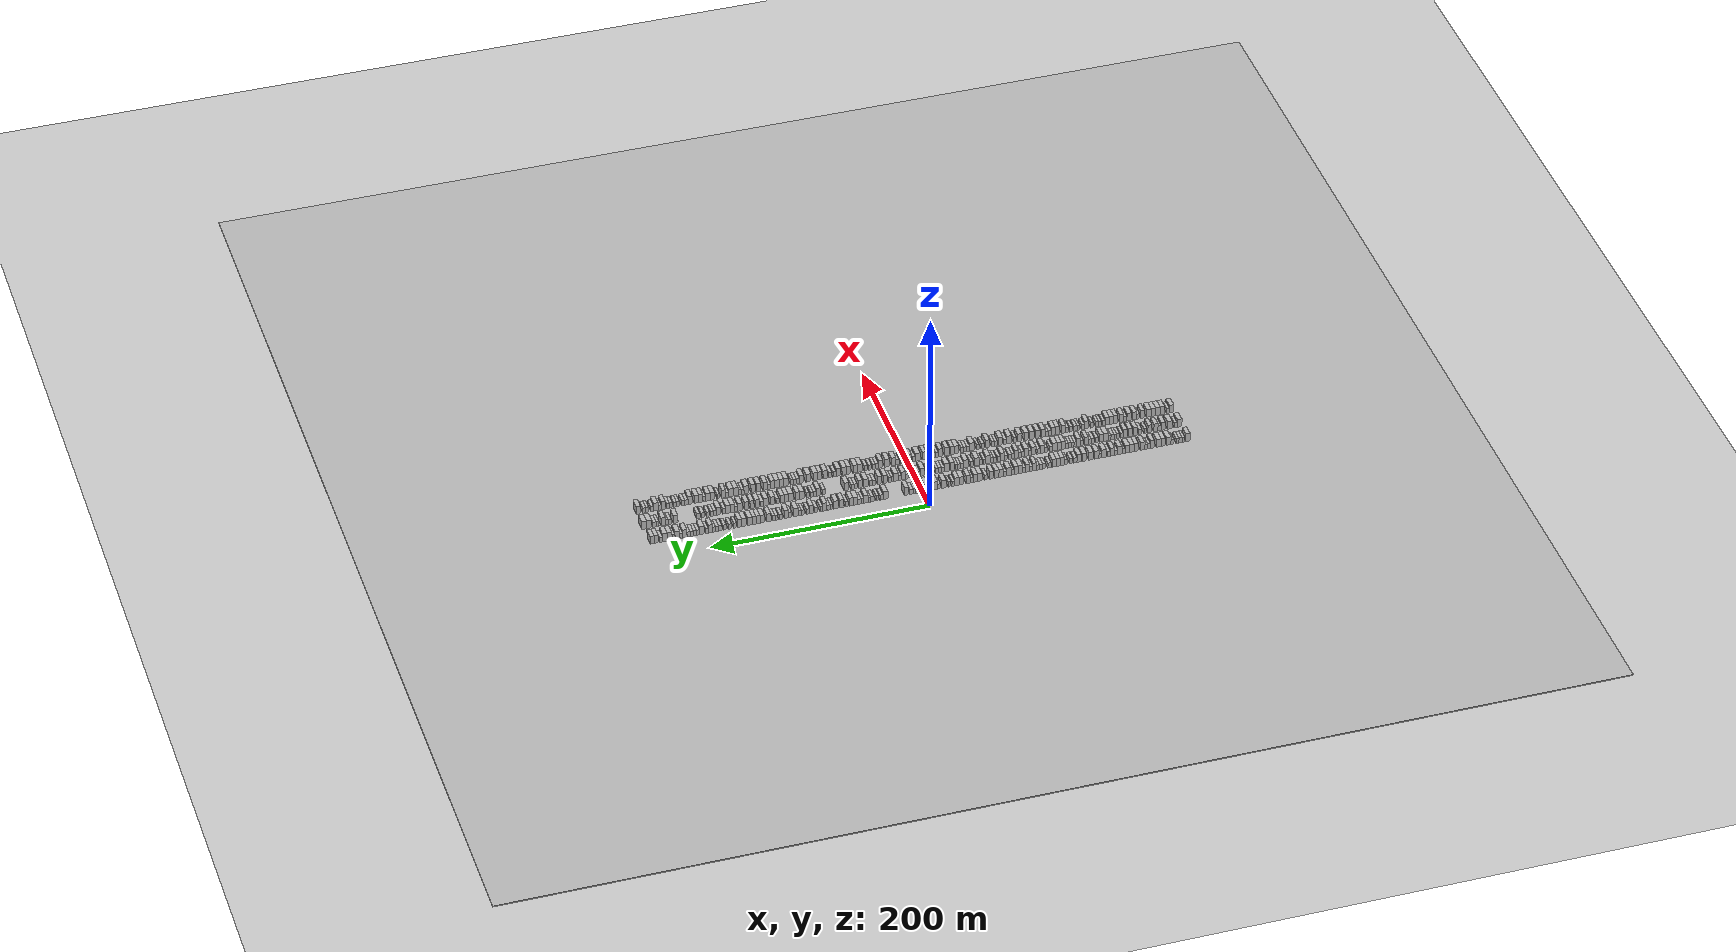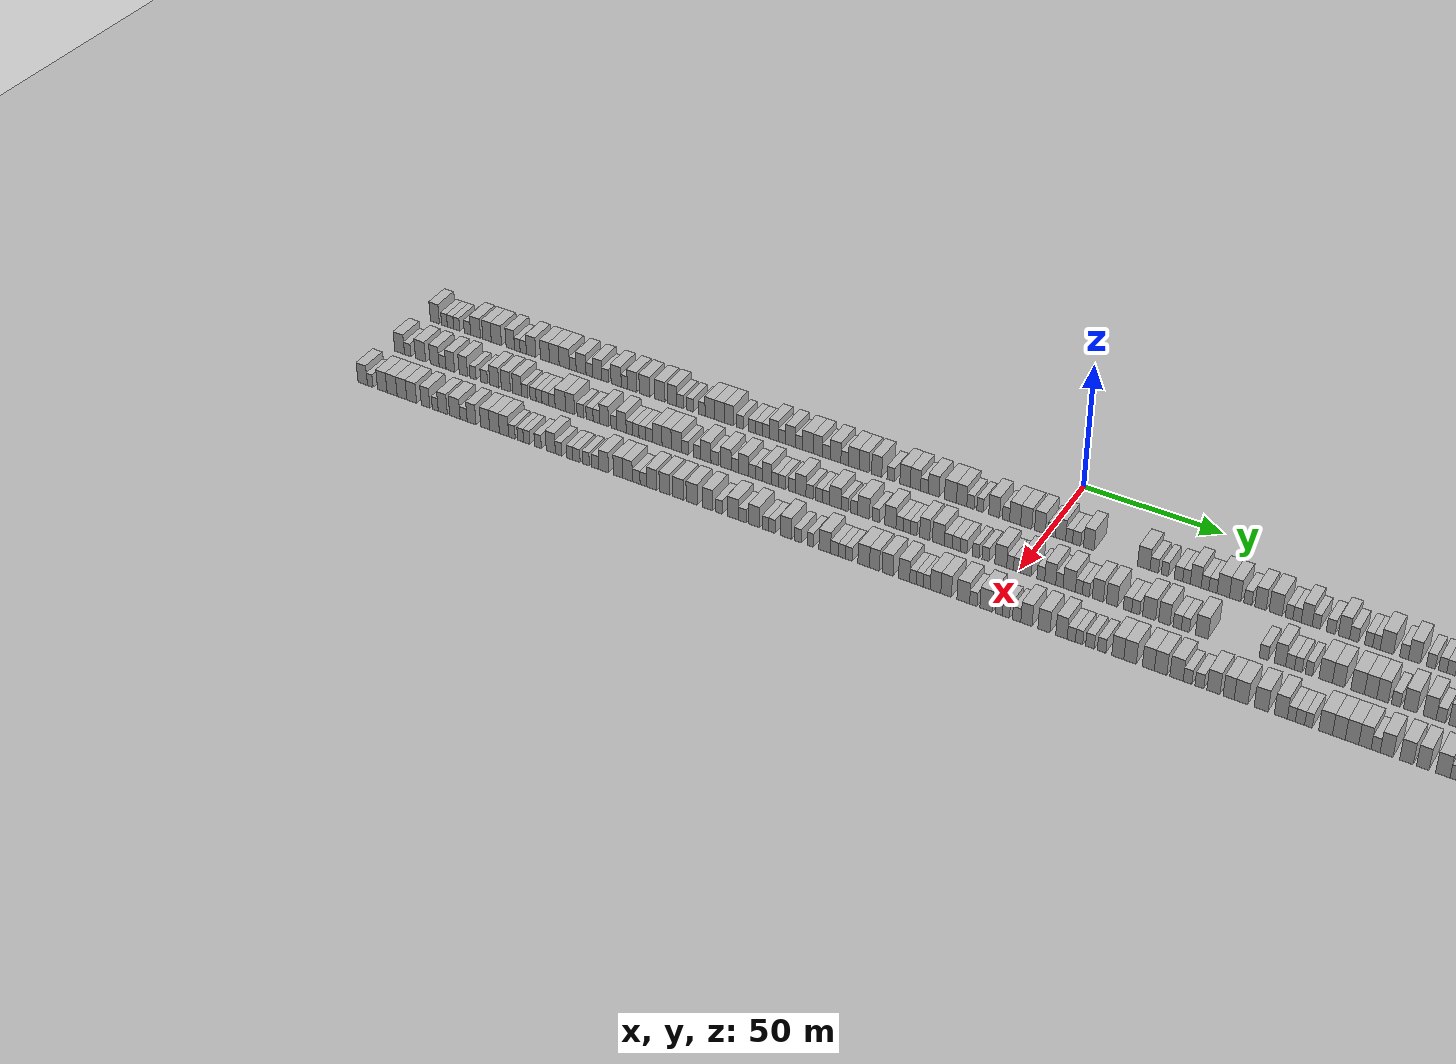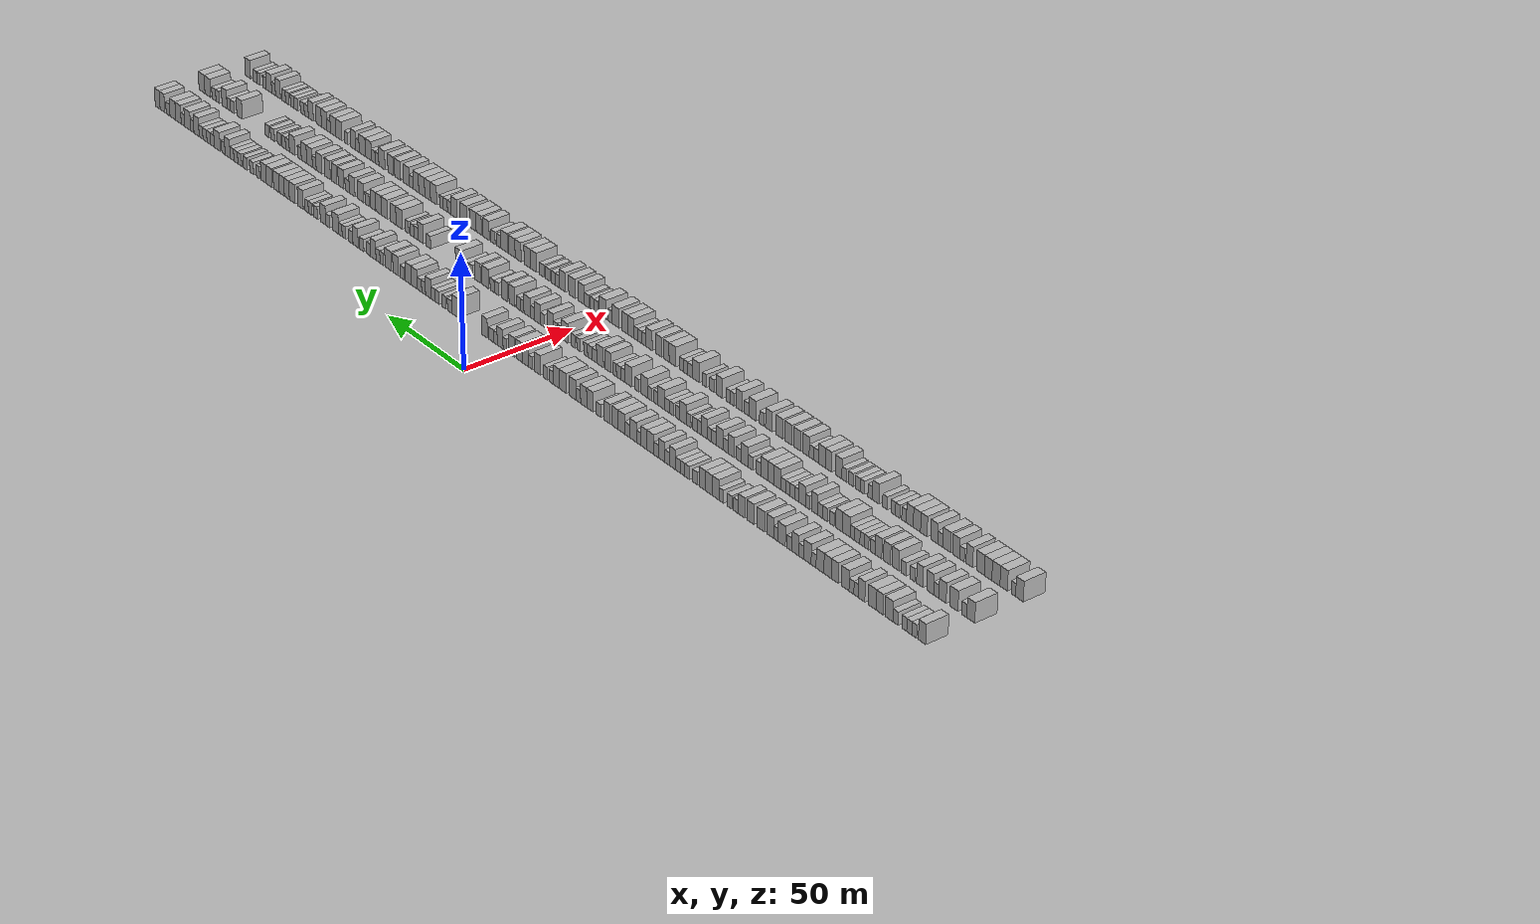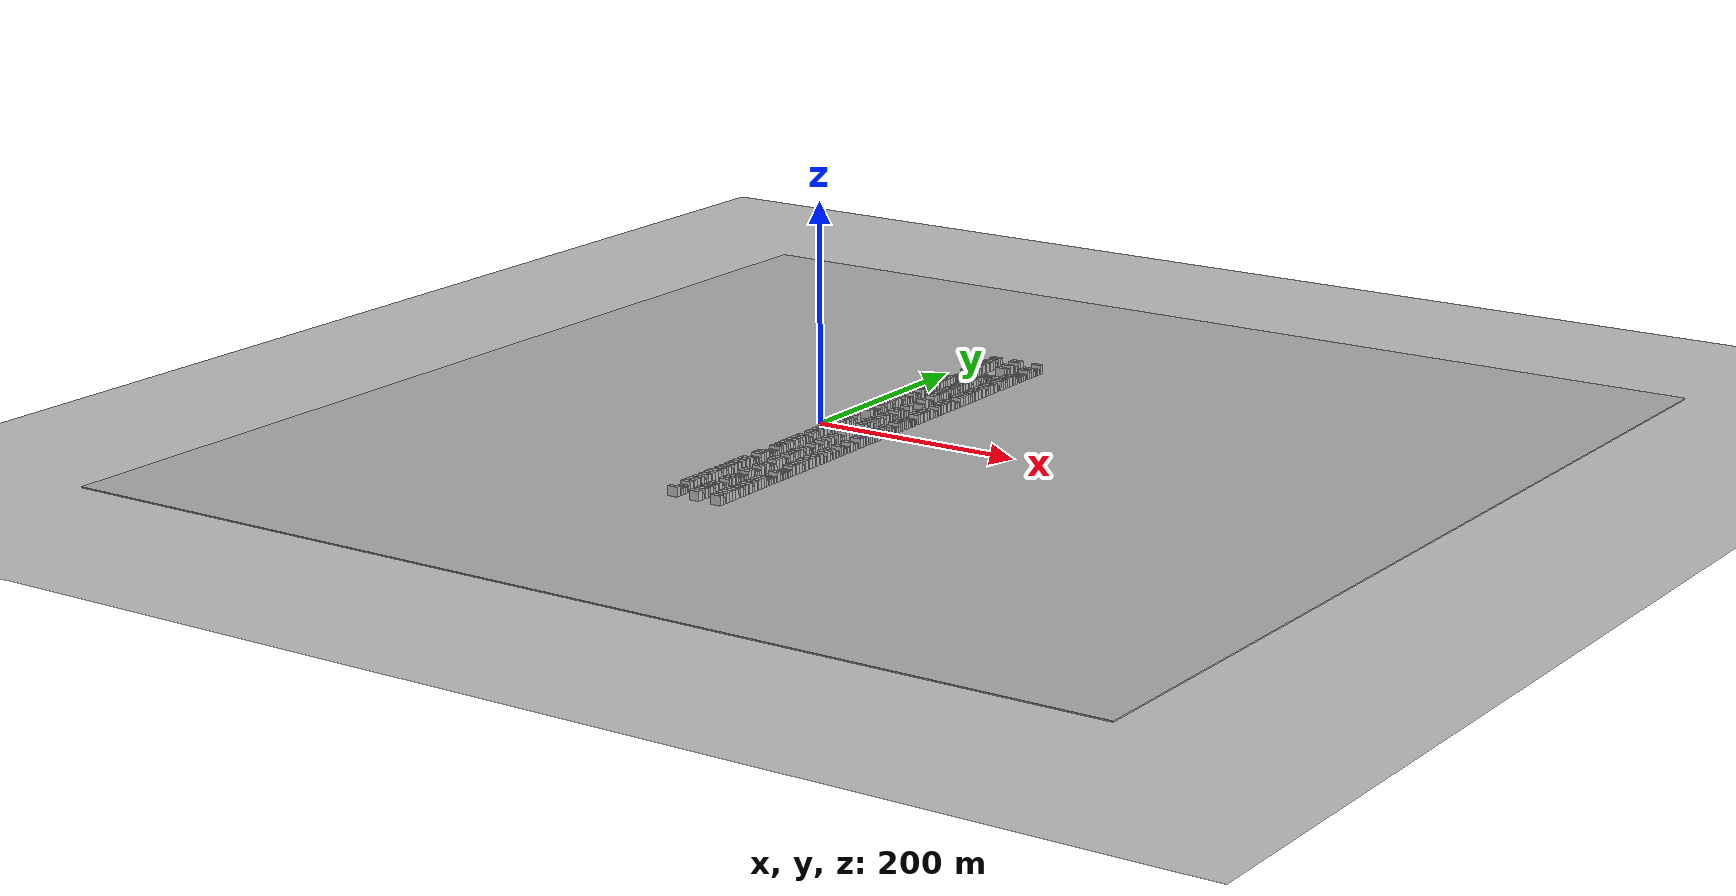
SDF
<?xml version="1.0" encoding="utf-8"?>

<sdf version="1.6">

   <world name="default">

      <gui fullscreen="0">

         <camera name="user_camera">

            <pose>-15 0 4.57585 0 0 0</pose>

            <view_controller>orbit</view_controller>

         </camera>

      </gui>

      <scene>

         <sky>

           <clouds>

             <speed>12</speed>

           </clouds>

         </sky>

         <ambient>0.4 0.4 0.4 1</ambient>

         <background>0.7 0.7 0.7 1</background>

         <shadows>1</shadows>

      </scene>

      <gravity>0 0 -9.8066</gravity>

      <magnetic_field>6e-06 2.3e-05 -4.2e-05</magnetic_field>

      <physics default="0" name="default_physics" type="ode">

         <ode>

            <solver>

               <type>quick</type>

               <iters>10</iters>

               <sor>1.0</sor>

               <use_dynamic_moi_rescaling>0</use_dynamic_moi_rescaling>

            </solver>

            <constraints>

               <cfm>0</cfm>

               <erp>0.2</erp>

               <contact_max_correcting_vel>100</contact_max_correcting_vel>

               <contact_surface_layer>0.001</contact_surface_layer>

            </constraints>

         </ode>

         <max_step_size>0.004</max_step_size>

         <real_time_factor>1</real_time_factor>

         <real_time_update_rate>250</real_time_update_rate>

      </physics>

      <light name="sun" type="directional">

         <cast_shadows>1</cast_shadows>

         <pose>0 0 10 0 0 0</pose>

         <diffuse>0.8 0.8 0.8 1</diffuse>

         <specular>0.2 0.2 0.2 1</specular>

         <attenuation>

            <range>1000</range>

            <constant>0.9</constant>

            <linear>0.01</linear>

            <quadratic>0.001</quadratic>

         </attenuation>

         <direction>-0.5 0.1 -0.9</direction>

      </light>

      <include>

         <name>ground_plane_1</name>

         <uri>model://HANNAS_ground_plane</uri>

         <pose>0 0 0  0 0 0</pose>

      </include>

      <include>

         <name>ground_plane_2</name>

         <uri>model://HANNAS_ground_plane</uri>

         <pose>100 0 0  0 0 0</pose>

      </include>

      <model name="building_1">

         <static>1</static>

         <pose frame="">25.0000 -245.9972 0 0.000000 0.000000 0.000000</pose>

         <link name="link">

            <pose frame="">0 0 4.50 0 0 0</pose>

            <collision name="collision">

               <geometry>

                  <box>

                     <size>10.0000 4.0056 9.0000</size>

                  </box>

               </geometry>

               <max_contacts>10</max_contacts>

               <surface>

                  <contact>

                     <ode/>

                  </contact>

                  <bounce/>

                  <friction>

                     <torsional>

                        <ode/>

                     </torsional>

                     <ode/>

                  </friction>

               </surface>

            </collision>

            <visual name="visual">

               <cast_shadows>0</cast_shadows>

               <geometry>

                  <box>

                     <size>10.0000 4.0056 9.0000</size>

                  </box>

               </geometry>

               <material>

                  <script>

                     <uri>model://HANNAS_wall/materials/scripts</uri>

                     <uri>model://HANNAS_wall/materials/textures</uri>

                     <name>vrc/HANNAS_wall</name>

                  </script>

               </material>

            </visual>

            <self_collide>0</self_collide>

            <enable_wind>0</enable_wind>

            <kinematic>0</kinematic>

         </link>

      </model>

      <model name="building_2">

         <static>1</static>

         <pose frame="">25.0000 -241.7306 0 0.000000 0.000000 0.000000</pose>

         <link name="link">

            <pose frame="">0 0 3.00 0 0 0</pose>

            <collision name="collision">

               <geometry>

                  <box>

                     <size>10.0000 2.5277 6.0000</size>

                  </box>

               </geometry>

               <max_contacts>10</max_contacts>

               <surface>

                  <contact>

                     <ode/>

                  </contact>

                  <bounce/>

                  <friction>

                     <torsional>

                        <ode/>

                     </torsional>

                     <ode/>

                  </friction>

               </surface>

            </collision>

            <visual name="visual">

               <cast_shadows>0</cast_shadows>

               <geometry>

                  <box>

                     <size>10.0000 2.5277 6.0000</size>

                  </box>

               </geometry>

               <material>

                  <script>

                     <uri>model://HANNAS_wall/materials/scripts</uri>

                     <uri>model://HANNAS_wall/materials/textures</uri>

                     <name>vrc/HANNAS_wall</name>

                  </script>

               </material>

            </visual>

            <self_collide>0</self_collide>

            <enable_wind>0</enable_wind>

            <kinematic>0</kinematic>

         </link>

      </model>

      <model name="building_3">

         <static>1</static>

         <pose frame="">25.0000 -239.0258 0 0.000000 0.000000 0.000000</pose>

         <link name="link">

            <pose frame="">0 0 3.00 0 0 0</pose>

            <collision name="collision">

               <geometry>

                  <box>

                     <size>10.0000 2.8818 6.0000</size>

                  </box>

               </geometry>

               <max_contacts>10</max_contacts>

               <surface>

                  <contact>

                     <ode/>

                  </contact>

                  <bounce/>

                  <friction>

                     <torsional>

                        <ode/>

                     </torsional>

                     <ode/>

                  </friction>

               </surface>

            </collision>

            <visual name="visual">

               <cast_shadows>0</cast_shadows>

               <geometry>

                  <box>

                     <size>10.0000 2.8818 6.0000</size>

                  </box>

               </geometry>

               <material>

                  <script>

                     <uri>model://HANNAS_wall/materials/scripts</uri>

                     <uri>model://HANNAS_wall/materials/textures</uri>

                     <name>vrc/HANNAS_wall</name>

                  </script>

               </material>

            </visual>

            <self_collide>0</self_collide>

            <enable_wind>0</enable_wind>

            <kinematic>0</kinematic>

         </link>

      </model>

      <model name="building_4">

         <static>1</static>

         <pose frame="">25.0000 -236.2623 0 0.000000 0.000000 0.000000</pose>

         <link name="link">

            <pose frame="">0 0 3.00 0 0 0</pose>

            <collision name="collision">

               <geometry>

                  <box>

                     <size>10.0000 2.6450 6.0000</size>

                  </box>

               </geometry>

               <max_contacts>10</max_contacts>

               <surface>

                  <contact>

                     <ode/>

                  </contact>

                  <bounce/>

                  <friction>

                     <torsional>

                        <ode/>

                     </torsional>

                     <ode/>

                  </friction>

               </surface>

            </collision>

            <visual name="visual">

               <cast_shadows>0</cast_shadows>

               <geometry>

                  <box>

                     <size>10.0000 2.6450 6.0000</size>

                  </box>

               </geometry>

               <material>

                  <script>

                     <uri>model://HANNAS_wall/materials/scripts</uri>

                     <uri>model://HANNAS_wall/materials/textures</uri>

                     <name>vrc/HANNAS_wall</name>

                  </script>

               </material>

            </visual>

            <self_collide>0</self_collide>

            <enable_wind>0</enable_wind>

            <kinematic>0</kinematic>

         </link>

      </model>

      <model name="building_5">

         <static>1</static>

         <pose frame="">25.0000 -231.5114 0 0.000000 0.000000 0.000000</pose>

         <link name="link">

            <pose frame="">0 0 3.00 0 0 0</pose>

            <collision name="collision">

               <geometry>

                  <box>

                     <size>10.0000 2.8569 6.0000</size>

                  </box>

               </geometry>

               <max_contacts>10</max_contacts>

               <surface>

                  <contact>

                     <ode/>

                  </contact>

                  <bounce/>

                  <friction>

                     <torsional>

                        <ode/>

                     </torsional>

                     <ode/>

                  </friction>

               </surface>

            </collision>

            <visual name="visual">

               <cast_shadows>0</cast_shadows>

               <geometry>

                  <box>

                     <size>10.0000 2.8569 6.0000</size>

                  </box>

               </geometry>

               <material>

                  <script>

                     <uri>model://HANNAS_wall/materials/scripts</uri>

                     <uri>model://HANNAS_wall/materials/textures</uri>

                     <name>vrc/HANNAS_wall</name>

                  </script>

               </material>

            </visual>

            <self_collide>0</self_collide>

            <enable_wind>0</enable_wind>

            <kinematic>0</kinematic>

         </link>

      </model>

      <model name="building_6">

         <static>1</static>

         <pose frame="">25.0000 -227.9132 0 0.000000 0.000000 0.000000</pose>

         <link name="link">

            <pose frame="">0 0 4.50 0 0 0</pose>

            <collision name="collision">

               <geometry>

                  <box>

                     <size>10.0000 4.3393 9.0000</size>

                  </box>

               </geometry>

               <max_contacts>10</max_contacts>

               <surface>

                  <contact>

                     <ode/>

                  </contact>

                  <bounce/>

                  <friction>

                     <torsional>

                        <ode/>

                     </torsional>

                     <ode/>

                  </friction>

               </surface>

            </collision>

            <visual name="visual">

               <cast_shadows>0</cast_shadows>

               <geometry>

                  <box>

                     <size>10.0000 4.3393 9.0000</size>

                  </box>

               </geometry>

               <material>

                  <script>

                     <uri>model://HANNAS_wall/materials/scripts</uri>

                     <uri>model://HANNAS_wall/materials/textures</uri>

                     <name>vrc/HANNAS_wall</name>

                  </script>

               </material>

            </visual>

            <self_collide>0</self_collide>

            <enable_wind>0</enable_wind>

            <kinematic>0</kinematic>

         </link>

      </model>

      <model name="building_7">

         <static>1</static>

         <pose frame="">25.0000 -222.8811 0 0.000000 0.000000 0.000000</pose>

         <link name="link">

            <pose frame="">0 0 4.50 0 0 0</pose>

            <collision name="collision">

               <geometry>

                  <box>

                     <size>10.0000 3.7250 9.0000</size>

                  </box>

               </geometry>

               <max_contacts>10</max_contacts>

               <surface>

                  <contact>

                     <ode/>

                  </contact>

                  <bounce/>

                  <friction>

                     <torsional>

                        <ode/>

                     </torsional>

                     <ode/>

                  </friction>

               </surface>

            </collision>

            <visual name="visual">

               <cast_shadows>0</cast_shadows>

               <geometry>

                  <box>

                     <size>10.0000 3.7250 9.0000</size>

                  </box>

               </geometry>

               <material>

                  <script>

                     <uri>model://HANNAS_wall/materials/scripts</uri>

                     <uri>model://HANNAS_wall/materials/textures</uri>

                     <name>vrc/HANNAS_wall</name>

                  </script>

               </material>

            </visual>

            <self_collide>0</self_collide>

            <enable_wind>0</enable_wind>

            <kinematic>0</kinematic>

         </link>

      </model>

      <model name="building_8">

         <static>1</static>

         <pose frame="">25.0000 -218.7858 0 0.000000 0.000000 0.000000</pose>

         <link name="link">

            <pose frame="">0 0 4.50 0 0 0</pose>

            <collision name="collision">

               <geometry>

                  <box>

                     <size>10.0000 4.4654 9.0000</size>

                  </box>

               </geometry>

               <max_contacts>10</max_contacts>

               <surface>

                  <contact>

                     <ode/>

                  </contact>

                  <bounce/>

                  <friction>

                     <torsional>

                        <ode/>

                     </torsional>

                     <ode/>

                  </friction>

               </surface>

            </collision>

            <visual name="visual">

               <cast_shadows>0</cast_shadows>

               <geometry>

                  <box>

                     <size>10.0000 4.4654 9.0000</size>

                  </box>

               </geometry>

               <material>

                  <script>

                     <uri>model://HANNAS_wall/materials/scripts</uri>

                     <uri>model://HANNAS_wall/materials/textures</uri>

                     <name>vrc/HANNAS_wall</name>

                  </script>

               </material>

            </visual>

            <self_collide>0</self_collide>

            <enable_wind>0</enable_wind>

            <kinematic>0</kinematic>

         </link>

      </model>

      <model name="building_9">

         <static>1</static>

         <pose frame="">25.0000 -212.7081 0 0.000000 0.000000 0.000000</pose>

         <link name="link">

            <pose frame="">0 0 4.50 0 0 0</pose>

            <collision name="collision">

               <geometry>

                  <box>

                     <size>10.0000 3.6901 9.0000</size>

                  </box>

               </geometry>

               <max_contacts>10</max_contacts>

               <surface>

                  <contact>

                     <ode/>

                  </contact>

                  <bounce/>

                  <friction>

                     <torsional>

                        <ode/>

                     </torsional>

                     <ode/>

                  </friction>

               </surface>

            </collision>

            <visual name="visual">

               <cast_shadows>0</cast_shadows>

               <geometry>

                  <box>

                     <size>10.0000 3.6901 9.0000</size>

                  </box>

               </geometry>

               <material>

                  <script>

                     <uri>model://HANNAS_wall/materials/scripts</uri>

                     <uri>model://HANNAS_wall/materials/textures</uri>

                     <name>vrc/HANNAS_wall</name>

                  </script>

               </material>

            </visual>

            <self_collide>0</self_collide>

            <enable_wind>0</enable_wind>

            <kinematic>0</kinematic>

         </link>

      </model>

      <model name="building_10">

         <static>1</static>

         <pose frame="">25.0000 -209.6533 0 0.000000 0.000000 0.000000</pose>

         <link name="link">

            <pose frame="">0 0 3.00 0 0 0</pose>

            <collision name="collision">

               <geometry>

                  <box>

                     <size>10.0000 2.4195 6.0000</size>

                  </box>

               </geometry>

               <max_contacts>10</max_contacts>

               <surface>

                  <contact>

                     <ode/>

                  </contact>

                  <bounce/>

                  <friction>

                     <torsional>

                        <ode/>

                     </torsional>

                     <ode/>

                  </friction>

               </surface>

            </collision>

            <visual name="visual">

               <cast_shadows>0</cast_shadows>

               <geometry>

                  <box>

                     <size>10.0000 2.4195 6.0000</size>

                  </box>

               </geometry>

               <material>

                  <script>

                     <uri>model://HANNAS_wall/materials/scripts</uri>

                     <uri>model://HANNAS_wall/materials/textures</uri>

                     <name>vrc/HANNAS_wall</name>

                  </script>

               </material>

            </visual>

            <self_collide>0</self_collide>

            <enable_wind>0</enable_wind>

            <kinematic>0</kinematic>

         </link>

      </model>

      <model name="building_11">

         <static>1</static>

         <pose frame="">25.0000 -207.0772 0 0.000000 0.000000 0.000000</pose>

         <link name="link">

            <pose frame="">0 0 3.00 0 0 0</pose>

            <collision name="collision">

               <geometry>

                  <box>

                     <size>10.0000 2.7327 6.0000</size>

                  </box>

               </geometry>

               <max_contacts>10</max_contacts>

               <surface>

                  <contact>

                     <ode/>

                  </contact>

                  <bounce/>

                  <friction>

                     <torsional>

                        <ode/>

                     </torsional>

                     <ode/>

                  </friction>

               </surface>

            </collision>

            <visual name="visual">

               <cast_shadows>0</cast_shadows>

               <geometry>

                  <box>

                     <size>10.0000 2.7327 6.0000</size>

                  </box>

               </geometry>

               <material>

                  <script>

                     <uri>model://HANNAS_wall/materials/scripts</uri>

                     <uri>model://HANNAS_wall/materials/textures</uri>

                     <name>vrc/HANNAS_wall</name>

                  </script>

               </material>

            </visual>

            <self_collide>0</self_collide>

            <enable_wind>0</enable_wind>

            <kinematic>0</kinematic>

         </link>

      </model>

      <model name="building_12">

         <static>1</static>

         <pose frame="">25.0000 -203.6651 0 0.000000 0.000000 0.000000</pose>

         <link name="link">

            <pose frame="">0 0 4.50 0 0 0</pose>

            <collision name="collision">

               <geometry>

                  <box>

                     <size>10.0000 4.0914 9.0000</size>

                  </box>

               </geometry>

               <max_contacts>10</max_contacts>

               <surface>

                  <contact>

                     <ode/>

                  </contact>

                  <bounce/>

                  <friction>

                     <torsional>

                        <ode/>

                     </torsional>

                     <ode/>

                  </friction>

               </surface>

            </collision>

            <visual name="visual">

               <cast_shadows>0</cast_shadows>

               <geometry>

                  <box>

                     <size>10.0000 4.0914 9.0000</size>

                  </box>

               </geometry>

               <material>

                  <script>

                     <uri>model://HANNAS_wall/materials/scripts</uri>

                     <uri>model://HANNAS_wall/materials/textures</uri>

                     <name>vrc/HANNAS_wall</name>

                  </script>

               </material>

            </visual>

            <self_collide>0</self_collide>

            <enable_wind>0</enable_wind>

            <kinematic>0</kinematic>

         </link>

      </model>

      <model name="building_13">

         <static>1</static>

         <pose frame="">25.0000 -197.6630 0 0.000000 0.000000 0.000000</pose>

         <link name="link">

            <pose frame="">0 0 4.50 0 0 0</pose>

            <collision name="collision">

               <geometry>

                  <box>

                     <size>10.0000 3.9128 9.0000</size>

                  </box>

               </geometry>

               <max_contacts>10</max_contacts>

               <surface>

                  <contact>

                     <ode/>

                  </contact>

                  <bounce/>

                  <friction>

                     <torsional>

                        <ode/>

                     </torsional>

                     <ode/>

                  </friction>

               </surface>

            </collision>

            <visual name="visual">

               <cast_shadows>0</cast_shadows>

               <geometry>

                  <box>

                     <size>10.0000 3.9128 9.0000</size>

                  </box>

               </geometry>

               <material>

                  <script>

                     <uri>model://HANNAS_wall/materials/scripts</uri>

                     <uri>model://HANNAS_wall/materials/textures</uri>

                     <name>vrc/HANNAS_wall</name>

                  </script>

               </material>

            </visual>

            <self_collide>0</self_collide>

            <enable_wind>0</enable_wind>

            <kinematic>0</kinematic>

         </link>

      </model>

      <model name="building_14">

         <static>1</static>

         <pose frame="">25.0000 -193.6784 0 0.000000 0.000000 0.000000</pose>

         <link name="link">

            <pose frame="">0 0 4.50 0 0 0</pose>

            <collision name="collision">

               <geometry>

                  <box>

                     <size>10.0000 4.0564 9.0000</size>

                  </box>

               </geometry>

               <max_contacts>10</max_contacts>

               <surface>

                  <contact>

                     <ode/>

                  </contact>

                  <bounce/>

                  <friction>

                     <torsional>

                        <ode/>

                     </torsional>

                     <ode/>

                  </friction>

               </surface>

            </collision>

            <visual name="visual">

               <cast_shadows>0</cast_shadows>

               <geometry>

                  <box>

                     <size>10.0000 4.0564 9.0000</size>

                  </box>

               </geometry>

               <material>

                  <script>

                     <uri>model://HANNAS_wall/materials/scripts</uri>

                     <uri>model://HANNAS_wall/materials/textures</uri>

                     <name>vrc/HANNAS_wall</name>

                  </script>

               </material>

            </visual>

            <self_collide>0</self_collide>

            <enable_wind>0</enable_wind>

            <kinematic>0</kinematic>

         </link>

      </model>

      <model name="building_15">

         <static>1</static>

         <pose frame="">25.0000 -189.4196 0 0.000000 0.000000 0.000000</pose>

         <link name="link">

            <pose frame="">0 0 4.50 0 0 0</pose>

            <collision name="collision">

               <geometry>

                  <box>

                     <size>10.0000 4.4612 9.0000</size>

                  </box>

               </geometry>

               <max_contacts>10</max_contacts>

               <surface>

                  <contact>

                     <ode/>

                  </contact>

                  <bounce/>

                  <friction>

                     <torsional>

                        <ode/>

                     </torsional>

                     <ode/>

                  </friction>

               </surface>

            </collision>

            <visual name="visual">

               <cast_shadows>0</cast_shadows>

               <geometry>

                  <box>

                     <size>10.0000 4.4612 9.0000</size>

                  </box>

               </geometry>

               <material>

                  <script>

                     <uri>model://HANNAS_wall/materials/scripts</uri>

                     <uri>model://HANNAS_wall/materials/textures</uri>

                     <name>vrc/HANNAS_wall</name>

                  </script>

               </material>

            </visual>

            <self_collide>0</self_collide>

            <enable_wind>0</enable_wind>

            <kinematic>0</kinematic>

         </link>

      </model>

      <model name="building_16">

         <static>1</static>

         <pose frame="">25.0000 -185.7799 0 0.000000 0.000000 0.000000</pose>

         <link name="link">

            <pose frame="">0 0 3.00 0 0 0</pose>

            <collision name="collision">

               <geometry>

                  <box>

                     <size>10.0000 2.8181 6.0000</size>

                  </box>

               </geometry>

               <max_contacts>10</max_contacts>

               <surface>

                  <contact>

                     <ode/>

                  </contact>

                  <bounce/>

                  <friction>

                     <torsional>

                        <ode/>

                     </torsional>

                     <ode/>

                  </friction>

               </surface>

            </collision>

            <visual name="visual">

               <cast_shadows>0</cast_shadows>

               <geometry>

                  <box>

                     <size>10.0000 2.8181 6.0000</size>

                  </box>

               </geometry>

               <material>

                  <script>

                     <uri>model://HANNAS_wall/materials/scripts</uri>

                     <uri>model://HANNAS_wall/materials/textures</uri>

                     <name>vrc/HANNAS_wall</name>

                  </script>

               </material>

            </visual>

            <self_collide>0</self_collide>

            <enable_wind>0</enable_wind>

            <kinematic>0</kinematic>

         </link>

      </model>

      <model name="building_17">

         <static>1</static>

         <pose frame="">25.0000 -182.2853 0 0.000000 0.000000 0.000000</pose>

         <link name="link">

            <pose frame="">0 0 4.50 0 0 0</pose>

            <collision name="collision">

               <geometry>

                  <box>

                     <size>10.0000 4.1711 9.0000</size>

                  </box>

               </geometry>

               <max_contacts>10</max_contacts>

               <surface>

                  <contact>

                     <ode/>

                  </contact>

                  <bounce/>

                  <friction>

                     <torsional>

                        <ode/>

                     </torsional>

                     <ode/>

                  </friction>

               </surface>

            </collision>

            <visual name="visual">

               <cast_shadows>0</cast_shadows>

               <geometry>

                  <box>

                     <size>10.0000 4.1711 9.0000</size>

                  </box>

               </geometry>

               <material>

                  <script>

                     <uri>model://HANNAS_wall/materials/scripts</uri>

                     <uri>model://HANNAS_wall/materials/textures</uri>

                     <name>vrc/HANNAS_wall</name>

                  </script>

               </material>

            </visual>

            <self_collide>0</self_collide>

            <enable_wind>0</enable_wind>

            <kinematic>0</kinematic>

         </link>

      </model>

      <model name="building_18">

         <static>1</static>

         <pose frame="">25.0000 -178.7559 0 0.000000 0.000000 0.000000</pose>

         <link name="link">

            <pose frame="">0 0 3.00 0 0 0</pose>

            <collision name="collision">

               <geometry>

                  <box>

                     <size>10.0000 2.8878 6.0000</size>

                  </box>

               </geometry>

               <max_contacts>10</max_contacts>

               <surface>

                  <contact>

                     <ode/>

                  </contact>

                  <bounce/>

                  <friction>

                     <torsional>

                        <ode/>

                     </torsional>

                     <ode/>

                  </friction>

               </surface>

            </collision>

            <visual name="visual">

               <cast_shadows>0</cast_shadows>

               <geometry>

                  <box>

                     <size>10.0000 2.8878 6.0000</size>

                  </box>

               </geometry>

               <material>

                  <script>

                     <uri>model://HANNAS_wall/materials/scripts</uri>

                     <uri>model://HANNAS_wall/materials/textures</uri>

                     <name>vrc/HANNAS_wall</name>

                  </script>

               </material>

            </visual>

            <self_collide>0</self_collide>

            <enable_wind>0</enable_wind>

            <kinematic>0</kinematic>

         </link>

      </model>

      <model name="building_19">

         <static>1</static>

         <pose frame="">25.0000 -175.4224 0 0.000000 0.000000 0.000000</pose>

         <link name="link">

            <pose frame="">0 0 4.50 0 0 0</pose>

            <collision name="collision">

               <geometry>

                  <box>

                     <size>10.0000 3.7793 9.0000</size>

                  </box>

               </geometry>

               <max_contacts>10</max_contacts>

               <surface>

                  <contact>

                     <ode/>

                  </contact>

                  <bounce/>

                  <friction>

                     <torsional>

                        <ode/>

                     </torsional>

                     <ode/>

                  </friction>

               </surface>

            </collision>

            <visual name="visual">

               <cast_shadows>0</cast_shadows>

               <geometry>

                  <box>

                     <size>10.0000 3.7793 9.0000</size>

                  </box>

               </geometry>

               <material>

                  <script>

                     <uri>model://HANNAS_wall/materials/scripts</uri>

                     <uri>model://HANNAS_wall/materials/textures</uri>

                     <name>vrc/HANNAS_wall</name>

                  </script>

               </material>

            </visual>

            <self_collide>0</self_collide>

            <enable_wind>0</enable_wind>

            <kinematic>0</kinematic>

         </link>

      </model>

      <model name="building_20">

         <static>1</static>

         <pose frame="">25.0000 -172.0782 0 0.000000 0.000000 0.000000</pose>

         <link name="link">

            <pose frame="">0 0 3.00 0 0 0</pose>

            <collision name="collision">

               <geometry>

                  <box>

                     <size>10.0000 2.9092 6.0000</size>

                  </box>

               </geometry>

               <max_contacts>10</max_contacts>

               <surface>

                  <contact>

                     <ode/>

                  </contact>

                  <bounce/>

                  <friction>

                     <torsional>

                        <ode/>

                     </torsional>

                     <ode/>

                  </friction>

               </surface>

            </collision>

            <visual name="visual">

               <cast_shadows>0</cast_shadows>

               <geometry>

                  <box>

                     <size>10.0000 2.9092 6.0000</size>

                  </box>

               </geometry>

               <material>

                  <script>

                     <uri>model://HANNAS_wall/materials/scripts</uri>

                     <uri>model://HANNAS_wall/materials/textures</uri>

                     <name>vrc/HANNAS_wall</name>

                  </script>

               </material>

            </visual>

            <self_collide>0</self_collide>

            <enable_wind>0</enable_wind>

            <kinematic>0</kinematic>

         </link>

      </model>

      <model name="building_21">

         <static>1</static>

         <pose frame="">25.0000 -167.4889 0 0.000000 0.000000 0.000000</pose>

         <link name="link">

            <pose frame="">0 0 4.50 0 0 0</pose>

            <collision name="collision">

               <geometry>

                  <box>

                     <size>10.0000 4.2693 9.0000</size>

                  </box>

               </geometry>

               <max_contacts>10</max_contacts>

               <surface>

                  <contact>

                     <ode/>

                  </contact>

                  <bounce/>

                  <friction>

                     <torsional>

                        <ode/>

                     </torsional>

                     <ode/>

                  </friction>

               </surface>

            </collision>

            <visual name="visual">

               <cast_shadows>0</cast_shadows>

               <geometry>

                  <box>

                     <size>10.0000 4.2693 9.0000</size>

                  </box>

               </geometry>

               <material>

                  <script>

                     <uri>model://HANNAS_wall/materials/scripts</uri>

                     <uri>model://HANNAS_wall/materials/textures</uri>

                     <name>vrc/HANNAS_wall</name>

                  </script>

               </material>

            </visual>

            <self_collide>0</self_collide>

            <enable_wind>0</enable_wind>

            <kinematic>0</kinematic>

         </link>

      </model>

      <model name="building_22">

         <static>1</static>

         <pose frame="">25.0000 -164.0879 0 0.000000 0.000000 0.000000</pose>

         <link name="link">

            <pose frame="">0 0 3.00 0 0 0</pose>

            <collision name="collision">

               <geometry>

                  <box>

                     <size>10.0000 2.5327 6.0000</size>

                  </box>

               </geometry>

               <max_contacts>10</max_contacts>

               <surface>

                  <contact>

                     <ode/>

                  </contact>

                  <bounce/>

                  <friction>

                     <torsional>

                        <ode/>

                     </torsional>

                     <ode/>

                  </friction>

               </surface>

            </collision>

            <visual name="visual">

               <cast_shadows>0</cast_shadows>

               <geometry>

                  <box>

                     <size>10.0000 2.5327 6.0000</size>

                  </box>

               </geometry>

               <material>

                  <script>

                     <uri>model://HANNAS_wall/materials/scripts</uri>

                     <uri>model://HANNAS_wall/materials/textures</uri>

                     <name>vrc/HANNAS_wall</name>

                  </script>

               </material>

            </visual>

            <self_collide>0</self_collide>

            <enable_wind>0</enable_wind>

            <kinematic>0</kinematic>

         </link>

      </model>

      <model name="building_23">

         <static>1</static>

         <pose frame="">25.0000 -160.8175 0 0.000000 0.000000 0.000000</pose>

         <link name="link">

            <pose frame="">0 0 4.50 0 0 0</pose>

            <collision name="collision">

               <geometry>

                  <box>

                     <size>10.0000 4.0081 9.0000</size>

                  </box>

               </geometry>

               <max_contacts>10</max_contacts>

               <surface>

                  <contact>

                     <ode/>

                  </contact>

                  <bounce/>

                  <friction>

                     <torsional>

                        <ode/>

                     </torsional>

                     <ode/>

                  </friction>

               </surface>

            </collision>

            <visual name="visual">

               <cast_shadows>0</cast_shadows>

               <geometry>

                  <box>

                     <size>10.0000 4.0081 9.0000</size>

                  </box>

               </geometry>

               <material>

                  <script>

                     <uri>model://HANNAS_wall/materials/scripts</uri>

                     <uri>model://HANNAS_wall/materials/textures</uri>

                     <name>vrc/HANNAS_wall</name>

                  </script>

               </material>

            </visual>

            <self_collide>0</self_collide>

            <enable_wind>0</enable_wind>

            <kinematic>0</kinematic>

         </link>

      </model>

      <model name="building_24">

         <static>1</static>

         <pose frame="">25.0000 -155.6202 0 0.000000 0.000000 0.000000</pose>

         <link name="link">

            <pose frame="">0 0 4.50 0 0 0</pose>

            <collision name="collision">

               <geometry>

                  <box>

                     <size>10.0000 4.3866 9.0000</size>

                  </box>

               </geometry>

               <max_contacts>10</max_contacts>

               <surface>

                  <contact>

                     <ode/>

                  </contact>

                  <bounce/>

                  <friction>

                     <torsional>

                        <ode/>

                     </torsional>

                     <ode/>

                  </friction>

               </surface>

            </collision>

            <visual name="visual">

               <cast_shadows>0</cast_shadows>

               <geometry>

                  <box>

                     <size>10.0000 4.3866 9.0000</size>

                  </box>

               </geometry>

               <material>

                  <script>

                     <uri>model://HANNAS_wall/materials/scripts</uri>

                     <uri>model://HANNAS_wall/materials/textures</uri>

                     <name>vrc/HANNAS_wall</name>

                  </script>

               </material>

            </visual>

            <self_collide>0</self_collide>

            <enable_wind>0</enable_wind>

            <kinematic>0</kinematic>

         </link>

      </model>

      <model name="building_25">

         <static>1</static>

         <pose frame="">25.0000 -149.3242 0 0.000000 0.000000 0.000000</pose>

         <link name="link">

            <pose frame="">0 0 4.50 0 0 0</pose>

            <collision name="collision">

               <geometry>

                  <box>

                     <size>10.0000 4.2054 9.0000</size>

                  </box>

               </geometry>

               <max_contacts>10</max_contacts>

               <surface>

                  <contact>

                     <ode/>

                  </contact>

                  <bounce/>

                  <friction>

                     <torsional>

                        <ode/>

                     </torsional>

                     <ode/>

                  </friction>

               </surface>

            </collision>

            <visual name="visual">

               <cast_shadows>0</cast_shadows>

               <geometry>

                  <box>

                     <size>10.0000 4.2054 9.0000</size>

                  </box>

               </geometry>

               <material>

                  <script>

                     <uri>model://HANNAS_wall/materials/scripts</uri>

                     <uri>model://HANNAS_wall/materials/textures</uri>

                     <name>vrc/HANNAS_wall</name>

                  </script>

               </material>

            </visual>

            <self_collide>0</self_collide>

            <enable_wind>0</enable_wind>

            <kinematic>0</kinematic>

         </link>

      </model>

      <model name="building_26">

         <static>1</static>

         <pose frame="">25.0000 -144.2968 0 0.000000 0.000000 0.000000</pose>

         <link name="link">

            <pose frame="">0 0 4.50 0 0 0</pose>

            <collision name="collision">

               <geometry>

                  <box>

                     <size>10.0000 3.8493 9.0000</size>

                  </box>

               </geometry>

               <max_contacts>10</max_contacts>

               <surface>

                  <contact>

                     <ode/>

                  </contact>

                  <bounce/>

                  <friction>

                     <torsional>

                        <ode/>

                     </torsional>

                     <ode/>

                  </friction>

               </surface>

            </collision>

            <visual name="visual">

               <cast_shadows>0</cast_shadows>

               <geometry>

                  <box>

                     <size>10.0000 3.8493 9.0000</size>

                  </box>

               </geometry>

               <material>

                  <script>

                     <uri>model://HANNAS_wall/materials/scripts</uri>

                     <uri>model://HANNAS_wall/materials/textures</uri>

                     <name>vrc/HANNAS_wall</name>

                  </script>

               </material>

            </visual>

            <self_collide>0</self_collide>

            <enable_wind>0</enable_wind>

            <kinematic>0</kinematic>

         </link>

      </model>

      <model name="building_27">

         <static>1</static>

         <pose frame="">25.0000 -140.9447 0 0.000000 0.000000 0.000000</pose>

         <link name="link">

            <pose frame="">0 0 3.00 0 0 0</pose>

            <collision name="collision">

               <geometry>

                  <box>

                     <size>10.0000 2.8551 6.0000</size>

                  </box>

               </geometry>

               <max_contacts>10</max_contacts>

               <surface>

                  <contact>

                     <ode/>

                  </contact>

                  <bounce/>

                  <friction>

                     <torsional>

                        <ode/>

                     </torsional>

                     <ode/>

                  </friction>

               </surface>

            </collision>

            <visual name="visual">

               <cast_shadows>0</cast_shadows>

               <geometry>

                  <box>

                     <size>10.0000 2.8551 6.0000</size>

                  </box>

               </geometry>

               <material>

                  <script>

                     <uri>model://HANNAS_wall/materials/scripts</uri>

                     <uri>model://HANNAS_wall/materials/textures</uri>

                     <name>vrc/HANNAS_wall</name>

                  </script>

               </material>

            </visual>

            <self_collide>0</self_collide>

            <enable_wind>0</enable_wind>

            <kinematic>0</kinematic>

         </link>

      </model>

      <model name="building_28">

         <static>1</static>

         <pose frame="">25.0000 -137.0602 0 0.000000 0.000000 0.000000</pose>

         <link name="link">

            <pose frame="">0 0 3.00 0 0 0</pose>

            <collision name="collision">

               <geometry>

                  <box>

                     <size>10.0000 2.9138 6.0000</size>

                  </box>

               </geometry>

               <max_contacts>10</max_contacts>

               <surface>

                  <contact>

                     <ode/>

                  </contact>

                  <bounce/>

                  <friction>

                     <torsional>

                        <ode/>

                     </torsional>

                     <ode/>

                  </friction>

               </surface>

            </collision>

            <visual name="visual">

               <cast_shadows>0</cast_shadows>

               <geometry>

                  <box>

                     <size>10.0000 2.9138 6.0000</size>

                  </box>

               </geometry>

               <material>

                  <script>

                     <uri>model://HANNAS_wall/materials/scripts</uri>

                     <uri>model://HANNAS_wall/materials/textures</uri>

                     <name>vrc/HANNAS_wall</name>

                  </script>

               </material>

            </visual>

            <self_collide>0</self_collide>

            <enable_wind>0</enable_wind>

            <kinematic>0</kinematic>

         </link>

      </model>

      <model name="building_29">

         <static>1</static>

         <pose frame="">25.0000 -132.2127 0 0.000000 0.000000 0.000000</pose>

         <link name="link">

            <pose frame="">0 0 3.00 0 0 0</pose>

            <collision name="collision">

               <geometry>

                  <box>

                     <size>10.0000 2.7813 6.0000</size>

                  </box>

               </geometry>

               <max_contacts>10</max_contacts>

               <surface>

                  <contact>

                     <ode/>

                  </contact>

                  <bounce/>

                  <friction>

                     <torsional>

                        <ode/>

                     </torsional>

                     <ode/>

                  </friction>

               </surface>

            </collision>

            <visual name="visual">

               <cast_shadows>0</cast_shadows>

               <geometry>

                  <box>

                     <size>10.0000 2.7813 6.0000</size>

                  </box>

               </geometry>

               <material>

                  <script>

                     <uri>model://HANNAS_wall/materials/scripts</uri>

                     <uri>model://HANNAS_wall/materials/textures</uri>

                     <name>vrc/HANNAS_wall</name>

                  </script>

               </material>

            </visual>

            <self_collide>0</self_collide>

            <enable_wind>0</enable_wind>

            <kinematic>0</kinematic>

         </link>

      </model>

      <model name="building_30">

         <static>1</static>

         <pose frame="">25.0000 -128.8411 0 0.000000 0.000000 0.000000</pose>

         <link name="link">

            <pose frame="">0 0 4.50 0 0 0</pose>

            <collision name="collision">

               <geometry>

                  <box>

                     <size>10.0000 3.9619 9.0000</size>

                  </box>

               </geometry>

               <max_contacts>10</max_contacts>

               <surface>

                  <contact>

                     <ode/>

                  </contact>

                  <bounce/>

                  <friction>

                     <torsional>

                        <ode/>

                     </torsional>

                     <ode/>

                  </friction>

               </surface>

            </collision>

            <visual name="visual">

               <cast_shadows>0</cast_shadows>

               <geometry>

                  <box>

                     <size>10.0000 3.9619 9.0000</size>

                  </box>

               </geometry>

               <material>

                  <script>

                     <uri>model://HANNAS_wall/materials/scripts</uri>

                     <uri>model://HANNAS_wall/materials/textures</uri>

                     <name>vrc/HANNAS_wall</name>

                  </script>

               </material>

            </visual>

            <self_collide>0</self_collide>

            <enable_wind>0</enable_wind>

            <kinematic>0</kinematic>

         </link>

      </model>

      <model name="building_31">

         <static>1</static>

         <pose frame="">25.0000 -124.9556 0 0.000000 0.000000 0.000000</pose>

         <link name="link">

            <pose frame="">0 0 4.50 0 0 0</pose>

            <collision name="collision">

               <geometry>

                  <box>

                     <size>10.0000 3.8092 9.0000</size>

                  </box>

               </geometry>

               <max_contacts>10</max_contacts>

               <surface>

                  <contact>

                     <ode/>

                  </contact>

                  <bounce/>

                  <friction>

                     <torsional>

                        <ode/>

                     </torsional>

                     <ode/>

                  </friction>

               </surface>

            </collision>

            <visual name="visual">

               <cast_shadows>0</cast_shadows>

               <geometry>

                  <box>

                     <size>10.0000 3.8092 9.0000</size>

                  </box>

               </geometry>

               <material>

                  <script>

                     <uri>model://HANNAS_wall/materials/scripts</uri>

                     <uri>model://HANNAS_wall/materials/textures</uri>

                     <name>vrc/HANNAS_wall</name>

                  </script>

               </material>

            </visual>

            <self_collide>0</self_collide>

            <enable_wind>0</enable_wind>

            <kinematic>0</kinematic>

         </link>

      </model>

      <model name="building_32">

         <static>1</static>

         <pose frame="">25.0000 -121.1443 0 0.000000 0.000000 0.000000</pose>

         <link name="link">

            <pose frame="">0 0 4.50 0 0 0</pose>

            <collision name="collision">

               <geometry>

                  <box>

                     <size>10.0000 3.8134 9.0000</size>

                  </box>

               </geometry>

               <max_contacts>10</max_contacts>

               <surface>

                  <contact>

                     <ode/>

                  </contact>

                  <bounce/>

                  <friction>

                     <torsional>

                        <ode/>

                     </torsional>

                     <ode/>

                  </friction>

               </surface>

            </collision>

            <visual name="visual">

               <cast_shadows>0</cast_shadows>

               <geometry>

                  <box>

                     <size>10.0000 3.8134 9.0000</size>

                  </box>

               </geometry>

               <material>

                  <script>

                     <uri>model://HANNAS_wall/materials/scripts</uri>

                     <uri>model://HANNAS_wall/materials/textures</uri>

                     <name>vrc/HANNAS_wall</name>

                  </script>

               </material>

            </visual>

            <self_collide>0</self_collide>

            <enable_wind>0</enable_wind>

            <kinematic>0</kinematic>

         </link>

      </model>

      <model name="building_33">

         <static>1</static>

         <pose frame="">25.0000 -116.8206 0 0.000000 0.000000 0.000000</pose>

         <link name="link">

            <pose frame="">0 0 3.00 0 0 0</pose>

            <collision name="collision">

               <geometry>

                  <box>

                     <size>10.0000 2.8338 6.0000</size>

                  </box>

               </geometry>

               <max_contacts>10</max_contacts>

               <surface>

                  <contact>

                     <ode/>

                  </contact>

                  <bounce/>

                  <friction>

                     <torsional>

                        <ode/>

                     </torsional>

                     <ode/>

                  </friction>

               </surface>

            </collision>

            <visual name="visual">

               <cast_shadows>0</cast_shadows>

               <geometry>

                  <box>

                     <size>10.0000 2.8338 6.0000</size>

                  </box>

               </geometry>

               <material>

                  <script>

                     <uri>model://HANNAS_wall/materials/scripts</uri>

                     <uri>model://HANNAS_wall/materials/textures</uri>

                     <name>vrc/HANNAS_wall</name>

                  </script>

               </material>

            </visual>

            <self_collide>0</self_collide>

            <enable_wind>0</enable_wind>

            <kinematic>0</kinematic>

         </link>

      </model>

      <model name="building_34">

         <static>1</static>

         <pose frame="">25.0000 -112.0106 0 0.000000 0.000000 0.000000</pose>

         <link name="link">

            <pose frame="">0 0 3.00 0 0 0</pose>

            <collision name="collision">

               <geometry>

                  <box>

                     <size>10.0000 2.7863 6.0000</size>

                  </box>

               </geometry>

               <max_contacts>10</max_contacts>

               <surface>

                  <contact>

                     <ode/>

                  </contact>

                  <bounce/>

                  <friction>

                     <torsional>

                        <ode/>

                     </torsional>

                     <ode/>

                  </friction>

               </surface>

            </collision>

            <visual name="visual">

               <cast_shadows>0</cast_shadows>

               <geometry>

                  <box>

                     <size>10.0000 2.7863 6.0000</size>

                  </box>

               </geometry>

               <material>

                  <script>

                     <uri>model://HANNAS_wall/materials/scripts</uri>

                     <uri>model://HANNAS_wall/materials/textures</uri>

                     <name>vrc/HANNAS_wall</name>

                  </script>

               </material>

            </visual>

            <self_collide>0</self_collide>

            <enable_wind>0</enable_wind>

            <kinematic>0</kinematic>

         </link>

      </model>

      <model name="building_35">

         <static>1</static>

         <pose frame="">25.0000 -109.1932 0 0.000000 0.000000 0.000000</pose>

         <link name="link">

            <pose frame="">0 0 3.00 0 0 0</pose>

            <collision name="collision">

               <geometry>

                  <box>

                     <size>10.0000 2.8485 6.0000</size>

                  </box>

               </geometry>

               <max_contacts>10</max_contacts>

               <surface>

                  <contact>

                     <ode/>

                  </contact>

                  <bounce/>

                  <friction>

                     <torsional>

                        <ode/>

                     </torsional>

                     <ode/>

                  </friction>

               </surface>

            </collision>

            <visual name="visual">

               <cast_shadows>0</cast_shadows>

               <geometry>

                  <box>

                     <size>10.0000 2.8485 6.0000</size>

                  </box>

               </geometry>

               <material>

                  <script>

                     <uri>model://HANNAS_wall/materials/scripts</uri>

                     <uri>model://HANNAS_wall/materials/textures</uri>

                     <name>vrc/HANNAS_wall</name>

                  </script>

               </material>

            </visual>

            <self_collide>0</self_collide>

            <enable_wind>0</enable_wind>

            <kinematic>0</kinematic>

         </link>

      </model>

      <model name="building_36">

         <static>1</static>

         <pose frame="">25.0000 -106.3663 0 0.000000 0.000000 0.000000</pose>

         <link name="link">

            <pose frame="">0 0 3.00 0 0 0</pose>

            <collision name="collision">

               <geometry>

                  <box>

                     <size>10.0000 2.8053 6.0000</size>

                  </box>

               </geometry>

               <max_contacts>10</max_contacts>

               <surface>

                  <contact>

                     <ode/>

                  </contact>

                  <bounce/>

                  <friction>

                     <torsional>

                        <ode/>

                     </torsional>

                     <ode/>

                  </friction>

               </surface>

            </collision>

            <visual name="visual">

               <cast_shadows>0</cast_shadows>

               <geometry>

                  <box>

                     <size>10.0000 2.8053 6.0000</size>

                  </box>

               </geometry>

               <material>

                  <script>

                     <uri>model://HANNAS_wall/materials/scripts</uri>

                     <uri>model://HANNAS_wall/materials/textures</uri>

                     <name>vrc/HANNAS_wall</name>

                  </script>

               </material>

            </visual>

            <self_collide>0</self_collide>

            <enable_wind>0</enable_wind>

            <kinematic>0</kinematic>

         </link>

      </model>

      <model name="building_37">

         <static>1</static>

         <pose frame="">25.0000 -103.1372 0 0.000000 0.000000 0.000000</pose>

         <link name="link">

            <pose frame="">0 0 4.50 0 0 0</pose>

            <collision name="collision">

               <geometry>

                  <box>

                     <size>10.0000 3.6528 9.0000</size>

                  </box>

               </geometry>

               <max_contacts>10</max_contacts>

               <surface>

                  <contact>

                     <ode/>

                  </contact>

                  <bounce/>

                  <friction>

                     <torsional>

                        <ode/>

                     </torsional>

                     <ode/>

                  </friction>

               </surface>

            </collision>

            <visual name="visual">

               <cast_shadows>0</cast_shadows>

               <geometry>

                  <box>

                     <size>10.0000 3.6528 9.0000</size>

                  </box>

               </geometry>

               <material>

                  <script>

                     <uri>model://HANNAS_wall/materials/scripts</uri>

                     <uri>model://HANNAS_wall/materials/textures</uri>

                     <name>vrc/HANNAS_wall</name>

                  </script>

               </material>

            </visual>

            <self_collide>0</self_collide>

            <enable_wind>0</enable_wind>

            <kinematic>0</kinematic>

         </link>

      </model>

      <model name="building_38">

         <static>1</static>

         <pose frame="">25.0000 -99.9185 0 0.000000 0.000000 0.000000</pose>

         <link name="link">

            <pose frame="">0 0 3.00 0 0 0</pose>

            <collision name="collision">

               <geometry>

                  <box>

                     <size>10.0000 2.7847 6.0000</size>

                  </box>

               </geometry>

               <max_contacts>10</max_contacts>

               <surface>

                  <contact>

                     <ode/>

                  </contact>

                  <bounce/>

                  <friction>

                     <torsional>

                        <ode/>

                     </torsional>

                     <ode/>

                  </friction>

               </surface>

            </collision>

            <visual name="visual">

               <cast_shadows>0</cast_shadows>

               <geometry>

                  <box>

                     <size>10.0000 2.7847 6.0000</size>

                  </box>

               </geometry>

               <material>

                  <script>

                     <uri>model://HANNAS_wall/materials/scripts</uri>

                     <uri>model://HANNAS_wall/materials/textures</uri>

                     <name>vrc/HANNAS_wall</name>

                  </script>

               </material>

            </visual>

            <self_collide>0</self_collide>

            <enable_wind>0</enable_wind>

            <kinematic>0</kinematic>

         </link>

      </model>

      <model name="building_39">

         <static>1</static>

         <pose frame="">25.0000 -96.6816 0 0.000000 0.000000 0.000000</pose>

         <link name="link">

            <pose frame="">0 0 4.50 0 0 0</pose>

            <collision name="collision">

               <geometry>

                  <box>

                     <size>10.0000 3.6890 9.0000</size>

                  </box>

               </geometry>

               <max_contacts>10</max_contacts>

               <surface>

                  <contact>

                     <ode/>

                  </contact>

                  <bounce/>

                  <friction>

                     <torsional>

                        <ode/>

                     </torsional>

                     <ode/>

                  </friction>

               </surface>

            </collision>

            <visual name="visual">

               <cast_shadows>0</cast_shadows>

               <geometry>

                  <box>

                     <size>10.0000 3.6890 9.0000</size>

                  </box>

               </geometry>

               <material>

                  <script>

                     <uri>model://HANNAS_wall/materials/scripts</uri>

                     <uri>model://HANNAS_wall/materials/textures</uri>

                     <name>vrc/HANNAS_wall</name>

                  </script>

               </material>

            </visual>

            <self_collide>0</self_collide>

            <enable_wind>0</enable_wind>

            <kinematic>0</kinematic>

         </link>

      </model>

      <model name="building_40">

         <static>1</static>

         <pose frame="">25.0000 -93.4122 0 0.000000 0.000000 0.000000</pose>

         <link name="link">

            <pose frame="">0 0 3.00 0 0 0</pose>

            <collision name="collision">

               <geometry>

                  <box>

                     <size>10.0000 2.8499 6.0000</size>

                  </box>

               </geometry>

               <max_contacts>10</max_contacts>

               <surface>

                  <contact>

                     <ode/>

                  </contact>

                  <bounce/>

                  <friction>

                     <torsional>

                        <ode/>

                     </torsional>

                     <ode/>

                  </friction>

               </surface>

            </collision>

            <visual name="visual">

               <cast_shadows>0</cast_shadows>

               <geometry>

                  <box>

                     <size>10.0000 2.8499 6.0000</size>

                  </box>

               </geometry>

               <material>

                  <script>

                     <uri>model://HANNAS_wall/materials/scripts</uri>

                     <uri>model://HANNAS_wall/materials/textures</uri>

                     <name>vrc/HANNAS_wall</name>

                  </script>

               </material>

            </visual>

            <self_collide>0</self_collide>

            <enable_wind>0</enable_wind>

            <kinematic>0</kinematic>

         </link>

      </model>

      <model name="building_41">

         <static>1</static>

         <pose frame="">25.0000 -89.8709 0 0.000000 0.000000 0.000000</pose>

         <link name="link">

            <pose frame="">0 0 4.50 0 0 0</pose>

            <collision name="collision">

               <geometry>

                  <box>

                     <size>10.0000 4.2328 9.0000</size>

                  </box>

               </geometry>

               <max_contacts>10</max_contacts>

               <surface>

                  <contact>

                     <ode/>

                  </contact>

                  <bounce/>

                  <friction>

                     <torsional>

                        <ode/>

                     </torsional>

                     <ode/>

                  </friction>

               </surface>

            </collision>

            <visual name="visual">

               <cast_shadows>0</cast_shadows>

               <geometry>

                  <box>

                     <size>10.0000 4.2328 9.0000</size>

                  </box>

               </geometry>

               <material>

                  <script>

                     <uri>model://HANNAS_wall/materials/scripts</uri>

                     <uri>model://HANNAS_wall/materials/textures</uri>

                     <name>vrc/HANNAS_wall</name>

                  </script>

               </material>

            </visual>

            <self_collide>0</self_collide>

            <enable_wind>0</enable_wind>

            <kinematic>0</kinematic>

         </link>

      </model>

      <model name="building_42">

         <static>1</static>

         <pose frame="">25.0000 -85.9363 0 0.000000 0.000000 0.000000</pose>

         <link name="link">

            <pose frame="">0 0 4.50 0 0 0</pose>

            <collision name="collision">

               <geometry>

                  <box>

                     <size>10.0000 3.6364 9.0000</size>

                  </box>

               </geometry>

               <max_contacts>10</max_contacts>

               <surface>

                  <contact>

                     <ode/>

                  </contact>

                  <bounce/>

                  <friction>

                     <torsional>

                        <ode/>

                     </torsional>

                     <ode/>

                  </friction>

               </surface>

            </collision>

            <visual name="visual">

               <cast_shadows>0</cast_shadows>

               <geometry>

                  <box>

                     <size>10.0000 3.6364 9.0000</size>

                  </box>

               </geometry>

               <material>

                  <script>

                     <uri>model://HANNAS_wall/materials/scripts</uri>

                     <uri>model://HANNAS_wall/materials/textures</uri>

                     <name>vrc/HANNAS_wall</name>

                  </script>

               </material>

            </visual>

            <self_collide>0</self_collide>

            <enable_wind>0</enable_wind>

            <kinematic>0</kinematic>

         </link>

      </model>

      <model name="building_43">

         <static>1</static>

         <pose frame="">25.0000 -82.6606 0 0.000000 0.000000 0.000000</pose>

         <link name="link">

            <pose frame="">0 0 3.00 0 0 0</pose>

            <collision name="collision">

               <geometry>

                  <box>

                     <size>10.0000 2.9150 6.0000</size>

                  </box>

               </geometry>

               <max_contacts>10</max_contacts>

               <surface>

                  <contact>

                     <ode/>

                  </contact>

                  <bounce/>

                  <friction>

                     <torsional>

                        <ode/>

                     </torsional>

                     <ode/>

                  </friction>

               </surface>

            </collision>

            <visual name="visual">

               <cast_shadows>0</cast_shadows>

               <geometry>

                  <box>

                     <size>10.0000 2.9150 6.0000</size>

                  </box>

               </geometry>

               <material>

                  <script>

                     <uri>model://HANNAS_wall/materials/scripts</uri>

                     <uri>model://HANNAS_wall/materials/textures</uri>

                     <name>vrc/HANNAS_wall</name>

                  </script>

               </material>

            </visual>

            <self_collide>0</self_collide>

            <enable_wind>0</enable_wind>

            <kinematic>0</kinematic>

         </link>

      </model>

      <model name="building_44">

         <static>1</static>

         <pose frame="">25.0000 -79.1038 0 0.000000 0.000000 0.000000</pose>

         <link name="link">

            <pose frame="">0 0 4.50 0 0 0</pose>

            <collision name="collision">

               <geometry>

                  <box>

                     <size>10.0000 4.1987 9.0000</size>

                  </box>

               </geometry>

               <max_contacts>10</max_contacts>

               <surface>

                  <contact>

                     <ode/>

                  </contact>

                  <bounce/>

                  <friction>

                     <torsional>

                        <ode/>

                     </torsional>

                     <ode/>

                  </friction>

               </surface>

            </collision>

            <visual name="visual">

               <cast_shadows>0</cast_shadows>

               <geometry>

                  <box>

                     <size>10.0000 4.1987 9.0000</size>

                  </box>

               </geometry>

               <material>

                  <script>

                     <uri>model://HANNAS_wall/materials/scripts</uri>

                     <uri>model://HANNAS_wall/materials/textures</uri>

                     <name>vrc/HANNAS_wall</name>

                  </script>

               </material>

            </visual>

            <self_collide>0</self_collide>

            <enable_wind>0</enable_wind>

            <kinematic>0</kinematic>

         </link>

      </model>

      <model name="building_45">

         <static>1</static>

         <pose frame="">25.0000 -75.5194 0 0.000000 0.000000 0.000000</pose>

         <link name="link">

            <pose frame="">0 0 3.00 0 0 0</pose>

            <collision name="collision">

               <geometry>

                  <box>

                     <size>10.0000 2.9702 6.0000</size>

                  </box>

               </geometry>

               <max_contacts>10</max_contacts>

               <surface>

                  <contact>

                     <ode/>

                  </contact>

                  <bounce/>

                  <friction>

                     <torsional>

                        <ode/>

                     </torsional>

                     <ode/>

                  </friction>

               </surface>

            </collision>

            <visual name="visual">

               <cast_shadows>0</cast_shadows>

               <geometry>

                  <box>

                     <size>10.0000 2.9702 6.0000</size>

                  </box>

               </geometry>

               <material>

                  <script>

                     <uri>model://HANNAS_wall/materials/scripts</uri>

                     <uri>model://HANNAS_wall/materials/textures</uri>

                     <name>vrc/HANNAS_wall</name>

                  </script>

               </material>

            </visual>

            <self_collide>0</self_collide>

            <enable_wind>0</enable_wind>

            <kinematic>0</kinematic>

         </link>

      </model>

      <model name="building_46">

         <static>1</static>

         <pose frame="">25.0000 -71.9935 0 0.000000 0.000000 0.000000</pose>

         <link name="link">

            <pose frame="">0 0 4.50 0 0 0</pose>

            <collision name="collision">

               <geometry>

                  <box>

                     <size>10.0000 4.0816 9.0000</size>

                  </box>

               </geometry>

               <max_contacts>10</max_contacts>

               <surface>

                  <contact>

                     <ode/>

                  </contact>

                  <bounce/>

                  <friction>

                     <torsional>

                        <ode/>

                     </torsional>

                     <ode/>

                  </friction>

               </surface>

            </collision>

            <visual name="visual">

               <cast_shadows>0</cast_shadows>

               <geometry>

                  <box>

                     <size>10.0000 4.0816 9.0000</size>

                  </box>

               </geometry>

               <material>

                  <script>

                     <uri>model://HANNAS_wall/materials/scripts</uri>

                     <uri>model://HANNAS_wall/materials/textures</uri>

                     <name>vrc/HANNAS_wall</name>

                  </script>

               </material>

            </visual>

            <self_collide>0</self_collide>

            <enable_wind>0</enable_wind>

            <kinematic>0</kinematic>

         </link>

      </model>

      <model name="building_47">

         <static>1</static>

         <pose frame="">25.0000 -68.0510 0 0.000000 0.000000 0.000000</pose>

         <link name="link">

            <pose frame="">0 0 4.50 0 0 0</pose>

            <collision name="collision">

               <geometry>

                  <box>

                     <size>10.0000 3.8034 9.0000</size>

                  </box>

               </geometry>

               <max_contacts>10</max_contacts>

               <surface>

                  <contact>

                     <ode/>

                  </contact>

                  <bounce/>

                  <friction>

                     <torsional>

                        <ode/>

                     </torsional>

                     <ode/>

                  </friction>

               </surface>

            </collision>

            <visual name="visual">

               <cast_shadows>0</cast_shadows>

               <geometry>

                  <box>

                     <size>10.0000 3.8034 9.0000</size>

                  </box>

               </geometry>

               <material>

                  <script>

                     <uri>model://HANNAS_wall/materials/scripts</uri>

                     <uri>model://HANNAS_wall/materials/textures</uri>

                     <name>vrc/HANNAS_wall</name>

                  </script>

               </material>

            </visual>

            <self_collide>0</self_collide>

            <enable_wind>0</enable_wind>

            <kinematic>0</kinematic>

         </link>

      </model>

      <model name="building_48">

         <static>1</static>

         <pose frame="">25.0000 -63.2128 0 0.000000 0.000000 0.000000</pose>

         <link name="link">

            <pose frame="">0 0 4.50 0 0 0</pose>

            <collision name="collision">

               <geometry>

                  <box>

                     <size>10.0000 3.8730 9.0000</size>

                  </box>

               </geometry>

               <max_contacts>10</max_contacts>

               <surface>

                  <contact>

                     <ode/>

                  </contact>

                  <bounce/>

                  <friction>

                     <torsional>

                        <ode/>

                     </torsional>

                     <ode/>

                  </friction>

               </surface>

            </collision>

            <visual name="visual">

               <cast_shadows>0</cast_shadows>

               <geometry>

                  <box>

                     <size>10.0000 3.8730 9.0000</size>

                  </box>

               </geometry>

               <material>

                  <script>

                     <uri>model://HANNAS_wall/materials/scripts</uri>

                     <uri>model://HANNAS_wall/materials/textures</uri>

                     <name>vrc/HANNAS_wall</name>

                  </script>

               </material>

            </visual>

            <self_collide>0</self_collide>

            <enable_wind>0</enable_wind>

            <kinematic>0</kinematic>

         </link>

      </model>

      <model name="building_49">

         <static>1</static>

         <pose frame="">25.0000 -57.8368 0 0.000000 0.000000 0.000000</pose>

         <link name="link">

            <pose frame="">0 0 3.00 0 0 0</pose>

            <collision name="collision">

               <geometry>

                  <box>

                     <size>10.0000 2.8790 6.0000</size>

                  </box>

               </geometry>

               <max_contacts>10</max_contacts>

               <surface>

                  <contact>

                     <ode/>

                  </contact>

                  <bounce/>

                  <friction>

                     <torsional>

                        <ode/>

                     </torsional>

                     <ode/>

                  </friction>

               </surface>

            </collision>

            <visual name="visual">

               <cast_shadows>0</cast_shadows>

               <geometry>

                  <box>

                     <size>10.0000 2.8790 6.0000</size>

                  </box>

               </geometry>

               <material>

                  <script>

                     <uri>model://HANNAS_wall/materials/scripts</uri>

                     <uri>model://HANNAS_wall/materials/textures</uri>

                     <name>vrc/HANNAS_wall</name>

                  </script>

               </material>

            </visual>

            <self_collide>0</self_collide>

            <enable_wind>0</enable_wind>

            <kinematic>0</kinematic>

         </link>

      </model>

      <model name="building_50">

         <static>1</static>

         <pose frame="">25.0000 -52.4104 0 0.000000 0.000000 0.000000</pose>

         <link name="link">

            <pose frame="">0 0 4.50 0 0 0</pose>

            <collision name="collision">

               <geometry>

                  <box>

                     <size>10.0000 3.9737 9.0000</size>

                  </box>

               </geometry>

               <max_contacts>10</max_contacts>

               <surface>

                  <contact>

                     <ode/>

                  </contact>

                  <bounce/>

                  <friction>

                     <torsional>

                        <ode/>

                     </torsional>

                     <ode/>

                  </friction>

               </surface>

            </collision>

            <visual name="visual">

               <cast_shadows>0</cast_shadows>

               <geometry>

                  <box>

                     <size>10.0000 3.9737 9.0000</size>

                  </box>

               </geometry>

               <material>

                  <script>

                     <uri>model://HANNAS_wall/materials/scripts</uri>

                     <uri>model://HANNAS_wall/materials/textures</uri>

                     <name>vrc/HANNAS_wall</name>

                  </script>

               </material>

            </visual>

            <self_collide>0</self_collide>

            <enable_wind>0</enable_wind>

            <kinematic>0</kinematic>

         </link>

      </model>

      <model name="building_51">

         <static>1</static>

         <pose frame="">25.0000 -48.5002 0 0.000000 0.000000 0.000000</pose>

         <link name="link">

            <pose frame="">0 0 4.50 0 0 0</pose>

            <collision name="collision">

               <geometry>

                  <box>

                     <size>10.0000 3.8467 9.0000</size>

                  </box>

               </geometry>

               <max_contacts>10</max_contacts>

               <surface>

                  <contact>

                     <ode/>

                  </contact>

                  <bounce/>

                  <friction>

                     <torsional>

                        <ode/>

                     </torsional>

                     <ode/>

                  </friction>

               </surface>

            </collision>

            <visual name="visual">

               <cast_shadows>0</cast_shadows>

               <geometry>

                  <box>

                     <size>10.0000 3.8467 9.0000</size>

                  </box>

               </geometry>

               <material>

                  <script>

                     <uri>model://HANNAS_wall/materials/scripts</uri>

                     <uri>model://HANNAS_wall/materials/textures</uri>

                     <name>vrc/HANNAS_wall</name>

                  </script>

               </material>

            </visual>

            <self_collide>0</self_collide>

            <enable_wind>0</enable_wind>

            <kinematic>0</kinematic>

         </link>

      </model>

      <model name="building_52">

         <static>1</static>

         <pose frame="">25.0000 -45.1239 0 0.000000 0.000000 0.000000</pose>

         <link name="link">

            <pose frame="">0 0 3.00 0 0 0</pose>

            <collision name="collision">

               <geometry>

                  <box>

                     <size>10.0000 2.9060 6.0000</size>

                  </box>

               </geometry>

               <max_contacts>10</max_contacts>

               <surface>

                  <contact>

                     <ode/>

                  </contact>

                  <bounce/>

                  <friction>

                     <torsional>

                        <ode/>

                     </torsional>

                     <ode/>

                  </friction>

               </surface>

            </collision>

            <visual name="visual">

               <cast_shadows>0</cast_shadows>

               <geometry>

                  <box>

                     <size>10.0000 2.9060 6.0000</size>

                  </box>

               </geometry>

               <material>

                  <script>

                     <uri>model://HANNAS_wall/materials/scripts</uri>

                     <uri>model://HANNAS_wall/materials/textures</uri>

                     <name>vrc/HANNAS_wall</name>

                  </script>

               </material>

            </visual>

            <self_collide>0</self_collide>

            <enable_wind>0</enable_wind>

            <kinematic>0</kinematic>

         </link>

      </model>

      <model name="building_53">

         <static>1</static>

         <pose frame="">25.0000 -41.6322 0 0.000000 0.000000 0.000000</pose>

         <link name="link">

            <pose frame="">0 0 4.50 0 0 0</pose>

            <collision name="collision">

               <geometry>

                  <box>

                     <size>10.0000 4.0774 9.0000</size>

                  </box>

               </geometry>

               <max_contacts>10</max_contacts>

               <surface>

                  <contact>

                     <ode/>

                  </contact>

                  <bounce/>

                  <friction>

                     <torsional>

                        <ode/>

                     </torsional>

                     <ode/>

                  </friction>

               </surface>

            </collision>

            <visual name="visual">

               <cast_shadows>0</cast_shadows>

               <geometry>

                  <box>

                     <size>10.0000 4.0774 9.0000</size>

                  </box>

               </geometry>

               <material>

                  <script>

                     <uri>model://HANNAS_wall/materials/scripts</uri>

                     <uri>model://HANNAS_wall/materials/textures</uri>

                     <name>vrc/HANNAS_wall</name>

                  </script>

               </material>

            </visual>

            <self_collide>0</self_collide>

            <enable_wind>0</enable_wind>

            <kinematic>0</kinematic>

         </link>

      </model>

      <model name="building_54">

         <static>1</static>

         <pose frame="">25.0000 -35.3489 0 0.000000 0.000000 0.000000</pose>

         <link name="link">

            <pose frame="">0 0 4.50 0 0 0</pose>

            <collision name="collision">

               <geometry>

                  <box>

                     <size>10.0000 4.4893 9.0000</size>

                  </box>

               </geometry>

               <max_contacts>10</max_contacts>

               <surface>

                  <contact>

                     <ode/>

                  </contact>

                  <bounce/>

                  <friction>

                     <torsional>

                        <ode/>

                     </torsional>

                     <ode/>

                  </friction>

               </surface>

            </collision>

            <visual name="visual">

               <cast_shadows>0</cast_shadows>

               <geometry>

                  <box>

                     <size>10.0000 4.4893 9.0000</size>

                  </box>

               </geometry>

               <material>

                  <script>

                     <uri>model://HANNAS_wall/materials/scripts</uri>

                     <uri>model://HANNAS_wall/materials/textures</uri>

                     <name>vrc/HANNAS_wall</name>

                  </script>

               </material>

            </visual>

            <self_collide>0</self_collide>

            <enable_wind>0</enable_wind>

            <kinematic>0</kinematic>

         </link>

      </model>

      <model name="building_55">

         <static>1</static>

         <pose frame="">25.0000 -31.1800 0 0.000000 0.000000 0.000000</pose>

         <link name="link">

            <pose frame="">0 0 4.50 0 0 0</pose>

            <collision name="collision">

               <geometry>

                  <box>

                     <size>10.0000 3.8484 9.0000</size>

                  </box>

               </geometry>

               <max_contacts>10</max_contacts>

               <surface>

                  <contact>

                     <ode/>

                  </contact>

                  <bounce/>

                  <friction>

                     <torsional>

                        <ode/>

                     </torsional>

                     <ode/>

                  </friction>

               </surface>

            </collision>

            <visual name="visual">

               <cast_shadows>0</cast_shadows>

               <geometry>

                  <box>

                     <size>10.0000 3.8484 9.0000</size>

                  </box>

               </geometry>

               <material>

                  <script>

                     <uri>model://HANNAS_wall/materials/scripts</uri>

                     <uri>model://HANNAS_wall/materials/textures</uri>

                     <name>vrc/HANNAS_wall</name>

                  </script>

               </material>

            </visual>

            <self_collide>0</self_collide>

            <enable_wind>0</enable_wind>

            <kinematic>0</kinematic>

         </link>

      </model>

      <model name="building_56">

         <static>1</static>

         <pose frame="">25.0000 -27.9045 0 0.000000 0.000000 0.000000</pose>

         <link name="link">

            <pose frame="">0 0 3.00 0 0 0</pose>

            <collision name="collision">

               <geometry>

                  <box>

                     <size>10.0000 2.7028 6.0000</size>

                  </box>

               </geometry>

               <max_contacts>10</max_contacts>

               <surface>

                  <contact>

                     <ode/>

                  </contact>

                  <bounce/>

                  <friction>

                     <torsional>

                        <ode/>

                     </torsional>

                     <ode/>

                  </friction>

               </surface>

            </collision>

            <visual name="visual">

               <cast_shadows>0</cast_shadows>

               <geometry>

                  <box>

                     <size>10.0000 2.7028 6.0000</size>

                  </box>

               </geometry>

               <material>

                  <script>

                     <uri>model://HANNAS_wall/materials/scripts</uri>

                     <uri>model://HANNAS_wall/materials/textures</uri>

                     <name>vrc/HANNAS_wall</name>

                  </script>

               </material>

            </visual>

            <self_collide>0</self_collide>

            <enable_wind>0</enable_wind>

            <kinematic>0</kinematic>

         </link>

      </model>

      <model name="building_57">

         <static>1</static>

         <pose frame="">25.0000 -24.3475 0 0.000000 0.000000 0.000000</pose>

         <link name="link">

            <pose frame="">0 0 3.00 0 0 0</pose>

            <collision name="collision">

               <geometry>

                  <box>

                     <size>10.0000 2.4111 6.0000</size>

                  </box>

               </geometry>

               <max_contacts>10</max_contacts>

               <surface>

                  <contact>

                     <ode/>

                  </contact>

                  <bounce/>

                  <friction>

                     <torsional>

                        <ode/>

                     </torsional>

                     <ode/>

                  </friction>

               </surface>

            </collision>

            <visual name="visual">

               <cast_shadows>0</cast_shadows>

               <geometry>

                  <box>

                     <size>10.0000 2.4111 6.0000</size>

                  </box>

               </geometry>

               <material>

                  <script>

                     <uri>model://HANNAS_wall/materials/scripts</uri>

                     <uri>model://HANNAS_wall/materials/textures</uri>

                     <name>vrc/HANNAS_wall</name>

                  </script>

               </material>

            </visual>

            <self_collide>0</self_collide>

            <enable_wind>0</enable_wind>

            <kinematic>0</kinematic>

         </link>

      </model>

      <model name="building_58">

         <static>1</static>

         <pose frame="">25.0000 -19.1495 0 0.000000 0.000000 0.000000</pose>

         <link name="link">

            <pose frame="">0 0 4.50 0 0 0</pose>

            <collision name="collision">

               <geometry>

                  <box>

                     <size>10.0000 3.9849 9.0000</size>

                  </box>

               </geometry>

               <max_contacts>10</max_contacts>

               <surface>

                  <contact>

                     <ode/>

                  </contact>

                  <bounce/>

                  <friction>

                     <torsional>

                        <ode/>

                     </torsional>

                     <ode/>

                  </friction>

               </surface>

            </collision>

            <visual name="visual">

               <cast_shadows>0</cast_shadows>

               <geometry>

                  <box>

                     <size>10.0000 3.9849 9.0000</size>

                  </box>

               </geometry>

               <material>

                  <script>

                     <uri>model://HANNAS_wall/materials/scripts</uri>

                     <uri>model://HANNAS_wall/materials/textures</uri>

                     <name>vrc/HANNAS_wall</name>

                  </script>

               </material>

            </visual>

            <self_collide>0</self_collide>

            <enable_wind>0</enable_wind>

            <kinematic>0</kinematic>

         </link>

      </model>

      <model name="building_59">

         <static>1</static>

         <pose frame="">25.0000 -14.8439 0 0.000000 0.000000 0.000000</pose>

         <link name="link">

            <pose frame="">0 0 3.00 0 0 0</pose>

            <collision name="collision">

               <geometry>

                  <box>

                     <size>10.0000 2.6263 6.0000</size>

                  </box>

               </geometry>

               <max_contacts>10</max_contacts>

               <surface>

                  <contact>

                     <ode/>

                  </contact>

                  <bounce/>

                  <friction>

                     <torsional>

                        <ode/>

                     </torsional>

                     <ode/>

                  </friction>

               </surface>

            </collision>

            <visual name="visual">

               <cast_shadows>0</cast_shadows>

               <geometry>

                  <box>

                     <size>10.0000 2.6263 6.0000</size>

                  </box>

               </geometry>

               <material>

                  <script>

                     <uri>model://HANNAS_wall/materials/scripts</uri>

                     <uri>model://HANNAS_wall/materials/textures</uri>

                     <name>vrc/HANNAS_wall</name>

                  </script>

               </material>

            </visual>

            <self_collide>0</self_collide>

            <enable_wind>0</enable_wind>

            <kinematic>0</kinematic>

         </link>

      </model>

      <model name="building_60">

         <static>1</static>

         <pose frame="">25.0000 -11.5195 0 0.000000 0.000000 0.000000</pose>

         <link name="link">

            <pose frame="">0 0 4.50 0 0 0</pose>

            <collision name="collision">

               <geometry>

                  <box>

                     <size>10.0000 4.0225 9.0000</size>

                  </box>

               </geometry>

               <max_contacts>10</max_contacts>

               <surface>

                  <contact>

                     <ode/>

                  </contact>

                  <bounce/>

                  <friction>

                     <torsional>

                        <ode/>

                     </torsional>

                     <ode/>

                  </friction>

               </surface>

            </collision>

            <visual name="visual">

               <cast_shadows>0</cast_shadows>

               <geometry>

                  <box>

                     <size>10.0000 4.0225 9.0000</size>

                  </box>

               </geometry>

               <material>

                  <script>

                     <uri>model://HANNAS_wall/materials/scripts</uri>

                     <uri>model://HANNAS_wall/materials/textures</uri>

                     <name>vrc/HANNAS_wall</name>

                  </script>

               </material>

            </visual>

            <self_collide>0</self_collide>

            <enable_wind>0</enable_wind>

            <kinematic>0</kinematic>

         </link>

      </model>

      <model name="building_61">

         <static>1</static>

         <pose frame="">25.0000 -7.4637 0 0.000000 0.000000 0.000000</pose>

         <link name="link">

            <pose frame="">0 0 4.50 0 0 0</pose>

            <collision name="collision">

               <geometry>

                  <box>

                     <size>10.0000 4.0891 9.0000</size>

                  </box>

               </geometry>

               <max_contacts>10</max_contacts>

               <surface>

                  <contact>

                     <ode/>

                  </contact>

                  <bounce/>

                  <friction>

                     <torsional>

                        <ode/>

                     </torsional>

                     <ode/>

                  </friction>

               </surface>

            </collision>

            <visual name="visual">

               <cast_shadows>0</cast_shadows>

               <geometry>

                  <box>

                     <size>10.0000 4.0891 9.0000</size>

                  </box>

               </geometry>

               <material>

                  <script>

                     <uri>model://HANNAS_wall/materials/scripts</uri>

                     <uri>model://HANNAS_wall/materials/textures</uri>

                     <name>vrc/HANNAS_wall</name>

                  </script>

               </material>

            </visual>

            <self_collide>0</self_collide>

            <enable_wind>0</enable_wind>

            <kinematic>0</kinematic>

         </link>

      </model>

      <model name="building_62">

         <static>1</static>

         <pose frame="">25.0000 -2.4690 0 0.000000 0.000000 0.000000</pose>

         <link name="link">

            <pose frame="">0 0 4.50 0 0 0</pose>

            <collision name="collision">

               <geometry>

                  <box>

                     <size>10.0000 3.9004 9.0000</size>

                  </box>

               </geometry>

               <max_contacts>10</max_contacts>

               <surface>

                  <contact>

                     <ode/>

                  </contact>

                  <bounce/>

                  <friction>

                     <torsional>

                        <ode/>

                     </torsional>

                     <ode/>

                  </friction>

               </surface>

            </collision>

            <visual name="visual">

               <cast_shadows>0</cast_shadows>

               <geometry>

                  <box>

                     <size>10.0000 3.9004 9.0000</size>

                  </box>

               </geometry>

               <material>

                  <script>

                     <uri>model://HANNAS_wall/materials/scripts</uri>

                     <uri>model://HANNAS_wall/materials/textures</uri>

                     <name>vrc/HANNAS_wall</name>

                  </script>

               </material>

            </visual>

            <self_collide>0</self_collide>

            <enable_wind>0</enable_wind>

            <kinematic>0</kinematic>

         </link>

      </model>

      <model name="building_63">

         <static>1</static>

         <pose frame="">25.0000 1.7463 0 0.000000 0.000000 0.000000</pose>

         <link name="link">

            <pose frame="">0 0 3.00 0 0 0</pose>

            <collision name="collision">

               <geometry>

                  <box>

                     <size>10.0000 2.5301 6.0000</size>

                  </box>

               </geometry>

               <max_contacts>10</max_contacts>

               <surface>

                  <contact>

                     <ode/>

                  </contact>

                  <bounce/>

                  <friction>

                     <torsional>

                        <ode/>

                     </torsional>

                     <ode/>

                  </friction>

               </surface>

            </collision>

            <visual name="visual">

               <cast_shadows>0</cast_shadows>

               <geometry>

                  <box>

                     <size>10.0000 2.5301 6.0000</size>

                  </box>

               </geometry>

               <material>

                  <script>

                     <uri>model://HANNAS_wall/materials/scripts</uri>

                     <uri>model://HANNAS_wall/materials/textures</uri>

                     <name>vrc/HANNAS_wall</name>

                  </script>

               </material>

            </visual>

            <self_collide>0</self_collide>

            <enable_wind>0</enable_wind>

            <kinematic>0</kinematic>

         </link>

      </model>

      <model name="building_64">

         <static>1</static>

         <pose frame="">25.0000 4.9038 0 0.000000 0.000000 0.000000</pose>

         <link name="link">

            <pose frame="">0 0 4.50 0 0 0</pose>

            <collision name="collision">

               <geometry>

                  <box>

                     <size>10.0000 3.7849 9.0000</size>

                  </box>

               </geometry>

               <max_contacts>10</max_contacts>

               <surface>

                  <contact>

                     <ode/>

                  </contact>

                  <bounce/>

                  <friction>

                     <torsional>

                        <ode/>

                     </torsional>

                     <ode/>

                  </friction>

               </surface>

            </collision>

            <visual name="visual">

               <cast_shadows>0</cast_shadows>

               <geometry>

                  <box>

                     <size>10.0000 3.7849 9.0000</size>

                  </box>

               </geometry>

               <material>

                  <script>

                     <uri>model://HANNAS_wall/materials/scripts</uri>

                     <uri>model://HANNAS_wall/materials/textures</uri>

                     <name>vrc/HANNAS_wall</name>

                  </script>

               </material>

            </visual>

            <self_collide>0</self_collide>

            <enable_wind>0</enable_wind>

            <kinematic>0</kinematic>

         </link>

      </model>

      <model name="building_65">

         <static>1</static>

         <pose frame="">25.0000 8.0328 0 0.000000 0.000000 0.000000</pose>

         <link name="link">

            <pose frame="">0 0 3.00 0 0 0</pose>

            <collision name="collision">

               <geometry>

                  <box>

                     <size>10.0000 2.4731 6.0000</size>

                  </box>

               </geometry>

               <max_contacts>10</max_contacts>

               <surface>

                  <contact>

                     <ode/>

                  </contact>

                  <bounce/>

                  <friction>

                     <torsional>

                        <ode/>

                     </torsional>

                     <ode/>

                  </friction>

               </surface>

            </collision>

            <visual name="visual">

               <cast_shadows>0</cast_shadows>

               <geometry>

                  <box>

                     <size>10.0000 2.4731 6.0000</size>

                  </box>

               </geometry>

               <material>

                  <script>

                     <uri>model://HANNAS_wall/materials/scripts</uri>

                     <uri>model://HANNAS_wall/materials/textures</uri>

                     <name>vrc/HANNAS_wall</name>

                  </script>

               </material>

            </visual>

            <self_collide>0</self_collide>

            <enable_wind>0</enable_wind>

            <kinematic>0</kinematic>

         </link>

      </model>

      <model name="building_66">

         <static>1</static>

         <pose frame="">25.0000 10.7379 0 0.000000 0.000000 0.000000</pose>

         <link name="link">

            <pose frame="">0 0 3.00 0 0 0</pose>

            <collision name="collision">

               <geometry>

                  <box>

                     <size>10.0000 2.9371 6.0000</size>

                  </box>

               </geometry>

               <max_contacts>10</max_contacts>

               <surface>

                  <contact>

                     <ode/>

                  </contact>

                  <bounce/>

                  <friction>

                     <torsional>

                        <ode/>

                     </torsional>

                     <ode/>

                  </friction>

               </surface>

            </collision>

            <visual name="visual">

               <cast_shadows>0</cast_shadows>

               <geometry>

                  <box>

                     <size>10.0000 2.9371 6.0000</size>

                  </box>

               </geometry>

               <material>

                  <script>

                     <uri>model://HANNAS_wall/materials/scripts</uri>

                     <uri>model://HANNAS_wall/materials/textures</uri>

                     <name>vrc/HANNAS_wall</name>

                  </script>

               </material>

            </visual>

            <self_collide>0</self_collide>

            <enable_wind>0</enable_wind>

            <kinematic>0</kinematic>

         </link>

      </model>

      <model name="building_67">

         <static>1</static>

         <pose frame="">25.0000 15.0855 0 0.000000 0.000000 0.000000</pose>

         <link name="link">

            <pose frame="">0 0 4.50 0 0 0</pose>

            <collision name="collision">

               <geometry>

                  <box>

                     <size>10.0000 3.7581 9.0000</size>

                  </box>

               </geometry>

               <max_contacts>10</max_contacts>

               <surface>

                  <contact>

                     <ode/>

                  </contact>

                  <bounce/>

                  <friction>

                     <torsional>

                        <ode/>

                     </torsional>

                     <ode/>

                  </friction>

               </surface>

            </collision>

            <visual name="visual">

               <cast_shadows>0</cast_shadows>

               <geometry>

                  <box>

                     <size>10.0000 3.7581 9.0000</size>

                  </box>

               </geometry>

               <material>

                  <script>

                     <uri>model://HANNAS_wall/materials/scripts</uri>

                     <uri>model://HANNAS_wall/materials/textures</uri>

                     <name>vrc/HANNAS_wall</name>

                  </script>

               </material>

            </visual>

            <self_collide>0</self_collide>

            <enable_wind>0</enable_wind>

            <kinematic>0</kinematic>

         </link>

      </model>

      <model name="building_68">

         <static>1</static>

         <pose frame="">25.0000 34.4999 0 0.000000 0.000000 0.000000</pose>

         <link name="link">

            <pose frame="">0 0 4.50 0 0 0</pose>

            <collision name="collision">

               <geometry>

                  <box>

                     <size>10.0000 4.3569 9.0000</size>

                  </box>

               </geometry>

               <max_contacts>10</max_contacts>

               <surface>

                  <contact>

                     <ode/>

                  </contact>

                  <bounce/>

                  <friction>

                     <torsional>

                        <ode/>

                     </torsional>

                     <ode/>

                  </friction>

               </surface>

            </collision>

            <visual name="visual">

               <cast_shadows>0</cast_shadows>

               <geometry>

                  <box>

                     <size>10.0000 4.3569 9.0000</size>

                  </box>

               </geometry>

               <material>

                  <script>

                     <uri>model://HANNAS_wall/materials/scripts</uri>

                     <uri>model://HANNAS_wall/materials/textures</uri>

                     <name>vrc/HANNAS_wall</name>

                  </script>

               </material>

            </visual>

            <self_collide>0</self_collide>

            <enable_wind>0</enable_wind>

            <kinematic>0</kinematic>

         </link>

      </model>

      <model name="building_69">

         <static>1</static>

         <pose frame="">25.0000 38.1599 0 0.000000 0.000000 0.000000</pose>

         <link name="link">

            <pose frame="">0 0 3.00 0 0 0</pose>

            <collision name="collision">

               <geometry>

                  <box>

                     <size>10.0000 2.9632 6.0000</size>

                  </box>

               </geometry>

               <max_contacts>10</max_contacts>

               <surface>

                  <contact>

                     <ode/>

                  </contact>

                  <bounce/>

                  <friction>

                     <torsional>

                        <ode/>

                     </torsional>

                     <ode/>

                  </friction>

               </surface>

            </collision>

            <visual name="visual">

               <cast_shadows>0</cast_shadows>

               <geometry>

                  <box>

                     <size>10.0000 2.9632 6.0000</size>

                  </box>

               </geometry>

               <material>

                  <script>

                     <uri>model://HANNAS_wall/materials/scripts</uri>

                     <uri>model://HANNAS_wall/materials/textures</uri>

                     <name>vrc/HANNAS_wall</name>

                  </script>

               </material>

            </visual>

            <self_collide>0</self_collide>

            <enable_wind>0</enable_wind>

            <kinematic>0</kinematic>

         </link>

      </model>

      <model name="building_70">

         <static>1</static>

         <pose frame="">25.0000 41.8707 0 0.000000 0.000000 0.000000</pose>

         <link name="link">

            <pose frame="">0 0 3.00 0 0 0</pose>

            <collision name="collision">

               <geometry>

                  <box>

                     <size>10.0000 2.4584 6.0000</size>

                  </box>

               </geometry>

               <max_contacts>10</max_contacts>

               <surface>

                  <contact>

                     <ode/>

                  </contact>

                  <bounce/>

                  <friction>

                     <torsional>

                        <ode/>

                     </torsional>

                     <ode/>

                  </friction>

               </surface>

            </collision>

            <visual name="visual">

               <cast_shadows>0</cast_shadows>

               <geometry>

                  <box>

                     <size>10.0000 2.4584 6.0000</size>

                  </box>

               </geometry>

               <material>

                  <script>

                     <uri>model://HANNAS_wall/materials/scripts</uri>

                     <uri>model://HANNAS_wall/materials/textures</uri>

                     <name>vrc/HANNAS_wall</name>

                  </script>

               </material>

            </visual>

            <self_collide>0</self_collide>

            <enable_wind>0</enable_wind>

            <kinematic>0</kinematic>

         </link>

      </model>

      <model name="building_71">

         <static>1</static>

         <pose frame="">25.0000 46.5868 0 0.000000 0.000000 0.000000</pose>

         <link name="link">

            <pose frame="">0 0 3.00 0 0 0</pose>

            <collision name="collision">

               <geometry>

                  <box>

                     <size>10.0000 2.9738 6.0000</size>

                  </box>

               </geometry>

               <max_contacts>10</max_contacts>

               <surface>

                  <contact>

                     <ode/>

                  </contact>

                  <bounce/>

                  <friction>

                     <torsional>

                        <ode/>

                     </torsional>

                     <ode/>

                  </friction>

               </surface>

            </collision>

            <visual name="visual">

               <cast_shadows>0</cast_shadows>

               <geometry>

                  <box>

                     <size>10.0000 2.9738 6.0000</size>

                  </box>

               </geometry>

               <material>

                  <script>

                     <uri>model://HANNAS_wall/materials/scripts</uri>

                     <uri>model://HANNAS_wall/materials/textures</uri>

                     <name>vrc/HANNAS_wall</name>

                  </script>

               </material>

            </visual>

            <self_collide>0</self_collide>

            <enable_wind>0</enable_wind>

            <kinematic>0</kinematic>

         </link>

      </model>

      <model name="building_72">

         <static>1</static>

         <pose frame="">25.0000 49.3671 0 0.000000 0.000000 0.000000</pose>

         <link name="link">

            <pose frame="">0 0 3.00 0 0 0</pose>

            <collision name="collision">

               <geometry>

                  <box>

                     <size>10.0000 2.5867 6.0000</size>

                  </box>

               </geometry>

               <max_contacts>10</max_contacts>

               <surface>

                  <contact>

                     <ode/>

                  </contact>

                  <bounce/>

                  <friction>

                     <torsional>

                        <ode/>

                     </torsional>

                     <ode/>

                  </friction>

               </surface>

            </collision>

            <visual name="visual">

               <cast_shadows>0</cast_shadows>

               <geometry>

                  <box>

                     <size>10.0000 2.5867 6.0000</size>

                  </box>

               </geometry>

               <material>

                  <script>

                     <uri>model://HANNAS_wall/materials/scripts</uri>

                     <uri>model://HANNAS_wall/materials/textures</uri>

                     <name>vrc/HANNAS_wall</name>

                  </script>

               </material>

            </visual>

            <self_collide>0</self_collide>

            <enable_wind>0</enable_wind>

            <kinematic>0</kinematic>

         </link>

      </model>

      <model name="building_73">

         <static>1</static>

         <pose frame="">25.0000 52.5207 0 0.000000 0.000000 0.000000</pose>

         <link name="link">

            <pose frame="">0 0 4.50 0 0 0</pose>

            <collision name="collision">

               <geometry>

                  <box>

                     <size>10.0000 3.7204 9.0000</size>

                  </box>

               </geometry>

               <max_contacts>10</max_contacts>

               <surface>

                  <contact>

                     <ode/>

                  </contact>

                  <bounce/>

                  <friction>

                     <torsional>

                        <ode/>

                     </torsional>

                     <ode/>

                  </friction>

               </surface>

            </collision>

            <visual name="visual">

               <cast_shadows>0</cast_shadows>

               <geometry>

                  <box>

                     <size>10.0000 3.7204 9.0000</size>

                  </box>

               </geometry>

               <material>

                  <script>

                     <uri>model://HANNAS_wall/materials/scripts</uri>

                     <uri>model://HANNAS_wall/materials/textures</uri>

                     <name>vrc/HANNAS_wall</name>

                  </script>

               </material>

            </visual>

            <self_collide>0</self_collide>

            <enable_wind>0</enable_wind>

            <kinematic>0</kinematic>

         </link>

      </model>

      <model name="building_74">

         <static>1</static>

         <pose frame="">25.0000 55.6958 0 0.000000 0.000000 0.000000</pose>

         <link name="link">

            <pose frame="">0 0 3.00 0 0 0</pose>

            <collision name="collision">

               <geometry>

                  <box>

                     <size>10.0000 2.6298 6.0000</size>

                  </box>

               </geometry>

               <max_contacts>10</max_contacts>

               <surface>

                  <contact>

                     <ode/>

                  </contact>

                  <bounce/>

                  <friction>

                     <torsional>

                        <ode/>

                     </torsional>

                     <ode/>

                  </friction>

               </surface>

            </collision>

            <visual name="visual">

               <cast_shadows>0</cast_shadows>

               <geometry>

                  <box>

                     <size>10.0000 2.6298 6.0000</size>

                  </box>

               </geometry>

               <material>

                  <script>

                     <uri>model://HANNAS_wall/materials/scripts</uri>

                     <uri>model://HANNAS_wall/materials/textures</uri>

                     <name>vrc/HANNAS_wall</name>

                  </script>

               </material>

            </visual>

            <self_collide>0</self_collide>

            <enable_wind>0</enable_wind>

            <kinematic>0</kinematic>

         </link>

      </model>

      <model name="building_75">

         <static>1</static>

         <pose frame="">25.0000 58.4317 0 0.000000 0.000000 0.000000</pose>

         <link name="link">

            <pose frame="">0 0 3.00 0 0 0</pose>

            <collision name="collision">

               <geometry>

                  <box>

                     <size>10.0000 2.8420 6.0000</size>

                  </box>

               </geometry>

               <max_contacts>10</max_contacts>

               <surface>

                  <contact>

                     <ode/>

                  </contact>

                  <bounce/>

                  <friction>

                     <torsional>

                        <ode/>

                     </torsional>

                     <ode/>

                  </friction>

               </surface>

            </collision>

            <visual name="visual">

               <cast_shadows>0</cast_shadows>

               <geometry>

                  <box>

                     <size>10.0000 2.8420 6.0000</size>

                  </box>

               </geometry>

               <material>

                  <script>

                     <uri>model://HANNAS_wall/materials/scripts</uri>

                     <uri>model://HANNAS_wall/materials/textures</uri>

                     <name>vrc/HANNAS_wall</name>

                  </script>

               </material>

            </visual>

            <self_collide>0</self_collide>

            <enable_wind>0</enable_wind>

            <kinematic>0</kinematic>

         </link>

      </model>

      <model name="building_76">

         <static>1</static>

         <pose frame="">25.0000 61.9709 0 0.000000 0.000000 0.000000</pose>

         <link name="link">

            <pose frame="">0 0 4.50 0 0 0</pose>

            <collision name="collision">

               <geometry>

                  <box>

                     <size>10.0000 4.2364 9.0000</size>

                  </box>

               </geometry>

               <max_contacts>10</max_contacts>

               <surface>

                  <contact>

                     <ode/>

                  </contact>

                  <bounce/>

                  <friction>

                     <torsional>

                        <ode/>

                     </torsional>

                     <ode/>

                  </friction>

               </surface>

            </collision>

            <visual name="visual">

               <cast_shadows>0</cast_shadows>

               <geometry>

                  <box>

                     <size>10.0000 4.2364 9.0000</size>

                  </box>

               </geometry>

               <material>

                  <script>

                     <uri>model://HANNAS_wall/materials/scripts</uri>

                     <uri>model://HANNAS_wall/materials/textures</uri>

                     <name>vrc/HANNAS_wall</name>

                  </script>

               </material>

            </visual>

            <self_collide>0</self_collide>

            <enable_wind>0</enable_wind>

            <kinematic>0</kinematic>

         </link>

      </model>

      <model name="building_77">

         <static>1</static>

         <pose frame="">25.0000 66.0250 0 0.000000 0.000000 0.000000</pose>

         <link name="link">

            <pose frame="">0 0 4.50 0 0 0</pose>

            <collision name="collision">

               <geometry>

                  <box>

                     <size>10.0000 3.8717 9.0000</size>

                  </box>

               </geometry>

               <max_contacts>10</max_contacts>

               <surface>

                  <contact>

                     <ode/>

                  </contact>

                  <bounce/>

                  <friction>

                     <torsional>

                        <ode/>

                     </torsional>

                     <ode/>

                  </friction>

               </surface>

            </collision>

            <visual name="visual">

               <cast_shadows>0</cast_shadows>

               <geometry>

                  <box>

                     <size>10.0000 3.8717 9.0000</size>

                  </box>

               </geometry>

               <material>

                  <script>

                     <uri>model://HANNAS_wall/materials/scripts</uri>

                     <uri>model://HANNAS_wall/materials/textures</uri>

                     <name>vrc/HANNAS_wall</name>

                  </script>

               </material>

            </visual>

            <self_collide>0</self_collide>

            <enable_wind>0</enable_wind>

            <kinematic>0</kinematic>

         </link>

      </model>

      <model name="building_78">

         <static>1</static>

         <pose frame="">25.0000 70.3104 0 0.000000 0.000000 0.000000</pose>

         <link name="link">

            <pose frame="">0 0 3.00 0 0 0</pose>

            <collision name="collision">

               <geometry>

                  <box>

                     <size>10.0000 2.6993 6.0000</size>

                  </box>

               </geometry>

               <max_contacts>10</max_contacts>

               <surface>

                  <contact>

                     <ode/>

                  </contact>

                  <bounce/>

                  <friction>

                     <torsional>

                        <ode/>

                     </torsional>

                     <ode/>

                  </friction>

               </surface>

            </collision>

            <visual name="visual">

               <cast_shadows>0</cast_shadows>

               <geometry>

                  <box>

                     <size>10.0000 2.6993 6.0000</size>

                  </box>

               </geometry>

               <material>

                  <script>

                     <uri>model://HANNAS_wall/materials/scripts</uri>

                     <uri>model://HANNAS_wall/materials/textures</uri>

                     <name>vrc/HANNAS_wall</name>

                  </script>

               </material>

            </visual>

            <self_collide>0</self_collide>

            <enable_wind>0</enable_wind>

            <kinematic>0</kinematic>

         </link>

      </model>

      <model name="building_79">

         <static>1</static>

         <pose frame="">25.0000 74.5816 0 0.000000 0.000000 0.000000</pose>

         <link name="link">

            <pose frame="">0 0 4.50 0 0 0</pose>

            <collision name="collision">

               <geometry>

                  <box>

                     <size>10.0000 3.8430 9.0000</size>

                  </box>

               </geometry>

               <max_contacts>10</max_contacts>

               <surface>

                  <contact>

                     <ode/>

                  </contact>

                  <bounce/>

                  <friction>

                     <torsional>

                        <ode/>

                     </torsional>

                     <ode/>

                  </friction>

               </surface>

            </collision>

            <visual name="visual">

               <cast_shadows>0</cast_shadows>

               <geometry>

                  <box>

                     <size>10.0000 3.8430 9.0000</size>

                  </box>

               </geometry>

               <material>

                  <script>

                     <uri>model://HANNAS_wall/materials/scripts</uri>

                     <uri>model://HANNAS_wall/materials/textures</uri>

                     <name>vrc/HANNAS_wall</name>

                  </script>

               </material>

            </visual>

            <self_collide>0</self_collide>

            <enable_wind>0</enable_wind>

            <kinematic>0</kinematic>

         </link>

      </model>

      <model name="building_80">

         <static>1</static>

         <pose frame="">25.0000 79.7122 0 0.000000 0.000000 0.000000</pose>

         <link name="link">

            <pose frame="">0 0 4.50 0 0 0</pose>

            <collision name="collision">

               <geometry>

                  <box>

                     <size>10.0000 4.4182 9.0000</size>

                  </box>

               </geometry>

               <max_contacts>10</max_contacts>

               <surface>

                  <contact>

                     <ode/>

                  </contact>

                  <bounce/>

                  <friction>

                     <torsional>

                        <ode/>

                     </torsional>

                     <ode/>

                  </friction>

               </surface>

            </collision>

            <visual name="visual">

               <cast_shadows>0</cast_shadows>

               <geometry>

                  <box>

                     <size>10.0000 4.4182 9.0000</size>

                  </box>

               </geometry>

               <material>

                  <script>

                     <uri>model://HANNAS_wall/materials/scripts</uri>

                     <uri>model://HANNAS_wall/materials/textures</uri>

                     <name>vrc/HANNAS_wall</name>

                  </script>

               </material>

            </visual>

            <self_collide>0</self_collide>

            <enable_wind>0</enable_wind>

            <kinematic>0</kinematic>

         </link>

      </model>

      <model name="building_81">

         <static>1</static>

         <pose frame="">25.0000 84.1760 0 0.000000 0.000000 0.000000</pose>

         <link name="link">

            <pose frame="">0 0 3.00 0 0 0</pose>

            <collision name="collision">

               <geometry>

                  <box>

                     <size>10.0000 2.5095 6.0000</size>

                  </box>

               </geometry>

               <max_contacts>10</max_contacts>

               <surface>

                  <contact>

                     <ode/>

                  </contact>

                  <bounce/>

                  <friction>

                     <torsional>

                        <ode/>

                     </torsional>

                     <ode/>

                  </friction>

               </surface>

            </collision>

            <visual name="visual">

               <cast_shadows>0</cast_shadows>

               <geometry>

                  <box>

                     <size>10.0000 2.5095 6.0000</size>

                  </box>

               </geometry>

               <material>

                  <script>

                     <uri>model://HANNAS_wall/materials/scripts</uri>

                     <uri>model://HANNAS_wall/materials/textures</uri>

                     <name>vrc/HANNAS_wall</name>

                  </script>

               </material>

            </visual>

            <self_collide>0</self_collide>

            <enable_wind>0</enable_wind>

            <kinematic>0</kinematic>

         </link>

      </model>

      <model name="building_82">

         <static>1</static>

         <pose frame="">25.0000 86.8219 0 0.000000 0.000000 0.000000</pose>

         <link name="link">

            <pose frame="">0 0 3.00 0 0 0</pose>

            <collision name="collision">

               <geometry>

                  <box>

                     <size>10.0000 2.7822 6.0000</size>

                  </box>

               </geometry>

               <max_contacts>10</max_contacts>

               <surface>

                  <contact>

                     <ode/>

                  </contact>

                  <bounce/>

                  <friction>

                     <torsional>

                        <ode/>

                     </torsional>

                     <ode/>

                  </friction>

               </surface>

            </collision>

            <visual name="visual">

               <cast_shadows>0</cast_shadows>

               <geometry>

                  <box>

                     <size>10.0000 2.7822 6.0000</size>

                  </box>

               </geometry>

               <material>

                  <script>

                     <uri>model://HANNAS_wall/materials/scripts</uri>

                     <uri>model://HANNAS_wall/materials/textures</uri>

                     <name>vrc/HANNAS_wall</name>

                  </script>

               </material>

            </visual>

            <self_collide>0</self_collide>

            <enable_wind>0</enable_wind>

            <kinematic>0</kinematic>

         </link>

      </model>

      <model name="building_83">

         <static>1</static>

         <pose frame="">25.0000 90.0471 0 0.000000 0.000000 0.000000</pose>

         <link name="link">

            <pose frame="">0 0 4.50 0 0 0</pose>

            <collision name="collision">

               <geometry>

                  <box>

                     <size>10.0000 3.6682 9.0000</size>

                  </box>

               </geometry>

               <max_contacts>10</max_contacts>

               <surface>

                  <contact>

                     <ode/>

                  </contact>

                  <bounce/>

                  <friction>

                     <torsional>

                        <ode/>

                     </torsional>

                     <ode/>

                  </friction>

               </surface>

            </collision>

            <visual name="visual">

               <cast_shadows>0</cast_shadows>

               <geometry>

                  <box>

                     <size>10.0000 3.6682 9.0000</size>

                  </box>

               </geometry>

               <material>

                  <script>

                     <uri>model://HANNAS_wall/materials/scripts</uri>

                     <uri>model://HANNAS_wall/materials/textures</uri>

                     <name>vrc/HANNAS_wall</name>

                  </script>

               </material>

            </visual>

            <self_collide>0</self_collide>

            <enable_wind>0</enable_wind>

            <kinematic>0</kinematic>

         </link>

      </model>

      <model name="building_84">

         <static>1</static>

         <pose frame="">25.0000 93.2055 0 0.000000 0.000000 0.000000</pose>

         <link name="link">

            <pose frame="">0 0 3.00 0 0 0</pose>

            <collision name="collision">

               <geometry>

                  <box>

                     <size>10.0000 2.6487 6.0000</size>

                  </box>

               </geometry>

               <max_contacts>10</max_contacts>

               <surface>

                  <contact>

                     <ode/>

                  </contact>

                  <bounce/>

                  <friction>

                     <torsional>

                        <ode/>

                     </torsional>

                     <ode/>

                  </friction>

               </surface>

            </collision>

            <visual name="visual">

               <cast_shadows>0</cast_shadows>

               <geometry>

                  <box>

                     <size>10.0000 2.6487 6.0000</size>

                  </box>

               </geometry>

               <material>

                  <script>

                     <uri>model://HANNAS_wall/materials/scripts</uri>

                     <uri>model://HANNAS_wall/materials/textures</uri>

                     <name>vrc/HANNAS_wall</name>

                  </script>

               </material>

            </visual>

            <self_collide>0</self_collide>

            <enable_wind>0</enable_wind>

            <kinematic>0</kinematic>

         </link>

      </model>

      <model name="building_85">

         <static>1</static>

         <pose frame="">25.0000 98.0046 0 0.000000 0.000000 0.000000</pose>

         <link name="link">

            <pose frame="">0 0 3.00 0 0 0</pose>

            <collision name="collision">

               <geometry>

                  <box>

                     <size>10.0000 2.9496 6.0000</size>

                  </box>

               </geometry>

               <max_contacts>10</max_contacts>

               <surface>

                  <contact>

                     <ode/>

                  </contact>

                  <bounce/>

                  <friction>

                     <torsional>

                        <ode/>

                     </torsional>

                     <ode/>

                  </friction>

               </surface>

            </collision>

            <visual name="visual">

               <cast_shadows>0</cast_shadows>

               <geometry>

                  <box>

                     <size>10.0000 2.9496 6.0000</size>

                  </box>

               </geometry>

               <material>

                  <script>

                     <uri>model://HANNAS_wall/materials/scripts</uri>

                     <uri>model://HANNAS_wall/materials/textures</uri>

                     <name>vrc/HANNAS_wall</name>

                  </script>

               </material>

            </visual>

            <self_collide>0</self_collide>

            <enable_wind>0</enable_wind>

            <kinematic>0</kinematic>

         </link>

      </model>

      <model name="building_86">

         <static>1</static>

         <pose frame="">25.0000 102.3375 0 0.000000 0.000000 0.000000</pose>

         <link name="link">

            <pose frame="">0 0 4.50 0 0 0</pose>

            <collision name="collision">

               <geometry>

                  <box>

                     <size>10.0000 3.7161 9.0000</size>

                  </box>

               </geometry>

               <max_contacts>10</max_contacts>

               <surface>

                  <contact>

                     <ode/>

                  </contact>

                  <bounce/>

                  <friction>

                     <torsional>

                        <ode/>

                     </torsional>

                     <ode/>

                  </friction>

               </surface>

            </collision>

            <visual name="visual">

               <cast_shadows>0</cast_shadows>

               <geometry>

                  <box>

                     <size>10.0000 3.7161 9.0000</size>

                  </box>

               </geometry>

               <material>

                  <script>

                     <uri>model://HANNAS_wall/materials/scripts</uri>

                     <uri>model://HANNAS_wall/materials/textures</uri>

                     <name>vrc/HANNAS_wall</name>

                  </script>

               </material>

            </visual>

            <self_collide>0</self_collide>

            <enable_wind>0</enable_wind>

            <kinematic>0</kinematic>

         </link>

      </model>

      <model name="building_87">

         <static>1</static>

         <pose frame="">25.0000 105.6486 0 0.000000 0.000000 0.000000</pose>

         <link name="link">

            <pose frame="">0 0 3.00 0 0 0</pose>

            <collision name="collision">

               <geometry>

                  <box>

                     <size>10.0000 2.9062 6.0000</size>

                  </box>

               </geometry>

               <max_contacts>10</max_contacts>

               <surface>

                  <contact>

                     <ode/>

                  </contact>

                  <bounce/>

                  <friction>

                     <torsional>

                        <ode/>

                     </torsional>

                     <ode/>

                  </friction>

               </surface>

            </collision>

            <visual name="visual">

               <cast_shadows>0</cast_shadows>

               <geometry>

                  <box>

                     <size>10.0000 2.9062 6.0000</size>

                  </box>

               </geometry>

               <material>

                  <script>

                     <uri>model://HANNAS_wall/materials/scripts</uri>

                     <uri>model://HANNAS_wall/materials/textures</uri>

                     <name>vrc/HANNAS_wall</name>

                  </script>

               </material>

            </visual>

            <self_collide>0</self_collide>

            <enable_wind>0</enable_wind>

            <kinematic>0</kinematic>

         </link>

      </model>

      <model name="building_88">

         <static>1</static>

         <pose frame="">25.0000 110.4103 0 0.000000 0.000000 0.000000</pose>

         <link name="link">

            <pose frame="">0 0 3.00 0 0 0</pose>

            <collision name="collision">

               <geometry>

                  <box>

                     <size>10.0000 2.6171 6.0000</size>

                  </box>

               </geometry>

               <max_contacts>10</max_contacts>

               <surface>

                  <contact>

                     <ode/>

                  </contact>

                  <bounce/>

                  <friction>

                     <torsional>

                        <ode/>

                     </torsional>

                     <ode/>

                  </friction>

               </surface>

            </collision>

            <visual name="visual">

               <cast_shadows>0</cast_shadows>

               <geometry>

                  <box>

                     <size>10.0000 2.6171 6.0000</size>

                  </box>

               </geometry>

               <material>

                  <script>

                     <uri>model://HANNAS_wall/materials/scripts</uri>

                     <uri>model://HANNAS_wall/materials/textures</uri>

                     <name>vrc/HANNAS_wall</name>

                  </script>

               </material>

            </visual>

            <self_collide>0</self_collide>

            <enable_wind>0</enable_wind>

            <kinematic>0</kinematic>

         </link>

      </model>

      <model name="building_89">

         <static>1</static>

         <pose frame="">25.0000 112.9433 0 0.000000 0.000000 0.000000</pose>

         <link name="link">

            <pose frame="">0 0 3.00 0 0 0</pose>

            <collision name="collision">

               <geometry>

                  <box>

                     <size>10.0000 2.4489 6.0000</size>

                  </box>

               </geometry>

               <max_contacts>10</max_contacts>

               <surface>

                  <contact>

                     <ode/>

                  </contact>

                  <bounce/>

                  <friction>

                     <torsional>

                        <ode/>

                     </torsional>

                     <ode/>

                  </friction>

               </surface>

            </collision>

            <visual name="visual">

               <cast_shadows>0</cast_shadows>

               <geometry>

                  <box>

                     <size>10.0000 2.4489 6.0000</size>

                  </box>

               </geometry>

               <material>

                  <script>

                     <uri>model://HANNAS_wall/materials/scripts</uri>

                     <uri>model://HANNAS_wall/materials/textures</uri>

                     <name>vrc/HANNAS_wall</name>

                  </script>

               </material>

            </visual>

            <self_collide>0</self_collide>

            <enable_wind>0</enable_wind>

            <kinematic>0</kinematic>

         </link>

      </model>

      <model name="building_90">

         <static>1</static>

         <pose frame="">25.0000 116.3250 0 0.000000 0.000000 0.000000</pose>

         <link name="link">

            <pose frame="">0 0 4.50 0 0 0</pose>

            <collision name="collision">

               <geometry>

                  <box>

                     <size>10.0000 4.3145 9.0000</size>

                  </box>

               </geometry>

               <max_contacts>10</max_contacts>

               <surface>

                  <contact>

                     <ode/>

                  </contact>

                  <bounce/>

                  <friction>

                     <torsional>

                        <ode/>

                     </torsional>

                     <ode/>

                  </friction>

               </surface>

            </collision>

            <visual name="visual">

               <cast_shadows>0</cast_shadows>

               <geometry>

                  <box>

                     <size>10.0000 4.3145 9.0000</size>

                  </box>

               </geometry>

               <material>

                  <script>

                     <uri>model://HANNAS_wall/materials/scripts</uri>

                     <uri>model://HANNAS_wall/materials/textures</uri>

                     <name>vrc/HANNAS_wall</name>

                  </script>

               </material>

            </visual>

            <self_collide>0</self_collide>

            <enable_wind>0</enable_wind>

            <kinematic>0</kinematic>

         </link>

      </model>

      <model name="building_91">

         <static>1</static>

         <pose frame="">25.0000 121.8761 0 0.000000 0.000000 0.000000</pose>

         <link name="link">

            <pose frame="">0 0 3.00 0 0 0</pose>

            <collision name="collision">

               <geometry>

                  <box>

                     <size>10.0000 2.7877 6.0000</size>

                  </box>

               </geometry>

               <max_contacts>10</max_contacts>

               <surface>

                  <contact>

                     <ode/>

                  </contact>

                  <bounce/>

                  <friction>

                     <torsional>

                        <ode/>

                     </torsional>

                     <ode/>

                  </friction>

               </surface>

            </collision>

            <visual name="visual">

               <cast_shadows>0</cast_shadows>

               <geometry>

                  <box>

                     <size>10.0000 2.7877 6.0000</size>

                  </box>

               </geometry>

               <material>

                  <script>

                     <uri>model://HANNAS_wall/materials/scripts</uri>

                     <uri>model://HANNAS_wall/materials/textures</uri>

                     <name>vrc/HANNAS_wall</name>

                  </script>

               </material>

            </visual>

            <self_collide>0</self_collide>

            <enable_wind>0</enable_wind>

            <kinematic>0</kinematic>

         </link>

      </model>

      <model name="building_92">

         <static>1</static>

         <pose frame="">25.0000 125.1792 0 0.000000 0.000000 0.000000</pose>

         <link name="link">

            <pose frame="">0 0 4.50 0 0 0</pose>

            <collision name="collision">

               <geometry>

                  <box>

                     <size>10.0000 3.8187 9.0000</size>

                  </box>

               </geometry>

               <max_contacts>10</max_contacts>

               <surface>

                  <contact>

                     <ode/>

                  </contact>

                  <bounce/>

                  <friction>

                     <torsional>

                        <ode/>

                     </torsional>

                     <ode/>

                  </friction>

               </surface>

            </collision>

            <visual name="visual">

               <cast_shadows>0</cast_shadows>

               <geometry>

                  <box>

                     <size>10.0000 3.8187 9.0000</size>

                  </box>

               </geometry>

               <material>

                  <script>

                     <uri>model://HANNAS_wall/materials/scripts</uri>

                     <uri>model://HANNAS_wall/materials/textures</uri>

                     <name>vrc/HANNAS_wall</name>

                  </script>

               </material>

            </visual>

            <self_collide>0</self_collide>

            <enable_wind>0</enable_wind>

            <kinematic>0</kinematic>

         </link>

      </model>

      <model name="building_93">

         <static>1</static>

         <pose frame="">25.0000 130.4983 0 0.000000 0.000000 0.000000</pose>

         <link name="link">

            <pose frame="">0 0 3.00 0 0 0</pose>

            <collision name="collision">

               <geometry>

                  <box>

                     <size>10.0000 2.8195 6.0000</size>

                  </box>

               </geometry>

               <max_contacts>10</max_contacts>

               <surface>

                  <contact>

                     <ode/>

                  </contact>

                  <bounce/>

                  <friction>

                     <torsional>

                        <ode/>

                     </torsional>

                     <ode/>

                  </friction>

               </surface>

            </collision>

            <visual name="visual">

               <cast_shadows>0</cast_shadows>

               <geometry>

                  <box>

                     <size>10.0000 2.8195 6.0000</size>

                  </box>

               </geometry>

               <material>

                  <script>

                     <uri>model://HANNAS_wall/materials/scripts</uri>

                     <uri>model://HANNAS_wall/materials/textures</uri>

                     <name>vrc/HANNAS_wall</name>

                  </script>

               </material>

            </visual>

            <self_collide>0</self_collide>

            <enable_wind>0</enable_wind>

            <kinematic>0</kinematic>

         </link>

      </model>

      <model name="building_94">

         <static>1</static>

         <pose frame="">25.0000 134.2378 0 0.000000 0.000000 0.000000</pose>

         <link name="link">

            <pose frame="">0 0 3.00 0 0 0</pose>

            <collision name="collision">

               <geometry>

                  <box>

                     <size>10.0000 2.6595 6.0000</size>

                  </box>

               </geometry>

               <max_contacts>10</max_contacts>

               <surface>

                  <contact>

                     <ode/>

                  </contact>

                  <bounce/>

                  <friction>

                     <torsional>

                        <ode/>

                     </torsional>

                     <ode/>

                  </friction>

               </surface>

            </collision>

            <visual name="visual">

               <cast_shadows>0</cast_shadows>

               <geometry>

                  <box>

                     <size>10.0000 2.6595 6.0000</size>

                  </box>

               </geometry>

               <material>

                  <script>

                     <uri>model://HANNAS_wall/materials/scripts</uri>

                     <uri>model://HANNAS_wall/materials/textures</uri>

                     <name>vrc/HANNAS_wall</name>

                  </script>

               </material>

            </visual>

            <self_collide>0</self_collide>

            <enable_wind>0</enable_wind>

            <kinematic>0</kinematic>

         </link>

      </model>

      <model name="building_95">

         <static>1</static>

         <pose frame="">25.0000 136.9032 0 0.000000 0.000000 0.000000</pose>

         <link name="link">

            <pose frame="">0 0 3.00 0 0 0</pose>

            <collision name="collision">

               <geometry>

                  <box>

                     <size>10.0000 2.6712 6.0000</size>

                  </box>

               </geometry>

               <max_contacts>10</max_contacts>

               <surface>

                  <contact>

                     <ode/>

                  </contact>

                  <bounce/>

                  <friction>

                     <torsional>

                        <ode/>

                     </torsional>

                     <ode/>

                  </friction>

               </surface>

            </collision>

            <visual name="visual">

               <cast_shadows>0</cast_shadows>

               <geometry>

                  <box>

                     <size>10.0000 2.6712 6.0000</size>

                  </box>

               </geometry>

               <material>

                  <script>

                     <uri>model://HANNAS_wall/materials/scripts</uri>

                     <uri>model://HANNAS_wall/materials/textures</uri>

                     <name>vrc/HANNAS_wall</name>

                  </script>

               </material>

            </visual>

            <self_collide>0</self_collide>

            <enable_wind>0</enable_wind>

            <kinematic>0</kinematic>

         </link>

      </model>

      <model name="building_96">

         <static>1</static>

         <pose frame="">25.0000 141.1386 0 0.000000 0.000000 0.000000</pose>

         <link name="link">

            <pose frame="">0 0 4.50 0 0 0</pose>

            <collision name="collision">

               <geometry>

                  <box>

                     <size>10.0000 3.7997 9.0000</size>

                  </box>

               </geometry>

               <max_contacts>10</max_contacts>

               <surface>

                  <contact>

                     <ode/>

                  </contact>

                  <bounce/>

                  <friction>

                     <torsional>

                        <ode/>

                     </torsional>

                     <ode/>

                  </friction>

               </surface>

            </collision>

            <visual name="visual">

               <cast_shadows>0</cast_shadows>

               <geometry>

                  <box>

                     <size>10.0000 3.7997 9.0000</size>

                  </box>

               </geometry>

               <material>

                  <script>

                     <uri>model://HANNAS_wall/materials/scripts</uri>

                     <uri>model://HANNAS_wall/materials/textures</uri>

                     <name>vrc/HANNAS_wall</name>

                  </script>

               </material>

            </visual>

            <self_collide>0</self_collide>

            <enable_wind>0</enable_wind>

            <kinematic>0</kinematic>

         </link>

      </model>

      <model name="building_97">

         <static>1</static>

         <pose frame="">25.0000 147.1176 0 0.000000 0.000000 0.000000</pose>

         <link name="link">

            <pose frame="">0 0 4.50 0 0 0</pose>

            <collision name="collision">

               <geometry>

                  <box>

                     <size>10.0000 4.1581 9.0000</size>

                  </box>

               </geometry>

               <max_contacts>10</max_contacts>

               <surface>

                  <contact>

                     <ode/>

                  </contact>

                  <bounce/>

                  <friction>

                     <torsional>

                        <ode/>

                     </torsional>

                     <ode/>

                  </friction>

               </surface>

            </collision>

            <visual name="visual">

               <cast_shadows>0</cast_shadows>

               <geometry>

                  <box>

                     <size>10.0000 4.1581 9.0000</size>

                  </box>

               </geometry>

               <material>

                  <script>

                     <uri>model://HANNAS_wall/materials/scripts</uri>

                     <uri>model://HANNAS_wall/materials/textures</uri>

                     <name>vrc/HANNAS_wall</name>

                  </script>

               </material>

            </visual>

            <self_collide>0</self_collide>

            <enable_wind>0</enable_wind>

            <kinematic>0</kinematic>

         </link>

      </model>

      <model name="building_98">

         <static>1</static>

         <pose frame="">25.0000 151.0022 0 0.000000 0.000000 0.000000</pose>

         <link name="link">

            <pose frame="">0 0 4.50 0 0 0</pose>

            <collision name="collision">

               <geometry>

                  <box>

                     <size>10.0000 3.6112 9.0000</size>

                  </box>

               </geometry>

               <max_contacts>10</max_contacts>

               <surface>

                  <contact>

                     <ode/>

                  </contact>

                  <bounce/>

                  <friction>

                     <torsional>

                        <ode/>

                     </torsional>

                     <ode/>

                  </friction>

               </surface>

            </collision>

            <visual name="visual">

               <cast_shadows>0</cast_shadows>

               <geometry>

                  <box>

                     <size>10.0000 3.6112 9.0000</size>

                  </box>

               </geometry>

               <material>

                  <script>

                     <uri>model://HANNAS_wall/materials/scripts</uri>

                     <uri>model://HANNAS_wall/materials/textures</uri>

                     <name>vrc/HANNAS_wall</name>

                  </script>

               </material>

            </visual>

            <self_collide>0</self_collide>

            <enable_wind>0</enable_wind>

            <kinematic>0</kinematic>

         </link>

      </model>

      <model name="building_99">

         <static>1</static>

         <pose frame="">25.0000 154.6188 0 0.000000 0.000000 0.000000</pose>

         <link name="link">

            <pose frame="">0 0 4.50 0 0 0</pose>

            <collision name="collision">

               <geometry>

                  <box>

                     <size>10.0000 3.6220 9.0000</size>

                  </box>

               </geometry>

               <max_contacts>10</max_contacts>

               <surface>

                  <contact>

                     <ode/>

                  </contact>

                  <bounce/>

                  <friction>

                     <torsional>

                        <ode/>

                     </torsional>

                     <ode/>

                  </friction>

               </surface>

            </collision>

            <visual name="visual">

               <cast_shadows>0</cast_shadows>

               <geometry>

                  <box>

                     <size>10.0000 3.6220 9.0000</size>

                  </box>

               </geometry>

               <material>

                  <script>

                     <uri>model://HANNAS_wall/materials/scripts</uri>

                     <uri>model://HANNAS_wall/materials/textures</uri>

                     <name>vrc/HANNAS_wall</name>

                  </script>

               </material>

            </visual>

            <self_collide>0</self_collide>

            <enable_wind>0</enable_wind>

            <kinematic>0</kinematic>

         </link>

      </model>

      <model name="building_100">

         <static>1</static>

         <pose frame="">25.0000 158.5015 0 0.000000 0.000000 0.000000</pose>

         <link name="link">

            <pose frame="">0 0 4.50 0 0 0</pose>

            <collision name="collision">

               <geometry>

                  <box>

                     <size>10.0000 4.1433 9.0000</size>

                  </box>

               </geometry>

               <max_contacts>10</max_contacts>

               <surface>

                  <contact>

                     <ode/>

                  </contact>

                  <bounce/>

                  <friction>

                     <torsional>

                        <ode/>

                     </torsional>

                     <ode/>

                  </friction>

               </surface>

            </collision>

            <visual name="visual">

               <cast_shadows>0</cast_shadows>

               <geometry>

                  <box>

                     <size>10.0000 4.1433 9.0000</size>

                  </box>

               </geometry>

               <material>

                  <script>

                     <uri>model://HANNAS_wall/materials/scripts</uri>

                     <uri>model://HANNAS_wall/materials/textures</uri>

                     <name>vrc/HANNAS_wall</name>

                  </script>

               </material>

            </visual>

            <self_collide>0</self_collide>

            <enable_wind>0</enable_wind>

            <kinematic>0</kinematic>

         </link>

      </model>

      <model name="building_101">

         <static>1</static>

         <pose frame="">25.0000 163.7168 0 0.000000 0.000000 0.000000</pose>

         <link name="link">

            <pose frame="">0 0 4.50 0 0 0</pose>

            <collision name="collision">

               <geometry>

                  <box>

                     <size>10.0000 4.2873 9.0000</size>

                  </box>

               </geometry>

               <max_contacts>10</max_contacts>

               <surface>

                  <contact>

                     <ode/>

                  </contact>

                  <bounce/>

                  <friction>

                     <torsional>

                        <ode/>

                     </torsional>

                     <ode/>

                  </friction>

               </surface>

            </collision>

            <visual name="visual">

               <cast_shadows>0</cast_shadows>

               <geometry>

                  <box>

                     <size>10.0000 4.2873 9.0000</size>

                  </box>

               </geometry>

               <material>

                  <script>

                     <uri>model://HANNAS_wall/materials/scripts</uri>

                     <uri>model://HANNAS_wall/materials/textures</uri>

                     <name>vrc/HANNAS_wall</name>

                  </script>

               </material>

            </visual>

            <self_collide>0</self_collide>

            <enable_wind>0</enable_wind>

            <kinematic>0</kinematic>

         </link>

      </model>

      <model name="building_102">

         <static>1</static>

         <pose frame="">25.0000 167.7423 0 0.000000 0.000000 0.000000</pose>

         <link name="link">

            <pose frame="">0 0 4.50 0 0 0</pose>

            <collision name="collision">

               <geometry>

                  <box>

                     <size>10.0000 3.7638 9.0000</size>

                  </box>

               </geometry>

               <max_contacts>10</max_contacts>

               <surface>

                  <contact>

                     <ode/>

                  </contact>

                  <bounce/>

                  <friction>

                     <torsional>

                        <ode/>

                     </torsional>

                     <ode/>

                  </friction>

               </surface>

            </collision>

            <visual name="visual">

               <cast_shadows>0</cast_shadows>

               <geometry>

                  <box>

                     <size>10.0000 3.7638 9.0000</size>

                  </box>

               </geometry>

               <material>

                  <script>

                     <uri>model://HANNAS_wall/materials/scripts</uri>

                     <uri>model://HANNAS_wall/materials/textures</uri>

                     <name>vrc/HANNAS_wall</name>

                  </script>

               </material>

            </visual>

            <self_collide>0</self_collide>

            <enable_wind>0</enable_wind>

            <kinematic>0</kinematic>

         </link>

      </model>

      <model name="building_103">

         <static>1</static>

         <pose frame="">25.0000 171.8358 0 0.000000 0.000000 0.000000</pose>

         <link name="link">

            <pose frame="">0 0 3.00 0 0 0</pose>

            <collision name="collision">

               <geometry>

                  <box>

                     <size>10.0000 2.4230 6.0000</size>

                  </box>

               </geometry>

               <max_contacts>10</max_contacts>

               <surface>

                  <contact>

                     <ode/>

                  </contact>

                  <bounce/>

                  <friction>

                     <torsional>

                        <ode/>

                     </torsional>

                     <ode/>

                  </friction>

               </surface>

            </collision>

            <visual name="visual">

               <cast_shadows>0</cast_shadows>

               <geometry>

                  <box>

                     <size>10.0000 2.4230 6.0000</size>

                  </box>

               </geometry>

               <material>

                  <script>

                     <uri>model://HANNAS_wall/materials/scripts</uri>

                     <uri>model://HANNAS_wall/materials/textures</uri>

                     <name>vrc/HANNAS_wall</name>

                  </script>

               </material>

            </visual>

            <self_collide>0</self_collide>

            <enable_wind>0</enable_wind>

            <kinematic>0</kinematic>

         </link>

      </model>

      <model name="building_104">

         <static>1</static>

         <pose frame="">25.0000 176.4850 0 0.000000 0.000000 0.000000</pose>

         <link name="link">

            <pose frame="">0 0 3.00 0 0 0</pose>

            <collision name="collision">

               <geometry>

                  <box>

                     <size>10.0000 2.8755 6.0000</size>

                  </box>

               </geometry>

               <max_contacts>10</max_contacts>

               <surface>

                  <contact>

                     <ode/>

                  </contact>

                  <bounce/>

                  <friction>

                     <torsional>

                        <ode/>

                     </torsional>

                     <ode/>

                  </friction>

               </surface>

            </collision>

            <visual name="visual">

               <cast_shadows>0</cast_shadows>

               <geometry>

                  <box>

                     <size>10.0000 2.8755 6.0000</size>

                  </box>

               </geometry>

               <material>

                  <script>

                     <uri>model://HANNAS_wall/materials/scripts</uri>

                     <uri>model://HANNAS_wall/materials/textures</uri>

                     <name>vrc/HANNAS_wall</name>

                  </script>

               </material>

            </visual>

            <self_collide>0</self_collide>

            <enable_wind>0</enable_wind>

            <kinematic>0</kinematic>

         </link>

      </model>

      <model name="building_105">

         <static>1</static>

         <pose frame="">25.0000 181.3511 0 0.000000 0.000000 0.000000</pose>

         <link name="link">

            <pose frame="">0 0 3.00 0 0 0</pose>

            <collision name="collision">

               <geometry>

                  <box>

                     <size>10.0000 2.8566 6.0000</size>

                  </box>

               </geometry>

               <max_contacts>10</max_contacts>

               <surface>

                  <contact>

                     <ode/>

                  </contact>

                  <bounce/>

                  <friction>

                     <torsional>

                        <ode/>

                     </torsional>

                     <ode/>

                  </friction>

               </surface>

            </collision>

            <visual name="visual">

               <cast_shadows>0</cast_shadows>

               <geometry>

                  <box>

                     <size>10.0000 2.8566 6.0000</size>

                  </box>

               </geometry>

               <material>

                  <script>

                     <uri>model://HANNAS_wall/materials/scripts</uri>

                     <uri>model://HANNAS_wall/materials/textures</uri>

                     <name>vrc/HANNAS_wall</name>

                  </script>

               </material>

            </visual>

            <self_collide>0</self_collide>

            <enable_wind>0</enable_wind>

            <kinematic>0</kinematic>

         </link>

      </model>

      <model name="building_106">

         <static>1</static>

         <pose frame="">25.0000 185.2522 0 0.000000 0.000000 0.000000</pose>

         <link name="link">

            <pose frame="">0 0 3.00 0 0 0</pose>

            <collision name="collision">

               <geometry>

                  <box>

                     <size>10.0000 2.9457 6.0000</size>

                  </box>

               </geometry>

               <max_contacts>10</max_contacts>

               <surface>

                  <contact>

                     <ode/>

                  </contact>

                  <bounce/>

                  <friction>

                     <torsional>

                        <ode/>

                     </torsional>

                     <ode/>

                  </friction>

               </surface>

            </collision>

            <visual name="visual">

               <cast_shadows>0</cast_shadows>

               <geometry>

                  <box>

                     <size>10.0000 2.9457 6.0000</size>

                  </box>

               </geometry>

               <material>

                  <script>

                     <uri>model://HANNAS_wall/materials/scripts</uri>

                     <uri>model://HANNAS_wall/materials/textures</uri>

                     <name>vrc/HANNAS_wall</name>

                  </script>

               </material>

            </visual>

            <self_collide>0</self_collide>

            <enable_wind>0</enable_wind>

            <kinematic>0</kinematic>

         </link>

      </model>

      <model name="building_107">

         <static>1</static>

         <pose frame="">25.0000 188.1604 0 0.000000 0.000000 0.000000</pose>

         <link name="link">

            <pose frame="">0 0 3.00 0 0 0</pose>

            <collision name="collision">

               <geometry>

                  <box>

                     <size>10.0000 2.8707 6.0000</size>

                  </box>

               </geometry>

               <max_contacts>10</max_contacts>

               <surface>

                  <contact>

                     <ode/>

                  </contact>

                  <bounce/>

                  <friction>

                     <torsional>

                        <ode/>

                     </torsional>

                     <ode/>

                  </friction>

               </surface>

            </collision>

            <visual name="visual">

               <cast_shadows>0</cast_shadows>

               <geometry>

                  <box>

                     <size>10.0000 2.8707 6.0000</size>

                  </box>

               </geometry>

               <material>

                  <script>

                     <uri>model://HANNAS_wall/materials/scripts</uri>

                     <uri>model://HANNAS_wall/materials/textures</uri>

                     <name>vrc/HANNAS_wall</name>

                  </script>

               </material>

            </visual>

            <self_collide>0</self_collide>

            <enable_wind>0</enable_wind>

            <kinematic>0</kinematic>

         </link>

      </model>

      <model name="building_108">

         <static>1</static>

         <pose frame="">25.0000 190.9846 0 0.000000 0.000000 0.000000</pose>

         <link name="link">

            <pose frame="">0 0 3.00 0 0 0</pose>

            <collision name="collision">

               <geometry>

                  <box>

                     <size>10.0000 2.7776 6.0000</size>

                  </box>

               </geometry>

               <max_contacts>10</max_contacts>

               <surface>

                  <contact>

                     <ode/>

                  </contact>

                  <bounce/>

                  <friction>

                     <torsional>

                        <ode/>

                     </torsional>

                     <ode/>

                  </friction>

               </surface>

            </collision>

            <visual name="visual">

               <cast_shadows>0</cast_shadows>

               <geometry>

                  <box>

                     <size>10.0000 2.7776 6.0000</size>

                  </box>

               </geometry>

               <material>

                  <script>

                     <uri>model://HANNAS_wall/materials/scripts</uri>

                     <uri>model://HANNAS_wall/materials/textures</uri>

                     <name>vrc/HANNAS_wall</name>

                  </script>

               </material>

            </visual>

            <self_collide>0</self_collide>

            <enable_wind>0</enable_wind>

            <kinematic>0</kinematic>

         </link>

      </model>

      <model name="building_109">

         <static>1</static>

         <pose frame="">25.0000 194.2835 0 0.000000 0.000000 0.000000</pose>

         <link name="link">

            <pose frame="">0 0 4.50 0 0 0</pose>

            <collision name="collision">

               <geometry>

                  <box>

                     <size>10.0000 3.8203 9.0000</size>

                  </box>

               </geometry>

               <max_contacts>10</max_contacts>

               <surface>

                  <contact>

                     <ode/>

                  </contact>

                  <bounce/>

                  <friction>

                     <torsional>

                        <ode/>

                     </torsional>

                     <ode/>

                  </friction>

               </surface>

            </collision>

            <visual name="visual">

               <cast_shadows>0</cast_shadows>

               <geometry>

                  <box>

                     <size>10.0000 3.8203 9.0000</size>

                  </box>

               </geometry>

               <material>

                  <script>

                     <uri>model://HANNAS_wall/materials/scripts</uri>

                     <uri>model://HANNAS_wall/materials/textures</uri>

                     <name>vrc/HANNAS_wall</name>

                  </script>

               </material>

            </visual>

            <self_collide>0</self_collide>

            <enable_wind>0</enable_wind>

            <kinematic>0</kinematic>

         </link>

      </model>

      <model name="building_110">

         <static>1</static>

         <pose frame="">25.0000 197.4323 0 0.000000 0.000000 0.000000</pose>

         <link name="link">

            <pose frame="">0 0 3.00 0 0 0</pose>

            <collision name="collision">

               <geometry>

                  <box>

                     <size>10.0000 2.4772 6.0000</size>

                  </box>

               </geometry>

               <max_contacts>10</max_contacts>

               <surface>

                  <contact>

                     <ode/>

                  </contact>

                  <bounce/>

                  <friction>

                     <torsional>

                        <ode/>

                     </torsional>

                     <ode/>

                  </friction>

               </surface>

            </collision>

            <visual name="visual">

               <cast_shadows>0</cast_shadows>

               <geometry>

                  <box>

                     <size>10.0000 2.4772 6.0000</size>

                  </box>

               </geometry>

               <material>

                  <script>

                     <uri>model://HANNAS_wall/materials/scripts</uri>

                     <uri>model://HANNAS_wall/materials/textures</uri>

                     <name>vrc/HANNAS_wall</name>

                  </script>

               </material>

            </visual>

            <self_collide>0</self_collide>

            <enable_wind>0</enable_wind>

            <kinematic>0</kinematic>

         </link>

      </model>

      <model name="building_111">

         <static>1</static>

         <pose frame="">25.0000 201.9147 0 0.000000 0.000000 0.000000</pose>

         <link name="link">

            <pose frame="">0 0 4.50 0 0 0</pose>

            <collision name="collision">

               <geometry>

                  <box>

                     <size>10.0000 4.4876 9.0000</size>

                  </box>

               </geometry>

               <max_contacts>10</max_contacts>

               <surface>

                  <contact>

                     <ode/>

                  </contact>

                  <bounce/>

                  <friction>

                     <torsional>

                        <ode/>

                     </torsional>

                     <ode/>

                  </friction>

               </surface>

            </collision>

            <visual name="visual">

               <cast_shadows>0</cast_shadows>

               <geometry>

                  <box>

                     <size>10.0000 4.4876 9.0000</size>

                  </box>

               </geometry>

               <material>

                  <script>

                     <uri>model://HANNAS_wall/materials/scripts</uri>

                     <uri>model://HANNAS_wall/materials/textures</uri>

                     <name>vrc/HANNAS_wall</name>

                  </script>

               </material>

            </visual>

            <self_collide>0</self_collide>

            <enable_wind>0</enable_wind>

            <kinematic>0</kinematic>

         </link>

      </model>

      <model name="building_112">

         <static>1</static>

         <pose frame="">25.0000 205.5487 0 0.000000 0.000000 0.000000</pose>

         <link name="link">

            <pose frame="">0 0 3.00 0 0 0</pose>

            <collision name="collision">

               <geometry>

                  <box>

                     <size>10.0000 2.7806 6.0000</size>

                  </box>

               </geometry>

               <max_contacts>10</max_contacts>

               <surface>

                  <contact>

                     <ode/>

                  </contact>

                  <bounce/>

                  <friction>

                     <torsional>

                        <ode/>

                     </torsional>

                     <ode/>

                  </friction>

               </surface>

            </collision>

            <visual name="visual">

               <cast_shadows>0</cast_shadows>

               <geometry>

                  <box>

                     <size>10.0000 2.7806 6.0000</size>

                  </box>

               </geometry>

               <material>

                  <script>

                     <uri>model://HANNAS_wall/materials/scripts</uri>

                     <uri>model://HANNAS_wall/materials/textures</uri>

                     <name>vrc/HANNAS_wall</name>

                  </script>

               </material>

            </visual>

            <self_collide>0</self_collide>

            <enable_wind>0</enable_wind>

            <kinematic>0</kinematic>

         </link>

      </model>

      <model name="building_113">

         <static>1</static>

         <pose frame="">25.0000 208.3070 0 0.000000 0.000000 0.000000</pose>

         <link name="link">

            <pose frame="">0 0 3.00 0 0 0</pose>

            <collision name="collision">

               <geometry>

                  <box>

                     <size>10.0000 2.7360 6.0000</size>

                  </box>

               </geometry>

               <max_contacts>10</max_contacts>

               <surface>

                  <contact>

                     <ode/>

                  </contact>

                  <bounce/>

                  <friction>

                     <torsional>

                        <ode/>

                     </torsional>

                     <ode/>

                  </friction>

               </surface>

            </collision>

            <visual name="visual">

               <cast_shadows>0</cast_shadows>

               <geometry>

                  <box>

                     <size>10.0000 2.7360 6.0000</size>

                  </box>

               </geometry>

               <material>

                  <script>

                     <uri>model://HANNAS_wall/materials/scripts</uri>

                     <uri>model://HANNAS_wall/materials/textures</uri>

                     <name>vrc/HANNAS_wall</name>

                  </script>

               </material>

            </visual>

            <self_collide>0</self_collide>

            <enable_wind>0</enable_wind>

            <kinematic>0</kinematic>

         </link>

      </model>

      <model name="building_114">

         <static>1</static>

         <pose frame="">25.0000 211.1646 0 0.000000 0.000000 0.000000</pose>

         <link name="link">

            <pose frame="">0 0 3.00 0 0 0</pose>

            <collision name="collision">

               <geometry>

                  <box>

                     <size>10.0000 2.9790 6.0000</size>

                  </box>

               </geometry>

               <max_contacts>10</max_contacts>

               <surface>

                  <contact>

                     <ode/>

                  </contact>

                  <bounce/>

                  <friction>

                     <torsional>

                        <ode/>

                     </torsional>

                     <ode/>

                  </friction>

               </surface>

            </collision>

            <visual name="visual">

               <cast_shadows>0</cast_shadows>

               <geometry>

                  <box>

                     <size>10.0000 2.9790 6.0000</size>

                  </box>

               </geometry>

               <material>

                  <script>

                     <uri>model://HANNAS_wall/materials/scripts</uri>

                     <uri>model://HANNAS_wall/materials/textures</uri>

                     <name>vrc/HANNAS_wall</name>

                  </script>

               </material>

            </visual>

            <self_collide>0</self_collide>

            <enable_wind>0</enable_wind>

            <kinematic>0</kinematic>

         </link>

      </model>

      <model name="building_115">

         <static>1</static>

         <pose frame="">25.0000 214.0817 0 0.000000 0.000000 0.000000</pose>

         <link name="link">

            <pose frame="">0 0 3.00 0 0 0</pose>

            <collision name="collision">

               <geometry>

                  <box>

                     <size>10.0000 2.8554 6.0000</size>

                  </box>

               </geometry>

               <max_contacts>10</max_contacts>

               <surface>

                  <contact>

                     <ode/>

                  </contact>

                  <bounce/>

                  <friction>

                     <torsional>

                        <ode/>

                     </torsional>

                     <ode/>

                  </friction>

               </surface>

            </collision>

            <visual name="visual">

               <cast_shadows>0</cast_shadows>

               <geometry>

                  <box>

                     <size>10.0000 2.8554 6.0000</size>

                  </box>

               </geometry>

               <material>

                  <script>

                     <uri>model://HANNAS_wall/materials/scripts</uri>

                     <uri>model://HANNAS_wall/materials/textures</uri>

                     <name>vrc/HANNAS_wall</name>

                  </script>

               </material>

            </visual>

            <self_collide>0</self_collide>

            <enable_wind>0</enable_wind>

            <kinematic>0</kinematic>

         </link>

      </model>

      <model name="building_116">

         <static>1</static>

         <pose frame="">25.0000 217.4850 0 0.000000 0.000000 0.000000</pose>

         <link name="link">

            <pose frame="">0 0 4.50 0 0 0</pose>

            <collision name="collision">

               <geometry>

                  <box>

                     <size>10.0000 3.9511 9.0000</size>

                  </box>

               </geometry>

               <max_contacts>10</max_contacts>

               <surface>

                  <contact>

                     <ode/>

                  </contact>

                  <bounce/>

                  <friction>

                     <torsional>

                        <ode/>

                     </torsional>

                     <ode/>

                  </friction>

               </surface>

            </collision>

            <visual name="visual">

               <cast_shadows>0</cast_shadows>

               <geometry>

                  <box>

                     <size>10.0000 3.9511 9.0000</size>

                  </box>

               </geometry>

               <material>

                  <script>

                     <uri>model://HANNAS_wall/materials/scripts</uri>

                     <uri>model://HANNAS_wall/materials/textures</uri>

                     <name>vrc/HANNAS_wall</name>

                  </script>

               </material>

            </visual>

            <self_collide>0</self_collide>

            <enable_wind>0</enable_wind>

            <kinematic>0</kinematic>

         </link>

      </model>

      <model name="building_117">

         <static>1</static>

         <pose frame="">25.0000 220.6739 0 0.000000 0.000000 0.000000</pose>

         <link name="link">

            <pose frame="">0 0 3.00 0 0 0</pose>

            <collision name="collision">

               <geometry>

                  <box>

                     <size>10.0000 2.4268 6.0000</size>

                  </box>

               </geometry>

               <max_contacts>10</max_contacts>

               <surface>

                  <contact>

                     <ode/>

                  </contact>

                  <bounce/>

                  <friction>

                     <torsional>

                        <ode/>

                     </torsional>

                     <ode/>

                  </friction>

               </surface>

            </collision>

            <visual name="visual">

               <cast_shadows>0</cast_shadows>

               <geometry>

                  <box>

                     <size>10.0000 2.4268 6.0000</size>

                  </box>

               </geometry>

               <material>

                  <script>

                     <uri>model://HANNAS_wall/materials/scripts</uri>

                     <uri>model://HANNAS_wall/materials/textures</uri>

                     <name>vrc/HANNAS_wall</name>

                  </script>

               </material>

            </visual>

            <self_collide>0</self_collide>

            <enable_wind>0</enable_wind>

            <kinematic>0</kinematic>

         </link>

      </model>

      <model name="building_118">

         <static>1</static>

         <pose frame="">25.0000 224.1111 0 0.000000 0.000000 0.000000</pose>

         <link name="link">

            <pose frame="">0 0 4.50 0 0 0</pose>

            <collision name="collision">

               <geometry>

                  <box>

                     <size>10.0000 4.4477 9.0000</size>

                  </box>

               </geometry>

               <max_contacts>10</max_contacts>

               <surface>

                  <contact>

                     <ode/>

                  </contact>

                  <bounce/>

                  <friction>

                     <torsional>

                        <ode/>

                     </torsional>

                     <ode/>

                  </friction>

               </surface>

            </collision>

            <visual name="visual">

               <cast_shadows>0</cast_shadows>

               <geometry>

                  <box>

                     <size>10.0000 4.4477 9.0000</size>

                  </box>

               </geometry>

               <material>

                  <script>

                     <uri>model://HANNAS_wall/materials/scripts</uri>

                     <uri>model://HANNAS_wall/materials/textures</uri>

                     <name>vrc/HANNAS_wall</name>

                  </script>

               </material>

            </visual>

            <self_collide>0</self_collide>

            <enable_wind>0</enable_wind>

            <kinematic>0</kinematic>

         </link>

      </model>

      <model name="building_119">

         <static>1</static>

         <pose frame="">25.0000 227.6734 0 0.000000 0.000000 0.000000</pose>

         <link name="link">

            <pose frame="">0 0 3.00 0 0 0</pose>

            <collision name="collision">

               <geometry>

                  <box>

                     <size>10.0000 2.6770 6.0000</size>

                  </box>

               </geometry>

               <max_contacts>10</max_contacts>

               <surface>

                  <contact>

                     <ode/>

                  </contact>

                  <bounce/>

                  <friction>

                     <torsional>

                        <ode/>

                     </torsional>

                     <ode/>

                  </friction>

               </surface>

            </collision>

            <visual name="visual">

               <cast_shadows>0</cast_shadows>

               <geometry>

                  <box>

                     <size>10.0000 2.6770 6.0000</size>

                  </box>

               </geometry>

               <material>

                  <script>

                     <uri>model://HANNAS_wall/materials/scripts</uri>

                     <uri>model://HANNAS_wall/materials/textures</uri>

                     <name>vrc/HANNAS_wall</name>

                  </script>

               </material>

            </visual>

            <self_collide>0</self_collide>

            <enable_wind>0</enable_wind>

            <kinematic>0</kinematic>

         </link>

      </model>

      <model name="building_120">

         <static>1</static>

         <pose frame="">25.0000 231.0528 0 0.000000 0.000000 0.000000</pose>

         <link name="link">

            <pose frame="">0 0 4.50 0 0 0</pose>

            <collision name="collision">

               <geometry>

                  <box>

                     <size>10.0000 4.0817 9.0000</size>

                  </box>

               </geometry>

               <max_contacts>10</max_contacts>

               <surface>

                  <contact>

                     <ode/>

                  </contact>

                  <bounce/>

                  <friction>

                     <torsional>

                        <ode/>

                     </torsional>

                     <ode/>

                  </friction>

               </surface>

            </collision>

            <visual name="visual">

               <cast_shadows>0</cast_shadows>

               <geometry>

                  <box>

                     <size>10.0000 4.0817 9.0000</size>

                  </box>

               </geometry>

               <material>

                  <script>

                     <uri>model://HANNAS_wall/materials/scripts</uri>

                     <uri>model://HANNAS_wall/materials/textures</uri>

                     <name>vrc/HANNAS_wall</name>

                  </script>

               </material>

            </visual>

            <self_collide>0</self_collide>

            <enable_wind>0</enable_wind>

            <kinematic>0</kinematic>

         </link>

      </model>

      <model name="building_121">

         <static>1</static>

         <pose frame="">25.0000 235.3153 0 0.000000 0.000000 0.000000</pose>

         <link name="link">

            <pose frame="">0 0 4.50 0 0 0</pose>

            <collision name="collision">

               <geometry>

                  <box>

                     <size>10.0000 4.4433 9.0000</size>

                  </box>

               </geometry>

               <max_contacts>10</max_contacts>

               <surface>

                  <contact>

                     <ode/>

                  </contact>

                  <bounce/>

                  <friction>

                     <torsional>

                        <ode/>

                     </torsional>

                     <ode/>

                  </friction>

               </surface>

            </collision>

            <visual name="visual">

               <cast_shadows>0</cast_shadows>

               <geometry>

                  <box>

                     <size>10.0000 4.4433 9.0000</size>

                  </box>

               </geometry>

               <material>

                  <script>

                     <uri>model://HANNAS_wall/materials/scripts</uri>

                     <uri>model://HANNAS_wall/materials/textures</uri>

                     <name>vrc/HANNAS_wall</name>

                  </script>

               </material>

            </visual>

            <self_collide>0</self_collide>

            <enable_wind>0</enable_wind>

            <kinematic>0</kinematic>

         </link>

      </model>

      <model name="building_122">

         <static>1</static>

         <pose frame="">25.0000 238.9816 0 0.000000 0.000000 0.000000</pose>

         <link name="link">

            <pose frame="">0 0 3.00 0 0 0</pose>

            <collision name="collision">

               <geometry>

                  <box>

                     <size>10.0000 2.8893 6.0000</size>

                  </box>

               </geometry>

               <max_contacts>10</max_contacts>

               <surface>

                  <contact>

                     <ode/>

                  </contact>

                  <bounce/>

                  <friction>

                     <torsional>

                        <ode/>

                     </torsional>

                     <ode/>

                  </friction>

               </surface>

            </collision>

            <visual name="visual">

               <cast_shadows>0</cast_shadows>

               <geometry>

                  <box>

                     <size>10.0000 2.8893 6.0000</size>

                  </box>

               </geometry>

               <material>

                  <script>

                     <uri>model://HANNAS_wall/materials/scripts</uri>

                     <uri>model://HANNAS_wall/materials/textures</uri>

                     <name>vrc/HANNAS_wall</name>

                  </script>

               </material>

            </visual>

            <self_collide>0</self_collide>

            <enable_wind>0</enable_wind>

            <kinematic>0</kinematic>

         </link>

      </model>

      <model name="building_123">

         <static>1</static>

         <pose frame="">25.0000 243.2667 0 0.000000 0.000000 0.000000</pose>

         <link name="link">

            <pose frame="">0 0 4.50 0 0 0</pose>

            <collision name="collision">

               <geometry>

                  <box>

                     <size>10.0000 3.6809 9.0000</size>

                  </box>

               </geometry>

               <max_contacts>10</max_contacts>

               <surface>

                  <contact>

                     <ode/>

                  </contact>

                  <bounce/>

                  <friction>

                     <torsional>

                        <ode/>

                     </torsional>

                     <ode/>

                  </friction>

               </surface>

            </collision>

            <visual name="visual">

               <cast_shadows>0</cast_shadows>

               <geometry>

                  <box>

                     <size>10.0000 3.6809 9.0000</size>

                  </box>

               </geometry>

               <material>

                  <script>

                     <uri>model://HANNAS_wall/materials/scripts</uri>

                     <uri>model://HANNAS_wall/materials/textures</uri>

                     <name>vrc/HANNAS_wall</name>

                  </script>

               </material>

            </visual>

            <self_collide>0</self_collide>

            <enable_wind>0</enable_wind>

            <kinematic>0</kinematic>

         </link>

      </model>

      <model name="building_124">

         <static>1</static>

         <pose frame="">25.0000 246.9522 0 0.000000 0.000000 0.000000</pose>

         <link name="link">

            <pose frame="">0 0 4.50 0 0 0</pose>

            <collision name="collision">

               <geometry>

                  <box>

                     <size>10.0000 3.6901 9.0000</size>

                  </box>

               </geometry>

               <max_contacts>10</max_contacts>

               <surface>

                  <contact>

                     <ode/>

                  </contact>

                  <bounce/>

                  <friction>

                     <torsional>

                        <ode/>

                     </torsional>

                     <ode/>

                  </friction>

               </surface>

            </collision>

            <visual name="visual">

               <cast_shadows>0</cast_shadows>

               <geometry>

                  <box>

                     <size>10.0000 3.6901 9.0000</size>

                  </box>

               </geometry>

               <material>

                  <script>

                     <uri>model://HANNAS_wall/materials/scripts</uri>

                     <uri>model://HANNAS_wall/materials/textures</uri>

                     <name>vrc/HANNAS_wall</name>

                  </script>

               </material>

            </visual>

            <self_collide>0</self_collide>

            <enable_wind>0</enable_wind>

            <kinematic>0</kinematic>

         </link>

      </model>

      <model name="building_125">

         <static>1</static>

         <pose frame="">47.0000 -245.8336 0 0.000000 0.000000 0.000000</pose>

         <link name="link">

            <pose frame="">0 0 4.50 0 0 0</pose>

            <collision name="collision">

               <geometry>

                  <box>

                     <size>10.0000 4.3329 9.0000</size>

                  </box>

               </geometry>

               <max_contacts>10</max_contacts>

               <surface>

                  <contact>

                     <ode/>

                  </contact>

                  <bounce/>

                  <friction>

                     <torsional>

                        <ode/>

                     </torsional>

                     <ode/>

                  </friction>

               </surface>

            </collision>

            <visual name="visual">

               <cast_shadows>0</cast_shadows>

               <geometry>

                  <box>

                     <size>10.0000 4.3329 9.0000</size>

                  </box>

               </geometry>

               <material>

                  <script>

                     <uri>model://HANNAS_wall/materials/scripts</uri>

                     <uri>model://HANNAS_wall/materials/textures</uri>

                     <name>vrc/HANNAS_wall</name>

                  </script>

               </material>

            </visual>

            <self_collide>0</self_collide>

            <enable_wind>0</enable_wind>

            <kinematic>0</kinematic>

         </link>

      </model>

      <model name="building_126">

         <static>1</static>

         <pose frame="">47.0000 -242.2554 0 0.000000 0.000000 0.000000</pose>

         <link name="link">

            <pose frame="">0 0 3.00 0 0 0</pose>

            <collision name="collision">

               <geometry>

                  <box>

                     <size>10.0000 2.8234 6.0000</size>

                  </box>

               </geometry>

               <max_contacts>10</max_contacts>

               <surface>

                  <contact>

                     <ode/>

                  </contact>

                  <bounce/>

                  <friction>

                     <torsional>

                        <ode/>

                     </torsional>

                     <ode/>

                  </friction>

               </surface>

            </collision>

            <visual name="visual">

               <cast_shadows>0</cast_shadows>

               <geometry>

                  <box>

                     <size>10.0000 2.8234 6.0000</size>

                  </box>

               </geometry>

               <material>

                  <script>

                     <uri>model://HANNAS_wall/materials/scripts</uri>

                     <uri>model://HANNAS_wall/materials/textures</uri>

                     <name>vrc/HANNAS_wall</name>

                  </script>

               </material>

            </visual>

            <self_collide>0</self_collide>

            <enable_wind>0</enable_wind>

            <kinematic>0</kinematic>

         </link>

      </model>

      <model name="building_127">

         <static>1</static>

         <pose frame="">47.0000 -236.6186 0 0.000000 0.000000 0.000000</pose>

         <link name="link">

            <pose frame="">0 0 4.50 0 0 0</pose>

            <collision name="collision">

               <geometry>

                  <box>

                     <size>10.0000 4.4503 9.0000</size>

                  </box>

               </geometry>

               <max_contacts>10</max_contacts>

               <surface>

                  <contact>

                     <ode/>

                  </contact>

                  <bounce/>

                  <friction>

                     <torsional>

                        <ode/>

                     </torsional>

                     <ode/>

                  </friction>

               </surface>

            </collision>

            <visual name="visual">

               <cast_shadows>0</cast_shadows>

               <geometry>

                  <box>

                     <size>10.0000 4.4503 9.0000</size>

                  </box>

               </geometry>

               <material>

                  <script>

                     <uri>model://HANNAS_wall/materials/scripts</uri>

                     <uri>model://HANNAS_wall/materials/textures</uri>

                     <name>vrc/HANNAS_wall</name>

                  </script>

               </material>

            </visual>

            <self_collide>0</self_collide>

            <enable_wind>0</enable_wind>

            <kinematic>0</kinematic>

         </link>

      </model>

      <model name="building_128">

         <static>1</static>

         <pose frame="">47.0000 -230.4274 0 0.000000 0.000000 0.000000</pose>

         <link name="link">

            <pose frame="">0 0 4.50 0 0 0</pose>

            <collision name="collision">

               <geometry>

                  <box>

                     <size>10.0000 3.9320 9.0000</size>

                  </box>

               </geometry>

               <max_contacts>10</max_contacts>

               <surface>

                  <contact>

                     <ode/>

                  </contact>

                  <bounce/>

                  <friction>

                     <torsional>

                        <ode/>

                     </torsional>

                     <ode/>

                  </friction>

               </surface>

            </collision>

            <visual name="visual">

               <cast_shadows>0</cast_shadows>

               <geometry>

                  <box>

                     <size>10.0000 3.9320 9.0000</size>

                  </box>

               </geometry>

               <material>

                  <script>

                     <uri>model://HANNAS_wall/materials/scripts</uri>

                     <uri>model://HANNAS_wall/materials/textures</uri>

                     <name>vrc/HANNAS_wall</name>

                  </script>

               </material>

            </visual>

            <self_collide>0</self_collide>

            <enable_wind>0</enable_wind>

            <kinematic>0</kinematic>

         </link>

      </model>

      <model name="building_129">

         <static>1</static>

         <pose frame="">47.0000 -226.9671 0 0.000000 0.000000 0.000000</pose>

         <link name="link">

            <pose frame="">0 0 3.00 0 0 0</pose>

            <collision name="collision">

               <geometry>

                  <box>

                     <size>10.0000 2.9887 6.0000</size>

                  </box>

               </geometry>

               <max_contacts>10</max_contacts>

               <surface>

                  <contact>

                     <ode/>

                  </contact>

                  <bounce/>

                  <friction>

                     <torsional>

                        <ode/>

                     </torsional>

                     <ode/>

                  </friction>

               </surface>

            </collision>

            <visual name="visual">

               <cast_shadows>0</cast_shadows>

               <geometry>

                  <box>

                     <size>10.0000 2.9887 6.0000</size>

                  </box>

               </geometry>

               <material>

                  <script>

                     <uri>model://HANNAS_wall/materials/scripts</uri>

                     <uri>model://HANNAS_wall/materials/textures</uri>

                     <name>vrc/HANNAS_wall</name>

                  </script>

               </material>

            </visual>

            <self_collide>0</self_collide>

            <enable_wind>0</enable_wind>

            <kinematic>0</kinematic>

         </link>

      </model>

      <model name="building_130">

         <static>1</static>

         <pose frame="">47.0000 -223.5919 0 0.000000 0.000000 0.000000</pose>

         <link name="link">

            <pose frame="">0 0 4.50 0 0 0</pose>

            <collision name="collision">

               <geometry>

                  <box>

                     <size>10.0000 3.7616 9.0000</size>

                  </box>

               </geometry>

               <max_contacts>10</max_contacts>

               <surface>

                  <contact>

                     <ode/>

                  </contact>

                  <bounce/>

                  <friction>

                     <torsional>

                        <ode/>

                     </torsional>

                     <ode/>

                  </friction>

               </surface>

            </collision>

            <visual name="visual">

               <cast_shadows>0</cast_shadows>

               <geometry>

                  <box>

                     <size>10.0000 3.7616 9.0000</size>

                  </box>

               </geometry>

               <material>

                  <script>

                     <uri>model://HANNAS_wall/materials/scripts</uri>

                     <uri>model://HANNAS_wall/materials/textures</uri>

                     <name>vrc/HANNAS_wall</name>

                  </script>

               </material>

            </visual>

            <self_collide>0</self_collide>

            <enable_wind>0</enable_wind>

            <kinematic>0</kinematic>

         </link>

      </model>

      <model name="building_131">

         <static>1</static>

         <pose frame="">47.0000 -217.8891 0 0.000000 0.000000 0.000000</pose>

         <link name="link">

            <pose frame="">0 0 4.50 0 0 0</pose>

            <collision name="collision">

               <geometry>

                  <box>

                     <size>10.0000 3.6440 9.0000</size>

                  </box>

               </geometry>

               <max_contacts>10</max_contacts>

               <surface>

                  <contact>

                     <ode/>

                  </contact>

                  <bounce/>

                  <friction>

                     <torsional>

                        <ode/>

                     </torsional>

                     <ode/>

                  </friction>

               </surface>

            </collision>

            <visual name="visual">

               <cast_shadows>0</cast_shadows>

               <geometry>

                  <box>

                     <size>10.0000 3.6440 9.0000</size>

                  </box>

               </geometry>

               <material>

                  <script>

                     <uri>model://HANNAS_wall/materials/scripts</uri>

                     <uri>model://HANNAS_wall/materials/textures</uri>

                     <name>vrc/HANNAS_wall</name>

                  </script>

               </material>

            </visual>

            <self_collide>0</self_collide>

            <enable_wind>0</enable_wind>

            <kinematic>0</kinematic>

         </link>

      </model>

      <model name="building_132">

         <static>1</static>

         <pose frame="">47.0000 -213.7544 0 0.000000 0.000000 0.000000</pose>

         <link name="link">

            <pose frame="">0 0 3.00 0 0 0</pose>

            <collision name="collision">

               <geometry>

                  <box>

                     <size>10.0000 2.6256 6.0000</size>

                  </box>

               </geometry>

               <max_contacts>10</max_contacts>

               <surface>

                  <contact>

                     <ode/>

                  </contact>

                  <bounce/>

                  <friction>

                     <torsional>

                        <ode/>

                     </torsional>

                     <ode/>

                  </friction>

               </surface>

            </collision>

            <visual name="visual">

               <cast_shadows>0</cast_shadows>

               <geometry>

                  <box>

                     <size>10.0000 2.6256 6.0000</size>

                  </box>

               </geometry>

               <material>

                  <script>

                     <uri>model://HANNAS_wall/materials/scripts</uri>

                     <uri>model://HANNAS_wall/materials/textures</uri>

                     <name>vrc/HANNAS_wall</name>

                  </script>

               </material>

            </visual>

            <self_collide>0</self_collide>

            <enable_wind>0</enable_wind>

            <kinematic>0</kinematic>

         </link>

      </model>

      <model name="building_133">

         <static>1</static>

         <pose frame="">47.0000 -208.9668 0 0.000000 0.000000 0.000000</pose>

         <link name="link">

            <pose frame="">0 0 3.00 0 0 0</pose>

            <collision name="collision">

               <geometry>

                  <box>

                     <size>10.0000 2.9496 6.0000</size>

                  </box>

               </geometry>

               <max_contacts>10</max_contacts>

               <surface>

                  <contact>

                     <ode/>

                  </contact>

                  <bounce/>

                  <friction>

                     <torsional>

                        <ode/>

                     </torsional>

                     <ode/>

                  </friction>

               </surface>

            </collision>

            <visual name="visual">

               <cast_shadows>0</cast_shadows>

               <geometry>

                  <box>

                     <size>10.0000 2.9496 6.0000</size>

                  </box>

               </geometry>

               <material>

                  <script>

                     <uri>model://HANNAS_wall/materials/scripts</uri>

                     <uri>model://HANNAS_wall/materials/textures</uri>

                     <name>vrc/HANNAS_wall</name>

                  </script>

               </material>

            </visual>

            <self_collide>0</self_collide>

            <enable_wind>0</enable_wind>

            <kinematic>0</kinematic>

         </link>

      </model>

      <model name="building_134">

         <static>1</static>

         <pose frame="">47.0000 -204.5422 0 0.000000 0.000000 0.000000</pose>

         <link name="link">

            <pose frame="">0 0 4.50 0 0 0</pose>

            <collision name="collision">

               <geometry>

                  <box>

                     <size>10.0000 3.8995 9.0000</size>

                  </box>

               </geometry>

               <max_contacts>10</max_contacts>

               <surface>

                  <contact>

                     <ode/>

                  </contact>

                  <bounce/>

                  <friction>

                     <torsional>

                        <ode/>

                     </torsional>

                     <ode/>

                  </friction>

               </surface>

            </collision>

            <visual name="visual">

               <cast_shadows>0</cast_shadows>

               <geometry>

                  <box>

                     <size>10.0000 3.8995 9.0000</size>

                  </box>

               </geometry>

               <material>

                  <script>

                     <uri>model://HANNAS_wall/materials/scripts</uri>

                     <uri>model://HANNAS_wall/materials/textures</uri>

                     <name>vrc/HANNAS_wall</name>

                  </script>

               </material>

            </visual>

            <self_collide>0</self_collide>

            <enable_wind>0</enable_wind>

            <kinematic>0</kinematic>

         </link>

      </model>

      <model name="building_135">

         <static>1</static>

         <pose frame="">47.0000 -199.6433 0 0.000000 0.000000 0.000000</pose>

         <link name="link">

            <pose frame="">0 0 4.50 0 0 0</pose>

            <collision name="collision">

               <geometry>

                  <box>

                     <size>10.0000 3.8981 9.0000</size>

                  </box>

               </geometry>

               <max_contacts>10</max_contacts>

               <surface>

                  <contact>

                     <ode/>

                  </contact>

                  <bounce/>

                  <friction>

                     <torsional>

                        <ode/>

                     </torsional>

                     <ode/>

                  </friction>

               </surface>

            </collision>

            <visual name="visual">

               <cast_shadows>0</cast_shadows>

               <geometry>

                  <box>

                     <size>10.0000 3.8981 9.0000</size>

                  </box>

               </geometry>

               <material>

                  <script>

                     <uri>model://HANNAS_wall/materials/scripts</uri>

                     <uri>model://HANNAS_wall/materials/textures</uri>

                     <name>vrc/HANNAS_wall</name>

                  </script>

               </material>

            </visual>

            <self_collide>0</self_collide>

            <enable_wind>0</enable_wind>

            <kinematic>0</kinematic>

         </link>

      </model>

      <model name="building_136">

         <static>1</static>

         <pose frame="">47.0000 -194.8281 0 0.000000 0.000000 0.000000</pose>

         <link name="link">

            <pose frame="">0 0 4.50 0 0 0</pose>

            <collision name="collision">

               <geometry>

                  <box>

                     <size>10.0000 3.7323 9.0000</size>

                  </box>

               </geometry>

               <max_contacts>10</max_contacts>

               <surface>

                  <contact>

                     <ode/>

                  </contact>

                  <bounce/>

                  <friction>

                     <torsional>

                        <ode/>

                     </torsional>

                     <ode/>

                  </friction>

               </surface>

            </collision>

            <visual name="visual">

               <cast_shadows>0</cast_shadows>

               <geometry>

                  <box>

                     <size>10.0000 3.7323 9.0000</size>

                  </box>

               </geometry>

               <material>

                  <script>

                     <uri>model://HANNAS_wall/materials/scripts</uri>

                     <uri>model://HANNAS_wall/materials/textures</uri>

                     <name>vrc/HANNAS_wall</name>

                  </script>

               </material>

            </visual>

            <self_collide>0</self_collide>

            <enable_wind>0</enable_wind>

            <kinematic>0</kinematic>

         </link>

      </model>

      <model name="building_137">

         <static>1</static>

         <pose frame="">47.0000 -191.6771 0 0.000000 0.000000 0.000000</pose>

         <link name="link">

            <pose frame="">0 0 3.00 0 0 0</pose>

            <collision name="collision">

               <geometry>

                  <box>

                     <size>10.0000 2.5698 6.0000</size>

                  </box>

               </geometry>

               <max_contacts>10</max_contacts>

               <surface>

                  <contact>

                     <ode/>

                  </contact>

                  <bounce/>

                  <friction>

                     <torsional>

                        <ode/>

                     </torsional>

                     <ode/>

                  </friction>

               </surface>

            </collision>

            <visual name="visual">

               <cast_shadows>0</cast_shadows>

               <geometry>

                  <box>

                     <size>10.0000 2.5698 6.0000</size>

                  </box>

               </geometry>

               <material>

                  <script>

                     <uri>model://HANNAS_wall/materials/scripts</uri>

                     <uri>model://HANNAS_wall/materials/textures</uri>

                     <name>vrc/HANNAS_wall</name>

                  </script>

               </material>

            </visual>

            <self_collide>0</self_collide>

            <enable_wind>0</enable_wind>

            <kinematic>0</kinematic>

         </link>

      </model>

      <model name="building_138">

         <static>1</static>

         <pose frame="">47.0000 -188.1153 0 0.000000 0.000000 0.000000</pose>

         <link name="link">

            <pose frame="">0 0 3.00 0 0 0</pose>

            <collision name="collision">

               <geometry>

                  <box>

                     <size>10.0000 2.5538 6.0000</size>

                  </box>

               </geometry>

               <max_contacts>10</max_contacts>

               <surface>

                  <contact>

                     <ode/>

                  </contact>

                  <bounce/>

                  <friction>

                     <torsional>

                        <ode/>

                     </torsional>

                     <ode/>

                  </friction>

               </surface>

            </collision>

            <visual name="visual">

               <cast_shadows>0</cast_shadows>

               <geometry>

                  <box>

                     <size>10.0000 2.5538 6.0000</size>

                  </box>

               </geometry>

               <material>

                  <script>

                     <uri>model://HANNAS_wall/materials/scripts</uri>

                     <uri>model://HANNAS_wall/materials/textures</uri>

                     <name>vrc/HANNAS_wall</name>

                  </script>

               </material>

            </visual>

            <self_collide>0</self_collide>

            <enable_wind>0</enable_wind>

            <kinematic>0</kinematic>

         </link>

      </model>

      <model name="building_139">

         <static>1</static>

         <pose frame="">47.0000 -185.6046 0 0.000000 0.000000 0.000000</pose>

         <link name="link">

            <pose frame="">0 0 3.00 0 0 0</pose>

            <collision name="collision">

               <geometry>

                  <box>

                     <size>10.0000 2.4676 6.0000</size>

                  </box>

               </geometry>

               <max_contacts>10</max_contacts>

               <surface>

                  <contact>

                     <ode/>

                  </contact>

                  <bounce/>

                  <friction>

                     <torsional>

                        <ode/>

                     </torsional>

                     <ode/>

                  </friction>

               </surface>

            </collision>

            <visual name="visual">

               <cast_shadows>0</cast_shadows>

               <geometry>

                  <box>

                     <size>10.0000 2.4676 6.0000</size>

                  </box>

               </geometry>

               <material>

                  <script>

                     <uri>model://HANNAS_wall/materials/scripts</uri>

                     <uri>model://HANNAS_wall/materials/textures</uri>

                     <name>vrc/HANNAS_wall</name>

                  </script>

               </material>

            </visual>

            <self_collide>0</self_collide>

            <enable_wind>0</enable_wind>

            <kinematic>0</kinematic>

         </link>

      </model>

      <model name="building_140">

         <static>1</static>

         <pose frame="">47.0000 -182.9211 0 0.000000 0.000000 0.000000</pose>

         <link name="link">

            <pose frame="">0 0 3.00 0 0 0</pose>

            <collision name="collision">

               <geometry>

                  <box>

                     <size>10.0000 2.8992 6.0000</size>

                  </box>

               </geometry>

               <max_contacts>10</max_contacts>

               <surface>

                  <contact>

                     <ode/>

                  </contact>

                  <bounce/>

                  <friction>

                     <torsional>

                        <ode/>

                     </torsional>

                     <ode/>

                  </friction>

               </surface>

            </collision>

            <visual name="visual">

               <cast_shadows>0</cast_shadows>

               <geometry>

                  <box>

                     <size>10.0000 2.8992 6.0000</size>

                  </box>

               </geometry>

               <material>

                  <script>

                     <uri>model://HANNAS_wall/materials/scripts</uri>

                     <uri>model://HANNAS_wall/materials/textures</uri>

                     <name>vrc/HANNAS_wall</name>

                  </script>

               </material>

            </visual>

            <self_collide>0</self_collide>

            <enable_wind>0</enable_wind>

            <kinematic>0</kinematic>

         </link>

      </model>

      <model name="building_141">

         <static>1</static>

         <pose frame="">47.0000 -180.1619 0 0.000000 0.000000 0.000000</pose>

         <link name="link">

            <pose frame="">0 0 3.00 0 0 0</pose>

            <collision name="collision">

               <geometry>

                  <box>

                     <size>10.0000 2.6192 6.0000</size>

                  </box>

               </geometry>

               <max_contacts>10</max_contacts>

               <surface>

                  <contact>

                     <ode/>

                  </contact>

                  <bounce/>

                  <friction>

                     <torsional>

                        <ode/>

                     </torsional>

                     <ode/>

                  </friction>

               </surface>

            </collision>

            <visual name="visual">

               <cast_shadows>0</cast_shadows>

               <geometry>

                  <box>

                     <size>10.0000 2.6192 6.0000</size>

                  </box>

               </geometry>

               <material>

                  <script>

                     <uri>model://HANNAS_wall/materials/scripts</uri>

                     <uri>model://HANNAS_wall/materials/textures</uri>

                     <name>vrc/HANNAS_wall</name>

                  </script>

               </material>

            </visual>

            <self_collide>0</self_collide>

            <enable_wind>0</enable_wind>

            <kinematic>0</kinematic>

         </link>

      </model>

      <model name="building_142">

         <static>1</static>

         <pose frame="">47.0000 -176.6361 0 0.000000 0.000000 0.000000</pose>

         <link name="link">

            <pose frame="">0 0 4.50 0 0 0</pose>

            <collision name="collision">

               <geometry>

                  <box>

                     <size>10.0000 4.4325 9.0000</size>

                  </box>

               </geometry>

               <max_contacts>10</max_contacts>

               <surface>

                  <contact>

                     <ode/>

                  </contact>

                  <bounce/>

                  <friction>

                     <torsional>

                        <ode/>

                     </torsional>

                     <ode/>

                  </friction>

               </surface>

            </collision>

            <visual name="visual">

               <cast_shadows>0</cast_shadows>

               <geometry>

                  <box>

                     <size>10.0000 4.4325 9.0000</size>

                  </box>

               </geometry>

               <material>

                  <script>

                     <uri>model://HANNAS_wall/materials/scripts</uri>

                     <uri>model://HANNAS_wall/materials/textures</uri>

                     <name>vrc/HANNAS_wall</name>

                  </script>

               </material>

            </visual>

            <self_collide>0</self_collide>

            <enable_wind>0</enable_wind>

            <kinematic>0</kinematic>

         </link>

      </model>

      <model name="building_143">

         <static>1</static>

         <pose frame="">47.0000 -172.5653 0 0.000000 0.000000 0.000000</pose>

         <link name="link">

            <pose frame="">0 0 4.50 0 0 0</pose>

            <collision name="collision">

               <geometry>

                  <box>

                     <size>10.0000 3.7090 9.0000</size>

                  </box>

               </geometry>

               <max_contacts>10</max_contacts>

               <surface>

                  <contact>

                     <ode/>

                  </contact>

                  <bounce/>

                  <friction>

                     <torsional>

                        <ode/>

                     </torsional>

                     <ode/>

                  </friction>

               </surface>

            </collision>

            <visual name="visual">

               <cast_shadows>0</cast_shadows>

               <geometry>

                  <box>

                     <size>10.0000 3.7090 9.0000</size>

                  </box>

               </geometry>

               <material>

                  <script>

                     <uri>model://HANNAS_wall/materials/scripts</uri>

                     <uri>model://HANNAS_wall/materials/textures</uri>

                     <name>vrc/HANNAS_wall</name>

                  </script>

               </material>

            </visual>

            <self_collide>0</self_collide>

            <enable_wind>0</enable_wind>

            <kinematic>0</kinematic>

         </link>

      </model>

      <model name="building_144">

         <static>1</static>

         <pose frame="">47.0000 -168.3067 0 0.000000 0.000000 0.000000</pose>

         <link name="link">

            <pose frame="">0 0 3.00 0 0 0</pose>

            <collision name="collision">

               <geometry>

                  <box>

                     <size>10.0000 2.8083 6.0000</size>

                  </box>

               </geometry>

               <max_contacts>10</max_contacts>

               <surface>

                  <contact>

                     <ode/>

                  </contact>

                  <bounce/>

                  <friction>

                     <torsional>

                        <ode/>

                     </torsional>

                     <ode/>

                  </friction>

               </surface>

            </collision>

            <visual name="visual">

               <cast_shadows>0</cast_shadows>

               <geometry>

                  <box>

                     <size>10.0000 2.8083 6.0000</size>

                  </box>

               </geometry>

               <material>

                  <script>

                     <uri>model://HANNAS_wall/materials/scripts</uri>

                     <uri>model://HANNAS_wall/materials/textures</uri>

                     <name>vrc/HANNAS_wall</name>

                  </script>

               </material>

            </visual>

            <self_collide>0</self_collide>

            <enable_wind>0</enable_wind>

            <kinematic>0</kinematic>

         </link>

      </model>

      <model name="building_145">

         <static>1</static>

         <pose frame="">47.0000 -164.4655 0 0.000000 0.000000 0.000000</pose>

         <link name="link">

            <pose frame="">0 0 3.00 0 0 0</pose>

            <collision name="collision">

               <geometry>

                  <box>

                     <size>10.0000 2.8742 6.0000</size>

                  </box>

               </geometry>

               <max_contacts>10</max_contacts>

               <surface>

                  <contact>

                     <ode/>

                  </contact>

                  <bounce/>

                  <friction>

                     <torsional>

                        <ode/>

                     </torsional>

                     <ode/>

                  </friction>

               </surface>

            </collision>

            <visual name="visual">

               <cast_shadows>0</cast_shadows>

               <geometry>

                  <box>

                     <size>10.0000 2.8742 6.0000</size>

                  </box>

               </geometry>

               <material>

                  <script>

                     <uri>model://HANNAS_wall/materials/scripts</uri>

                     <uri>model://HANNAS_wall/materials/textures</uri>

                     <name>vrc/HANNAS_wall</name>

                  </script>

               </material>

            </visual>

            <self_collide>0</self_collide>

            <enable_wind>0</enable_wind>

            <kinematic>0</kinematic>

         </link>

      </model>

      <model name="building_146">

         <static>1</static>

         <pose frame="">47.0000 -161.6875 0 0.000000 0.000000 0.000000</pose>

         <link name="link">

            <pose frame="">0 0 3.00 0 0 0</pose>

            <collision name="collision">

               <geometry>

                  <box>

                     <size>10.0000 2.6816 6.0000</size>

                  </box>

               </geometry>

               <max_contacts>10</max_contacts>

               <surface>

                  <contact>

                     <ode/>

                  </contact>

                  <bounce/>

                  <friction>

                     <torsional>

                        <ode/>

                     </torsional>

                     <ode/>

                  </friction>

               </surface>

            </collision>

            <visual name="visual">

               <cast_shadows>0</cast_shadows>

               <geometry>

                  <box>

                     <size>10.0000 2.6816 6.0000</size>

                  </box>

               </geometry>

               <material>

                  <script>

                     <uri>model://HANNAS_wall/materials/scripts</uri>

                     <uri>model://HANNAS_wall/materials/textures</uri>

                     <name>vrc/HANNAS_wall</name>

                  </script>

               </material>

            </visual>

            <self_collide>0</self_collide>

            <enable_wind>0</enable_wind>

            <kinematic>0</kinematic>

         </link>

      </model>

      <model name="building_147">

         <static>1</static>

         <pose frame="">47.0000 -158.5149 0 0.000000 0.000000 0.000000</pose>

         <link name="link">

            <pose frame="">0 0 4.50 0 0 0</pose>

            <collision name="collision">

               <geometry>

                  <box>

                     <size>10.0000 3.6636 9.0000</size>

                  </box>

               </geometry>

               <max_contacts>10</max_contacts>

               <surface>

                  <contact>

                     <ode/>

                  </contact>

                  <bounce/>

                  <friction>

                     <torsional>

                        <ode/>

                     </torsional>

                     <ode/>

                  </friction>

               </surface>

            </collision>

            <visual name="visual">

               <cast_shadows>0</cast_shadows>

               <geometry>

                  <box>

                     <size>10.0000 3.6636 9.0000</size>

                  </box>

               </geometry>

               <material>

                  <script>

                     <uri>model://HANNAS_wall/materials/scripts</uri>

                     <uri>model://HANNAS_wall/materials/textures</uri>

                     <name>vrc/HANNAS_wall</name>

                  </script>

               </material>

            </visual>

            <self_collide>0</self_collide>

            <enable_wind>0</enable_wind>

            <kinematic>0</kinematic>

         </link>

      </model>

      <model name="building_148">

         <static>1</static>

         <pose frame="">47.0000 -154.4753 0 0.000000 0.000000 0.000000</pose>

         <link name="link">

            <pose frame="">0 0 3.00 0 0 0</pose>

            <collision name="collision">

               <geometry>

                  <box>

                     <size>10.0000 2.4155 6.0000</size>

                  </box>

               </geometry>

               <max_contacts>10</max_contacts>

               <surface>

                  <contact>

                     <ode/>

                  </contact>

                  <bounce/>

                  <friction>

                     <torsional>

                        <ode/>

                     </torsional>

                     <ode/>

                  </friction>

               </surface>

            </collision>

            <visual name="visual">

               <cast_shadows>0</cast_shadows>

               <geometry>

                  <box>

                     <size>10.0000 2.4155 6.0000</size>

                  </box>

               </geometry>

               <material>

                  <script>

                     <uri>model://HANNAS_wall/materials/scripts</uri>

                     <uri>model://HANNAS_wall/materials/textures</uri>

                     <name>vrc/HANNAS_wall</name>

                  </script>

               </material>

            </visual>

            <self_collide>0</self_collide>

            <enable_wind>0</enable_wind>

            <kinematic>0</kinematic>

         </link>

      </model>

      <model name="building_149">

         <static>1</static>

         <pose frame="">47.0000 -151.3633 0 0.000000 0.000000 0.000000</pose>

         <link name="link">

            <pose frame="">0 0 4.50 0 0 0</pose>

            <collision name="collision">

               <geometry>

                  <box>

                     <size>10.0000 3.8087 9.0000</size>

                  </box>

               </geometry>

               <max_contacts>10</max_contacts>

               <surface>

                  <contact>

                     <ode/>

                  </contact>

                  <bounce/>

                  <friction>

                     <torsional>

                        <ode/>

                     </torsional>

                     <ode/>

                  </friction>

               </surface>

            </collision>

            <visual name="visual">

               <cast_shadows>0</cast_shadows>

               <geometry>

                  <box>

                     <size>10.0000 3.8087 9.0000</size>

                  </box>

               </geometry>

               <material>

                  <script>

                     <uri>model://HANNAS_wall/materials/scripts</uri>

                     <uri>model://HANNAS_wall/materials/textures</uri>

                     <name>vrc/HANNAS_wall</name>

                  </script>

               </material>

            </visual>

            <self_collide>0</self_collide>

            <enable_wind>0</enable_wind>

            <kinematic>0</kinematic>

         </link>

      </model>

      <model name="building_150">

         <static>1</static>

         <pose frame="">47.0000 -148.1865 0 0.000000 0.000000 0.000000</pose>

         <link name="link">

            <pose frame="">0 0 3.00 0 0 0</pose>

            <collision name="collision">

               <geometry>

                  <box>

                     <size>10.0000 2.5449 6.0000</size>

                  </box>

               </geometry>

               <max_contacts>10</max_contacts>

               <surface>

                  <contact>

                     <ode/>

                  </contact>

                  <bounce/>

                  <friction>

                     <torsional>

                        <ode/>

                     </torsional>

                     <ode/>

                  </friction>

               </surface>

            </collision>

            <visual name="visual">

               <cast_shadows>0</cast_shadows>

               <geometry>

                  <box>

                     <size>10.0000 2.5449 6.0000</size>

                  </box>

               </geometry>

               <material>

                  <script>

                     <uri>model://HANNAS_wall/materials/scripts</uri>

                     <uri>model://HANNAS_wall/materials/textures</uri>

                     <name>vrc/HANNAS_wall</name>

                  </script>

               </material>

            </visual>

            <self_collide>0</self_collide>

            <enable_wind>0</enable_wind>

            <kinematic>0</kinematic>

         </link>

      </model>

      <model name="building_151">

         <static>1</static>

         <pose frame="">47.0000 -145.5864 0 0.000000 0.000000 0.000000</pose>

         <link name="link">

            <pose frame="">0 0 3.00 0 0 0</pose>

            <collision name="collision">

               <geometry>

                  <box>

                     <size>10.0000 2.6553 6.0000</size>

                  </box>

               </geometry>

               <max_contacts>10</max_contacts>

               <surface>

                  <contact>

                     <ode/>

                  </contact>

                  <bounce/>

                  <friction>

                     <torsional>

                        <ode/>

                     </torsional>

                     <ode/>

                  </friction>

               </surface>

            </collision>

            <visual name="visual">

               <cast_shadows>0</cast_shadows>

               <geometry>

                  <box>

                     <size>10.0000 2.6553 6.0000</size>

                  </box>

               </geometry>

               <material>

                  <script>

                     <uri>model://HANNAS_wall/materials/scripts</uri>

                     <uri>model://HANNAS_wall/materials/textures</uri>

                     <name>vrc/HANNAS_wall</name>

                  </script>

               </material>

            </visual>

            <self_collide>0</self_collide>

            <enable_wind>0</enable_wind>

            <kinematic>0</kinematic>

         </link>

      </model>

      <model name="building_152">

         <static>1</static>

         <pose frame="">47.0000 -142.9278 0 0.000000 0.000000 0.000000</pose>

         <link name="link">

            <pose frame="">0 0 3.00 0 0 0</pose>

            <collision name="collision">

               <geometry>

                  <box>

                     <size>10.0000 2.6617 6.0000</size>

                  </box>

               </geometry>

               <max_contacts>10</max_contacts>

               <surface>

                  <contact>

                     <ode/>

                  </contact>

                  <bounce/>

                  <friction>

                     <torsional>

                        <ode/>

                     </torsional>

                     <ode/>

                  </friction>

               </surface>

            </collision>

            <visual name="visual">

               <cast_shadows>0</cast_shadows>

               <geometry>

                  <box>

                     <size>10.0000 2.6617 6.0000</size>

                  </box>

               </geometry>

               <material>

                  <script>

                     <uri>model://HANNAS_wall/materials/scripts</uri>

                     <uri>model://HANNAS_wall/materials/textures</uri>

                     <name>vrc/HANNAS_wall</name>

                  </script>

               </material>

            </visual>

            <self_collide>0</self_collide>

            <enable_wind>0</enable_wind>

            <kinematic>0</kinematic>

         </link>

      </model>

      <model name="building_153">

         <static>1</static>

         <pose frame="">47.0000 -140.1279 0 0.000000 0.000000 0.000000</pose>

         <link name="link">

            <pose frame="">0 0 3.00 0 0 0</pose>

            <collision name="collision">

               <geometry>

                  <box>

                     <size>10.0000 2.9380 6.0000</size>

                  </box>

               </geometry>

               <max_contacts>10</max_contacts>

               <surface>

                  <contact>

                     <ode/>

                  </contact>

                  <bounce/>

                  <friction>

                     <torsional>

                        <ode/>

                     </torsional>

                     <ode/>

                  </friction>

               </surface>

            </collision>

            <visual name="visual">

               <cast_shadows>0</cast_shadows>

               <geometry>

                  <box>

                     <size>10.0000 2.9380 6.0000</size>

                  </box>

               </geometry>

               <material>

                  <script>

                     <uri>model://HANNAS_wall/materials/scripts</uri>

                     <uri>model://HANNAS_wall/materials/textures</uri>

                     <name>vrc/HANNAS_wall</name>

                  </script>

               </material>

            </visual>

            <self_collide>0</self_collide>

            <enable_wind>0</enable_wind>

            <kinematic>0</kinematic>

         </link>

      </model>

      <model name="building_154">

         <static>1</static>

         <pose frame="">47.0000 -136.7993 0 0.000000 0.000000 0.000000</pose>

         <link name="link">

            <pose frame="">0 0 4.50 0 0 0</pose>

            <collision name="collision">

               <geometry>

                  <box>

                     <size>10.0000 3.7192 9.0000</size>

                  </box>

               </geometry>

               <max_contacts>10</max_contacts>

               <surface>

                  <contact>

                     <ode/>

                  </contact>

                  <bounce/>

                  <friction>

                     <torsional>

                        <ode/>

                     </torsional>

                     <ode/>

                  </friction>

               </surface>

            </collision>

            <visual name="visual">

               <cast_shadows>0</cast_shadows>

               <geometry>

                  <box>

                     <size>10.0000 3.7192 9.0000</size>

                  </box>

               </geometry>

               <material>

                  <script>

                     <uri>model://HANNAS_wall/materials/scripts</uri>

                     <uri>model://HANNAS_wall/materials/textures</uri>

                     <name>vrc/HANNAS_wall</name>

                  </script>

               </material>

            </visual>

            <self_collide>0</self_collide>

            <enable_wind>0</enable_wind>

            <kinematic>0</kinematic>

         </link>

      </model>

      <model name="building_155">

         <static>1</static>

         <pose frame="">47.0000 -133.0624 0 0.000000 0.000000 0.000000</pose>

         <link name="link">

            <pose frame="">0 0 4.50 0 0 0</pose>

            <collision name="collision">

               <geometry>

                  <box>

                     <size>10.0000 3.7546 9.0000</size>

                  </box>

               </geometry>

               <max_contacts>10</max_contacts>

               <surface>

                  <contact>

                     <ode/>

                  </contact>

                  <bounce/>

                  <friction>

                     <torsional>

                        <ode/>

                     </torsional>

                     <ode/>

                  </friction>

               </surface>

            </collision>

            <visual name="visual">

               <cast_shadows>0</cast_shadows>

               <geometry>

                  <box>

                     <size>10.0000 3.7546 9.0000</size>

                  </box>

               </geometry>

               <material>

                  <script>

                     <uri>model://HANNAS_wall/materials/scripts</uri>

                     <uri>model://HANNAS_wall/materials/textures</uri>

                     <name>vrc/HANNAS_wall</name>

                  </script>

               </material>

            </visual>

            <self_collide>0</self_collide>

            <enable_wind>0</enable_wind>

            <kinematic>0</kinematic>

         </link>

      </model>

      <model name="building_156">

         <static>1</static>

         <pose frame="">47.0000 -129.1072 0 0.000000 0.000000 0.000000</pose>

         <link name="link">

            <pose frame="">0 0 4.50 0 0 0</pose>

            <collision name="collision">

               <geometry>

                  <box>

                     <size>10.0000 4.1558 9.0000</size>

                  </box>

               </geometry>

               <max_contacts>10</max_contacts>

               <surface>

                  <contact>

                     <ode/>

                  </contact>

                  <bounce/>

                  <friction>

                     <torsional>

                        <ode/>

                     </torsional>

                     <ode/>

                  </friction>

               </surface>

            </collision>

            <visual name="visual">

               <cast_shadows>0</cast_shadows>

               <geometry>

                  <box>

                     <size>10.0000 4.1558 9.0000</size>

                  </box>

               </geometry>

               <material>

                  <script>

                     <uri>model://HANNAS_wall/materials/scripts</uri>

                     <uri>model://HANNAS_wall/materials/textures</uri>

                     <name>vrc/HANNAS_wall</name>

                  </script>

               </material>

            </visual>

            <self_collide>0</self_collide>

            <enable_wind>0</enable_wind>

            <kinematic>0</kinematic>

         </link>

      </model>

      <model name="building_157">

         <static>1</static>

         <pose frame="">47.0000 -125.6549 0 0.000000 0.000000 0.000000</pose>

         <link name="link">

            <pose frame="">0 0 3.00 0 0 0</pose>

            <collision name="collision">

               <geometry>

                  <box>

                     <size>10.0000 2.7489 6.0000</size>

                  </box>

               </geometry>

               <max_contacts>10</max_contacts>

               <surface>

                  <contact>

                     <ode/>

                  </contact>

                  <bounce/>

                  <friction>

                     <torsional>

                        <ode/>

                     </torsional>

                     <ode/>

                  </friction>

               </surface>

            </collision>

            <visual name="visual">

               <cast_shadows>0</cast_shadows>

               <geometry>

                  <box>

                     <size>10.0000 2.7489 6.0000</size>

                  </box>

               </geometry>

               <material>

                  <script>

                     <uri>model://HANNAS_wall/materials/scripts</uri>

                     <uri>model://HANNAS_wall/materials/textures</uri>

                     <name>vrc/HANNAS_wall</name>

                  </script>

               </material>

            </visual>

            <self_collide>0</self_collide>

            <enable_wind>0</enable_wind>

            <kinematic>0</kinematic>

         </link>

      </model>

      <model name="building_158">

         <static>1</static>

         <pose frame="">47.0000 -120.9511 0 0.000000 0.000000 0.000000</pose>

         <link name="link">

            <pose frame="">0 0 3.00 0 0 0</pose>

            <collision name="collision">

               <geometry>

                  <box>

                     <size>10.0000 2.6586 6.0000</size>

                  </box>

               </geometry>

               <max_contacts>10</max_contacts>

               <surface>

                  <contact>

                     <ode/>

                  </contact>

                  <bounce/>

                  <friction>

                     <torsional>

                        <ode/>

                     </torsional>

                     <ode/>

                  </friction>

               </surface>

            </collision>

            <visual name="visual">

               <cast_shadows>0</cast_shadows>

               <geometry>

                  <box>

                     <size>10.0000 2.6586 6.0000</size>

                  </box>

               </geometry>

               <material>

                  <script>

                     <uri>model://HANNAS_wall/materials/scripts</uri>

                     <uri>model://HANNAS_wall/materials/textures</uri>

                     <name>vrc/HANNAS_wall</name>

                  </script>

               </material>

            </visual>

            <self_collide>0</self_collide>

            <enable_wind>0</enable_wind>

            <kinematic>0</kinematic>

         </link>

      </model>

      <model name="building_159">

         <static>1</static>

         <pose frame="">47.0000 -117.5004 0 0.000000 0.000000 0.000000</pose>

         <link name="link">

            <pose frame="">0 0 4.50 0 0 0</pose>

            <collision name="collision">

               <geometry>

                  <box>

                     <size>10.0000 4.2429 9.0000</size>

                  </box>

               </geometry>

               <max_contacts>10</max_contacts>

               <surface>

                  <contact>

                     <ode/>

                  </contact>

                  <bounce/>

                  <friction>

                     <torsional>

                        <ode/>

                     </torsional>

                     <ode/>

                  </friction>

               </surface>

            </collision>

            <visual name="visual">

               <cast_shadows>0</cast_shadows>

               <geometry>

                  <box>

                     <size>10.0000 4.2429 9.0000</size>

                  </box>

               </geometry>

               <material>

                  <script>

                     <uri>model://HANNAS_wall/materials/scripts</uri>

                     <uri>model://HANNAS_wall/materials/textures</uri>

                     <name>vrc/HANNAS_wall</name>

                  </script>

               </material>

            </visual>

            <self_collide>0</self_collide>

            <enable_wind>0</enable_wind>

            <kinematic>0</kinematic>

         </link>

      </model>

      <model name="building_160">

         <static>1</static>

         <pose frame="">47.0000 -113.9133 0 0.000000 0.000000 0.000000</pose>

         <link name="link">

            <pose frame="">0 0 3.00 0 0 0</pose>

            <collision name="collision">

               <geometry>

                  <box>

                     <size>10.0000 2.9313 6.0000</size>

                  </box>

               </geometry>

               <max_contacts>10</max_contacts>

               <surface>

                  <contact>

                     <ode/>

                  </contact>

                  <bounce/>

                  <friction>

                     <torsional>

                        <ode/>

                     </torsional>

                     <ode/>

                  </friction>

               </surface>

            </collision>

            <visual name="visual">

               <cast_shadows>0</cast_shadows>

               <geometry>

                  <box>

                     <size>10.0000 2.9313 6.0000</size>

                  </box>

               </geometry>

               <material>

                  <script>

                     <uri>model://HANNAS_wall/materials/scripts</uri>

                     <uri>model://HANNAS_wall/materials/textures</uri>

                     <name>vrc/HANNAS_wall</name>

                  </script>

               </material>

            </visual>

            <self_collide>0</self_collide>

            <enable_wind>0</enable_wind>

            <kinematic>0</kinematic>

         </link>

      </model>

      <model name="building_161">

         <static>1</static>

         <pose frame="">47.0000 -109.4440 0 0.000000 0.000000 0.000000</pose>

         <link name="link">

            <pose frame="">0 0 4.50 0 0 0</pose>

            <collision name="collision">

               <geometry>

                  <box>

                     <size>10.0000 4.0073 9.0000</size>

                  </box>

               </geometry>

               <max_contacts>10</max_contacts>

               <surface>

                  <contact>

                     <ode/>

                  </contact>

                  <bounce/>

                  <friction>

                     <torsional>

                        <ode/>

                     </torsional>

                     <ode/>

                  </friction>

               </surface>

            </collision>

            <visual name="visual">

               <cast_shadows>0</cast_shadows>

               <geometry>

                  <box>

                     <size>10.0000 4.0073 9.0000</size>

                  </box>

               </geometry>

               <material>

                  <script>

                     <uri>model://HANNAS_wall/materials/scripts</uri>

                     <uri>model://HANNAS_wall/materials/textures</uri>

                     <name>vrc/HANNAS_wall</name>

                  </script>

               </material>

            </visual>

            <self_collide>0</self_collide>

            <enable_wind>0</enable_wind>

            <kinematic>0</kinematic>

         </link>

      </model>

      <model name="building_162">

         <static>1</static>

         <pose frame="">47.0000 -106.0488 0 0.000000 0.000000 0.000000</pose>

         <link name="link">

            <pose frame="">0 0 3.00 0 0 0</pose>

            <collision name="collision">

               <geometry>

                  <box>

                     <size>10.0000 2.7831 6.0000</size>

                  </box>

               </geometry>

               <max_contacts>10</max_contacts>

               <surface>

                  <contact>

                     <ode/>

                  </contact>

                  <bounce/>

                  <friction>

                     <torsional>

                        <ode/>

                     </torsional>

                     <ode/>

                  </friction>

               </surface>

            </collision>

            <visual name="visual">

               <cast_shadows>0</cast_shadows>

               <geometry>

                  <box>

                     <size>10.0000 2.7831 6.0000</size>

                  </box>

               </geometry>

               <material>

                  <script>

                     <uri>model://HANNAS_wall/materials/scripts</uri>

                     <uri>model://HANNAS_wall/materials/textures</uri>

                     <name>vrc/HANNAS_wall</name>

                  </script>

               </material>

            </visual>

            <self_collide>0</self_collide>

            <enable_wind>0</enable_wind>

            <kinematic>0</kinematic>

         </link>

      </model>

      <model name="building_163">

         <static>1</static>

         <pose frame="">47.0000 -102.5712 0 0.000000 0.000000 0.000000</pose>

         <link name="link">

            <pose frame="">0 0 4.50 0 0 0</pose>

            <collision name="collision">

               <geometry>

                  <box>

                     <size>10.0000 4.1719 9.0000</size>

                  </box>

               </geometry>

               <max_contacts>10</max_contacts>

               <surface>

                  <contact>

                     <ode/>

                  </contact>

                  <bounce/>

                  <friction>

                     <torsional>

                        <ode/>

                     </torsional>

                     <ode/>

                  </friction>

               </surface>

            </collision>

            <visual name="visual">

               <cast_shadows>0</cast_shadows>

               <geometry>

                  <box>

                     <size>10.0000 4.1719 9.0000</size>

                  </box>

               </geometry>

               <material>

                  <script>

                     <uri>model://HANNAS_wall/materials/scripts</uri>

                     <uri>model://HANNAS_wall/materials/textures</uri>

                     <name>vrc/HANNAS_wall</name>

                  </script>

               </material>

            </visual>

            <self_collide>0</self_collide>

            <enable_wind>0</enable_wind>

            <kinematic>0</kinematic>

         </link>

      </model>

      <model name="building_164">

         <static>1</static>

         <pose frame="">47.0000 -99.1052 0 0.000000 0.000000 0.000000</pose>

         <link name="link">

            <pose frame="">0 0 3.00 0 0 0</pose>

            <collision name="collision">

               <geometry>

                  <box>

                     <size>10.0000 2.7602 6.0000</size>

                  </box>

               </geometry>

               <max_contacts>10</max_contacts>

               <surface>

                  <contact>

                     <ode/>

                  </contact>

                  <bounce/>

                  <friction>

                     <torsional>

                        <ode/>

                     </torsional>

                     <ode/>

                  </friction>

               </surface>

            </collision>

            <visual name="visual">

               <cast_shadows>0</cast_shadows>

               <geometry>

                  <box>

                     <size>10.0000 2.7602 6.0000</size>

                  </box>

               </geometry>

               <material>

                  <script>

                     <uri>model://HANNAS_wall/materials/scripts</uri>

                     <uri>model://HANNAS_wall/materials/textures</uri>

                     <name>vrc/HANNAS_wall</name>

                  </script>

               </material>

            </visual>

            <self_collide>0</self_collide>

            <enable_wind>0</enable_wind>

            <kinematic>0</kinematic>

         </link>

      </model>

      <model name="building_165">

         <static>1</static>

         <pose frame="">47.0000 -96.4536 0 0.000000 0.000000 0.000000</pose>

         <link name="link">

            <pose frame="">0 0 3.00 0 0 0</pose>

            <collision name="collision">

               <geometry>

                  <box>

                     <size>10.0000 2.5429 6.0000</size>

                  </box>

               </geometry>

               <max_contacts>10</max_contacts>

               <surface>

                  <contact>

                     <ode/>

                  </contact>

                  <bounce/>

                  <friction>

                     <torsional>

                        <ode/>

                     </torsional>

                     <ode/>

                  </friction>

               </surface>

            </collision>

            <visual name="visual">

               <cast_shadows>0</cast_shadows>

               <geometry>

                  <box>

                     <size>10.0000 2.5429 6.0000</size>

                  </box>

               </geometry>

               <material>

                  <script>

                     <uri>model://HANNAS_wall/materials/scripts</uri>

                     <uri>model://HANNAS_wall/materials/textures</uri>

                     <name>vrc/HANNAS_wall</name>

                  </script>

               </material>

            </visual>

            <self_collide>0</self_collide>

            <enable_wind>0</enable_wind>

            <kinematic>0</kinematic>

         </link>

      </model>

      <model name="building_166">

         <static>1</static>

         <pose frame="">47.0000 -93.3715 0 0.000000 0.000000 0.000000</pose>

         <link name="link">

            <pose frame="">0 0 4.50 0 0 0</pose>

            <collision name="collision">

               <geometry>

                  <box>

                     <size>10.0000 3.6214 9.0000</size>

                  </box>

               </geometry>

               <max_contacts>10</max_contacts>

               <surface>

                  <contact>

                     <ode/>

                  </contact>

                  <bounce/>

                  <friction>

                     <torsional>

                        <ode/>

                     </torsional>

                     <ode/>

                  </friction>

               </surface>

            </collision>

            <visual name="visual">

               <cast_shadows>0</cast_shadows>

               <geometry>

                  <box>

                     <size>10.0000 3.6214 9.0000</size>

                  </box>

               </geometry>

               <material>

                  <script>

                     <uri>model://HANNAS_wall/materials/scripts</uri>

                     <uri>model://HANNAS_wall/materials/textures</uri>

                     <name>vrc/HANNAS_wall</name>

                  </script>

               </material>

            </visual>

            <self_collide>0</self_collide>

            <enable_wind>0</enable_wind>

            <kinematic>0</kinematic>

         </link>

      </model>

      <model name="building_167">

         <static>1</static>

         <pose frame="">47.0000 -90.2958 0 0.000000 0.000000 0.000000</pose>

         <link name="link">

            <pose frame="">0 0 3.00 0 0 0</pose>

            <collision name="collision">

               <geometry>

                  <box>

                     <size>10.0000 2.5300 6.0000</size>

                  </box>

               </geometry>

               <max_contacts>10</max_contacts>

               <surface>

                  <contact>

                     <ode/>

                  </contact>

                  <bounce/>

                  <friction>

                     <torsional>

                        <ode/>

                     </torsional>

                     <ode/>

                  </friction>

               </surface>

            </collision>

            <visual name="visual">

               <cast_shadows>0</cast_shadows>

               <geometry>

                  <box>

                     <size>10.0000 2.5300 6.0000</size>

                  </box>

               </geometry>

               <material>

                  <script>

                     <uri>model://HANNAS_wall/materials/scripts</uri>

                     <uri>model://HANNAS_wall/materials/textures</uri>

                     <name>vrc/HANNAS_wall</name>

                  </script>

               </material>

            </visual>

            <self_collide>0</self_collide>

            <enable_wind>0</enable_wind>

            <kinematic>0</kinematic>

         </link>

      </model>

      <model name="building_168">

         <static>1</static>

         <pose frame="">47.0000 -87.6217 0 0.000000 0.000000 0.000000</pose>

         <link name="link">

            <pose frame="">0 0 3.00 0 0 0</pose>

            <collision name="collision">

               <geometry>

                  <box>

                     <size>10.0000 2.8183 6.0000</size>

                  </box>

               </geometry>

               <max_contacts>10</max_contacts>

               <surface>

                  <contact>

                     <ode/>

                  </contact>

                  <bounce/>

                  <friction>

                     <torsional>

                        <ode/>

                     </torsional>

                     <ode/>

                  </friction>

               </surface>

            </collision>

            <visual name="visual">

               <cast_shadows>0</cast_shadows>

               <geometry>

                  <box>

                     <size>10.0000 2.8183 6.0000</size>

                  </box>

               </geometry>

               <material>

                  <script>

                     <uri>model://HANNAS_wall/materials/scripts</uri>

                     <uri>model://HANNAS_wall/materials/textures</uri>

                     <name>vrc/HANNAS_wall</name>

                  </script>

               </material>

            </visual>

            <self_collide>0</self_collide>

            <enable_wind>0</enable_wind>

            <kinematic>0</kinematic>

         </link>

      </model>

      <model name="building_169">

         <static>1</static>

         <pose frame="">47.0000 -83.8090 0 0.000000 0.000000 0.000000</pose>

         <link name="link">

            <pose frame="">0 0 3.00 0 0 0</pose>

            <collision name="collision">

               <geometry>

                  <box>

                     <size>10.0000 2.8070 6.0000</size>

                  </box>

               </geometry>

               <max_contacts>10</max_contacts>

               <surface>

                  <contact>

                     <ode/>

                  </contact>

                  <bounce/>

                  <friction>

                     <torsional>

                        <ode/>

                     </torsional>

                     <ode/>

                  </friction>

               </surface>

            </collision>

            <visual name="visual">

               <cast_shadows>0</cast_shadows>

               <geometry>

                  <box>

                     <size>10.0000 2.8070 6.0000</size>

                  </box>

               </geometry>

               <material>

                  <script>

                     <uri>model://HANNAS_wall/materials/scripts</uri>

                     <uri>model://HANNAS_wall/materials/textures</uri>

                     <name>vrc/HANNAS_wall</name>

                  </script>

               </material>

            </visual>

            <self_collide>0</self_collide>

            <enable_wind>0</enable_wind>

            <kinematic>0</kinematic>

         </link>

      </model>

      <model name="building_170">

         <static>1</static>

         <pose frame="">47.0000 -80.4004 0 0.000000 0.000000 0.000000</pose>

         <link name="link">

            <pose frame="">0 0 4.50 0 0 0</pose>

            <collision name="collision">

               <geometry>

                  <box>

                     <size>10.0000 4.0101 9.0000</size>

                  </box>

               </geometry>

               <max_contacts>10</max_contacts>

               <surface>

                  <contact>

                     <ode/>

                  </contact>

                  <bounce/>

                  <friction>

                     <torsional>

                        <ode/>

                     </torsional>

                     <ode/>

                  </friction>

               </surface>

            </collision>

            <visual name="visual">

               <cast_shadows>0</cast_shadows>

               <geometry>

                  <box>

                     <size>10.0000 4.0101 9.0000</size>

                  </box>

               </geometry>

               <material>

                  <script>

                     <uri>model://HANNAS_wall/materials/scripts</uri>

                     <uri>model://HANNAS_wall/materials/textures</uri>

                     <name>vrc/HANNAS_wall</name>

                  </script>

               </material>

            </visual>

            <self_collide>0</self_collide>

            <enable_wind>0</enable_wind>

            <kinematic>0</kinematic>

         </link>

      </model>

      <model name="building_171">

         <static>1</static>

         <pose frame="">47.0000 -77.0378 0 0.000000 0.000000 0.000000</pose>

         <link name="link">

            <pose frame="">0 0 3.00 0 0 0</pose>

            <collision name="collision">

               <geometry>

                  <box>

                     <size>10.0000 2.7151 6.0000</size>

                  </box>

               </geometry>

               <max_contacts>10</max_contacts>

               <surface>

                  <contact>

                     <ode/>

                  </contact>

                  <bounce/>

                  <friction>

                     <torsional>

                        <ode/>

                     </torsional>

                     <ode/>

                  </friction>

               </surface>

            </collision>

            <visual name="visual">

               <cast_shadows>0</cast_shadows>

               <geometry>

                  <box>

                     <size>10.0000 2.7151 6.0000</size>

                  </box>

               </geometry>

               <material>

                  <script>

                     <uri>model://HANNAS_wall/materials/scripts</uri>

                     <uri>model://HANNAS_wall/materials/textures</uri>

                     <name>vrc/HANNAS_wall</name>

                  </script>

               </material>

            </visual>

            <self_collide>0</self_collide>

            <enable_wind>0</enable_wind>

            <kinematic>0</kinematic>

         </link>

      </model>

      <model name="building_172">

         <static>1</static>

         <pose frame="">47.0000 -73.3644 0 0.000000 0.000000 0.000000</pose>

         <link name="link">

            <pose frame="">0 0 3.00 0 0 0</pose>

            <collision name="collision">

               <geometry>

                  <box>

                     <size>10.0000 2.6318 6.0000</size>

                  </box>

               </geometry>

               <max_contacts>10</max_contacts>

               <surface>

                  <contact>

                     <ode/>

                  </contact>

                  <bounce/>

                  <friction>

                     <torsional>

                        <ode/>

                     </torsional>

                     <ode/>

                  </friction>

               </surface>

            </collision>

            <visual name="visual">

               <cast_shadows>0</cast_shadows>

               <geometry>

                  <box>

                     <size>10.0000 2.6318 6.0000</size>

                  </box>

               </geometry>

               <material>

                  <script>

                     <uri>model://HANNAS_wall/materials/scripts</uri>

                     <uri>model://HANNAS_wall/materials/textures</uri>

                     <name>vrc/HANNAS_wall</name>

                  </script>

               </material>

            </visual>

            <self_collide>0</self_collide>

            <enable_wind>0</enable_wind>

            <kinematic>0</kinematic>

         </link>

      </model>

      <model name="building_173">

         <static>1</static>

         <pose frame="">47.0000 -70.6945 0 0.000000 0.000000 0.000000</pose>

         <link name="link">

            <pose frame="">0 0 3.00 0 0 0</pose>

            <collision name="collision">

               <geometry>

                  <box>

                     <size>10.0000 2.7079 6.0000</size>

                  </box>

               </geometry>

               <max_contacts>10</max_contacts>

               <surface>

                  <contact>

                     <ode/>

                  </contact>

                  <bounce/>

                  <friction>

                     <torsional>

                        <ode/>

                     </torsional>

                     <ode/>

                  </friction>

               </surface>

            </collision>

            <visual name="visual">

               <cast_shadows>0</cast_shadows>

               <geometry>

                  <box>

                     <size>10.0000 2.7079 6.0000</size>

                  </box>

               </geometry>

               <material>

                  <script>

                     <uri>model://HANNAS_wall/materials/scripts</uri>

                     <uri>model://HANNAS_wall/materials/textures</uri>

                     <name>vrc/HANNAS_wall</name>

                  </script>

               </material>

            </visual>

            <self_collide>0</self_collide>

            <enable_wind>0</enable_wind>

            <kinematic>0</kinematic>

         </link>

      </model>

      <model name="building_174">

         <static>1</static>

         <pose frame="">47.0000 -67.1705 0 0.000000 0.000000 0.000000</pose>

         <link name="link">

            <pose frame="">0 0 4.50 0 0 0</pose>

            <collision name="collision">

               <geometry>

                  <box>

                     <size>10.0000 4.3402 9.0000</size>

                  </box>

               </geometry>

               <max_contacts>10</max_contacts>

               <surface>

                  <contact>

                     <ode/>

                  </contact>

                  <bounce/>

                  <friction>

                     <torsional>

                        <ode/>

                     </torsional>

                     <ode/>

                  </friction>

               </surface>

            </collision>

            <visual name="visual">

               <cast_shadows>0</cast_shadows>

               <geometry>

                  <box>

                     <size>10.0000 4.3402 9.0000</size>

                  </box>

               </geometry>

               <material>

                  <script>

                     <uri>model://HANNAS_wall/materials/scripts</uri>

                     <uri>model://HANNAS_wall/materials/textures</uri>

                     <name>vrc/HANNAS_wall</name>

                  </script>

               </material>

            </visual>

            <self_collide>0</self_collide>

            <enable_wind>0</enable_wind>

            <kinematic>0</kinematic>

         </link>

      </model>

      <model name="building_175">

         <static>1</static>

         <pose frame="">47.0000 -63.6809 0 0.000000 0.000000 0.000000</pose>

         <link name="link">

            <pose frame="">0 0 3.00 0 0 0</pose>

            <collision name="collision">

               <geometry>

                  <box>

                     <size>10.0000 2.6391 6.0000</size>

                  </box>

               </geometry>

               <max_contacts>10</max_contacts>

               <surface>

                  <contact>

                     <ode/>

                  </contact>

                  <bounce/>

                  <friction>

                     <torsional>

                        <ode/>

                     </torsional>

                     <ode/>

                  </friction>

               </surface>

            </collision>

            <visual name="visual">

               <cast_shadows>0</cast_shadows>

               <geometry>

                  <box>

                     <size>10.0000 2.6391 6.0000</size>

                  </box>

               </geometry>

               <material>

                  <script>

                     <uri>model://HANNAS_wall/materials/scripts</uri>

                     <uri>model://HANNAS_wall/materials/textures</uri>

                     <name>vrc/HANNAS_wall</name>

                  </script>

               </material>

            </visual>

            <self_collide>0</self_collide>

            <enable_wind>0</enable_wind>

            <kinematic>0</kinematic>

         </link>

      </model>

      <model name="building_176">

         <static>1</static>

         <pose frame="">47.0000 -60.0600 0 0.000000 0.000000 0.000000</pose>

         <link name="link">

            <pose frame="">0 0 3.00 0 0 0</pose>

            <collision name="collision">

               <geometry>

                  <box>

                     <size>10.0000 2.6027 6.0000</size>

                  </box>

               </geometry>

               <max_contacts>10</max_contacts>

               <surface>

                  <contact>

                     <ode/>

                  </contact>

                  <bounce/>

                  <friction>

                     <torsional>

                        <ode/>

                     </torsional>

                     <ode/>

                  </friction>

               </surface>

            </collision>

            <visual name="visual">

               <cast_shadows>0</cast_shadows>

               <geometry>

                  <box>

                     <size>10.0000 2.6027 6.0000</size>

                  </box>

               </geometry>

               <material>

                  <script>

                     <uri>model://HANNAS_wall/materials/scripts</uri>

                     <uri>model://HANNAS_wall/materials/textures</uri>

                     <name>vrc/HANNAS_wall</name>

                  </script>

               </material>

            </visual>

            <self_collide>0</self_collide>

            <enable_wind>0</enable_wind>

            <kinematic>0</kinematic>

         </link>

      </model>

      <model name="building_177">

         <static>1</static>

         <pose frame="">47.0000 -56.5158 0 0.000000 0.000000 0.000000</pose>

         <link name="link">

            <pose frame="">0 0 4.50 0 0 0</pose>

            <collision name="collision">

               <geometry>

                  <box>

                     <size>10.0000 4.4858 9.0000</size>

                  </box>

               </geometry>

               <max_contacts>10</max_contacts>

               <surface>

                  <contact>

                     <ode/>

                  </contact>

                  <bounce/>

                  <friction>

                     <torsional>

                        <ode/>

                     </torsional>

                     <ode/>

                  </friction>

               </surface>

            </collision>

            <visual name="visual">

               <cast_shadows>0</cast_shadows>

               <geometry>

                  <box>

                     <size>10.0000 4.4858 9.0000</size>

                  </box>

               </geometry>

               <material>

                  <script>

                     <uri>model://HANNAS_wall/materials/scripts</uri>

                     <uri>model://HANNAS_wall/materials/textures</uri>

                     <name>vrc/HANNAS_wall</name>

                  </script>

               </material>

            </visual>

            <self_collide>0</self_collide>

            <enable_wind>0</enable_wind>

            <kinematic>0</kinematic>

         </link>

      </model>

      <model name="building_178">

         <static>1</static>

         <pose frame="">47.0000 -51.9385 0 0.000000 0.000000 0.000000</pose>

         <link name="link">

            <pose frame="">0 0 3.00 0 0 0</pose>

            <collision name="collision">

               <geometry>

                  <box>

                     <size>10.0000 2.6687 6.0000</size>

                  </box>

               </geometry>

               <max_contacts>10</max_contacts>

               <surface>

                  <contact>

                     <ode/>

                  </contact>

                  <bounce/>

                  <friction>

                     <torsional>

                        <ode/>

                     </torsional>

                     <ode/>

                  </friction>

               </surface>

            </collision>

            <visual name="visual">

               <cast_shadows>0</cast_shadows>

               <geometry>

                  <box>

                     <size>10.0000 2.6687 6.0000</size>

                  </box>

               </geometry>

               <material>

                  <script>

                     <uri>model://HANNAS_wall/materials/scripts</uri>

                     <uri>model://HANNAS_wall/materials/textures</uri>

                     <name>vrc/HANNAS_wall</name>

                  </script>

               </material>

            </visual>

            <self_collide>0</self_collide>

            <enable_wind>0</enable_wind>

            <kinematic>0</kinematic>

         </link>

      </model>

      <model name="building_179">

         <static>1</static>

         <pose frame="">47.0000 -46.5166 0 0.000000 0.000000 0.000000</pose>

         <link name="link">

            <pose frame="">0 0 4.50 0 0 0</pose>

            <collision name="collision">

               <geometry>

                  <box>

                     <size>10.0000 4.1752 9.0000</size>

                  </box>

               </geometry>

               <max_contacts>10</max_contacts>

               <surface>

                  <contact>

                     <ode/>

                  </contact>

                  <bounce/>

                  <friction>

                     <torsional>

                        <ode/>

                     </torsional>

                     <ode/>

                  </friction>

               </surface>

            </collision>

            <visual name="visual">

               <cast_shadows>0</cast_shadows>

               <geometry>

                  <box>

                     <size>10.0000 4.1752 9.0000</size>

                  </box>

               </geometry>

               <material>

                  <script>

                     <uri>model://HANNAS_wall/materials/scripts</uri>

                     <uri>model://HANNAS_wall/materials/textures</uri>

                     <name>vrc/HANNAS_wall</name>

                  </script>

               </material>

            </visual>

            <self_collide>0</self_collide>

            <enable_wind>0</enable_wind>

            <kinematic>0</kinematic>

         </link>

      </model>

      <model name="building_180">

         <static>1</static>

         <pose frame="">47.0000 -43.0736 0 0.000000 0.000000 0.000000</pose>

         <link name="link">

            <pose frame="">0 0 3.00 0 0 0</pose>

            <collision name="collision">

               <geometry>

                  <box>

                     <size>10.0000 2.7109 6.0000</size>

                  </box>

               </geometry>

               <max_contacts>10</max_contacts>

               <surface>

                  <contact>

                     <ode/>

                  </contact>

                  <bounce/>

                  <friction>

                     <torsional>

                        <ode/>

                     </torsional>

                     <ode/>

                  </friction>

               </surface>

            </collision>

            <visual name="visual">

               <cast_shadows>0</cast_shadows>

               <geometry>

                  <box>

                     <size>10.0000 2.7109 6.0000</size>

                  </box>

               </geometry>

               <material>

                  <script>

                     <uri>model://HANNAS_wall/materials/scripts</uri>

                     <uri>model://HANNAS_wall/materials/textures</uri>

                     <name>vrc/HANNAS_wall</name>

                  </script>

               </material>

            </visual>

            <self_collide>0</self_collide>

            <enable_wind>0</enable_wind>

            <kinematic>0</kinematic>

         </link>

      </model>

      <model name="building_181">

         <static>1</static>

         <pose frame="">47.0000 -40.4083 0 0.000000 0.000000 0.000000</pose>

         <link name="link">

            <pose frame="">0 0 3.00 0 0 0</pose>

            <collision name="collision">

               <geometry>

                  <box>

                     <size>10.0000 2.6197 6.0000</size>

                  </box>

               </geometry>

               <max_contacts>10</max_contacts>

               <surface>

                  <contact>

                     <ode/>

                  </contact>

                  <bounce/>

                  <friction>

                     <torsional>

                        <ode/>

                     </torsional>

                     <ode/>

                  </friction>

               </surface>

            </collision>

            <visual name="visual">

               <cast_shadows>0</cast_shadows>

               <geometry>

                  <box>

                     <size>10.0000 2.6197 6.0000</size>

                  </box>

               </geometry>

               <material>

                  <script>

                     <uri>model://HANNAS_wall/materials/scripts</uri>

                     <uri>model://HANNAS_wall/materials/textures</uri>

                     <name>vrc/HANNAS_wall</name>

                  </script>

               </material>

            </visual>

            <self_collide>0</self_collide>

            <enable_wind>0</enable_wind>

            <kinematic>0</kinematic>

         </link>

      </model>

      <model name="building_182">

         <static>1</static>

         <pose frame="">47.0000 -37.8873 0 0.000000 0.000000 0.000000</pose>

         <link name="link">

            <pose frame="">0 0 3.00 0 0 0</pose>

            <collision name="collision">

               <geometry>

                  <box>

                     <size>10.0000 2.4223 6.0000</size>

                  </box>

               </geometry>

               <max_contacts>10</max_contacts>

               <surface>

                  <contact>

                     <ode/>

                  </contact>

                  <bounce/>

                  <friction>

                     <torsional>

                        <ode/>

                     </torsional>

                     <ode/>

                  </friction>

               </surface>

            </collision>

            <visual name="visual">

               <cast_shadows>0</cast_shadows>

               <geometry>

                  <box>

                     <size>10.0000 2.4223 6.0000</size>

                  </box>

               </geometry>

               <material>

                  <script>

                     <uri>model://HANNAS_wall/materials/scripts</uri>

                     <uri>model://HANNAS_wall/materials/textures</uri>

                     <name>vrc/HANNAS_wall</name>

                  </script>

               </material>

            </visual>

            <self_collide>0</self_collide>

            <enable_wind>0</enable_wind>

            <kinematic>0</kinematic>

         </link>

      </model>

      <model name="building_183">

         <static>1</static>

         <pose frame="">47.0000 -33.8210 0 0.000000 0.000000 0.000000</pose>

         <link name="link">

            <pose frame="">0 0 4.50 0 0 0</pose>

            <collision name="collision">

               <geometry>

                  <box>

                     <size>10.0000 3.7102 9.0000</size>

                  </box>

               </geometry>

               <max_contacts>10</max_contacts>

               <surface>

                  <contact>

                     <ode/>

                  </contact>

                  <bounce/>

                  <friction>

                     <torsional>

                        <ode/>

                     </torsional>

                     <ode/>

                  </friction>

               </surface>

            </collision>

            <visual name="visual">

               <cast_shadows>0</cast_shadows>

               <geometry>

                  <box>

                     <size>10.0000 3.7102 9.0000</size>

                  </box>

               </geometry>

               <material>

                  <script>

                     <uri>model://HANNAS_wall/materials/scripts</uri>

                     <uri>model://HANNAS_wall/materials/textures</uri>

                     <name>vrc/HANNAS_wall</name>

                  </script>

               </material>

            </visual>

            <self_collide>0</self_collide>

            <enable_wind>0</enable_wind>

            <kinematic>0</kinematic>

         </link>

      </model>

      <model name="building_184">

         <static>1</static>

         <pose frame="">47.0000 -28.7900 0 0.000000 0.000000 0.000000</pose>

         <link name="link">

            <pose frame="">0 0 4.50 0 0 0</pose>

            <collision name="collision">

               <geometry>

                  <box>

                     <size>10.0000 4.3517 9.0000</size>

                  </box>

               </geometry>

               <max_contacts>10</max_contacts>

               <surface>

                  <contact>

                     <ode/>

                  </contact>

                  <bounce/>

                  <friction>

                     <torsional>

                        <ode/>

                     </torsional>

                     <ode/>

                  </friction>

               </surface>

            </collision>

            <visual name="visual">

               <cast_shadows>0</cast_shadows>

               <geometry>

                  <box>

                     <size>10.0000 4.3517 9.0000</size>

                  </box>

               </geometry>

               <material>

                  <script>

                     <uri>model://HANNAS_wall/materials/scripts</uri>

                     <uri>model://HANNAS_wall/materials/textures</uri>

                     <name>vrc/HANNAS_wall</name>

                  </script>

               </material>

            </visual>

            <self_collide>0</self_collide>

            <enable_wind>0</enable_wind>

            <kinematic>0</kinematic>

         </link>

      </model>

      <model name="building_185">

         <static>1</static>

         <pose frame="">47.0000 -25.1877 0 0.000000 0.000000 0.000000</pose>

         <link name="link">

            <pose frame="">0 0 3.00 0 0 0</pose>

            <collision name="collision">

               <geometry>

                  <box>

                     <size>10.0000 2.8530 6.0000</size>

                  </box>

               </geometry>

               <max_contacts>10</max_contacts>

               <surface>

                  <contact>

                     <ode/>

                  </contact>

                  <bounce/>

                  <friction>

                     <torsional>

                        <ode/>

                     </torsional>

                     <ode/>

                  </friction>

               </surface>

            </collision>

            <visual name="visual">

               <cast_shadows>0</cast_shadows>

               <geometry>

                  <box>

                     <size>10.0000 2.8530 6.0000</size>

                  </box>

               </geometry>

               <material>

                  <script>

                     <uri>model://HANNAS_wall/materials/scripts</uri>

                     <uri>model://HANNAS_wall/materials/textures</uri>

                     <name>vrc/HANNAS_wall</name>

                  </script>

               </material>

            </visual>

            <self_collide>0</self_collide>

            <enable_wind>0</enable_wind>

            <kinematic>0</kinematic>

         </link>

      </model>

      <model name="building_186">

         <static>1</static>

         <pose frame="">47.0000 -22.3085 0 0.000000 0.000000 0.000000</pose>

         <link name="link">

            <pose frame="">0 0 3.00 0 0 0</pose>

            <collision name="collision">

               <geometry>

                  <box>

                     <size>10.0000 2.9053 6.0000</size>

                  </box>

               </geometry>

               <max_contacts>10</max_contacts>

               <surface>

                  <contact>

                     <ode/>

                  </contact>

                  <bounce/>

                  <friction>

                     <torsional>

                        <ode/>

                     </torsional>

                     <ode/>

                  </friction>

               </surface>

            </collision>

            <visual name="visual">

               <cast_shadows>0</cast_shadows>

               <geometry>

                  <box>

                     <size>10.0000 2.9053 6.0000</size>

                  </box>

               </geometry>

               <material>

                  <script>

                     <uri>model://HANNAS_wall/materials/scripts</uri>

                     <uri>model://HANNAS_wall/materials/textures</uri>

                     <name>vrc/HANNAS_wall</name>

                  </script>

               </material>

            </visual>

            <self_collide>0</self_collide>

            <enable_wind>0</enable_wind>

            <kinematic>0</kinematic>

         </link>

      </model>

      <model name="building_187">

         <static>1</static>

         <pose frame="">47.0000 -19.6124 0 0.000000 0.000000 0.000000</pose>

         <link name="link">

            <pose frame="">0 0 3.00 0 0 0</pose>

            <collision name="collision">

               <geometry>

                  <box>

                     <size>10.0000 2.4869 6.0000</size>

                  </box>

               </geometry>

               <max_contacts>10</max_contacts>

               <surface>

                  <contact>

                     <ode/>

                  </contact>

                  <bounce/>

                  <friction>

                     <torsional>

                        <ode/>

                     </torsional>

                     <ode/>

                  </friction>

               </surface>

            </collision>

            <visual name="visual">

               <cast_shadows>0</cast_shadows>

               <geometry>

                  <box>

                     <size>10.0000 2.4869 6.0000</size>

                  </box>

               </geometry>

               <material>

                  <script>

                     <uri>model://HANNAS_wall/materials/scripts</uri>

                     <uri>model://HANNAS_wall/materials/textures</uri>

                     <name>vrc/HANNAS_wall</name>

                  </script>

               </material>

            </visual>

            <self_collide>0</self_collide>

            <enable_wind>0</enable_wind>

            <kinematic>0</kinematic>

         </link>

      </model>

      <model name="building_188">

         <static>1</static>

         <pose frame="">47.0000 -15.1348 0 0.000000 0.000000 0.000000</pose>

         <link name="link">

            <pose frame="">0 0 3.00 0 0 0</pose>

            <collision name="collision">

               <geometry>

                  <box>

                     <size>10.0000 2.4683 6.0000</size>

                  </box>

               </geometry>

               <max_contacts>10</max_contacts>

               <surface>

                  <contact>

                     <ode/>

                  </contact>

                  <bounce/>

                  <friction>

                     <torsional>

                        <ode/>

                     </torsional>

                     <ode/>

                  </friction>

               </surface>

            </collision>

            <visual name="visual">

               <cast_shadows>0</cast_shadows>

               <geometry>

                  <box>

                     <size>10.0000 2.4683 6.0000</size>

                  </box>

               </geometry>

               <material>

                  <script>

                     <uri>model://HANNAS_wall/materials/scripts</uri>

                     <uri>model://HANNAS_wall/materials/textures</uri>

                     <name>vrc/HANNAS_wall</name>

                  </script>

               </material>

            </visual>

            <self_collide>0</self_collide>

            <enable_wind>0</enable_wind>

            <kinematic>0</kinematic>

         </link>

      </model>

      <model name="building_189">

         <static>1</static>

         <pose frame="">47.0000 -11.5987 0 0.000000 0.000000 0.000000</pose>

         <link name="link">

            <pose frame="">0 0 3.00 0 0 0</pose>

            <collision name="collision">

               <geometry>

                  <box>

                     <size>10.0000 2.6040 6.0000</size>

                  </box>

               </geometry>

               <max_contacts>10</max_contacts>

               <surface>

                  <contact>

                     <ode/>

                  </contact>

                  <bounce/>

                  <friction>

                     <torsional>

                        <ode/>

                     </torsional>

                     <ode/>

                  </friction>

               </surface>

            </collision>

            <visual name="visual">

               <cast_shadows>0</cast_shadows>

               <geometry>

                  <box>

                     <size>10.0000 2.6040 6.0000</size>

                  </box>

               </geometry>

               <material>

                  <script>

                     <uri>model://HANNAS_wall/materials/scripts</uri>

                     <uri>model://HANNAS_wall/materials/textures</uri>

                     <name>vrc/HANNAS_wall</name>

                  </script>

               </material>

            </visual>

            <self_collide>0</self_collide>

            <enable_wind>0</enable_wind>

            <kinematic>0</kinematic>

         </link>

      </model>

      <model name="building_190">

         <static>1</static>

         <pose frame="">47.0000 -6.1698 0 0.000000 0.000000 0.000000</pose>

         <link name="link">

            <pose frame="">0 0 4.50 0 0 0</pose>

            <collision name="collision">

               <geometry>

                  <box>

                     <size>10.0000 4.2538 9.0000</size>

                  </box>

               </geometry>

               <max_contacts>10</max_contacts>

               <surface>

                  <contact>

                     <ode/>

                  </contact>

                  <bounce/>

                  <friction>

                     <torsional>

                        <ode/>

                     </torsional>

                     <ode/>

                  </friction>

               </surface>

            </collision>

            <visual name="visual">

               <cast_shadows>0</cast_shadows>

               <geometry>

                  <box>

                     <size>10.0000 4.2538 9.0000</size>

                  </box>

               </geometry>

               <material>

                  <script>

                     <uri>model://HANNAS_wall/materials/scripts</uri>

                     <uri>model://HANNAS_wall/materials/textures</uri>

                     <name>vrc/HANNAS_wall</name>

                  </script>

               </material>

            </visual>

            <self_collide>0</self_collide>

            <enable_wind>0</enable_wind>

            <kinematic>0</kinematic>

         </link>

      </model>

      <model name="building_191">

         <static>1</static>

         <pose frame="">47.0000 -2.8379 0 0.000000 0.000000 0.000000</pose>

         <link name="link">

            <pose frame="">0 0 3.00 0 0 0</pose>

            <collision name="collision">

               <geometry>

                  <box>

                     <size>10.0000 2.4101 6.0000</size>

                  </box>

               </geometry>

               <max_contacts>10</max_contacts>

               <surface>

                  <contact>

                     <ode/>

                  </contact>

                  <bounce/>

                  <friction>

                     <torsional>

                        <ode/>

                     </torsional>

                     <ode/>

                  </friction>

               </surface>

            </collision>

            <visual name="visual">

               <cast_shadows>0</cast_shadows>

               <geometry>

                  <box>

                     <size>10.0000 2.4101 6.0000</size>

                  </box>

               </geometry>

               <material>

                  <script>

                     <uri>model://HANNAS_wall/materials/scripts</uri>

                     <uri>model://HANNAS_wall/materials/textures</uri>

                     <name>vrc/HANNAS_wall</name>

                  </script>

               </material>

            </visual>

            <self_collide>0</self_collide>

            <enable_wind>0</enable_wind>

            <kinematic>0</kinematic>

         </link>

      </model>

      <model name="building_192">

         <static>1</static>

         <pose frame="">47.0000 -0.2905 0 0.000000 0.000000 0.000000</pose>

         <link name="link">

            <pose frame="">0 0 3.00 0 0 0</pose>

            <collision name="collision">

               <geometry>

                  <box>

                     <size>10.0000 2.6847 6.0000</size>

                  </box>

               </geometry>

               <max_contacts>10</max_contacts>

               <surface>

                  <contact>

                     <ode/>

                  </contact>

                  <bounce/>

                  <friction>

                     <torsional>

                        <ode/>

                     </torsional>

                     <ode/>

                  </friction>

               </surface>

            </collision>

            <visual name="visual">

               <cast_shadows>0</cast_shadows>

               <geometry>

                  <box>

                     <size>10.0000 2.6847 6.0000</size>

                  </box>

               </geometry>

               <material>

                  <script>

                     <uri>model://HANNAS_wall/materials/scripts</uri>

                     <uri>model://HANNAS_wall/materials/textures</uri>

                     <name>vrc/HANNAS_wall</name>

                  </script>

               </material>

            </visual>

            <self_collide>0</self_collide>

            <enable_wind>0</enable_wind>

            <kinematic>0</kinematic>

         </link>

      </model>

      <model name="building_193">

         <static>1</static>

         <pose frame="">47.0000 2.8930 0 0.000000 0.000000 0.000000</pose>

         <link name="link">

            <pose frame="">0 0 4.50 0 0 0</pose>

            <collision name="collision">

               <geometry>

                  <box>

                     <size>10.0000 3.6822 9.0000</size>

                  </box>

               </geometry>

               <max_contacts>10</max_contacts>

               <surface>

                  <contact>

                     <ode/>

                  </contact>

                  <bounce/>

                  <friction>

                     <torsional>

                        <ode/>

                     </torsional>

                     <ode/>

                  </friction>

               </surface>

            </collision>

            <visual name="visual">

               <cast_shadows>0</cast_shadows>

               <geometry>

                  <box>

                     <size>10.0000 3.6822 9.0000</size>

                  </box>

               </geometry>

               <material>

                  <script>

                     <uri>model://HANNAS_wall/materials/scripts</uri>

                     <uri>model://HANNAS_wall/materials/textures</uri>

                     <name>vrc/HANNAS_wall</name>

                  </script>

               </material>

            </visual>

            <self_collide>0</self_collide>

            <enable_wind>0</enable_wind>

            <kinematic>0</kinematic>

         </link>

      </model>

      <model name="building_194">

         <static>1</static>

         <pose frame="">47.0000 8.1076 0 0.000000 0.000000 0.000000</pose>

         <link name="link">

            <pose frame="">0 0 3.00 0 0 0</pose>

            <collision name="collision">

               <geometry>

                  <box>

                     <size>10.0000 2.7470 6.0000</size>

                  </box>

               </geometry>

               <max_contacts>10</max_contacts>

               <surface>

                  <contact>

                     <ode/>

                  </contact>

                  <bounce/>

                  <friction>

                     <torsional>

                        <ode/>

                     </torsional>

                     <ode/>

                  </friction>

               </surface>

            </collision>

            <visual name="visual">

               <cast_shadows>0</cast_shadows>

               <geometry>

                  <box>

                     <size>10.0000 2.7470 6.0000</size>

                  </box>

               </geometry>

               <material>

                  <script>

                     <uri>model://HANNAS_wall/materials/scripts</uri>

                     <uri>model://HANNAS_wall/materials/textures</uri>

                     <name>vrc/HANNAS_wall</name>

                  </script>

               </material>

            </visual>

            <self_collide>0</self_collide>

            <enable_wind>0</enable_wind>

            <kinematic>0</kinematic>

         </link>

      </model>

      <model name="building_195">

         <static>1</static>

         <pose frame="">47.0000 11.4293 0 0.000000 0.000000 0.000000</pose>

         <link name="link">

            <pose frame="">0 0 4.50 0 0 0</pose>

            <collision name="collision">

               <geometry>

                  <box>

                     <size>10.0000 3.8964 9.0000</size>

                  </box>

               </geometry>

               <max_contacts>10</max_contacts>

               <surface>

                  <contact>

                     <ode/>

                  </contact>

                  <bounce/>

                  <friction>

                     <torsional>

                        <ode/>

                     </torsional>

                     <ode/>

                  </friction>

               </surface>

            </collision>

            <visual name="visual">

               <cast_shadows>0</cast_shadows>

               <geometry>

                  <box>

                     <size>10.0000 3.8964 9.0000</size>

                  </box>

               </geometry>

               <material>

                  <script>

                     <uri>model://HANNAS_wall/materials/scripts</uri>

                     <uri>model://HANNAS_wall/materials/textures</uri>

                     <name>vrc/HANNAS_wall</name>

                  </script>

               </material>

            </visual>

            <self_collide>0</self_collide>

            <enable_wind>0</enable_wind>

            <kinematic>0</kinematic>

         </link>

      </model>

      <model name="building_196">

         <static>1</static>

         <pose frame="">47.0000 14.6610 0 0.000000 0.000000 0.000000</pose>

         <link name="link">

            <pose frame="">0 0 3.00 0 0 0</pose>

            <collision name="collision">

               <geometry>

                  <box>

                     <size>10.0000 2.5671 6.0000</size>

                  </box>

               </geometry>

               <max_contacts>10</max_contacts>

               <surface>

                  <contact>

                     <ode/>

                  </contact>

                  <bounce/>

                  <friction>

                     <torsional>

                        <ode/>

                     </torsional>

                     <ode/>

                  </friction>

               </surface>

            </collision>

            <visual name="visual">

               <cast_shadows>0</cast_shadows>

               <geometry>

                  <box>

                     <size>10.0000 2.5671 6.0000</size>

                  </box>

               </geometry>

               <material>

                  <script>

                     <uri>model://HANNAS_wall/materials/scripts</uri>

                     <uri>model://HANNAS_wall/materials/textures</uri>

                     <name>vrc/HANNAS_wall</name>

                  </script>

               </material>

            </visual>

            <self_collide>0</self_collide>

            <enable_wind>0</enable_wind>

            <kinematic>0</kinematic>

         </link>

      </model>

      <model name="building_197">

         <static>1</static>

         <pose frame="">47.0000 18.1102 0 0.000000 0.000000 0.000000</pose>

         <link name="link">

            <pose frame="">0 0 4.50 0 0 0</pose>

            <collision name="collision">

               <geometry>

                  <box>

                     <size>10.0000 4.3313 9.0000</size>

                  </box>

               </geometry>

               <max_contacts>10</max_contacts>

               <surface>

                  <contact>

                     <ode/>

                  </contact>

                  <bounce/>

                  <friction>

                     <torsional>

                        <ode/>

                     </torsional>

                     <ode/>

                  </friction>

               </surface>

            </collision>

            <visual name="visual">

               <cast_shadows>0</cast_shadows>

               <geometry>

                  <box>

                     <size>10.0000 4.3313 9.0000</size>

                  </box>

               </geometry>

               <material>

                  <script>

                     <uri>model://HANNAS_wall/materials/scripts</uri>

                     <uri>model://HANNAS_wall/materials/textures</uri>

                     <name>vrc/HANNAS_wall</name>

                  </script>

               </material>

            </visual>

            <self_collide>0</self_collide>

            <enable_wind>0</enable_wind>

            <kinematic>0</kinematic>

         </link>

      </model>

      <model name="building_198">

         <static>1</static>

         <pose frame="">47.0000 21.4933 0 0.000000 0.000000 0.000000</pose>

         <link name="link">

            <pose frame="">0 0 3.00 0 0 0</pose>

            <collision name="collision">

               <geometry>

                  <box>

                     <size>10.0000 2.4349 6.0000</size>

                  </box>

               </geometry>

               <max_contacts>10</max_contacts>

               <surface>

                  <contact>

                     <ode/>

                  </contact>

                  <bounce/>

                  <friction>

                     <torsional>

                        <ode/>

                     </torsional>

                     <ode/>

                  </friction>

               </surface>

            </collision>

            <visual name="visual">

               <cast_shadows>0</cast_shadows>

               <geometry>

                  <box>

                     <size>10.0000 2.4349 6.0000</size>

                  </box>

               </geometry>

               <material>

                  <script>

                     <uri>model://HANNAS_wall/materials/scripts</uri>

                     <uri>model://HANNAS_wall/materials/textures</uri>

                     <name>vrc/HANNAS_wall</name>

                  </script>

               </material>

            </visual>

            <self_collide>0</self_collide>

            <enable_wind>0</enable_wind>

            <kinematic>0</kinematic>

         </link>

      </model>

      <model name="building_199">

         <static>1</static>

         <pose frame="">47.0000 23.9336 0 0.000000 0.000000 0.000000</pose>

         <link name="link">

            <pose frame="">0 0 3.00 0 0 0</pose>

            <collision name="collision">

               <geometry>

                  <box>

                     <size>10.0000 2.4458 6.0000</size>

                  </box>

               </geometry>

               <max_contacts>10</max_contacts>

               <surface>

                  <contact>

                     <ode/>

                  </contact>

                  <bounce/>

                  <friction>

                     <torsional>

                        <ode/>

                     </torsional>

                     <ode/>

                  </friction>

               </surface>

            </collision>

            <visual name="visual">

               <cast_shadows>0</cast_shadows>

               <geometry>

                  <box>

                     <size>10.0000 2.4458 6.0000</size>

                  </box>

               </geometry>

               <material>

                  <script>

                     <uri>model://HANNAS_wall/materials/scripts</uri>

                     <uri>model://HANNAS_wall/materials/textures</uri>

                     <name>vrc/HANNAS_wall</name>

                  </script>

               </material>

            </visual>

            <self_collide>0</self_collide>

            <enable_wind>0</enable_wind>

            <kinematic>0</kinematic>

         </link>

      </model>

      <model name="building_200">

         <static>1</static>

         <pose frame="">47.0000 28.1032 0 0.000000 0.000000 0.000000</pose>

         <link name="link">

            <pose frame="">0 0 4.50 0 0 0</pose>

            <collision name="collision">

               <geometry>

                  <box>

                     <size>10.0000 3.8933 9.0000</size>

                  </box>

               </geometry>

               <max_contacts>10</max_contacts>

               <surface>

                  <contact>

                     <ode/>

                  </contact>

                  <bounce/>

                  <friction>

                     <torsional>

                        <ode/>

                     </torsional>

                     <ode/>

                  </friction>

               </surface>

            </collision>

            <visual name="visual">

               <cast_shadows>0</cast_shadows>

               <geometry>

                  <box>

                     <size>10.0000 3.8933 9.0000</size>

                  </box>

               </geometry>

               <material>

                  <script>

                     <uri>model://HANNAS_wall/materials/scripts</uri>

                     <uri>model://HANNAS_wall/materials/textures</uri>

                     <name>vrc/HANNAS_wall</name>

                  </script>

               </material>

            </visual>

            <self_collide>0</self_collide>

            <enable_wind>0</enable_wind>

            <kinematic>0</kinematic>

         </link>

      </model>

      <model name="building_201">

         <static>1</static>

         <pose frame="">47.0000 32.9784 0 0.000000 0.000000 0.000000</pose>

         <link name="link">

            <pose frame="">0 0 4.50 0 0 0</pose>

            <collision name="collision">

               <geometry>

                  <box>

                     <size>10.0000 3.8571 9.0000</size>

                  </box>

               </geometry>

               <max_contacts>10</max_contacts>

               <surface>

                  <contact>

                     <ode/>

                  </contact>

                  <bounce/>

                  <friction>

                     <torsional>

                        <ode/>

                     </torsional>

                     <ode/>

                  </friction>

               </surface>

            </collision>

            <visual name="visual">

               <cast_shadows>0</cast_shadows>

               <geometry>

                  <box>

                     <size>10.0000 3.8571 9.0000</size>

                  </box>

               </geometry>

               <material>

                  <script>

                     <uri>model://HANNAS_wall/materials/scripts</uri>

                     <uri>model://HANNAS_wall/materials/textures</uri>

                     <name>vrc/HANNAS_wall</name>

                  </script>

               </material>

            </visual>

            <self_collide>0</self_collide>

            <enable_wind>0</enable_wind>

            <kinematic>0</kinematic>

         </link>

      </model>

      <model name="building_202">

         <static>1</static>

         <pose frame="">47.0000 38.3579 0 0.000000 0.000000 0.000000</pose>

         <link name="link">

            <pose frame="">0 0 3.00 0 0 0</pose>

            <collision name="collision">

               <geometry>

                  <box>

                     <size>10.0000 2.9018 6.0000</size>

                  </box>

               </geometry>

               <max_contacts>10</max_contacts>

               <surface>

                  <contact>

                     <ode/>

                  </contact>

                  <bounce/>

                  <friction>

                     <torsional>

                        <ode/>

                     </torsional>

                     <ode/>

                  </friction>

               </surface>

            </collision>

            <visual name="visual">

               <cast_shadows>0</cast_shadows>

               <geometry>

                  <box>

                     <size>10.0000 2.9018 6.0000</size>

                  </box>

               </geometry>

               <material>

                  <script>

                     <uri>model://HANNAS_wall/materials/scripts</uri>

                     <uri>model://HANNAS_wall/materials/textures</uri>

                     <name>vrc/HANNAS_wall</name>

                  </script>

               </material>

            </visual>

            <self_collide>0</self_collide>

            <enable_wind>0</enable_wind>

            <kinematic>0</kinematic>

         </link>

      </model>

      <model name="building_203">

         <static>1</static>

         <pose frame="">47.0000 41.1713 0 0.000000 0.000000 0.000000</pose>

         <link name="link">

            <pose frame="">0 0 3.00 0 0 0</pose>

            <collision name="collision">

               <geometry>

                  <box>

                     <size>10.0000 2.7251 6.0000</size>

                  </box>

               </geometry>

               <max_contacts>10</max_contacts>

               <surface>

                  <contact>

                     <ode/>

                  </contact>

                  <bounce/>

                  <friction>

                     <torsional>

                        <ode/>

                     </torsional>

                     <ode/>

                  </friction>

               </surface>

            </collision>

            <visual name="visual">

               <cast_shadows>0</cast_shadows>

               <geometry>

                  <box>

                     <size>10.0000 2.7251 6.0000</size>

                  </box>

               </geometry>

               <material>

                  <script>

                     <uri>model://HANNAS_wall/materials/scripts</uri>

                     <uri>model://HANNAS_wall/materials/textures</uri>

                     <name>vrc/HANNAS_wall</name>

                  </script>

               </material>

            </visual>

            <self_collide>0</self_collide>

            <enable_wind>0</enable_wind>

            <kinematic>0</kinematic>

         </link>

      </model>

      <model name="building_204">

         <static>1</static>

         <pose frame="">47.0000 45.7612 0 0.000000 0.000000 0.000000</pose>

         <link name="link">

            <pose frame="">0 0 4.50 0 0 0</pose>

            <collision name="collision">

               <geometry>

                  <box>

                     <size>10.0000 4.4546 9.0000</size>

                  </box>

               </geometry>

               <max_contacts>10</max_contacts>

               <surface>

                  <contact>

                     <ode/>

                  </contact>

                  <bounce/>

                  <friction>

                     <torsional>

                        <ode/>

                     </torsional>

                     <ode/>

                  </friction>

               </surface>

            </collision>

            <visual name="visual">

               <cast_shadows>0</cast_shadows>

               <geometry>

                  <box>

                     <size>10.0000 4.4546 9.0000</size>

                  </box>

               </geometry>

               <material>

                  <script>

                     <uri>model://HANNAS_wall/materials/scripts</uri>

                     <uri>model://HANNAS_wall/materials/textures</uri>

                     <name>vrc/HANNAS_wall</name>

                  </script>

               </material>

            </visual>

            <self_collide>0</self_collide>

            <enable_wind>0</enable_wind>

            <kinematic>0</kinematic>

         </link>

      </model>

      <model name="building_205">

         <static>1</static>

         <pose frame="">47.0000 50.9300 0 0.000000 0.000000 0.000000</pose>

         <link name="link">

            <pose frame="">0 0 4.50 0 0 0</pose>

            <collision name="collision">

               <geometry>

                  <box>

                     <size>10.0000 3.8831 9.0000</size>

                  </box>

               </geometry>

               <max_contacts>10</max_contacts>

               <surface>

                  <contact>

                     <ode/>

                  </contact>

                  <bounce/>

                  <friction>

                     <torsional>

                        <ode/>

                     </torsional>

                     <ode/>

                  </friction>

               </surface>

            </collision>

            <visual name="visual">

               <cast_shadows>0</cast_shadows>

               <geometry>

                  <box>

                     <size>10.0000 3.8831 9.0000</size>

                  </box>

               </geometry>

               <material>

                  <script>

                     <uri>model://HANNAS_wall/materials/scripts</uri>

                     <uri>model://HANNAS_wall/materials/textures</uri>

                     <name>vrc/HANNAS_wall</name>

                  </script>

               </material>

            </visual>

            <self_collide>0</self_collide>

            <enable_wind>0</enable_wind>

            <kinematic>0</kinematic>

         </link>

      </model>

      <model name="building_206">

         <static>1</static>

         <pose frame="">47.0000 55.3016 0 0.000000 0.000000 0.000000</pose>

         <link name="link">

            <pose frame="">0 0 3.00 0 0 0</pose>

            <collision name="collision">

               <geometry>

                  <box>

                     <size>10.0000 2.8601 6.0000</size>

                  </box>

               </geometry>

               <max_contacts>10</max_contacts>

               <surface>

                  <contact>

                     <ode/>

                  </contact>

                  <bounce/>

                  <friction>

                     <torsional>

                        <ode/>

                     </torsional>

                     <ode/>

                  </friction>

               </surface>

            </collision>

            <visual name="visual">

               <cast_shadows>0</cast_shadows>

               <geometry>

                  <box>

                     <size>10.0000 2.8601 6.0000</size>

                  </box>

               </geometry>

               <material>

                  <script>

                     <uri>model://HANNAS_wall/materials/scripts</uri>

                     <uri>model://HANNAS_wall/materials/textures</uri>

                     <name>vrc/HANNAS_wall</name>

                  </script>

               </material>

            </visual>

            <self_collide>0</self_collide>

            <enable_wind>0</enable_wind>

            <kinematic>0</kinematic>

         </link>

      </model>

      <model name="building_207">

         <static>1</static>

         <pose frame="">47.0000 58.1017 0 0.000000 0.000000 0.000000</pose>

         <link name="link">

            <pose frame="">0 0 3.00 0 0 0</pose>

            <collision name="collision">

               <geometry>

                  <box>

                     <size>10.0000 2.7402 6.0000</size>

                  </box>

               </geometry>

               <max_contacts>10</max_contacts>

               <surface>

                  <contact>

                     <ode/>

                  </contact>

                  <bounce/>

                  <friction>

                     <torsional>

                        <ode/>

                     </torsional>

                     <ode/>

                  </friction>

               </surface>

            </collision>

            <visual name="visual">

               <cast_shadows>0</cast_shadows>

               <geometry>

                  <box>

                     <size>10.0000 2.7402 6.0000</size>

                  </box>

               </geometry>

               <material>

                  <script>

                     <uri>model://HANNAS_wall/materials/scripts</uri>

                     <uri>model://HANNAS_wall/materials/textures</uri>

                     <name>vrc/HANNAS_wall</name>

                  </script>

               </material>

            </visual>

            <self_collide>0</self_collide>

            <enable_wind>0</enable_wind>

            <kinematic>0</kinematic>

         </link>

      </model>

      <model name="building_208">

         <static>1</static>

         <pose frame="">47.0000 63.5970 0 0.000000 0.000000 0.000000</pose>

         <link name="link">

            <pose frame="">0 0 4.50 0 0 0</pose>

            <collision name="collision">

               <geometry>

                  <box>

                     <size>10.0000 4.2502 9.0000</size>

                  </box>

               </geometry>

               <max_contacts>10</max_contacts>

               <surface>

                  <contact>

                     <ode/>

                  </contact>

                  <bounce/>

                  <friction>

                     <torsional>

                        <ode/>

                     </torsional>

                     <ode/>

                  </friction>

               </surface>

            </collision>

            <visual name="visual">

               <cast_shadows>0</cast_shadows>

               <geometry>

                  <box>

                     <size>10.0000 4.2502 9.0000</size>

                  </box>

               </geometry>

               <material>

                  <script>

                     <uri>model://HANNAS_wall/materials/scripts</uri>

                     <uri>model://HANNAS_wall/materials/textures</uri>

                     <name>vrc/HANNAS_wall</name>

                  </script>

               </material>

            </visual>

            <self_collide>0</self_collide>

            <enable_wind>0</enable_wind>

            <kinematic>0</kinematic>

         </link>

      </model>

      <model name="building_209">

         <static>1</static>

         <pose frame="">47.0000 84.1899 0 0.000000 0.000000 0.000000</pose>

         <link name="link">

            <pose frame="">0 0 3.00 0 0 0</pose>

            <collision name="collision">

               <geometry>

                  <box>

                     <size>10.0000 2.9785 6.0000</size>

                  </box>

               </geometry>

               <max_contacts>10</max_contacts>

               <surface>

                  <contact>

                     <ode/>

                  </contact>

                  <bounce/>

                  <friction>

                     <torsional>

                        <ode/>

                     </torsional>

                     <ode/>

                  </friction>

               </surface>

            </collision>

            <visual name="visual">

               <cast_shadows>0</cast_shadows>

               <geometry>

                  <box>

                     <size>10.0000 2.9785 6.0000</size>

                  </box>

               </geometry>

               <material>

                  <script>

                     <uri>model://HANNAS_wall/materials/scripts</uri>

                     <uri>model://HANNAS_wall/materials/textures</uri>

                     <name>vrc/HANNAS_wall</name>

                  </script>

               </material>

            </visual>

            <self_collide>0</self_collide>

            <enable_wind>0</enable_wind>

            <kinematic>0</kinematic>

         </link>

      </model>

      <model name="building_210">

         <static>1</static>

         <pose frame="">47.0000 89.5419 0 0.000000 0.000000 0.000000</pose>

         <link name="link">

            <pose frame="">0 0 4.50 0 0 0</pose>

            <collision name="collision">

               <geometry>

                  <box>

                     <size>10.0000 3.7255 9.0000</size>

                  </box>

               </geometry>

               <max_contacts>10</max_contacts>

               <surface>

                  <contact>

                     <ode/>

                  </contact>

                  <bounce/>

                  <friction>

                     <torsional>

                        <ode/>

                     </torsional>

                     <ode/>

                  </friction>

               </surface>

            </collision>

            <visual name="visual">

               <cast_shadows>0</cast_shadows>

               <geometry>

                  <box>

                     <size>10.0000 3.7255 9.0000</size>

                  </box>

               </geometry>

               <material>

                  <script>

                     <uri>model://HANNAS_wall/materials/scripts</uri>

                     <uri>model://HANNAS_wall/materials/textures</uri>

                     <name>vrc/HANNAS_wall</name>

                  </script>

               </material>

            </visual>

            <self_collide>0</self_collide>

            <enable_wind>0</enable_wind>

            <kinematic>0</kinematic>

         </link>

      </model>

      <model name="building_211">

         <static>1</static>

         <pose frame="">47.0000 92.8278 0 0.000000 0.000000 0.000000</pose>

         <link name="link">

            <pose frame="">0 0 3.00 0 0 0</pose>

            <collision name="collision">

               <geometry>

                  <box>

                     <size>10.0000 2.8463 6.0000</size>

                  </box>

               </geometry>

               <max_contacts>10</max_contacts>

               <surface>

                  <contact>

                     <ode/>

                  </contact>

                  <bounce/>

                  <friction>

                     <torsional>

                        <ode/>

                     </torsional>

                     <ode/>

                  </friction>

               </surface>

            </collision>

            <visual name="visual">

               <cast_shadows>0</cast_shadows>

               <geometry>

                  <box>

                     <size>10.0000 2.8463 6.0000</size>

                  </box>

               </geometry>

               <material>

                  <script>

                     <uri>model://HANNAS_wall/materials/scripts</uri>

                     <uri>model://HANNAS_wall/materials/textures</uri>

                     <name>vrc/HANNAS_wall</name>

                  </script>

               </material>

            </visual>

            <self_collide>0</self_collide>

            <enable_wind>0</enable_wind>

            <kinematic>0</kinematic>

         </link>

      </model>

      <model name="building_212">

         <static>1</static>

         <pose frame="">47.0000 95.5161 0 0.000000 0.000000 0.000000</pose>

         <link name="link">

            <pose frame="">0 0 3.00 0 0 0</pose>

            <collision name="collision">

               <geometry>

                  <box>

                     <size>10.0000 2.5302 6.0000</size>

                  </box>

               </geometry>

               <max_contacts>10</max_contacts>

               <surface>

                  <contact>

                     <ode/>

                  </contact>

                  <bounce/>

                  <friction>

                     <torsional>

                        <ode/>

                     </torsional>

                     <ode/>

                  </friction>

               </surface>

            </collision>

            <visual name="visual">

               <cast_shadows>0</cast_shadows>

               <geometry>

                  <box>

                     <size>10.0000 2.5302 6.0000</size>

                  </box>

               </geometry>

               <material>

                  <script>

                     <uri>model://HANNAS_wall/materials/scripts</uri>

                     <uri>model://HANNAS_wall/materials/textures</uri>

                     <name>vrc/HANNAS_wall</name>

                  </script>

               </material>

            </visual>

            <self_collide>0</self_collide>

            <enable_wind>0</enable_wind>

            <kinematic>0</kinematic>

         </link>

      </model>

      <model name="building_213">

         <static>1</static>

         <pose frame="">47.0000 98.9906 0 0.000000 0.000000 0.000000</pose>

         <link name="link">

            <pose frame="">0 0 3.00 0 0 0</pose>

            <collision name="collision">

               <geometry>

                  <box>

                     <size>10.0000 2.4188 6.0000</size>

                  </box>

               </geometry>

               <max_contacts>10</max_contacts>

               <surface>

                  <contact>

                     <ode/>

                  </contact>

                  <bounce/>

                  <friction>

                     <torsional>

                        <ode/>

                     </torsional>

                     <ode/>

                  </friction>

               </surface>

            </collision>

            <visual name="visual">

               <cast_shadows>0</cast_shadows>

               <geometry>

                  <box>

                     <size>10.0000 2.4188 6.0000</size>

                  </box>

               </geometry>

               <material>

                  <script>

                     <uri>model://HANNAS_wall/materials/scripts</uri>

                     <uri>model://HANNAS_wall/materials/textures</uri>

                     <name>vrc/HANNAS_wall</name>

                  </script>

               </material>

            </visual>

            <self_collide>0</self_collide>

            <enable_wind>0</enable_wind>

            <kinematic>0</kinematic>

         </link>

      </model>

      <model name="building_214">

         <static>1</static>

         <pose frame="">47.0000 104.3875 0 0.000000 0.000000 0.000000</pose>

         <link name="link">

            <pose frame="">0 0 4.50 0 0 0</pose>

            <collision name="collision">

               <geometry>

                  <box>

                     <size>10.0000 4.3751 9.0000</size>

                  </box>

               </geometry>

               <max_contacts>10</max_contacts>

               <surface>

                  <contact>

                     <ode/>

                  </contact>

                  <bounce/>

                  <friction>

                     <torsional>

                        <ode/>

                     </torsional>

                     <ode/>

                  </friction>

               </surface>

            </collision>

            <visual name="visual">

               <cast_shadows>0</cast_shadows>

               <geometry>

                  <box>

                     <size>10.0000 4.3751 9.0000</size>

                  </box>

               </geometry>

               <material>

                  <script>

                     <uri>model://HANNAS_wall/materials/scripts</uri>

                     <uri>model://HANNAS_wall/materials/textures</uri>

                     <name>vrc/HANNAS_wall</name>

                  </script>

               </material>

            </visual>

            <self_collide>0</self_collide>

            <enable_wind>0</enable_wind>

            <kinematic>0</kinematic>

         </link>

      </model>

      <model name="building_215">

         <static>1</static>

         <pose frame="">47.0000 108.5278 0 0.000000 0.000000 0.000000</pose>

         <link name="link">

            <pose frame="">0 0 4.50 0 0 0</pose>

            <collision name="collision">

               <geometry>

                  <box>

                     <size>10.0000 3.9056 9.0000</size>

                  </box>

               </geometry>

               <max_contacts>10</max_contacts>

               <surface>

                  <contact>

                     <ode/>

                  </contact>

                  <bounce/>

                  <friction>

                     <torsional>

                        <ode/>

                     </torsional>

                     <ode/>

                  </friction>

               </surface>

            </collision>

            <visual name="visual">

               <cast_shadows>0</cast_shadows>

               <geometry>

                  <box>

                     <size>10.0000 3.9056 9.0000</size>

                  </box>

               </geometry>

               <material>

                  <script>

                     <uri>model://HANNAS_wall/materials/scripts</uri>

                     <uri>model://HANNAS_wall/materials/textures</uri>

                     <name>vrc/HANNAS_wall</name>

                  </script>

               </material>

            </visual>

            <self_collide>0</self_collide>

            <enable_wind>0</enable_wind>

            <kinematic>0</kinematic>

         </link>

      </model>

      <model name="building_216">

         <static>1</static>

         <pose frame="">47.0000 114.6567 0 0.000000 0.000000 0.000000</pose>

         <link name="link">

            <pose frame="">0 0 4.50 0 0 0</pose>

            <collision name="collision">

               <geometry>

                  <box>

                     <size>10.0000 4.3522 9.0000</size>

                  </box>

               </geometry>

               <max_contacts>10</max_contacts>

               <surface>

                  <contact>

                     <ode/>

                  </contact>

                  <bounce/>

                  <friction>

                     <torsional>

                        <ode/>

                     </torsional>

                     <ode/>

                  </friction>

               </surface>

            </collision>

            <visual name="visual">

               <cast_shadows>0</cast_shadows>

               <geometry>

                  <box>

                     <size>10.0000 4.3522 9.0000</size>

                  </box>

               </geometry>

               <material>

                  <script>

                     <uri>model://HANNAS_wall/materials/scripts</uri>

                     <uri>model://HANNAS_wall/materials/textures</uri>

                     <name>vrc/HANNAS_wall</name>

                  </script>

               </material>

            </visual>

            <self_collide>0</self_collide>

            <enable_wind>0</enable_wind>

            <kinematic>0</kinematic>

         </link>

      </model>

      <model name="building_217">

         <static>1</static>

         <pose frame="">47.0000 118.7831 0 0.000000 0.000000 0.000000</pose>

         <link name="link">

            <pose frame="">0 0 4.50 0 0 0</pose>

            <collision name="collision">

               <geometry>

                  <box>

                     <size>10.0000 3.9007 9.0000</size>

                  </box>

               </geometry>

               <max_contacts>10</max_contacts>

               <surface>

                  <contact>

                     <ode/>

                  </contact>

                  <bounce/>

                  <friction>

                     <torsional>

                        <ode/>

                     </torsional>

                     <ode/>

                  </friction>

               </surface>

            </collision>

            <visual name="visual">

               <cast_shadows>0</cast_shadows>

               <geometry>

                  <box>

                     <size>10.0000 3.9007 9.0000</size>

                  </box>

               </geometry>

               <material>

                  <script>

                     <uri>model://HANNAS_wall/materials/scripts</uri>

                     <uri>model://HANNAS_wall/materials/textures</uri>

                     <name>vrc/HANNAS_wall</name>

                  </script>

               </material>

            </visual>

            <self_collide>0</self_collide>

            <enable_wind>0</enable_wind>

            <kinematic>0</kinematic>

         </link>

      </model>

      <model name="building_218">

         <static>1</static>

         <pose frame="">47.0000 122.5697 0 0.000000 0.000000 0.000000</pose>

         <link name="link">

            <pose frame="">0 0 4.50 0 0 0</pose>

            <collision name="collision">

               <geometry>

                  <box>

                     <size>10.0000 3.6725 9.0000</size>

                  </box>

               </geometry>

               <max_contacts>10</max_contacts>

               <surface>

                  <contact>

                     <ode/>

                  </contact>

                  <bounce/>

                  <friction>

                     <torsional>

                        <ode/>

                     </torsional>

                     <ode/>

                  </friction>

               </surface>

            </collision>

            <visual name="visual">

               <cast_shadows>0</cast_shadows>

               <geometry>

                  <box>

                     <size>10.0000 3.6725 9.0000</size>

                  </box>

               </geometry>

               <material>

                  <script>

                     <uri>model://HANNAS_wall/materials/scripts</uri>

                     <uri>model://HANNAS_wall/materials/textures</uri>

                     <name>vrc/HANNAS_wall</name>

                  </script>

               </material>

            </visual>

            <self_collide>0</self_collide>

            <enable_wind>0</enable_wind>

            <kinematic>0</kinematic>

         </link>

      </model>

      <model name="building_219">

         <static>1</static>

         <pose frame="">47.0000 126.8028 0 0.000000 0.000000 0.000000</pose>

         <link name="link">

            <pose frame="">0 0 3.00 0 0 0</pose>

            <collision name="collision">

               <geometry>

                  <box>

                     <size>10.0000 2.7937 6.0000</size>

                  </box>

               </geometry>

               <max_contacts>10</max_contacts>

               <surface>

                  <contact>

                     <ode/>

                  </contact>

                  <bounce/>

                  <friction>

                     <torsional>

                        <ode/>

                     </torsional>

                     <ode/>

                  </friction>

               </surface>

            </collision>

            <visual name="visual">

               <cast_shadows>0</cast_shadows>

               <geometry>

                  <box>

                     <size>10.0000 2.7937 6.0000</size>

                  </box>

               </geometry>

               <material>

                  <script>

                     <uri>model://HANNAS_wall/materials/scripts</uri>

                     <uri>model://HANNAS_wall/materials/textures</uri>

                     <name>vrc/HANNAS_wall</name>

                  </script>

               </material>

            </visual>

            <self_collide>0</self_collide>

            <enable_wind>0</enable_wind>

            <kinematic>0</kinematic>

         </link>

      </model>

      <model name="building_220">

         <static>1</static>

         <pose frame="">47.0000 131.2919 0 0.000000 0.000000 0.000000</pose>

         <link name="link">

            <pose frame="">0 0 4.50 0 0 0</pose>

            <collision name="collision">

               <geometry>

                  <box>

                     <size>10.0000 4.1845 9.0000</size>

                  </box>

               </geometry>

               <max_contacts>10</max_contacts>

               <surface>

                  <contact>

                     <ode/>

                  </contact>

                  <bounce/>

                  <friction>

                     <torsional>

                        <ode/>

                     </torsional>

                     <ode/>

                  </friction>

               </surface>

            </collision>

            <visual name="visual">

               <cast_shadows>0</cast_shadows>

               <geometry>

                  <box>

                     <size>10.0000 4.1845 9.0000</size>

                  </box>

               </geometry>

               <material>

                  <script>

                     <uri>model://HANNAS_wall/materials/scripts</uri>

                     <uri>model://HANNAS_wall/materials/textures</uri>

                     <name>vrc/HANNAS_wall</name>

                  </script>

               </material>

            </visual>

            <self_collide>0</self_collide>

            <enable_wind>0</enable_wind>

            <kinematic>0</kinematic>

         </link>

      </model>

      <model name="building_221">

         <static>1</static>

         <pose frame="">47.0000 137.3993 0 0.000000 0.000000 0.000000</pose>

         <link name="link">

            <pose frame="">0 0 4.50 0 0 0</pose>

            <collision name="collision">

               <geometry>

                  <box>

                     <size>10.0000 4.0303 9.0000</size>

                  </box>

               </geometry>

               <max_contacts>10</max_contacts>

               <surface>

                  <contact>

                     <ode/>

                  </contact>

                  <bounce/>

                  <friction>

                     <torsional>

                        <ode/>

                     </torsional>

                     <ode/>

                  </friction>

               </surface>

            </collision>

            <visual name="visual">

               <cast_shadows>0</cast_shadows>

               <geometry>

                  <box>

                     <size>10.0000 4.0303 9.0000</size>

                  </box>

               </geometry>

               <material>

                  <script>

                     <uri>model://HANNAS_wall/materials/scripts</uri>

                     <uri>model://HANNAS_wall/materials/textures</uri>

                     <name>vrc/HANNAS_wall</name>

                  </script>

               </material>

            </visual>

            <self_collide>0</self_collide>

            <enable_wind>0</enable_wind>

            <kinematic>0</kinematic>

         </link>

      </model>

      <model name="building_222">

         <static>1</static>

         <pose frame="">47.0000 140.8887 0 0.000000 0.000000 0.000000</pose>

         <link name="link">

            <pose frame="">0 0 3.00 0 0 0</pose>

            <collision name="collision">

               <geometry>

                  <box>

                     <size>10.0000 2.9484 6.0000</size>

                  </box>

               </geometry>

               <max_contacts>10</max_contacts>

               <surface>

                  <contact>

                     <ode/>

                  </contact>

                  <bounce/>

                  <friction>

                     <torsional>

                        <ode/>

                     </torsional>

                     <ode/>

                  </friction>

               </surface>

            </collision>

            <visual name="visual">

               <cast_shadows>0</cast_shadows>

               <geometry>

                  <box>

                     <size>10.0000 2.9484 6.0000</size>

                  </box>

               </geometry>

               <material>

                  <script>

                     <uri>model://HANNAS_wall/materials/scripts</uri>

                     <uri>model://HANNAS_wall/materials/textures</uri>

                     <name>vrc/HANNAS_wall</name>

                  </script>

               </material>

            </visual>

            <self_collide>0</self_collide>

            <enable_wind>0</enable_wind>

            <kinematic>0</kinematic>

         </link>

      </model>

      <model name="building_223">

         <static>1</static>

         <pose frame="">47.0000 145.3099 0 0.000000 0.000000 0.000000</pose>

         <link name="link">

            <pose frame="">0 0 4.50 0 0 0</pose>

            <collision name="collision">

               <geometry>

                  <box>

                     <size>10.0000 3.8939 9.0000</size>

                  </box>

               </geometry>

               <max_contacts>10</max_contacts>

               <surface>

                  <contact>

                     <ode/>

                  </contact>

                  <bounce/>

                  <friction>

                     <torsional>

                        <ode/>

                     </torsional>

                     <ode/>

                  </friction>

               </surface>

            </collision>

            <visual name="visual">

               <cast_shadows>0</cast_shadows>

               <geometry>

                  <box>

                     <size>10.0000 3.8939 9.0000</size>

                  </box>

               </geometry>

               <material>

                  <script>

                     <uri>model://HANNAS_wall/materials/scripts</uri>

                     <uri>model://HANNAS_wall/materials/textures</uri>

                     <name>vrc/HANNAS_wall</name>

                  </script>

               </material>

            </visual>

            <self_collide>0</self_collide>

            <enable_wind>0</enable_wind>

            <kinematic>0</kinematic>

         </link>

      </model>

      <model name="building_224">

         <static>1</static>

         <pose frame="">47.0000 150.0738 0 0.000000 0.000000 0.000000</pose>

         <link name="link">

            <pose frame="">0 0 4.50 0 0 0</pose>

            <collision name="collision">

               <geometry>

                  <box>

                     <size>10.0000 3.6339 9.0000</size>

                  </box>

               </geometry>

               <max_contacts>10</max_contacts>

               <surface>

                  <contact>

                     <ode/>

                  </contact>

                  <bounce/>

                  <friction>

                     <torsional>

                        <ode/>

                     </torsional>

                     <ode/>

                  </friction>

               </surface>

            </collision>

            <visual name="visual">

               <cast_shadows>0</cast_shadows>

               <geometry>

                  <box>

                     <size>10.0000 3.6339 9.0000</size>

                  </box>

               </geometry>

               <material>

                  <script>

                     <uri>model://HANNAS_wall/materials/scripts</uri>

                     <uri>model://HANNAS_wall/materials/textures</uri>

                     <name>vrc/HANNAS_wall</name>

                  </script>

               </material>

            </visual>

            <self_collide>0</self_collide>

            <enable_wind>0</enable_wind>

            <kinematic>0</kinematic>

         </link>

      </model>

      <model name="building_225">

         <static>1</static>

         <pose frame="">47.0000 154.9216 0 0.000000 0.000000 0.000000</pose>

         <link name="link">

            <pose frame="">0 0 4.50 0 0 0</pose>

            <collision name="collision">

               <geometry>

                  <box>

                     <size>10.0000 4.0617 9.0000</size>

                  </box>

               </geometry>

               <max_contacts>10</max_contacts>

               <surface>

                  <contact>

                     <ode/>

                  </contact>

                  <bounce/>

                  <friction>

                     <torsional>

                        <ode/>

                     </torsional>

                     <ode/>

                  </friction>

               </surface>

            </collision>

            <visual name="visual">

               <cast_shadows>0</cast_shadows>

               <geometry>

                  <box>

                     <size>10.0000 4.0617 9.0000</size>

                  </box>

               </geometry>

               <material>

                  <script>

                     <uri>model://HANNAS_wall/materials/scripts</uri>

                     <uri>model://HANNAS_wall/materials/textures</uri>

                     <name>vrc/HANNAS_wall</name>

                  </script>

               </material>

            </visual>

            <self_collide>0</self_collide>

            <enable_wind>0</enable_wind>

            <kinematic>0</kinematic>

         </link>

      </model>

      <model name="building_226">

         <static>1</static>

         <pose frame="">47.0000 161.0311 0 0.000000 0.000000 0.000000</pose>

         <link name="link">

            <pose frame="">0 0 4.50 0 0 0</pose>

            <collision name="collision">

               <geometry>

                  <box>

                     <size>10.0000 4.1574 9.0000</size>

                  </box>

               </geometry>

               <max_contacts>10</max_contacts>

               <surface>

                  <contact>

                     <ode/>

                  </contact>

                  <bounce/>

                  <friction>

                     <torsional>

                        <ode/>

                     </torsional>

                     <ode/>

                  </friction>

               </surface>

            </collision>

            <visual name="visual">

               <cast_shadows>0</cast_shadows>

               <geometry>

                  <box>

                     <size>10.0000 4.1574 9.0000</size>

                  </box>

               </geometry>

               <material>

                  <script>

                     <uri>model://HANNAS_wall/materials/scripts</uri>

                     <uri>model://HANNAS_wall/materials/textures</uri>

                     <name>vrc/HANNAS_wall</name>

                  </script>

               </material>

            </visual>

            <self_collide>0</self_collide>

            <enable_wind>0</enable_wind>

            <kinematic>0</kinematic>

         </link>

      </model>

      <model name="building_227">

         <static>1</static>

         <pose frame="">47.0000 164.4727 0 0.000000 0.000000 0.000000</pose>

         <link name="link">

            <pose frame="">0 0 3.00 0 0 0</pose>

            <collision name="collision">

               <geometry>

                  <box>

                     <size>10.0000 2.7258 6.0000</size>

                  </box>

               </geometry>

               <max_contacts>10</max_contacts>

               <surface>

                  <contact>

                     <ode/>

                  </contact>

                  <bounce/>

                  <friction>

                     <torsional>

                        <ode/>

                     </torsional>

                     <ode/>

                  </friction>

               </surface>

            </collision>

            <visual name="visual">

               <cast_shadows>0</cast_shadows>

               <geometry>

                  <box>

                     <size>10.0000 2.7258 6.0000</size>

                  </box>

               </geometry>

               <material>

                  <script>

                     <uri>model://HANNAS_wall/materials/scripts</uri>

                     <uri>model://HANNAS_wall/materials/textures</uri>

                     <name>vrc/HANNAS_wall</name>

                  </script>

               </material>

            </visual>

            <self_collide>0</self_collide>

            <enable_wind>0</enable_wind>

            <kinematic>0</kinematic>

         </link>

      </model>

      <model name="building_228">

         <static>1</static>

         <pose frame="">47.0000 167.8966 0 0.000000 0.000000 0.000000</pose>

         <link name="link">

            <pose frame="">0 0 4.50 0 0 0</pose>

            <collision name="collision">

               <geometry>

                  <box>

                     <size>10.0000 4.1222 9.0000</size>

                  </box>

               </geometry>

               <max_contacts>10</max_contacts>

               <surface>

                  <contact>

                     <ode/>

                  </contact>

                  <bounce/>

                  <friction>

                     <torsional>

                        <ode/>

                     </torsional>

                     <ode/>

                  </friction>

               </surface>

            </collision>

            <visual name="visual">

               <cast_shadows>0</cast_shadows>

               <geometry>

                  <box>

                     <size>10.0000 4.1222 9.0000</size>

                  </box>

               </geometry>

               <material>

                  <script>

                     <uri>model://HANNAS_wall/materials/scripts</uri>

                     <uri>model://HANNAS_wall/materials/textures</uri>

                     <name>vrc/HANNAS_wall</name>

                  </script>

               </material>

            </visual>

            <self_collide>0</self_collide>

            <enable_wind>0</enable_wind>

            <kinematic>0</kinematic>

         </link>

      </model>

      <model name="building_229">

         <static>1</static>

         <pose frame="">47.0000 171.9178 0 0.000000 0.000000 0.000000</pose>

         <link name="link">

            <pose frame="">0 0 4.50 0 0 0</pose>

            <collision name="collision">

               <geometry>

                  <box>

                     <size>10.0000 3.9202 9.0000</size>

                  </box>

               </geometry>

               <max_contacts>10</max_contacts>

               <surface>

                  <contact>

                     <ode/>

                  </contact>

                  <bounce/>

                  <friction>

                     <torsional>

                        <ode/>

                     </torsional>

                     <ode/>

                  </friction>

               </surface>

            </collision>

            <visual name="visual">

               <cast_shadows>0</cast_shadows>

               <geometry>

                  <box>

                     <size>10.0000 3.9202 9.0000</size>

                  </box>

               </geometry>

               <material>

                  <script>

                     <uri>model://HANNAS_wall/materials/scripts</uri>

                     <uri>model://HANNAS_wall/materials/textures</uri>

                     <name>vrc/HANNAS_wall</name>

                  </script>

               </material>

            </visual>

            <self_collide>0</self_collide>

            <enable_wind>0</enable_wind>

            <kinematic>0</kinematic>

         </link>

      </model>

      <model name="building_230">

         <static>1</static>

         <pose frame="">47.0000 175.2188 0 0.000000 0.000000 0.000000</pose>

         <link name="link">

            <pose frame="">0 0 3.00 0 0 0</pose>

            <collision name="collision">

               <geometry>

                  <box>

                     <size>10.0000 2.6819 6.0000</size>

                  </box>

               </geometry>

               <max_contacts>10</max_contacts>

               <surface>

                  <contact>

                     <ode/>

                  </contact>

                  <bounce/>

                  <friction>

                     <torsional>

                        <ode/>

                     </torsional>

                     <ode/>

                  </friction>

               </surface>

            </collision>

            <visual name="visual">

               <cast_shadows>0</cast_shadows>

               <geometry>

                  <box>

                     <size>10.0000 2.6819 6.0000</size>

                  </box>

               </geometry>

               <material>

                  <script>

                     <uri>model://HANNAS_wall/materials/scripts</uri>

                     <uri>model://HANNAS_wall/materials/textures</uri>

                     <name>vrc/HANNAS_wall</name>

                  </script>

               </material>

            </visual>

            <self_collide>0</self_collide>

            <enable_wind>0</enable_wind>

            <kinematic>0</kinematic>

         </link>

      </model>

      <model name="building_231">

         <static>1</static>

         <pose frame="">47.0000 180.5723 0 0.000000 0.000000 0.000000</pose>

         <link name="link">

            <pose frame="">0 0 4.50 0 0 0</pose>

            <collision name="collision">

               <geometry>

                  <box>

                     <size>10.0000 4.0250 9.0000</size>

                  </box>

               </geometry>

               <max_contacts>10</max_contacts>

               <surface>

                  <contact>

                     <ode/>

                  </contact>

                  <bounce/>

                  <friction>

                     <torsional>

                        <ode/>

                     </torsional>

                     <ode/>

                  </friction>

               </surface>

            </collision>

            <visual name="visual">

               <cast_shadows>0</cast_shadows>

               <geometry>

                  <box>

                     <size>10.0000 4.0250 9.0000</size>

                  </box>

               </geometry>

               <material>

                  <script>

                     <uri>model://HANNAS_wall/materials/scripts</uri>

                     <uri>model://HANNAS_wall/materials/textures</uri>

                     <name>vrc/HANNAS_wall</name>

                  </script>

               </material>

            </visual>

            <self_collide>0</self_collide>

            <enable_wind>0</enable_wind>

            <kinematic>0</kinematic>

         </link>

      </model>

      <model name="building_232">

         <static>1</static>

         <pose frame="">47.0000 183.9924 0 0.000000 0.000000 0.000000</pose>

         <link name="link">

            <pose frame="">0 0 3.00 0 0 0</pose>

            <collision name="collision">

               <geometry>

                  <box>

                     <size>10.0000 2.8152 6.0000</size>

                  </box>

               </geometry>

               <max_contacts>10</max_contacts>

               <surface>

                  <contact>

                     <ode/>

                  </contact>

                  <bounce/>

                  <friction>

                     <torsional>

                        <ode/>

                     </torsional>

                     <ode/>

                  </friction>

               </surface>

            </collision>

            <visual name="visual">

               <cast_shadows>0</cast_shadows>

               <geometry>

                  <box>

                     <size>10.0000 2.8152 6.0000</size>

                  </box>

               </geometry>

               <material>

                  <script>

                     <uri>model://HANNAS_wall/materials/scripts</uri>

                     <uri>model://HANNAS_wall/materials/textures</uri>

                     <name>vrc/HANNAS_wall</name>

                  </script>

               </material>

            </visual>

            <self_collide>0</self_collide>

            <enable_wind>0</enable_wind>

            <kinematic>0</kinematic>

         </link>

      </model>

      <model name="building_233">

         <static>1</static>

         <pose frame="">47.0000 186.6085 0 0.000000 0.000000 0.000000</pose>

         <link name="link">

            <pose frame="">0 0 3.00 0 0 0</pose>

            <collision name="collision">

               <geometry>

                  <box>

                     <size>10.0000 2.4171 6.0000</size>

                  </box>

               </geometry>

               <max_contacts>10</max_contacts>

               <surface>

                  <contact>

                     <ode/>

                  </contact>

                  <bounce/>

                  <friction>

                     <torsional>

                        <ode/>

                     </torsional>

                     <ode/>

                  </friction>

               </surface>

            </collision>

            <visual name="visual">

               <cast_shadows>0</cast_shadows>

               <geometry>

                  <box>

                     <size>10.0000 2.4171 6.0000</size>

                  </box>

               </geometry>

               <material>

                  <script>

                     <uri>model://HANNAS_wall/materials/scripts</uri>

                     <uri>model://HANNAS_wall/materials/textures</uri>

                     <name>vrc/HANNAS_wall</name>

                  </script>

               </material>

            </visual>

            <self_collide>0</self_collide>

            <enable_wind>0</enable_wind>

            <kinematic>0</kinematic>

         </link>

      </model>

      <model name="building_234">

         <static>1</static>

         <pose frame="">47.0000 190.1252 0 0.000000 0.000000 0.000000</pose>

         <link name="link">

            <pose frame="">0 0 3.00 0 0 0</pose>

            <collision name="collision">

               <geometry>

                  <box>

                     <size>10.0000 2.6162 6.0000</size>

                  </box>

               </geometry>

               <max_contacts>10</max_contacts>

               <surface>

                  <contact>

                     <ode/>

                  </contact>

                  <bounce/>

                  <friction>

                     <torsional>

                        <ode/>

                     </torsional>

                     <ode/>

                  </friction>

               </surface>

            </collision>

            <visual name="visual">

               <cast_shadows>0</cast_shadows>

               <geometry>

                  <box>

                     <size>10.0000 2.6162 6.0000</size>

                  </box>

               </geometry>

               <material>

                  <script>

                     <uri>model://HANNAS_wall/materials/scripts</uri>

                     <uri>model://HANNAS_wall/materials/textures</uri>

                     <name>vrc/HANNAS_wall</name>

                  </script>

               </material>

            </visual>

            <self_collide>0</self_collide>

            <enable_wind>0</enable_wind>

            <kinematic>0</kinematic>

         </link>

      </model>

      <model name="building_235">

         <static>1</static>

         <pose frame="">47.0000 194.9132 0 0.000000 0.000000 0.000000</pose>

         <link name="link">

            <pose frame="">0 0 3.00 0 0 0</pose>

            <collision name="collision">

               <geometry>

                  <box>

                     <size>10.0000 2.9598 6.0000</size>

                  </box>

               </geometry>

               <max_contacts>10</max_contacts>

               <surface>

                  <contact>

                     <ode/>

                  </contact>

                  <bounce/>

                  <friction>

                     <torsional>

                        <ode/>

                     </torsional>

                     <ode/>

                  </friction>

               </surface>

            </collision>

            <visual name="visual">

               <cast_shadows>0</cast_shadows>

               <geometry>

                  <box>

                     <size>10.0000 2.9598 6.0000</size>

                  </box>

               </geometry>

               <material>

                  <script>

                     <uri>model://HANNAS_wall/materials/scripts</uri>

                     <uri>model://HANNAS_wall/materials/textures</uri>

                     <name>vrc/HANNAS_wall</name>

                  </script>

               </material>

            </visual>

            <self_collide>0</self_collide>

            <enable_wind>0</enable_wind>

            <kinematic>0</kinematic>

         </link>

      </model>

      <model name="building_236">

         <static>1</static>

         <pose frame="">47.0000 198.8404 0 0.000000 0.000000 0.000000</pose>

         <link name="link">

            <pose frame="">0 0 3.00 0 0 0</pose>

            <collision name="collision">

               <geometry>

                  <box>

                     <size>10.0000 2.8946 6.0000</size>

                  </box>

               </geometry>

               <max_contacts>10</max_contacts>

               <surface>

                  <contact>

                     <ode/>

                  </contact>

                  <bounce/>

                  <friction>

                     <torsional>

                        <ode/>

                     </torsional>

                     <ode/>

                  </friction>

               </surface>

            </collision>

            <visual name="visual">

               <cast_shadows>0</cast_shadows>

               <geometry>

                  <box>

                     <size>10.0000 2.8946 6.0000</size>

                  </box>

               </geometry>

               <material>

                  <script>

                     <uri>model://HANNAS_wall/materials/scripts</uri>

                     <uri>model://HANNAS_wall/materials/textures</uri>

                     <name>vrc/HANNAS_wall</name>

                  </script>

               </material>

            </visual>

            <self_collide>0</self_collide>

            <enable_wind>0</enable_wind>

            <kinematic>0</kinematic>

         </link>

      </model>

      <model name="building_237">

         <static>1</static>

         <pose frame="">47.0000 219.4676 0 0.000000 0.000000 0.000000</pose>

         <link name="link">

            <pose frame="">0 0 4.50 0 0 0</pose>

            <collision name="collision">

               <geometry>

                  <box>

                     <size>10.0000 4.1200 9.0000</size>

                  </box>

               </geometry>

               <max_contacts>10</max_contacts>

               <surface>

                  <contact>

                     <ode/>

                  </contact>

                  <bounce/>

                  <friction>

                     <torsional>

                        <ode/>

                     </torsional>

                     <ode/>

                  </friction>

               </surface>

            </collision>

            <visual name="visual">

               <cast_shadows>0</cast_shadows>

               <geometry>

                  <box>

                     <size>10.0000 4.1200 9.0000</size>

                  </box>

               </geometry>

               <material>

                  <script>

                     <uri>model://HANNAS_wall/materials/scripts</uri>

                     <uri>model://HANNAS_wall/materials/textures</uri>

                     <name>vrc/HANNAS_wall</name>

                  </script>

               </material>

            </visual>

            <self_collide>0</self_collide>

            <enable_wind>0</enable_wind>

            <kinematic>0</kinematic>

         </link>

      </model>

      <model name="building_238">

         <static>1</static>

         <pose frame="">47.0000 224.9446 0 0.000000 0.000000 0.000000</pose>

         <link name="link">

            <pose frame="">0 0 3.00 0 0 0</pose>

            <collision name="collision">

               <geometry>

                  <box>

                     <size>10.0000 2.8341 6.0000</size>

                  </box>

               </geometry>

               <max_contacts>10</max_contacts>

               <surface>

                  <contact>

                     <ode/>

                  </contact>

                  <bounce/>

                  <friction>

                     <torsional>

                        <ode/>

                     </torsional>

                     <ode/>

                  </friction>

               </surface>

            </collision>

            <visual name="visual">

               <cast_shadows>0</cast_shadows>

               <geometry>

                  <box>

                     <size>10.0000 2.8341 6.0000</size>

                  </box>

               </geometry>

               <material>

                  <script>

                     <uri>model://HANNAS_wall/materials/scripts</uri>

                     <uri>model://HANNAS_wall/materials/textures</uri>

                     <name>vrc/HANNAS_wall</name>

                  </script>

               </material>

            </visual>

            <self_collide>0</self_collide>

            <enable_wind>0</enable_wind>

            <kinematic>0</kinematic>

         </link>

      </model>

      <model name="building_239">

         <static>1</static>

         <pose frame="">47.0000 227.5889 0 0.000000 0.000000 0.000000</pose>

         <link name="link">

            <pose frame="">0 0 3.00 0 0 0</pose>

            <collision name="collision">

               <geometry>

                  <box>

                     <size>10.0000 2.4545 6.0000</size>

                  </box>

               </geometry>

               <max_contacts>10</max_contacts>

               <surface>

                  <contact>

                     <ode/>

                  </contact>

                  <bounce/>

                  <friction>

                     <torsional>

                        <ode/>

                     </torsional>

                     <ode/>

                  </friction>

               </surface>

            </collision>

            <visual name="visual">

               <cast_shadows>0</cast_shadows>

               <geometry>

                  <box>

                     <size>10.0000 2.4545 6.0000</size>

                  </box>

               </geometry>

               <material>

                  <script>

                     <uri>model://HANNAS_wall/materials/scripts</uri>

                     <uri>model://HANNAS_wall/materials/textures</uri>

                     <name>vrc/HANNAS_wall</name>

                  </script>

               </material>

            </visual>

            <self_collide>0</self_collide>

            <enable_wind>0</enable_wind>

            <kinematic>0</kinematic>

         </link>

      </model>

      <model name="building_240">

         <static>1</static>

         <pose frame="">47.0000 230.7404 0 0.000000 0.000000 0.000000</pose>

         <link name="link">

            <pose frame="">0 0 4.50 0 0 0</pose>

            <collision name="collision">

               <geometry>

                  <box>

                     <size>10.0000 3.8484 9.0000</size>

                  </box>

               </geometry>

               <max_contacts>10</max_contacts>

               <surface>

                  <contact>

                     <ode/>

                  </contact>

                  <bounce/>

                  <friction>

                     <torsional>

                        <ode/>

                     </torsional>

                     <ode/>

                  </friction>

               </surface>

            </collision>

            <visual name="visual">

               <cast_shadows>0</cast_shadows>

               <geometry>

                  <box>

                     <size>10.0000 3.8484 9.0000</size>

                  </box>

               </geometry>

               <material>

                  <script>

                     <uri>model://HANNAS_wall/materials/scripts</uri>

                     <uri>model://HANNAS_wall/materials/textures</uri>

                     <name>vrc/HANNAS_wall</name>

                  </script>

               </material>

            </visual>

            <self_collide>0</self_collide>

            <enable_wind>0</enable_wind>

            <kinematic>0</kinematic>

         </link>

      </model>

      <model name="building_241">

         <static>1</static>

         <pose frame="">47.0000 235.9636 0 0.000000 0.000000 0.000000</pose>

         <link name="link">

            <pose frame="">0 0 3.00 0 0 0</pose>

            <collision name="collision">

               <geometry>

                  <box>

                     <size>10.0000 2.5980 6.0000</size>

                  </box>

               </geometry>

               <max_contacts>10</max_contacts>

               <surface>

                  <contact>

                     <ode/>

                  </contact>

                  <bounce/>

                  <friction>

                     <torsional>

                        <ode/>

                     </torsional>

                     <ode/>

                  </friction>

               </surface>

            </collision>

            <visual name="visual">

               <cast_shadows>0</cast_shadows>

               <geometry>

                  <box>

                     <size>10.0000 2.5980 6.0000</size>

                  </box>

               </geometry>

               <material>

                  <script>

                     <uri>model://HANNAS_wall/materials/scripts</uri>

                     <uri>model://HANNAS_wall/materials/textures</uri>

                     <name>vrc/HANNAS_wall</name>

                  </script>

               </material>

            </visual>

            <self_collide>0</self_collide>

            <enable_wind>0</enable_wind>

            <kinematic>0</kinematic>

         </link>

      </model>

      <model name="building_242">

         <static>1</static>

         <pose frame="">47.0000 238.7320 0 0.000000 0.000000 0.000000</pose>

         <link name="link">

            <pose frame="">0 0 3.00 0 0 0</pose>

            <collision name="collision">

               <geometry>

                  <box>

                     <size>10.0000 2.9387 6.0000</size>

                  </box>

               </geometry>

               <max_contacts>10</max_contacts>

               <surface>

                  <contact>

                     <ode/>

                  </contact>

                  <bounce/>

                  <friction>

                     <torsional>

                        <ode/>

                     </torsional>

                     <ode/>

                  </friction>

               </surface>

            </collision>

            <visual name="visual">

               <cast_shadows>0</cast_shadows>

               <geometry>

                  <box>

                     <size>10.0000 2.9387 6.0000</size>

                  </box>

               </geometry>

               <material>

                  <script>

                     <uri>model://HANNAS_wall/materials/scripts</uri>

                     <uri>model://HANNAS_wall/materials/textures</uri>

                     <name>vrc/HANNAS_wall</name>

                  </script>

               </material>

            </visual>

            <self_collide>0</self_collide>

            <enable_wind>0</enable_wind>

            <kinematic>0</kinematic>

         </link>

      </model>

      <model name="building_243">

         <static>1</static>

         <pose frame="">47.0000 243.4072 0 0.000000 0.000000 0.000000</pose>

         <link name="link">

            <pose frame="">0 0 4.50 0 0 0</pose>

            <collision name="collision">

               <geometry>

                  <box>

                     <size>10.0000 4.4118 9.0000</size>

                  </box>

               </geometry>

               <max_contacts>10</max_contacts>

               <surface>

                  <contact>

                     <ode/>

                  </contact>

                  <bounce/>

                  <friction>

                     <torsional>

                        <ode/>

                     </torsional>

                     <ode/>

                  </friction>

               </surface>

            </collision>

            <visual name="visual">

               <cast_shadows>0</cast_shadows>

               <geometry>

                  <box>

                     <size>10.0000 4.4118 9.0000</size>

                  </box>

               </geometry>

               <material>

                  <script>

                     <uri>model://HANNAS_wall/materials/scripts</uri>

                     <uri>model://HANNAS_wall/materials/textures</uri>

                     <name>vrc/HANNAS_wall</name>

                  </script>

               </material>

            </visual>

            <self_collide>0</self_collide>

            <enable_wind>0</enable_wind>

            <kinematic>0</kinematic>

         </link>

      </model>

      <model name="building_244">

         <static>1</static>

         <pose frame="">47.0000 247.8577 0 0.000000 0.000000 0.000000</pose>

         <link name="link">

            <pose frame="">0 0 4.50 0 0 0</pose>

            <collision name="collision">

               <geometry>

                  <box>

                     <size>10.0000 4.4893 9.0000</size>

                  </box>

               </geometry>

               <max_contacts>10</max_contacts>

               <surface>

                  <contact>

                     <ode/>

                  </contact>

                  <bounce/>

                  <friction>

                     <torsional>

                        <ode/>

                     </torsional>

                     <ode/>

                  </friction>

               </surface>

            </collision>

            <visual name="visual">

               <cast_shadows>0</cast_shadows>

               <geometry>

                  <box>

                     <size>10.0000 4.4893 9.0000</size>

                  </box>

               </geometry>

               <material>

                  <script>

                     <uri>model://HANNAS_wall/materials/scripts</uri>

                     <uri>model://HANNAS_wall/materials/textures</uri>

                     <name>vrc/HANNAS_wall</name>

                  </script>

               </material>

            </visual>

            <self_collide>0</self_collide>

            <enable_wind>0</enable_wind>

            <kinematic>0</kinematic>

         </link>

      </model>

      <model name="building_245">

         <static>1</static>

         <pose frame="">69.0000 -245.9042 0 0.000000 0.000000 0.000000</pose>

         <link name="link">

            <pose frame="">0 0 4.50 0 0 0</pose>

            <collision name="collision">

               <geometry>

                  <box>

                     <size>10.0000 4.1915 9.0000</size>

                  </box>

               </geometry>

               <max_contacts>10</max_contacts>

               <surface>

                  <contact>

                     <ode/>

                  </contact>

                  <bounce/>

                  <friction>

                     <torsional>

                        <ode/>

                     </torsional>

                     <ode/>

                  </friction>

               </surface>

            </collision>

            <visual name="visual">

               <cast_shadows>0</cast_shadows>

               <geometry>

                  <box>

                     <size>10.0000 4.1915 9.0000</size>

                  </box>

               </geometry>

               <material>

                  <script>

                     <uri>model://HANNAS_wall/materials/scripts</uri>

                     <uri>model://HANNAS_wall/materials/textures</uri>

                     <name>vrc/HANNAS_wall</name>

                  </script>

               </material>

            </visual>

            <self_collide>0</self_collide>

            <enable_wind>0</enable_wind>

            <kinematic>0</kinematic>

         </link>

      </model>

      <model name="building_246">

         <static>1</static>

         <pose frame="">69.0000 -242.6058 0 0.000000 0.000000 0.000000</pose>

         <link name="link">

            <pose frame="">0 0 3.00 0 0 0</pose>

            <collision name="collision">

               <geometry>

                  <box>

                     <size>10.0000 2.4053 6.0000</size>

                  </box>

               </geometry>

               <max_contacts>10</max_contacts>

               <surface>

                  <contact>

                     <ode/>

                  </contact>

                  <bounce/>

                  <friction>

                     <torsional>

                        <ode/>

                     </torsional>

                     <ode/>

                  </friction>

               </surface>

            </collision>

            <visual name="visual">

               <cast_shadows>0</cast_shadows>

               <geometry>

                  <box>

                     <size>10.0000 2.4053 6.0000</size>

                  </box>

               </geometry>

               <material>

                  <script>

                     <uri>model://HANNAS_wall/materials/scripts</uri>

                     <uri>model://HANNAS_wall/materials/textures</uri>

                     <name>vrc/HANNAS_wall</name>

                  </script>

               </material>

            </visual>

            <self_collide>0</self_collide>

            <enable_wind>0</enable_wind>

            <kinematic>0</kinematic>

         </link>

      </model>

      <model name="building_247">

         <static>1</static>

         <pose frame="">69.0000 -237.3421 0 0.000000 0.000000 0.000000</pose>

         <link name="link">

            <pose frame="">0 0 4.50 0 0 0</pose>

            <collision name="collision">

               <geometry>

                  <box>

                     <size>10.0000 4.1221 9.0000</size>

                  </box>

               </geometry>

               <max_contacts>10</max_contacts>

               <surface>

                  <contact>

                     <ode/>

                  </contact>

                  <bounce/>

                  <friction>

                     <torsional>

                        <ode/>

                     </torsional>

                     <ode/>

                  </friction>

               </surface>

            </collision>

            <visual name="visual">

               <cast_shadows>0</cast_shadows>

               <geometry>

                  <box>

                     <size>10.0000 4.1221 9.0000</size>

                  </box>

               </geometry>

               <material>

                  <script>

                     <uri>model://HANNAS_wall/materials/scripts</uri>

                     <uri>model://HANNAS_wall/materials/textures</uri>

                     <name>vrc/HANNAS_wall</name>

                  </script>

               </material>

            </visual>

            <self_collide>0</self_collide>

            <enable_wind>0</enable_wind>

            <kinematic>0</kinematic>

         </link>

      </model>

      <model name="building_248">

         <static>1</static>

         <pose frame="">69.0000 -233.0923 0 0.000000 0.000000 0.000000</pose>

         <link name="link">

            <pose frame="">0 0 4.50 0 0 0</pose>

            <collision name="collision">

               <geometry>

                  <box>

                     <size>10.0000 4.3775 9.0000</size>

                  </box>

               </geometry>

               <max_contacts>10</max_contacts>

               <surface>

                  <contact>

                     <ode/>

                  </contact>

                  <bounce/>

                  <friction>

                     <torsional>

                        <ode/>

                     </torsional>

                     <ode/>

                  </friction>

               </surface>

            </collision>

            <visual name="visual">

               <cast_shadows>0</cast_shadows>

               <geometry>

                  <box>

                     <size>10.0000 4.3775 9.0000</size>

                  </box>

               </geometry>

               <material>

                  <script>

                     <uri>model://HANNAS_wall/materials/scripts</uri>

                     <uri>model://HANNAS_wall/materials/textures</uri>

                     <name>vrc/HANNAS_wall</name>

                  </script>

               </material>

            </visual>

            <self_collide>0</self_collide>

            <enable_wind>0</enable_wind>

            <kinematic>0</kinematic>

         </link>

      </model>

      <model name="building_249">

         <static>1</static>

         <pose frame="">69.0000 -228.8221 0 0.000000 0.000000 0.000000</pose>

         <link name="link">

            <pose frame="">0 0 4.50 0 0 0</pose>

            <collision name="collision">

               <geometry>

                  <box>

                     <size>10.0000 4.1630 9.0000</size>

                  </box>

               </geometry>

               <max_contacts>10</max_contacts>

               <surface>

                  <contact>

                     <ode/>

                  </contact>

                  <bounce/>

                  <friction>

                     <torsional>

                        <ode/>

                     </torsional>

                     <ode/>

                  </friction>

               </surface>

            </collision>

            <visual name="visual">

               <cast_shadows>0</cast_shadows>

               <geometry>

                  <box>

                     <size>10.0000 4.1630 9.0000</size>

                  </box>

               </geometry>

               <material>

                  <script>

                     <uri>model://HANNAS_wall/materials/scripts</uri>

                     <uri>model://HANNAS_wall/materials/textures</uri>

                     <name>vrc/HANNAS_wall</name>

                  </script>

               </material>

            </visual>

            <self_collide>0</self_collide>

            <enable_wind>0</enable_wind>

            <kinematic>0</kinematic>

         </link>

      </model>

      <model name="building_250">

         <static>1</static>

         <pose frame="">69.0000 -224.6041 0 0.000000 0.000000 0.000000</pose>

         <link name="link">

            <pose frame="">0 0 4.50 0 0 0</pose>

            <collision name="collision">

               <geometry>

                  <box>

                     <size>10.0000 4.2729 9.0000</size>

                  </box>

               </geometry>

               <max_contacts>10</max_contacts>

               <surface>

                  <contact>

                     <ode/>

                  </contact>

                  <bounce/>

                  <friction>

                     <torsional>

                        <ode/>

                     </torsional>

                     <ode/>

                  </friction>

               </surface>

            </collision>

            <visual name="visual">

               <cast_shadows>0</cast_shadows>

               <geometry>

                  <box>

                     <size>10.0000 4.2729 9.0000</size>

                  </box>

               </geometry>

               <material>

                  <script>

                     <uri>model://HANNAS_wall/materials/scripts</uri>

                     <uri>model://HANNAS_wall/materials/textures</uri>

                     <name>vrc/HANNAS_wall</name>

                  </script>

               </material>

            </visual>

            <self_collide>0</self_collide>

            <enable_wind>0</enable_wind>

            <kinematic>0</kinematic>

         </link>

      </model>

      <model name="building_251">

         <static>1</static>

         <pose frame="">69.0000 -218.6204 0 0.000000 0.000000 0.000000</pose>

         <link name="link">

            <pose frame="">0 0 4.50 0 0 0</pose>

            <collision name="collision">

               <geometry>

                  <box>

                     <size>10.0000 3.6945 9.0000</size>

                  </box>

               </geometry>

               <max_contacts>10</max_contacts>

               <surface>

                  <contact>

                     <ode/>

                  </contact>

                  <bounce/>

                  <friction>

                     <torsional>

                        <ode/>

                     </torsional>

                     <ode/>

                  </friction>

               </surface>

            </collision>

            <visual name="visual">

               <cast_shadows>0</cast_shadows>

               <geometry>

                  <box>

                     <size>10.0000 3.6945 9.0000</size>

                  </box>

               </geometry>

               <material>

                  <script>

                     <uri>model://HANNAS_wall/materials/scripts</uri>

                     <uri>model://HANNAS_wall/materials/textures</uri>

                     <name>vrc/HANNAS_wall</name>

                  </script>

               </material>

            </visual>

            <self_collide>0</self_collide>

            <enable_wind>0</enable_wind>

            <kinematic>0</kinematic>

         </link>

      </model>

      <model name="building_252">

         <static>1</static>

         <pose frame="">69.0000 -214.4936 0 0.000000 0.000000 0.000000</pose>

         <link name="link">

            <pose frame="">0 0 3.00 0 0 0</pose>

            <collision name="collision">

               <geometry>

                  <box>

                     <size>10.0000 2.5592 6.0000</size>

                  </box>

               </geometry>

               <max_contacts>10</max_contacts>

               <surface>

                  <contact>

                     <ode/>

                  </contact>

                  <bounce/>

                  <friction>

                     <torsional>

                        <ode/>

                     </torsional>

                     <ode/>

                  </friction>

               </surface>

            </collision>

            <visual name="visual">

               <cast_shadows>0</cast_shadows>

               <geometry>

                  <box>

                     <size>10.0000 2.5592 6.0000</size>

                  </box>

               </geometry>

               <material>

                  <script>

                     <uri>model://HANNAS_wall/materials/scripts</uri>

                     <uri>model://HANNAS_wall/materials/textures</uri>

                     <name>vrc/HANNAS_wall</name>

                  </script>

               </material>

            </visual>

            <self_collide>0</self_collide>

            <enable_wind>0</enable_wind>

            <kinematic>0</kinematic>

         </link>

      </model>

      <model name="building_253">

         <static>1</static>

         <pose frame="">69.0000 -211.2881 0 0.000000 0.000000 0.000000</pose>

         <link name="link">

            <pose frame="">0 0 4.50 0 0 0</pose>

            <collision name="collision">

               <geometry>

                  <box>

                     <size>10.0000 3.8518 9.0000</size>

                  </box>

               </geometry>

               <max_contacts>10</max_contacts>

               <surface>

                  <contact>

                     <ode/>

                  </contact>

                  <bounce/>

                  <friction>

                     <torsional>

                        <ode/>

                     </torsional>

                     <ode/>

                  </friction>

               </surface>

            </collision>

            <visual name="visual">

               <cast_shadows>0</cast_shadows>

               <geometry>

                  <box>

                     <size>10.0000 3.8518 9.0000</size>

                  </box>

               </geometry>

               <material>

                  <script>

                     <uri>model://HANNAS_wall/materials/scripts</uri>

                     <uri>model://HANNAS_wall/materials/textures</uri>

                     <name>vrc/HANNAS_wall</name>

                  </script>

               </material>

            </visual>

            <self_collide>0</self_collide>

            <enable_wind>0</enable_wind>

            <kinematic>0</kinematic>

         </link>

      </model>

      <model name="building_254">

         <static>1</static>

         <pose frame="">69.0000 -206.1366 0 0.000000 0.000000 0.000000</pose>

         <link name="link">

            <pose frame="">0 0 4.50 0 0 0</pose>

            <collision name="collision">

               <geometry>

                  <box>

                     <size>10.0000 4.4510 9.0000</size>

                  </box>

               </geometry>

               <max_contacts>10</max_contacts>

               <surface>

                  <contact>

                     <ode/>

                  </contact>

                  <bounce/>

                  <friction>

                     <torsional>

                        <ode/>

                     </torsional>

                     <ode/>

                  </friction>

               </surface>

            </collision>

            <visual name="visual">

               <cast_shadows>0</cast_shadows>

               <geometry>

                  <box>

                     <size>10.0000 4.4510 9.0000</size>

                  </box>

               </geometry>

               <material>

                  <script>

                     <uri>model://HANNAS_wall/materials/scripts</uri>

                     <uri>model://HANNAS_wall/materials/textures</uri>

                     <name>vrc/HANNAS_wall</name>

                  </script>

               </material>

            </visual>

            <self_collide>0</self_collide>

            <enable_wind>0</enable_wind>

            <kinematic>0</kinematic>

         </link>

      </model>

      <model name="building_255">

         <static>1</static>

         <pose frame="">69.0000 -202.4299 0 0.000000 0.000000 0.000000</pose>

         <link name="link">

            <pose frame="">0 0 3.00 0 0 0</pose>

            <collision name="collision">

               <geometry>

                  <box>

                     <size>10.0000 2.9625 6.0000</size>

                  </box>

               </geometry>

               <max_contacts>10</max_contacts>

               <surface>

                  <contact>

                     <ode/>

                  </contact>

                  <bounce/>

                  <friction>

                     <torsional>

                        <ode/>

                     </torsional>

                     <ode/>

                  </friction>

               </surface>

            </collision>

            <visual name="visual">

               <cast_shadows>0</cast_shadows>

               <geometry>

                  <box>

                     <size>10.0000 2.9625 6.0000</size>

                  </box>

               </geometry>

               <material>

                  <script>

                     <uri>model://HANNAS_wall/materials/scripts</uri>

                     <uri>model://HANNAS_wall/materials/textures</uri>

                     <name>vrc/HANNAS_wall</name>

                  </script>

               </material>

            </visual>

            <self_collide>0</self_collide>

            <enable_wind>0</enable_wind>

            <kinematic>0</kinematic>

         </link>

      </model>

      <model name="building_256">

         <static>1</static>

         <pose frame="">69.0000 -199.0668 0 0.000000 0.000000 0.000000</pose>

         <link name="link">

            <pose frame="">0 0 4.50 0 0 0</pose>

            <collision name="collision">

               <geometry>

                  <box>

                     <size>10.0000 3.7637 9.0000</size>

                  </box>

               </geometry>

               <max_contacts>10</max_contacts>

               <surface>

                  <contact>

                     <ode/>

                  </contact>

                  <bounce/>

                  <friction>

                     <torsional>

                        <ode/>

                     </torsional>

                     <ode/>

                  </friction>

               </surface>

            </collision>

            <visual name="visual">

               <cast_shadows>0</cast_shadows>

               <geometry>

                  <box>

                     <size>10.0000 3.7637 9.0000</size>

                  </box>

               </geometry>

               <material>

                  <script>

                     <uri>model://HANNAS_wall/materials/scripts</uri>

                     <uri>model://HANNAS_wall/materials/textures</uri>

                     <name>vrc/HANNAS_wall</name>

                  </script>

               </material>

            </visual>

            <self_collide>0</self_collide>

            <enable_wind>0</enable_wind>

            <kinematic>0</kinematic>

         </link>

      </model>

      <model name="building_257">

         <static>1</static>

         <pose frame="">69.0000 -193.3119 0 0.000000 0.000000 0.000000</pose>

         <link name="link">

            <pose frame="">0 0 4.50 0 0 0</pose>

            <collision name="collision">

               <geometry>

                  <box>

                     <size>10.0000 3.7461 9.0000</size>

                  </box>

               </geometry>

               <max_contacts>10</max_contacts>

               <surface>

                  <contact>

                     <ode/>

                  </contact>

                  <bounce/>

                  <friction>

                     <torsional>

                        <ode/>

                     </torsional>

                     <ode/>

                  </friction>

               </surface>

            </collision>

            <visual name="visual">

               <cast_shadows>0</cast_shadows>

               <geometry>

                  <box>

                     <size>10.0000 3.7461 9.0000</size>

                  </box>

               </geometry>

               <material>

                  <script>

                     <uri>model://HANNAS_wall/materials/scripts</uri>

                     <uri>model://HANNAS_wall/materials/textures</uri>

                     <name>vrc/HANNAS_wall</name>

                  </script>

               </material>

            </visual>

            <self_collide>0</self_collide>

            <enable_wind>0</enable_wind>

            <kinematic>0</kinematic>

         </link>

      </model>

      <model name="building_258">

         <static>1</static>

         <pose frame="">69.0000 -189.4170 0 0.000000 0.000000 0.000000</pose>

         <link name="link">

            <pose frame="">0 0 4.50 0 0 0</pose>

            <collision name="collision">

               <geometry>

                  <box>

                     <size>10.0000 4.0437 9.0000</size>

                  </box>

               </geometry>

               <max_contacts>10</max_contacts>

               <surface>

                  <contact>

                     <ode/>

                  </contact>

                  <bounce/>

                  <friction>

                     <torsional>

                        <ode/>

                     </torsional>

                     <ode/>

                  </friction>

               </surface>

            </collision>

            <visual name="visual">

               <cast_shadows>0</cast_shadows>

               <geometry>

                  <box>

                     <size>10.0000 4.0437 9.0000</size>

                  </box>

               </geometry>

               <material>

                  <script>

                     <uri>model://HANNAS_wall/materials/scripts</uri>

                     <uri>model://HANNAS_wall/materials/textures</uri>

                     <name>vrc/HANNAS_wall</name>

                  </script>

               </material>

            </visual>

            <self_collide>0</self_collide>

            <enable_wind>0</enable_wind>

            <kinematic>0</kinematic>

         </link>

      </model>

      <model name="building_259">

         <static>1</static>

         <pose frame="">69.0000 -185.4468 0 0.000000 0.000000 0.000000</pose>

         <link name="link">

            <pose frame="">0 0 4.50 0 0 0</pose>

            <collision name="collision">

               <geometry>

                  <box>

                     <size>10.0000 3.8967 9.0000</size>

                  </box>

               </geometry>

               <max_contacts>10</max_contacts>

               <surface>

                  <contact>

                     <ode/>

                  </contact>

                  <bounce/>

                  <friction>

                     <torsional>

                        <ode/>

                     </torsional>

                     <ode/>

                  </friction>

               </surface>

            </collision>

            <visual name="visual">

               <cast_shadows>0</cast_shadows>

               <geometry>

                  <box>

                     <size>10.0000 3.8967 9.0000</size>

                  </box>

               </geometry>

               <material>

                  <script>

                     <uri>model://HANNAS_wall/materials/scripts</uri>

                     <uri>model://HANNAS_wall/materials/textures</uri>

                     <name>vrc/HANNAS_wall</name>

                  </script>

               </material>

            </visual>

            <self_collide>0</self_collide>

            <enable_wind>0</enable_wind>

            <kinematic>0</kinematic>

         </link>

      </model>

      <model name="building_260">

         <static>1</static>

         <pose frame="">69.0000 -182.1530 0 0.000000 0.000000 0.000000</pose>

         <link name="link">

            <pose frame="">0 0 3.00 0 0 0</pose>

            <collision name="collision">

               <geometry>

                  <box>

                     <size>10.0000 2.6909 6.0000</size>

                  </box>

               </geometry>

               <max_contacts>10</max_contacts>

               <surface>

                  <contact>

                     <ode/>

                  </contact>

                  <bounce/>

                  <friction>

                     <torsional>

                        <ode/>

                     </torsional>

                     <ode/>

                  </friction>

               </surface>

            </collision>

            <visual name="visual">

               <cast_shadows>0</cast_shadows>

               <geometry>

                  <box>

                     <size>10.0000 2.6909 6.0000</size>

                  </box>

               </geometry>

               <material>

                  <script>

                     <uri>model://HANNAS_wall/materials/scripts</uri>

                     <uri>model://HANNAS_wall/materials/textures</uri>

                     <name>vrc/HANNAS_wall</name>

                  </script>

               </material>

            </visual>

            <self_collide>0</self_collide>

            <enable_wind>0</enable_wind>

            <kinematic>0</kinematic>

         </link>

      </model>

      <model name="building_261">

         <static>1</static>

         <pose frame="">69.0000 -178.5758 0 0.000000 0.000000 0.000000</pose>

         <link name="link">

            <pose frame="">0 0 3.00 0 0 0</pose>

            <collision name="collision">

               <geometry>

                  <box>

                     <size>10.0000 2.4635 6.0000</size>

                  </box>

               </geometry>

               <max_contacts>10</max_contacts>

               <surface>

                  <contact>

                     <ode/>

                  </contact>

                  <bounce/>

                  <friction>

                     <torsional>

                        <ode/>

                     </torsional>

                     <ode/>

                  </friction>

               </surface>

            </collision>

            <visual name="visual">

               <cast_shadows>0</cast_shadows>

               <geometry>

                  <box>

                     <size>10.0000 2.4635 6.0000</size>

                  </box>

               </geometry>

               <material>

                  <script>

                     <uri>model://HANNAS_wall/materials/scripts</uri>

                     <uri>model://HANNAS_wall/materials/textures</uri>

                     <name>vrc/HANNAS_wall</name>

                  </script>

               </material>

            </visual>

            <self_collide>0</self_collide>

            <enable_wind>0</enable_wind>

            <kinematic>0</kinematic>

         </link>

      </model>

      <model name="building_262">

         <static>1</static>

         <pose frame="">69.0000 -176.0508 0 0.000000 0.000000 0.000000</pose>

         <link name="link">

            <pose frame="">0 0 3.00 0 0 0</pose>

            <collision name="collision">

               <geometry>

                  <box>

                     <size>10.0000 2.5866 6.0000</size>

                  </box>

               </geometry>

               <max_contacts>10</max_contacts>

               <surface>

                  <contact>

                     <ode/>

                  </contact>

                  <bounce/>

                  <friction>

                     <torsional>

                        <ode/>

                     </torsional>

                     <ode/>

                  </friction>

               </surface>

            </collision>

            <visual name="visual">

               <cast_shadows>0</cast_shadows>

               <geometry>

                  <box>

                     <size>10.0000 2.5866 6.0000</size>

                  </box>

               </geometry>

               <material>

                  <script>

                     <uri>model://HANNAS_wall/materials/scripts</uri>

                     <uri>model://HANNAS_wall/materials/textures</uri>

                     <name>vrc/HANNAS_wall</name>

                  </script>

               </material>

            </visual>

            <self_collide>0</self_collide>

            <enable_wind>0</enable_wind>

            <kinematic>0</kinematic>

         </link>

      </model>

      <model name="building_263">

         <static>1</static>

         <pose frame="">69.0000 -171.3784 0 0.000000 0.000000 0.000000</pose>

         <link name="link">

            <pose frame="">0 0 3.00 0 0 0</pose>

            <collision name="collision">

               <geometry>

                  <box>

                     <size>10.0000 2.7582 6.0000</size>

                  </box>

               </geometry>

               <max_contacts>10</max_contacts>

               <surface>

                  <contact>

                     <ode/>

                  </contact>

                  <bounce/>

                  <friction>

                     <torsional>

                        <ode/>

                     </torsional>

                     <ode/>

                  </friction>

               </surface>

            </collision>

            <visual name="visual">

               <cast_shadows>0</cast_shadows>

               <geometry>

                  <box>

                     <size>10.0000 2.7582 6.0000</size>

                  </box>

               </geometry>

               <material>

                  <script>

                     <uri>model://HANNAS_wall/materials/scripts</uri>

                     <uri>model://HANNAS_wall/materials/textures</uri>

                     <name>vrc/HANNAS_wall</name>

                  </script>

               </material>

            </visual>

            <self_collide>0</self_collide>

            <enable_wind>0</enable_wind>

            <kinematic>0</kinematic>

         </link>

      </model>

      <model name="building_264">

         <static>1</static>

         <pose frame="">69.0000 -166.1239 0 0.000000 0.000000 0.000000</pose>

         <link name="link">

            <pose frame="">0 0 4.50 0 0 0</pose>

            <collision name="collision">

               <geometry>

                  <box>

                     <size>10.0000 3.7508 9.0000</size>

                  </box>

               </geometry>

               <max_contacts>10</max_contacts>

               <surface>

                  <contact>

                     <ode/>

                  </contact>

                  <bounce/>

                  <friction>

                     <torsional>

                        <ode/>

                     </torsional>

                     <ode/>

                  </friction>

               </surface>

            </collision>

            <visual name="visual">

               <cast_shadows>0</cast_shadows>

               <geometry>

                  <box>

                     <size>10.0000 3.7508 9.0000</size>

                  </box>

               </geometry>

               <material>

                  <script>

                     <uri>model://HANNAS_wall/materials/scripts</uri>

                     <uri>model://HANNAS_wall/materials/textures</uri>

                     <name>vrc/HANNAS_wall</name>

                  </script>

               </material>

            </visual>

            <self_collide>0</self_collide>

            <enable_wind>0</enable_wind>

            <kinematic>0</kinematic>

         </link>

      </model>

      <model name="building_265">

         <static>1</static>

         <pose frame="">69.0000 -162.9065 0 0.000000 0.000000 0.000000</pose>

         <link name="link">

            <pose frame="">0 0 3.00 0 0 0</pose>

            <collision name="collision">

               <geometry>

                  <box>

                     <size>10.0000 2.6839 6.0000</size>

                  </box>

               </geometry>

               <max_contacts>10</max_contacts>

               <surface>

                  <contact>

                     <ode/>

                  </contact>

                  <bounce/>

                  <friction>

                     <torsional>

                        <ode/>

                     </torsional>

                     <ode/>

                  </friction>

               </surface>

            </collision>

            <visual name="visual">

               <cast_shadows>0</cast_shadows>

               <geometry>

                  <box>

                     <size>10.0000 2.6839 6.0000</size>

                  </box>

               </geometry>

               <material>

                  <script>

                     <uri>model://HANNAS_wall/materials/scripts</uri>

                     <uri>model://HANNAS_wall/materials/textures</uri>

                     <name>vrc/HANNAS_wall</name>

                  </script>

               </material>

            </visual>

            <self_collide>0</self_collide>

            <enable_wind>0</enable_wind>

            <kinematic>0</kinematic>

         </link>

      </model>

      <model name="building_266">

         <static>1</static>

         <pose frame="">69.0000 -158.3387 0 0.000000 0.000000 0.000000</pose>

         <link name="link">

            <pose frame="">0 0 3.00 0 0 0</pose>

            <collision name="collision">

               <geometry>

                  <box>

                     <size>10.0000 2.4518 6.0000</size>

                  </box>

               </geometry>

               <max_contacts>10</max_contacts>

               <surface>

                  <contact>

                     <ode/>

                  </contact>

                  <bounce/>

                  <friction>

                     <torsional>

                        <ode/>

                     </torsional>

                     <ode/>

                  </friction>

               </surface>

            </collision>

            <visual name="visual">

               <cast_shadows>0</cast_shadows>

               <geometry>

                  <box>

                     <size>10.0000 2.4518 6.0000</size>

                  </box>

               </geometry>

               <material>

                  <script>

                     <uri>model://HANNAS_wall/materials/scripts</uri>

                     <uri>model://HANNAS_wall/materials/textures</uri>

                     <name>vrc/HANNAS_wall</name>

                  </script>

               </material>

            </visual>

            <self_collide>0</self_collide>

            <enable_wind>0</enable_wind>

            <kinematic>0</kinematic>

         </link>

      </model>

      <model name="building_267">

         <static>1</static>

         <pose frame="">69.0000 -155.6382 0 0.000000 0.000000 0.000000</pose>

         <link name="link">

            <pose frame="">0 0 3.00 0 0 0</pose>

            <collision name="collision">

               <geometry>

                  <box>

                     <size>10.0000 2.9491 6.0000</size>

                  </box>

               </geometry>

               <max_contacts>10</max_contacts>

               <surface>

                  <contact>

                     <ode/>

                  </contact>

                  <bounce/>

                  <friction>

                     <torsional>

                        <ode/>

                     </torsional>

                     <ode/>

                  </friction>

               </surface>

            </collision>

            <visual name="visual">

               <cast_shadows>0</cast_shadows>

               <geometry>

                  <box>

                     <size>10.0000 2.9491 6.0000</size>

                  </box>

               </geometry>

               <material>

                  <script>

                     <uri>model://HANNAS_wall/materials/scripts</uri>

                     <uri>model://HANNAS_wall/materials/textures</uri>

                     <name>vrc/HANNAS_wall</name>

                  </script>

               </material>

            </visual>

            <self_collide>0</self_collide>

            <enable_wind>0</enable_wind>

            <kinematic>0</kinematic>

         </link>

      </model>

      <model name="building_268">

         <static>1</static>

         <pose frame="">69.0000 -151.7945 0 0.000000 0.000000 0.000000</pose>

         <link name="link">

            <pose frame="">0 0 3.00 0 0 0</pose>

            <collision name="collision">

               <geometry>

                  <box>

                     <size>10.0000 2.7383 6.0000</size>

                  </box>

               </geometry>

               <max_contacts>10</max_contacts>

               <surface>

                  <contact>

                     <ode/>

                  </contact>

                  <bounce/>

                  <friction>

                     <torsional>

                        <ode/>

                     </torsional>

                     <ode/>

                  </friction>

               </surface>

            </collision>

            <visual name="visual">

               <cast_shadows>0</cast_shadows>

               <geometry>

                  <box>

                     <size>10.0000 2.7383 6.0000</size>

                  </box>

               </geometry>

               <material>

                  <script>

                     <uri>model://HANNAS_wall/materials/scripts</uri>

                     <uri>model://HANNAS_wall/materials/textures</uri>

                     <name>vrc/HANNAS_wall</name>

                  </script>

               </material>

            </visual>

            <self_collide>0</self_collide>

            <enable_wind>0</enable_wind>

            <kinematic>0</kinematic>

         </link>

      </model>

      <model name="building_269">

         <static>1</static>

         <pose frame="">69.0000 -148.0130 0 0.000000 0.000000 0.000000</pose>

         <link name="link">

            <pose frame="">0 0 3.00 0 0 0</pose>

            <collision name="collision">

               <geometry>

                  <box>

                     <size>10.0000 2.8246 6.0000</size>

                  </box>

               </geometry>

               <max_contacts>10</max_contacts>

               <surface>

                  <contact>

                     <ode/>

                  </contact>

                  <bounce/>

                  <friction>

                     <torsional>

                        <ode/>

                     </torsional>

                     <ode/>

                  </friction>

               </surface>

            </collision>

            <visual name="visual">

               <cast_shadows>0</cast_shadows>

               <geometry>

                  <box>

                     <size>10.0000 2.8246 6.0000</size>

                  </box>

               </geometry>

               <material>

                  <script>

                     <uri>model://HANNAS_wall/materials/scripts</uri>

                     <uri>model://HANNAS_wall/materials/textures</uri>

                     <name>vrc/HANNAS_wall</name>

                  </script>

               </material>

            </visual>

            <self_collide>0</self_collide>

            <enable_wind>0</enable_wind>

            <kinematic>0</kinematic>

         </link>

      </model>

      <model name="building_270">

         <static>1</static>

         <pose frame="">69.0000 -144.6373 0 0.000000 0.000000 0.000000</pose>

         <link name="link">

            <pose frame="">0 0 4.50 0 0 0</pose>

            <collision name="collision">

               <geometry>

                  <box>

                     <size>10.0000 3.9268 9.0000</size>

                  </box>

               </geometry>

               <max_contacts>10</max_contacts>

               <surface>

                  <contact>

                     <ode/>

                  </contact>

                  <bounce/>

                  <friction>

                     <torsional>

                        <ode/>

                     </torsional>

                     <ode/>

                  </friction>

               </surface>

            </collision>

            <visual name="visual">

               <cast_shadows>0</cast_shadows>

               <geometry>

                  <box>

                     <size>10.0000 3.9268 9.0000</size>

                  </box>

               </geometry>

               <material>

                  <script>

                     <uri>model://HANNAS_wall/materials/scripts</uri>

                     <uri>model://HANNAS_wall/materials/textures</uri>

                     <name>vrc/HANNAS_wall</name>

                  </script>

               </material>

            </visual>

            <self_collide>0</self_collide>

            <enable_wind>0</enable_wind>

            <kinematic>0</kinematic>

         </link>

      </model>

      <model name="building_271">

         <static>1</static>

         <pose frame="">69.0000 -138.8225 0 0.000000 0.000000 0.000000</pose>

         <link name="link">

            <pose frame="">0 0 4.50 0 0 0</pose>

            <collision name="collision">

               <geometry>

                  <box>

                     <size>10.0000 3.7029 9.0000</size>

                  </box>

               </geometry>

               <max_contacts>10</max_contacts>

               <surface>

                  <contact>

                     <ode/>

                  </contact>

                  <bounce/>

                  <friction>

                     <torsional>

                        <ode/>

                     </torsional>

                     <ode/>

                  </friction>

               </surface>

            </collision>

            <visual name="visual">

               <cast_shadows>0</cast_shadows>

               <geometry>

                  <box>

                     <size>10.0000 3.7029 9.0000</size>

                  </box>

               </geometry>

               <material>

                  <script>

                     <uri>model://HANNAS_wall/materials/scripts</uri>

                     <uri>model://HANNAS_wall/materials/textures</uri>

                     <name>vrc/HANNAS_wall</name>

                  </script>

               </material>

            </visual>

            <self_collide>0</self_collide>

            <enable_wind>0</enable_wind>

            <kinematic>0</kinematic>

         </link>

      </model>

      <model name="building_272">

         <static>1</static>

         <pose frame="">69.0000 -135.0409 0 0.000000 0.000000 0.000000</pose>

         <link name="link">

            <pose frame="">0 0 4.50 0 0 0</pose>

            <collision name="collision">

               <geometry>

                  <box>

                     <size>10.0000 3.8604 9.0000</size>

                  </box>

               </geometry>

               <max_contacts>10</max_contacts>

               <surface>

                  <contact>

                     <ode/>

                  </contact>

                  <bounce/>

                  <friction>

                     <torsional>

                        <ode/>

                     </torsional>

                     <ode/>

                  </friction>

               </surface>

            </collision>

            <visual name="visual">

               <cast_shadows>0</cast_shadows>

               <geometry>

                  <box>

                     <size>10.0000 3.8604 9.0000</size>

                  </box>

               </geometry>

               <material>

                  <script>

                     <uri>model://HANNAS_wall/materials/scripts</uri>

                     <uri>model://HANNAS_wall/materials/textures</uri>

                     <name>vrc/HANNAS_wall</name>

                  </script>

               </material>

            </visual>

            <self_collide>0</self_collide>

            <enable_wind>0</enable_wind>

            <kinematic>0</kinematic>

         </link>

      </model>

      <model name="building_273">

         <static>1</static>

         <pose frame="">69.0000 -131.6170 0 0.000000 0.000000 0.000000</pose>

         <link name="link">

            <pose frame="">0 0 3.00 0 0 0</pose>

            <collision name="collision">

               <geometry>

                  <box>

                     <size>10.0000 2.9873 6.0000</size>

                  </box>

               </geometry>

               <max_contacts>10</max_contacts>

               <surface>

                  <contact>

                     <ode/>

                  </contact>

                  <bounce/>

                  <friction>

                     <torsional>

                        <ode/>

                     </torsional>

                     <ode/>

                  </friction>

               </surface>

            </collision>

            <visual name="visual">

               <cast_shadows>0</cast_shadows>

               <geometry>

                  <box>

                     <size>10.0000 2.9873 6.0000</size>

                  </box>

               </geometry>

               <material>

                  <script>

                     <uri>model://HANNAS_wall/materials/scripts</uri>

                     <uri>model://HANNAS_wall/materials/textures</uri>

                     <name>vrc/HANNAS_wall</name>

                  </script>

               </material>

            </visual>

            <self_collide>0</self_collide>

            <enable_wind>0</enable_wind>

            <kinematic>0</kinematic>

         </link>

      </model>

      <model name="building_274">

         <static>1</static>

         <pose frame="">69.0000 -128.8087 0 0.000000 0.000000 0.000000</pose>

         <link name="link">

            <pose frame="">0 0 3.00 0 0 0</pose>

            <collision name="collision">

               <geometry>

                  <box>

                     <size>10.0000 2.6293 6.0000</size>

                  </box>

               </geometry>

               <max_contacts>10</max_contacts>

               <surface>

                  <contact>

                     <ode/>

                  </contact>

                  <bounce/>

                  <friction>

                     <torsional>

                        <ode/>

                     </torsional>

                     <ode/>

                  </friction>

               </surface>

            </collision>

            <visual name="visual">

               <cast_shadows>0</cast_shadows>

               <geometry>

                  <box>

                     <size>10.0000 2.6293 6.0000</size>

                  </box>

               </geometry>

               <material>

                  <script>

                     <uri>model://HANNAS_wall/materials/scripts</uri>

                     <uri>model://HANNAS_wall/materials/textures</uri>

                     <name>vrc/HANNAS_wall</name>

                  </script>

               </material>

            </visual>

            <self_collide>0</self_collide>

            <enable_wind>0</enable_wind>

            <kinematic>0</kinematic>

         </link>

      </model>

      <model name="building_275">

         <static>1</static>

         <pose frame="">69.0000 -125.4784 0 0.000000 0.000000 0.000000</pose>

         <link name="link">

            <pose frame="">0 0 4.50 0 0 0</pose>

            <collision name="collision">

               <geometry>

                  <box>

                     <size>10.0000 4.0312 9.0000</size>

                  </box>

               </geometry>

               <max_contacts>10</max_contacts>

               <surface>

                  <contact>

                     <ode/>

                  </contact>

                  <bounce/>

                  <friction>

                     <torsional>

                        <ode/>

                     </torsional>

                     <ode/>

                  </friction>

               </surface>

            </collision>

            <visual name="visual">

               <cast_shadows>0</cast_shadows>

               <geometry>

                  <box>

                     <size>10.0000 4.0312 9.0000</size>

                  </box>

               </geometry>

               <material>

                  <script>

                     <uri>model://HANNAS_wall/materials/scripts</uri>

                     <uri>model://HANNAS_wall/materials/textures</uri>

                     <name>vrc/HANNAS_wall</name>

                  </script>

               </material>

            </visual>

            <self_collide>0</self_collide>

            <enable_wind>0</enable_wind>

            <kinematic>0</kinematic>

         </link>

      </model>

      <model name="building_276">

         <static>1</static>

         <pose frame="">69.0000 -120.3869 0 0.000000 0.000000 0.000000</pose>

         <link name="link">

            <pose frame="">0 0 4.50 0 0 0</pose>

            <collision name="collision">

               <geometry>

                  <box>

                     <size>10.0000 4.1518 9.0000</size>

                  </box>

               </geometry>

               <max_contacts>10</max_contacts>

               <surface>

                  <contact>

                     <ode/>

                  </contact>

                  <bounce/>

                  <friction>

                     <torsional>

                        <ode/>

                     </torsional>

                     <ode/>

                  </friction>

               </surface>

            </collision>

            <visual name="visual">

               <cast_shadows>0</cast_shadows>

               <geometry>

                  <box>

                     <size>10.0000 4.1518 9.0000</size>

                  </box>

               </geometry>

               <material>

                  <script>

                     <uri>model://HANNAS_wall/materials/scripts</uri>

                     <uri>model://HANNAS_wall/materials/textures</uri>

                     <name>vrc/HANNAS_wall</name>

                  </script>

               </material>

            </visual>

            <self_collide>0</self_collide>

            <enable_wind>0</enable_wind>

            <kinematic>0</kinematic>

         </link>

      </model>

      <model name="building_277">

         <static>1</static>

         <pose frame="">69.0000 -115.1171 0 0.000000 0.000000 0.000000</pose>

         <link name="link">

            <pose frame="">0 0 4.50 0 0 0</pose>

            <collision name="collision">

               <geometry>

                  <box>

                     <size>10.0000 4.3879 9.0000</size>

                  </box>

               </geometry>

               <max_contacts>10</max_contacts>

               <surface>

                  <contact>

                     <ode/>

                  </contact>

                  <bounce/>

                  <friction>

                     <torsional>

                        <ode/>

                     </torsional>

                     <ode/>

                  </friction>

               </surface>

            </collision>

            <visual name="visual">

               <cast_shadows>0</cast_shadows>

               <geometry>

                  <box>

                     <size>10.0000 4.3879 9.0000</size>

                  </box>

               </geometry>

               <material>

                  <script>

                     <uri>model://HANNAS_wall/materials/scripts</uri>

                     <uri>model://HANNAS_wall/materials/textures</uri>

                     <name>vrc/HANNAS_wall</name>

                  </script>

               </material>

            </visual>

            <self_collide>0</self_collide>

            <enable_wind>0</enable_wind>

            <kinematic>0</kinematic>

         </link>

      </model>

      <model name="building_278">

         <static>1</static>

         <pose frame="">69.0000 -109.7751 0 0.000000 0.000000 0.000000</pose>

         <link name="link">

            <pose frame="">0 0 4.50 0 0 0</pose>

            <collision name="collision">

               <geometry>

                  <box>

                     <size>10.0000 4.2962 9.0000</size>

                  </box>

               </geometry>

               <max_contacts>10</max_contacts>

               <surface>

                  <contact>

                     <ode/>

                  </contact>

                  <bounce/>

                  <friction>

                     <torsional>

                        <ode/>

                     </torsional>

                     <ode/>

                  </friction>

               </surface>

            </collision>

            <visual name="visual">

               <cast_shadows>0</cast_shadows>

               <geometry>

                  <box>

                     <size>10.0000 4.2962 9.0000</size>

                  </box>

               </geometry>

               <material>

                  <script>

                     <uri>model://HANNAS_wall/materials/scripts</uri>

                     <uri>model://HANNAS_wall/materials/textures</uri>

                     <name>vrc/HANNAS_wall</name>

                  </script>

               </material>

            </visual>

            <self_collide>0</self_collide>

            <enable_wind>0</enable_wind>

            <kinematic>0</kinematic>

         </link>

      </model>

      <model name="building_279">

         <static>1</static>

         <pose frame="">69.0000 -103.5911 0 0.000000 0.000000 0.000000</pose>

         <link name="link">

            <pose frame="">0 0 4.50 0 0 0</pose>

            <collision name="collision">

               <geometry>

                  <box>

                     <size>10.0000 4.0719 9.0000</size>

                  </box>

               </geometry>

               <max_contacts>10</max_contacts>

               <surface>

                  <contact>

                     <ode/>

                  </contact>

                  <bounce/>

                  <friction>

                     <torsional>

                        <ode/>

                     </torsional>

                     <ode/>

                  </friction>

               </surface>

            </collision>

            <visual name="visual">

               <cast_shadows>0</cast_shadows>

               <geometry>

                  <box>

                     <size>10.0000 4.0719 9.0000</size>

                  </box>

               </geometry>

               <material>

                  <script>

                     <uri>model://HANNAS_wall/materials/scripts</uri>

                     <uri>model://HANNAS_wall/materials/textures</uri>

                     <name>vrc/HANNAS_wall</name>

                  </script>

               </material>

            </visual>

            <self_collide>0</self_collide>

            <enable_wind>0</enable_wind>

            <kinematic>0</kinematic>

         </link>

      </model>

      <model name="building_280">

         <static>1</static>

         <pose frame="">69.0000 -99.2592 0 0.000000 0.000000 0.000000</pose>

         <link name="link">

            <pose frame="">0 0 3.00 0 0 0</pose>

            <collision name="collision">

               <geometry>

                  <box>

                     <size>10.0000 2.5920 6.0000</size>

                  </box>

               </geometry>

               <max_contacts>10</max_contacts>

               <surface>

                  <contact>

                     <ode/>

                  </contact>

                  <bounce/>

                  <friction>

                     <torsional>

                        <ode/>

                     </torsional>

                     <ode/>

                  </friction>

               </surface>

            </collision>

            <visual name="visual">

               <cast_shadows>0</cast_shadows>

               <geometry>

                  <box>

                     <size>10.0000 2.5920 6.0000</size>

                  </box>

               </geometry>

               <material>

                  <script>

                     <uri>model://HANNAS_wall/materials/scripts</uri>

                     <uri>model://HANNAS_wall/materials/textures</uri>

                     <name>vrc/HANNAS_wall</name>

                  </script>

               </material>

            </visual>

            <self_collide>0</self_collide>

            <enable_wind>0</enable_wind>

            <kinematic>0</kinematic>

         </link>

      </model>

      <model name="building_281">

         <static>1</static>

         <pose frame="">69.0000 -93.7989 0 0.000000 0.000000 0.000000</pose>

         <link name="link">

            <pose frame="">0 0 4.50 0 0 0</pose>

            <collision name="collision">

               <geometry>

                  <box>

                     <size>10.0000 4.3286 9.0000</size>

                  </box>

               </geometry>

               <max_contacts>10</max_contacts>

               <surface>

                  <contact>

                     <ode/>

                  </contact>

                  <bounce/>

                  <friction>

                     <torsional>

                        <ode/>

                     </torsional>

                     <ode/>

                  </friction>

               </surface>

            </collision>

            <visual name="visual">

               <cast_shadows>0</cast_shadows>

               <geometry>

                  <box>

                     <size>10.0000 4.3286 9.0000</size>

                  </box>

               </geometry>

               <material>

                  <script>

                     <uri>model://HANNAS_wall/materials/scripts</uri>

                     <uri>model://HANNAS_wall/materials/textures</uri>

                     <name>vrc/HANNAS_wall</name>

                  </script>

               </material>

            </visual>

            <self_collide>0</self_collide>

            <enable_wind>0</enable_wind>

            <kinematic>0</kinematic>

         </link>

      </model>

      <model name="building_282">

         <static>1</static>

         <pose frame="">69.0000 -90.1735 0 0.000000 0.000000 0.000000</pose>

         <link name="link">

            <pose frame="">0 0 3.00 0 0 0</pose>

            <collision name="collision">

               <geometry>

                  <box>

                     <size>10.0000 2.9222 6.0000</size>

                  </box>

               </geometry>

               <max_contacts>10</max_contacts>

               <surface>

                  <contact>

                     <ode/>

                  </contact>

                  <bounce/>

                  <friction>

                     <torsional>

                        <ode/>

                     </torsional>

                     <ode/>

                  </friction>

               </surface>

            </collision>

            <visual name="visual">

               <cast_shadows>0</cast_shadows>

               <geometry>

                  <box>

                     <size>10.0000 2.9222 6.0000</size>

                  </box>

               </geometry>

               <material>

                  <script>

                     <uri>model://HANNAS_wall/materials/scripts</uri>

                     <uri>model://HANNAS_wall/materials/textures</uri>

                     <name>vrc/HANNAS_wall</name>

                  </script>

               </material>

            </visual>

            <self_collide>0</self_collide>

            <enable_wind>0</enable_wind>

            <kinematic>0</kinematic>

         </link>

      </model>

      <model name="building_283">

         <static>1</static>

         <pose frame="">69.0000 -85.6662 0 0.000000 0.000000 0.000000</pose>

         <link name="link">

            <pose frame="">0 0 4.50 0 0 0</pose>

            <collision name="collision">

               <geometry>

                  <box>

                     <size>10.0000 4.0923 9.0000</size>

                  </box>

               </geometry>

               <max_contacts>10</max_contacts>

               <surface>

                  <contact>

                     <ode/>

                  </contact>

                  <bounce/>

                  <friction>

                     <torsional>

                        <ode/>

                     </torsional>

                     <ode/>

                  </friction>

               </surface>

            </collision>

            <visual name="visual">

               <cast_shadows>0</cast_shadows>

               <geometry>

                  <box>

                     <size>10.0000 4.0923 9.0000</size>

                  </box>

               </geometry>

               <material>

                  <script>

                     <uri>model://HANNAS_wall/materials/scripts</uri>

                     <uri>model://HANNAS_wall/materials/textures</uri>

                     <name>vrc/HANNAS_wall</name>

                  </script>

               </material>

            </visual>

            <self_collide>0</self_collide>

            <enable_wind>0</enable_wind>

            <kinematic>0</kinematic>

         </link>

      </model>

      <model name="building_284">

         <static>1</static>

         <pose frame="">69.0000 -81.3827 0 0.000000 0.000000 0.000000</pose>

         <link name="link">

            <pose frame="">0 0 3.00 0 0 0</pose>

            <collision name="collision">

               <geometry>

                  <box>

                     <size>10.0000 2.4747 6.0000</size>

                  </box>

               </geometry>

               <max_contacts>10</max_contacts>

               <surface>

                  <contact>

                     <ode/>

                  </contact>

                  <bounce/>

                  <friction>

                     <torsional>

                        <ode/>

                     </torsional>

                     <ode/>

                  </friction>

               </surface>

            </collision>

            <visual name="visual">

               <cast_shadows>0</cast_shadows>

               <geometry>

                  <box>

                     <size>10.0000 2.4747 6.0000</size>

                  </box>

               </geometry>

               <material>

                  <script>

                     <uri>model://HANNAS_wall/materials/scripts</uri>

                     <uri>model://HANNAS_wall/materials/textures</uri>

                     <name>vrc/HANNAS_wall</name>

                  </script>

               </material>

            </visual>

            <self_collide>0</self_collide>

            <enable_wind>0</enable_wind>

            <kinematic>0</kinematic>

         </link>

      </model>

      <model name="building_285">

         <static>1</static>

         <pose frame="">69.0000 -78.9036 0 0.000000 0.000000 0.000000</pose>

         <link name="link">

            <pose frame="">0 0 3.00 0 0 0</pose>

            <collision name="collision">

               <geometry>

                  <box>

                     <size>10.0000 2.4836 6.0000</size>

                  </box>

               </geometry>

               <max_contacts>10</max_contacts>

               <surface>

                  <contact>

                     <ode/>

                  </contact>

                  <bounce/>

                  <friction>

                     <torsional>

                        <ode/>

                     </torsional>

                     <ode/>

                  </friction>

               </surface>

            </collision>

            <visual name="visual">

               <cast_shadows>0</cast_shadows>

               <geometry>

                  <box>

                     <size>10.0000 2.4836 6.0000</size>

                  </box>

               </geometry>

               <material>

                  <script>

                     <uri>model://HANNAS_wall/materials/scripts</uri>

                     <uri>model://HANNAS_wall/materials/textures</uri>

                     <name>vrc/HANNAS_wall</name>

                  </script>

               </material>

            </visual>

            <self_collide>0</self_collide>

            <enable_wind>0</enable_wind>

            <kinematic>0</kinematic>

         </link>

      </model>

      <model name="building_286">

         <static>1</static>

         <pose frame="">69.0000 -73.5982 0 0.000000 0.000000 0.000000</pose>

         <link name="link">

            <pose frame="">0 0 4.50 0 0 0</pose>

            <collision name="collision">

               <geometry>

                  <box>

                     <size>10.0000 4.1273 9.0000</size>

                  </box>

               </geometry>

               <max_contacts>10</max_contacts>

               <surface>

                  <contact>

                     <ode/>

                  </contact>

                  <bounce/>

                  <friction>

                     <torsional>

                        <ode/>

                     </torsional>

                     <ode/>

                  </friction>

               </surface>

            </collision>

            <visual name="visual">

               <cast_shadows>0</cast_shadows>

               <geometry>

                  <box>

                     <size>10.0000 4.1273 9.0000</size>

                  </box>

               </geometry>

               <material>

                  <script>

                     <uri>model://HANNAS_wall/materials/scripts</uri>

                     <uri>model://HANNAS_wall/materials/textures</uri>

                     <name>vrc/HANNAS_wall</name>

                  </script>

               </material>

            </visual>

            <self_collide>0</self_collide>

            <enable_wind>0</enable_wind>

            <kinematic>0</kinematic>

         </link>

      </model>

      <model name="building_287">

         <static>1</static>

         <pose frame="">69.0000 -69.1467 0 0.000000 0.000000 0.000000</pose>

         <link name="link">

            <pose frame="">0 0 3.00 0 0 0</pose>

            <collision name="collision">

               <geometry>

                  <box>

                     <size>10.0000 2.7757 6.0000</size>

                  </box>

               </geometry>

               <max_contacts>10</max_contacts>

               <surface>

                  <contact>

                     <ode/>

                  </contact>

                  <bounce/>

                  <friction>

                     <torsional>

                        <ode/>

                     </torsional>

                     <ode/>

                  </friction>

               </surface>

            </collision>

            <visual name="visual">

               <cast_shadows>0</cast_shadows>

               <geometry>

                  <box>

                     <size>10.0000 2.7757 6.0000</size>

                  </box>

               </geometry>

               <material>

                  <script>

                     <uri>model://HANNAS_wall/materials/scripts</uri>

                     <uri>model://HANNAS_wall/materials/textures</uri>

                     <name>vrc/HANNAS_wall</name>

                  </script>

               </material>

            </visual>

            <self_collide>0</self_collide>

            <enable_wind>0</enable_wind>

            <kinematic>0</kinematic>

         </link>

      </model>

      <model name="building_288">

         <static>1</static>

         <pose frame="">69.0000 -64.5370 0 0.000000 0.000000 0.000000</pose>

         <link name="link">

            <pose frame="">0 0 3.00 0 0 0</pose>

            <collision name="collision">

               <geometry>

                  <box>

                     <size>10.0000 2.4439 6.0000</size>

                  </box>

               </geometry>

               <max_contacts>10</max_contacts>

               <surface>

                  <contact>

                     <ode/>

                  </contact>

                  <bounce/>

                  <friction>

                     <torsional>

                        <ode/>

                     </torsional>

                     <ode/>

                  </friction>

               </surface>

            </collision>

            <visual name="visual">

               <cast_shadows>0</cast_shadows>

               <geometry>

                  <box>

                     <size>10.0000 2.4439 6.0000</size>

                  </box>

               </geometry>

               <material>

                  <script>

                     <uri>model://HANNAS_wall/materials/scripts</uri>

                     <uri>model://HANNAS_wall/materials/textures</uri>

                     <name>vrc/HANNAS_wall</name>

                  </script>

               </material>

            </visual>

            <self_collide>0</self_collide>

            <enable_wind>0</enable_wind>

            <kinematic>0</kinematic>

         </link>

      </model>

      <model name="building_289">

         <static>1</static>

         <pose frame="">69.0000 -59.1258 0 0.000000 0.000000 0.000000</pose>

         <link name="link">

            <pose frame="">0 0 4.50 0 0 0</pose>

            <collision name="collision">

               <geometry>

                  <box>

                     <size>10.0000 4.3785 9.0000</size>

                  </box>

               </geometry>

               <max_contacts>10</max_contacts>

               <surface>

                  <contact>

                     <ode/>

                  </contact>

                  <bounce/>

                  <friction>

                     <torsional>

                        <ode/>

                     </torsional>

                     <ode/>

                  </friction>

               </surface>

            </collision>

            <visual name="visual">

               <cast_shadows>0</cast_shadows>

               <geometry>

                  <box>

                     <size>10.0000 4.3785 9.0000</size>

                  </box>

               </geometry>

               <material>

                  <script>

                     <uri>model://HANNAS_wall/materials/scripts</uri>

                     <uri>model://HANNAS_wall/materials/textures</uri>

                     <name>vrc/HANNAS_wall</name>

                  </script>

               </material>

            </visual>

            <self_collide>0</self_collide>

            <enable_wind>0</enable_wind>

            <kinematic>0</kinematic>

         </link>

      </model>

      <model name="building_290">

         <static>1</static>

         <pose frame="">69.0000 -55.4795 0 0.000000 0.000000 0.000000</pose>

         <link name="link">

            <pose frame="">0 0 3.00 0 0 0</pose>

            <collision name="collision">

               <geometry>

                  <box>

                     <size>10.0000 2.9141 6.0000</size>

                  </box>

               </geometry>

               <max_contacts>10</max_contacts>

               <surface>

                  <contact>

                     <ode/>

                  </contact>

                  <bounce/>

                  <friction>

                     <torsional>

                        <ode/>

                     </torsional>

                     <ode/>

                  </friction>

               </surface>

            </collision>

            <visual name="visual">

               <cast_shadows>0</cast_shadows>

               <geometry>

                  <box>

                     <size>10.0000 2.9141 6.0000</size>

                  </box>

               </geometry>

               <material>

                  <script>

                     <uri>model://HANNAS_wall/materials/scripts</uri>

                     <uri>model://HANNAS_wall/materials/textures</uri>

                     <name>vrc/HANNAS_wall</name>

                  </script>

               </material>

            </visual>

            <self_collide>0</self_collide>

            <enable_wind>0</enable_wind>

            <kinematic>0</kinematic>

         </link>

      </model>

      <model name="building_291">

         <static>1</static>

         <pose frame="">69.0000 -52.7063 0 0.000000 0.000000 0.000000</pose>

         <link name="link">

            <pose frame="">0 0 3.00 0 0 0</pose>

            <collision name="collision">

               <geometry>

                  <box>

                     <size>10.0000 2.6323 6.0000</size>

                  </box>

               </geometry>

               <max_contacts>10</max_contacts>

               <surface>

                  <contact>

                     <ode/>

                  </contact>

                  <bounce/>

                  <friction>

                     <torsional>

                        <ode/>

                     </torsional>

                     <ode/>

                  </friction>

               </surface>

            </collision>

            <visual name="visual">

               <cast_shadows>0</cast_shadows>

               <geometry>

                  <box>

                     <size>10.0000 2.6323 6.0000</size>

                  </box>

               </geometry>

               <material>

                  <script>

                     <uri>model://HANNAS_wall/materials/scripts</uri>

                     <uri>model://HANNAS_wall/materials/textures</uri>

                     <name>vrc/HANNAS_wall</name>

                  </script>

               </material>

            </visual>

            <self_collide>0</self_collide>

            <enable_wind>0</enable_wind>

            <kinematic>0</kinematic>

         </link>

      </model>

      <model name="building_292">

         <static>1</static>

         <pose frame="">69.0000 -50.1383 0 0.000000 0.000000 0.000000</pose>

         <link name="link">

            <pose frame="">0 0 3.00 0 0 0</pose>

            <collision name="collision">

               <geometry>

                  <box>

                     <size>10.0000 2.5036 6.0000</size>

                  </box>

               </geometry>

               <max_contacts>10</max_contacts>

               <surface>

                  <contact>

                     <ode/>

                  </contact>

                  <bounce/>

                  <friction>

                     <torsional>

                        <ode/>

                     </torsional>

                     <ode/>

                  </friction>

               </surface>

            </collision>

            <visual name="visual">

               <cast_shadows>0</cast_shadows>

               <geometry>

                  <box>

                     <size>10.0000 2.5036 6.0000</size>

                  </box>

               </geometry>

               <material>

                  <script>

                     <uri>model://HANNAS_wall/materials/scripts</uri>

                     <uri>model://HANNAS_wall/materials/textures</uri>

                     <name>vrc/HANNAS_wall</name>

                  </script>

               </material>

            </visual>

            <self_collide>0</self_collide>

            <enable_wind>0</enable_wind>

            <kinematic>0</kinematic>

         </link>

      </model>

      <model name="building_293">

         <static>1</static>

         <pose frame="">69.0000 -44.7415 0 0.000000 0.000000 0.000000</pose>

         <link name="link">

            <pose frame="">0 0 4.50 0 0 0</pose>

            <collision name="collision">

               <geometry>

                  <box>

                     <size>10.0000 4.2902 9.0000</size>

                  </box>

               </geometry>

               <max_contacts>10</max_contacts>

               <surface>

                  <contact>

                     <ode/>

                  </contact>

                  <bounce/>

                  <friction>

                     <torsional>

                        <ode/>

                     </torsional>

                     <ode/>

                  </friction>

               </surface>

            </collision>

            <visual name="visual">

               <cast_shadows>0</cast_shadows>

               <geometry>

                  <box>

                     <size>10.0000 4.2902 9.0000</size>

                  </box>

               </geometry>

               <material>

                  <script>

                     <uri>model://HANNAS_wall/materials/scripts</uri>

                     <uri>model://HANNAS_wall/materials/textures</uri>

                     <name>vrc/HANNAS_wall</name>

                  </script>

               </material>

            </visual>

            <self_collide>0</self_collide>

            <enable_wind>0</enable_wind>

            <kinematic>0</kinematic>

         </link>

      </model>

      <model name="building_294">

         <static>1</static>

         <pose frame="">69.0000 -40.7859 0 0.000000 0.000000 0.000000</pose>

         <link name="link">

            <pose frame="">0 0 4.50 0 0 0</pose>

            <collision name="collision">

               <geometry>

                  <box>

                     <size>10.0000 3.6210 9.0000</size>

                  </box>

               </geometry>

               <max_contacts>10</max_contacts>

               <surface>

                  <contact>

                     <ode/>

                  </contact>

                  <bounce/>

                  <friction>

                     <torsional>

                        <ode/>

                     </torsional>

                     <ode/>

                  </friction>

               </surface>

            </collision>

            <visual name="visual">

               <cast_shadows>0</cast_shadows>

               <geometry>

                  <box>

                     <size>10.0000 3.6210 9.0000</size>

                  </box>

               </geometry>

               <material>

                  <script>

                     <uri>model://HANNAS_wall/materials/scripts</uri>

                     <uri>model://HANNAS_wall/materials/textures</uri>

                     <name>vrc/HANNAS_wall</name>

                  </script>

               </material>

            </visual>

            <self_collide>0</self_collide>

            <enable_wind>0</enable_wind>

            <kinematic>0</kinematic>

         </link>

      </model>

      <model name="building_295">

         <static>1</static>

         <pose frame="">69.0000 -35.9999 0 0.000000 0.000000 0.000000</pose>

         <link name="link">

            <pose frame="">0 0 4.50 0 0 0</pose>

            <collision name="collision">

               <geometry>

                  <box>

                     <size>10.0000 3.9510 9.0000</size>

                  </box>

               </geometry>

               <max_contacts>10</max_contacts>

               <surface>

                  <contact>

                     <ode/>

                  </contact>

                  <bounce/>

                  <friction>

                     <torsional>

                        <ode/>

                     </torsional>

                     <ode/>

                  </friction>

               </surface>

            </collision>

            <visual name="visual">

               <cast_shadows>0</cast_shadows>

               <geometry>

                  <box>

                     <size>10.0000 3.9510 9.0000</size>

                  </box>

               </geometry>

               <material>

                  <script>

                     <uri>model://HANNAS_wall/materials/scripts</uri>

                     <uri>model://HANNAS_wall/materials/textures</uri>

                     <name>vrc/HANNAS_wall</name>

                  </script>

               </material>

            </visual>

            <self_collide>0</self_collide>

            <enable_wind>0</enable_wind>

            <kinematic>0</kinematic>

         </link>

      </model>

      <model name="building_296">

         <static>1</static>

         <pose frame="">69.0000 -30.0180 0 0.000000 0.000000 0.000000</pose>

         <link name="link">

            <pose frame="">0 0 4.50 0 0 0</pose>

            <collision name="collision">

               <geometry>

                  <box>

                     <size>10.0000 4.0127 9.0000</size>

                  </box>

               </geometry>

               <max_contacts>10</max_contacts>

               <surface>

                  <contact>

                     <ode/>

                  </contact>

                  <bounce/>

                  <friction>

                     <torsional>

                        <ode/>

                     </torsional>

                     <ode/>

                  </friction>

               </surface>

            </collision>

            <visual name="visual">

               <cast_shadows>0</cast_shadows>

               <geometry>

                  <box>

                     <size>10.0000 4.0127 9.0000</size>

                  </box>

               </geometry>

               <material>

                  <script>

                     <uri>model://HANNAS_wall/materials/scripts</uri>

                     <uri>model://HANNAS_wall/materials/textures</uri>

                     <name>vrc/HANNAS_wall</name>

                  </script>

               </material>

            </visual>

            <self_collide>0</self_collide>

            <enable_wind>0</enable_wind>

            <kinematic>0</kinematic>

         </link>

      </model>

      <model name="building_297">

         <static>1</static>

         <pose frame="">69.0000 -26.7851 0 0.000000 0.000000 0.000000</pose>

         <link name="link">

            <pose frame="">0 0 3.00 0 0 0</pose>

            <collision name="collision">

               <geometry>

                  <box>

                     <size>10.0000 2.4532 6.0000</size>

                  </box>

               </geometry>

               <max_contacts>10</max_contacts>

               <surface>

                  <contact>

                     <ode/>

                  </contact>

                  <bounce/>

                  <friction>

                     <torsional>

                        <ode/>

                     </torsional>

                     <ode/>

                  </friction>

               </surface>

            </collision>

            <visual name="visual">

               <cast_shadows>0</cast_shadows>

               <geometry>

                  <box>

                     <size>10.0000 2.4532 6.0000</size>

                  </box>

               </geometry>

               <material>

                  <script>

                     <uri>model://HANNAS_wall/materials/scripts</uri>

                     <uri>model://HANNAS_wall/materials/textures</uri>

                     <name>vrc/HANNAS_wall</name>

                  </script>

               </material>

            </visual>

            <self_collide>0</self_collide>

            <enable_wind>0</enable_wind>

            <kinematic>0</kinematic>

         </link>

      </model>

      <model name="building_298">

         <static>1</static>

         <pose frame="">69.0000 -24.3476 0 0.000000 0.000000 0.000000</pose>

         <link name="link">

            <pose frame="">0 0 3.00 0 0 0</pose>

            <collision name="collision">

               <geometry>

                  <box>

                     <size>10.0000 2.4218 6.0000</size>

                  </box>

               </geometry>

               <max_contacts>10</max_contacts>

               <surface>

                  <contact>

                     <ode/>

                  </contact>

                  <bounce/>

                  <friction>

                     <torsional>

                        <ode/>

                     </torsional>

                     <ode/>

                  </friction>

               </surface>

            </collision>

            <visual name="visual">

               <cast_shadows>0</cast_shadows>

               <geometry>

                  <box>

                     <size>10.0000 2.4218 6.0000</size>

                  </box>

               </geometry>

               <material>

                  <script>

                     <uri>model://HANNAS_wall/materials/scripts</uri>

                     <uri>model://HANNAS_wall/materials/textures</uri>

                     <name>vrc/HANNAS_wall</name>

                  </script>

               </material>

            </visual>

            <self_collide>0</self_collide>

            <enable_wind>0</enable_wind>

            <kinematic>0</kinematic>

         </link>

      </model>

      <model name="building_299">

         <static>1</static>

         <pose frame="">69.0000 -21.8621 0 0.000000 0.000000 0.000000</pose>

         <link name="link">

            <pose frame="">0 0 3.00 0 0 0</pose>

            <collision name="collision">

               <geometry>

                  <box>

                     <size>10.0000 2.5493 6.0000</size>

                  </box>

               </geometry>

               <max_contacts>10</max_contacts>

               <surface>

                  <contact>

                     <ode/>

                  </contact>

                  <bounce/>

                  <friction>

                     <torsional>

                        <ode/>

                     </torsional>

                     <ode/>

                  </friction>

               </surface>

            </collision>

            <visual name="visual">

               <cast_shadows>0</cast_shadows>

               <geometry>

                  <box>

                     <size>10.0000 2.5493 6.0000</size>

                  </box>

               </geometry>

               <material>

                  <script>

                     <uri>model://HANNAS_wall/materials/scripts</uri>

                     <uri>model://HANNAS_wall/materials/textures</uri>

                     <name>vrc/HANNAS_wall</name>

                  </script>

               </material>

            </visual>

            <self_collide>0</self_collide>

            <enable_wind>0</enable_wind>

            <kinematic>0</kinematic>

         </link>

      </model>

      <model name="building_300">

         <static>1</static>

         <pose frame="">69.0000 -18.6900 0 0.000000 0.000000 0.000000</pose>

         <link name="link">

            <pose frame="">0 0 4.50 0 0 0</pose>

            <collision name="collision">

               <geometry>

                  <box>

                     <size>10.0000 3.7948 9.0000</size>

                  </box>

               </geometry>

               <max_contacts>10</max_contacts>

               <surface>

                  <contact>

                     <ode/>

                  </contact>

                  <bounce/>

                  <friction>

                     <torsional>

                        <ode/>

                     </torsional>

                     <ode/>

                  </friction>

               </surface>

            </collision>

            <visual name="visual">

               <cast_shadows>0</cast_shadows>

               <geometry>

                  <box>

                     <size>10.0000 3.7948 9.0000</size>

                  </box>

               </geometry>

               <material>

                  <script>

                     <uri>model://HANNAS_wall/materials/scripts</uri>

                     <uri>model://HANNAS_wall/materials/textures</uri>

                     <name>vrc/HANNAS_wall</name>

                  </script>

               </material>

            </visual>

            <self_collide>0</self_collide>

            <enable_wind>0</enable_wind>

            <kinematic>0</kinematic>

         </link>

      </model>

      <model name="building_301">

         <static>1</static>

         <pose frame="">69.0000 -14.9187 0 0.000000 0.000000 0.000000</pose>

         <link name="link">

            <pose frame="">0 0 4.50 0 0 0</pose>

            <collision name="collision">

               <geometry>

                  <box>

                     <size>10.0000 3.7478 9.0000</size>

                  </box>

               </geometry>

               <max_contacts>10</max_contacts>

               <surface>

                  <contact>

                     <ode/>

                  </contact>

                  <bounce/>

                  <friction>

                     <torsional>

                        <ode/>

                     </torsional>

                     <ode/>

                  </friction>

               </surface>

            </collision>

            <visual name="visual">

               <cast_shadows>0</cast_shadows>

               <geometry>

                  <box>

                     <size>10.0000 3.7478 9.0000</size>

                  </box>

               </geometry>

               <material>

                  <script>

                     <uri>model://HANNAS_wall/materials/scripts</uri>

                     <uri>model://HANNAS_wall/materials/textures</uri>

                     <name>vrc/HANNAS_wall</name>

                  </script>

               </material>

            </visual>

            <self_collide>0</self_collide>

            <enable_wind>0</enable_wind>

            <kinematic>0</kinematic>

         </link>

      </model>

      <model name="building_302">

         <static>1</static>

         <pose frame="">69.0000 -8.8072 0 0.000000 0.000000 0.000000</pose>

         <link name="link">

            <pose frame="">0 0 4.50 0 0 0</pose>

            <collision name="collision">

               <geometry>

                  <box>

                     <size>10.0000 4.4751 9.0000</size>

                  </box>

               </geometry>

               <max_contacts>10</max_contacts>

               <surface>

                  <contact>

                     <ode/>

                  </contact>

                  <bounce/>

                  <friction>

                     <torsional>

                        <ode/>

                     </torsional>

                     <ode/>

                  </friction>

               </surface>

            </collision>

            <visual name="visual">

               <cast_shadows>0</cast_shadows>

               <geometry>

                  <box>

                     <size>10.0000 4.4751 9.0000</size>

                  </box>

               </geometry>

               <material>

                  <script>

                     <uri>model://HANNAS_wall/materials/scripts</uri>

                     <uri>model://HANNAS_wall/materials/textures</uri>

                     <name>vrc/HANNAS_wall</name>

                  </script>

               </material>

            </visual>

            <self_collide>0</self_collide>

            <enable_wind>0</enable_wind>

            <kinematic>0</kinematic>

         </link>

      </model>

      <model name="building_303">

         <static>1</static>

         <pose frame="">69.0000 -5.2452 0 0.000000 0.000000 0.000000</pose>

         <link name="link">

            <pose frame="">0 0 3.00 0 0 0</pose>

            <collision name="collision">

               <geometry>

                  <box>

                     <size>10.0000 2.6489 6.0000</size>

                  </box>

               </geometry>

               <max_contacts>10</max_contacts>

               <surface>

                  <contact>

                     <ode/>

                  </contact>

                  <bounce/>

                  <friction>

                     <torsional>

                        <ode/>

                     </torsional>

                     <ode/>

                  </friction>

               </surface>

            </collision>

            <visual name="visual">

               <cast_shadows>0</cast_shadows>

               <geometry>

                  <box>

                     <size>10.0000 2.6489 6.0000</size>

                  </box>

               </geometry>

               <material>

                  <script>

                     <uri>model://HANNAS_wall/materials/scripts</uri>

                     <uri>model://HANNAS_wall/materials/textures</uri>

                     <name>vrc/HANNAS_wall</name>

                  </script>

               </material>

            </visual>

            <self_collide>0</self_collide>

            <enable_wind>0</enable_wind>

            <kinematic>0</kinematic>

         </link>

      </model>

      <model name="building_304">

         <static>1</static>

         <pose frame="">69.0000 -0.6952 0 0.000000 0.000000 0.000000</pose>

         <link name="link">

            <pose frame="">0 0 4.50 0 0 0</pose>

            <collision name="collision">

               <geometry>

                  <box>

                     <size>10.0000 4.4511 9.0000</size>

                  </box>

               </geometry>

               <max_contacts>10</max_contacts>

               <surface>

                  <contact>

                     <ode/>

                  </contact>

                  <bounce/>

                  <friction>

                     <torsional>

                        <ode/>

                     </torsional>

                     <ode/>

                  </friction>

               </surface>

            </collision>

            <visual name="visual">

               <cast_shadows>0</cast_shadows>

               <geometry>

                  <box>

                     <size>10.0000 4.4511 9.0000</size>

                  </box>

               </geometry>

               <material>

                  <script>

                     <uri>model://HANNAS_wall/materials/scripts</uri>

                     <uri>model://HANNAS_wall/materials/textures</uri>

                     <name>vrc/HANNAS_wall</name>

                  </script>

               </material>

            </visual>

            <self_collide>0</self_collide>

            <enable_wind>0</enable_wind>

            <kinematic>0</kinematic>

         </link>

      </model>

      <model name="building_305">

         <static>1</static>

         <pose frame="">69.0000 3.7649 0 0.000000 0.000000 0.000000</pose>

         <link name="link">

            <pose frame="">0 0 3.00 0 0 0</pose>

            <collision name="collision">

               <geometry>

                  <box>

                     <size>10.0000 2.4690 6.0000</size>

                  </box>

               </geometry>

               <max_contacts>10</max_contacts>

               <surface>

                  <contact>

                     <ode/>

                  </contact>

                  <bounce/>

                  <friction>

                     <torsional>

                        <ode/>

                     </torsional>

                     <ode/>

                  </friction>

               </surface>

            </collision>

            <visual name="visual">

               <cast_shadows>0</cast_shadows>

               <geometry>

                  <box>

                     <size>10.0000 2.4690 6.0000</size>

                  </box>

               </geometry>

               <material>

                  <script>

                     <uri>model://HANNAS_wall/materials/scripts</uri>

                     <uri>model://HANNAS_wall/materials/textures</uri>

                     <name>vrc/HANNAS_wall</name>

                  </script>

               </material>

            </visual>

            <self_collide>0</self_collide>

            <enable_wind>0</enable_wind>

            <kinematic>0</kinematic>

         </link>

      </model>

      <model name="building_306">

         <static>1</static>

         <pose frame="">69.0000 6.2410 0 0.000000 0.000000 0.000000</pose>

         <link name="link">

            <pose frame="">0 0 3.00 0 0 0</pose>

            <collision name="collision">

               <geometry>

                  <box>

                     <size>10.0000 2.4832 6.0000</size>

                  </box>

               </geometry>

               <max_contacts>10</max_contacts>

               <surface>

                  <contact>

                     <ode/>

                  </contact>

                  <bounce/>

                  <friction>

                     <torsional>

                        <ode/>

                     </torsional>

                     <ode/>

                  </friction>

               </surface>

            </collision>

            <visual name="visual">

               <cast_shadows>0</cast_shadows>

               <geometry>

                  <box>

                     <size>10.0000 2.4832 6.0000</size>

                  </box>

               </geometry>

               <material>

                  <script>

                     <uri>model://HANNAS_wall/materials/scripts</uri>

                     <uri>model://HANNAS_wall/materials/textures</uri>

                     <name>vrc/HANNAS_wall</name>

                  </script>

               </material>

            </visual>

            <self_collide>0</self_collide>

            <enable_wind>0</enable_wind>

            <kinematic>0</kinematic>

         </link>

      </model>

      <model name="building_307">

         <static>1</static>

         <pose frame="">69.0000 9.9601 0 0.000000 0.000000 0.000000</pose>

         <link name="link">

            <pose frame="">0 0 3.00 0 0 0</pose>

            <collision name="collision">

               <geometry>

                  <box>

                     <size>10.0000 2.9552 6.0000</size>

                  </box>

               </geometry>

               <max_contacts>10</max_contacts>

               <surface>

                  <contact>

                     <ode/>

                  </contact>

                  <bounce/>

                  <friction>

                     <torsional>

                        <ode/>

                     </torsional>

                     <ode/>

                  </friction>

               </surface>

            </collision>

            <visual name="visual">

               <cast_shadows>0</cast_shadows>

               <geometry>

                  <box>

                     <size>10.0000 2.9552 6.0000</size>

                  </box>

               </geometry>

               <material>

                  <script>

                     <uri>model://HANNAS_wall/materials/scripts</uri>

                     <uri>model://HANNAS_wall/materials/textures</uri>

                     <name>vrc/HANNAS_wall</name>

                  </script>

               </material>

            </visual>

            <self_collide>0</self_collide>

            <enable_wind>0</enable_wind>

            <kinematic>0</kinematic>

         </link>

      </model>

      <model name="building_308">

         <static>1</static>

         <pose frame="">69.0000 13.3926 0 0.000000 0.000000 0.000000</pose>

         <link name="link">

            <pose frame="">0 0 4.50 0 0 0</pose>

            <collision name="collision">

               <geometry>

                  <box>

                     <size>10.0000 3.9097 9.0000</size>

                  </box>

               </geometry>

               <max_contacts>10</max_contacts>

               <surface>

                  <contact>

                     <ode/>

                  </contact>

                  <bounce/>

                  <friction>

                     <torsional>

                        <ode/>

                     </torsional>

                     <ode/>

                  </friction>

               </surface>

            </collision>

            <visual name="visual">

               <cast_shadows>0</cast_shadows>

               <geometry>

                  <box>

                     <size>10.0000 3.9097 9.0000</size>

                  </box>

               </geometry>

               <material>

                  <script>

                     <uri>model://HANNAS_wall/materials/scripts</uri>

                     <uri>model://HANNAS_wall/materials/textures</uri>

                     <name>vrc/HANNAS_wall</name>

                  </script>

               </material>

            </visual>

            <self_collide>0</self_collide>

            <enable_wind>0</enable_wind>

            <kinematic>0</kinematic>

         </link>

      </model>

      <model name="building_309">

         <static>1</static>

         <pose frame="">69.0000 19.4335 0 0.000000 0.000000 0.000000</pose>

         <link name="link">

            <pose frame="">0 0 4.50 0 0 0</pose>

            <collision name="collision">

               <geometry>

                  <box>

                     <size>10.0000 4.1721 9.0000</size>

                  </box>

               </geometry>

               <max_contacts>10</max_contacts>

               <surface>

                  <contact>

                     <ode/>

                  </contact>

                  <bounce/>

                  <friction>

                     <torsional>

                        <ode/>

                     </torsional>

                     <ode/>

                  </friction>

               </surface>

            </collision>

            <visual name="visual">

               <cast_shadows>0</cast_shadows>

               <geometry>

                  <box>

                     <size>10.0000 4.1721 9.0000</size>

                  </box>

               </geometry>

               <material>

                  <script>

                     <uri>model://HANNAS_wall/materials/scripts</uri>

                     <uri>model://HANNAS_wall/materials/textures</uri>

                     <name>vrc/HANNAS_wall</name>

                  </script>

               </material>

            </visual>

            <self_collide>0</self_collide>

            <enable_wind>0</enable_wind>

            <kinematic>0</kinematic>

         </link>

      </model>

      <model name="building_310">

         <static>1</static>

         <pose frame="">69.0000 25.4760 0 0.000000 0.000000 0.000000</pose>

         <link name="link">

            <pose frame="">0 0 4.50 0 0 0</pose>

            <collision name="collision">

               <geometry>

                  <box>

                     <size>10.0000 3.9130 9.0000</size>

                  </box>

               </geometry>

               <max_contacts>10</max_contacts>

               <surface>

                  <contact>

                     <ode/>

                  </contact>

                  <bounce/>

                  <friction>

                     <torsional>

                        <ode/>

                     </torsional>

                     <ode/>

                  </friction>

               </surface>

            </collision>

            <visual name="visual">

               <cast_shadows>0</cast_shadows>

               <geometry>

                  <box>

                     <size>10.0000 3.9130 9.0000</size>

                  </box>

               </geometry>

               <material>

                  <script>

                     <uri>model://HANNAS_wall/materials/scripts</uri>

                     <uri>model://HANNAS_wall/materials/textures</uri>

                     <name>vrc/HANNAS_wall</name>

                  </script>

               </material>

            </visual>

            <self_collide>0</self_collide>

            <enable_wind>0</enable_wind>

            <kinematic>0</kinematic>

         </link>

      </model>

      <model name="building_311">

         <static>1</static>

         <pose frame="">69.0000 28.8295 0 0.000000 0.000000 0.000000</pose>

         <link name="link">

            <pose frame="">0 0 3.00 0 0 0</pose>

            <collision name="collision">

               <geometry>

                  <box>

                     <size>10.0000 2.7940 6.0000</size>

                  </box>

               </geometry>

               <max_contacts>10</max_contacts>

               <surface>

                  <contact>

                     <ode/>

                  </contact>

                  <bounce/>

                  <friction>

                     <torsional>

                        <ode/>

                     </torsional>

                     <ode/>

                  </friction>

               </surface>

            </collision>

            <visual name="visual">

               <cast_shadows>0</cast_shadows>

               <geometry>

                  <box>

                     <size>10.0000 2.7940 6.0000</size>

                  </box>

               </geometry>

               <material>

                  <script>

                     <uri>model://HANNAS_wall/materials/scripts</uri>

                     <uri>model://HANNAS_wall/materials/textures</uri>

                     <name>vrc/HANNAS_wall</name>

                  </script>

               </material>

            </visual>

            <self_collide>0</self_collide>

            <enable_wind>0</enable_wind>

            <kinematic>0</kinematic>

         </link>

      </model>

      <model name="building_312">

         <static>1</static>

         <pose frame="">69.0000 31.4974 0 0.000000 0.000000 0.000000</pose>

         <link name="link">

            <pose frame="">0 0 3.00 0 0 0</pose>

            <collision name="collision">

               <geometry>

                  <box>

                     <size>10.0000 2.5418 6.0000</size>

                  </box>

               </geometry>

               <max_contacts>10</max_contacts>

               <surface>

                  <contact>

                     <ode/>

                  </contact>

                  <bounce/>

                  <friction>

                     <torsional>

                        <ode/>

                     </torsional>

                     <ode/>

                  </friction>

               </surface>

            </collision>

            <visual name="visual">

               <cast_shadows>0</cast_shadows>

               <geometry>

                  <box>

                     <size>10.0000 2.5418 6.0000</size>

                  </box>

               </geometry>

               <material>

                  <script>

                     <uri>model://HANNAS_wall/materials/scripts</uri>

                     <uri>model://HANNAS_wall/materials/textures</uri>

                     <name>vrc/HANNAS_wall</name>

                  </script>

               </material>

            </visual>

            <self_collide>0</self_collide>

            <enable_wind>0</enable_wind>

            <kinematic>0</kinematic>

         </link>

      </model>

      <model name="building_313">

         <static>1</static>

         <pose frame="">69.0000 35.2400 0 0.000000 0.000000 0.000000</pose>

         <link name="link">

            <pose frame="">0 0 3.00 0 0 0</pose>

            <collision name="collision">

               <geometry>

                  <box>

                     <size>10.0000 2.9433 6.0000</size>

                  </box>

               </geometry>

               <max_contacts>10</max_contacts>

               <surface>

                  <contact>

                     <ode/>

                  </contact>

                  <bounce/>

                  <friction>

                     <torsional>

                        <ode/>

                     </torsional>

                     <ode/>

                  </friction>

               </surface>

            </collision>

            <visual name="visual">

               <cast_shadows>0</cast_shadows>

               <geometry>

                  <box>

                     <size>10.0000 2.9433 6.0000</size>

                  </box>

               </geometry>

               <material>

                  <script>

                     <uri>model://HANNAS_wall/materials/scripts</uri>

                     <uri>model://HANNAS_wall/materials/textures</uri>

                     <name>vrc/HANNAS_wall</name>

                  </script>

               </material>

            </visual>

            <self_collide>0</self_collide>

            <enable_wind>0</enable_wind>

            <kinematic>0</kinematic>

         </link>

      </model>

      <model name="building_314">

         <static>1</static>

         <pose frame="">69.0000 39.1695 0 0.000000 0.000000 0.000000</pose>

         <link name="link">

            <pose frame="">0 0 3.00 0 0 0</pose>

            <collision name="collision">

               <geometry>

                  <box>

                     <size>10.0000 2.9158 6.0000</size>

                  </box>

               </geometry>

               <max_contacts>10</max_contacts>

               <surface>

                  <contact>

                     <ode/>

                  </contact>

                  <bounce/>

                  <friction>

                     <torsional>

                        <ode/>

                     </torsional>

                     <ode/>

                  </friction>

               </surface>

            </collision>

            <visual name="visual">

               <cast_shadows>0</cast_shadows>

               <geometry>

                  <box>

                     <size>10.0000 2.9158 6.0000</size>

                  </box>

               </geometry>

               <material>

                  <script>

                     <uri>model://HANNAS_wall/materials/scripts</uri>

                     <uri>model://HANNAS_wall/materials/textures</uri>

                     <name>vrc/HANNAS_wall</name>

                  </script>

               </material>

            </visual>

            <self_collide>0</self_collide>

            <enable_wind>0</enable_wind>

            <kinematic>0</kinematic>

         </link>

      </model>

      <model name="building_315">

         <static>1</static>

         <pose frame="">69.0000 44.6631 0 0.000000 0.000000 0.000000</pose>

         <link name="link">

            <pose frame="">0 0 4.50 0 0 0</pose>

            <collision name="collision">

               <geometry>

                  <box>

                     <size>10.0000 4.0713 9.0000</size>

                  </box>

               </geometry>

               <max_contacts>10</max_contacts>

               <surface>

                  <contact>

                     <ode/>

                  </contact>

                  <bounce/>

                  <friction>

                     <torsional>

                        <ode/>

                     </torsional>

                     <ode/>

                  </friction>

               </surface>

            </collision>

            <visual name="visual">

               <cast_shadows>0</cast_shadows>

               <geometry>

                  <box>

                     <size>10.0000 4.0713 9.0000</size>

                  </box>

               </geometry>

               <material>

                  <script>

                     <uri>model://HANNAS_wall/materials/scripts</uri>

                     <uri>model://HANNAS_wall/materials/textures</uri>

                     <name>vrc/HANNAS_wall</name>

                  </script>

               </material>

            </visual>

            <self_collide>0</self_collide>

            <enable_wind>0</enable_wind>

            <kinematic>0</kinematic>

         </link>

      </model>

      <model name="building_316">

         <static>1</static>

         <pose frame="">69.0000 48.7881 0 0.000000 0.000000 0.000000</pose>

         <link name="link">

            <pose frame="">0 0 4.50 0 0 0</pose>

            <collision name="collision">

               <geometry>

                  <box>

                     <size>10.0000 4.1787 9.0000</size>

                  </box>

               </geometry>

               <max_contacts>10</max_contacts>

               <surface>

                  <contact>

                     <ode/>

                  </contact>

                  <bounce/>

                  <friction>

                     <torsional>

                        <ode/>

                     </torsional>

                     <ode/>

                  </friction>

               </surface>

            </collision>

            <visual name="visual">

               <cast_shadows>0</cast_shadows>

               <geometry>

                  <box>

                     <size>10.0000 4.1787 9.0000</size>

                  </box>

               </geometry>

               <material>

                  <script>

                     <uri>model://HANNAS_wall/materials/scripts</uri>

                     <uri>model://HANNAS_wall/materials/textures</uri>

                     <name>vrc/HANNAS_wall</name>

                  </script>

               </material>

            </visual>

            <self_collide>0</self_collide>

            <enable_wind>0</enable_wind>

            <kinematic>0</kinematic>

         </link>

      </model>

      <model name="building_317">

         <static>1</static>

         <pose frame="">69.0000 54.8977 0 0.000000 0.000000 0.000000</pose>

         <link name="link">

            <pose frame="">0 0 4.50 0 0 0</pose>

            <collision name="collision">

               <geometry>

                  <box>

                     <size>10.0000 4.0404 9.0000</size>

                  </box>

               </geometry>

               <max_contacts>10</max_contacts>

               <surface>

                  <contact>

                     <ode/>

                  </contact>

                  <bounce/>

                  <friction>

                     <torsional>

                        <ode/>

                     </torsional>

                     <ode/>

                  </friction>

               </surface>

            </collision>

            <visual name="visual">

               <cast_shadows>0</cast_shadows>

               <geometry>

                  <box>

                     <size>10.0000 4.0404 9.0000</size>

                  </box>

               </geometry>

               <material>

                  <script>

                     <uri>model://HANNAS_wall/materials/scripts</uri>

                     <uri>model://HANNAS_wall/materials/textures</uri>

                     <name>vrc/HANNAS_wall</name>

                  </script>

               </material>

            </visual>

            <self_collide>0</self_collide>

            <enable_wind>0</enable_wind>

            <kinematic>0</kinematic>

         </link>

      </model>

      <model name="building_318">

         <static>1</static>

         <pose frame="">69.0000 58.9950 0 0.000000 0.000000 0.000000</pose>

         <link name="link">

            <pose frame="">0 0 4.50 0 0 0</pose>

            <collision name="collision">

               <geometry>

                  <box>

                     <size>10.0000 4.1543 9.0000</size>

                  </box>

               </geometry>

               <max_contacts>10</max_contacts>

               <surface>

                  <contact>

                     <ode/>

                  </contact>

                  <bounce/>

                  <friction>

                     <torsional>

                        <ode/>

                     </torsional>

                     <ode/>

                  </friction>

               </surface>

            </collision>

            <visual name="visual">

               <cast_shadows>0</cast_shadows>

               <geometry>

                  <box>

                     <size>10.0000 4.1543 9.0000</size>

                  </box>

               </geometry>

               <material>

                  <script>

                     <uri>model://HANNAS_wall/materials/scripts</uri>

                     <uri>model://HANNAS_wall/materials/textures</uri>

                     <name>vrc/HANNAS_wall</name>

                  </script>

               </material>

            </visual>

            <self_collide>0</self_collide>

            <enable_wind>0</enable_wind>

            <kinematic>0</kinematic>

         </link>

      </model>

      <model name="building_319">

         <static>1</static>

         <pose frame="">69.0000 64.2846 0 0.000000 0.000000 0.000000</pose>

         <link name="link">

            <pose frame="">0 0 4.50 0 0 0</pose>

            <collision name="collision">

               <geometry>

                  <box>

                     <size>10.0000 4.4249 9.0000</size>

                  </box>

               </geometry>

               <max_contacts>10</max_contacts>

               <surface>

                  <contact>

                     <ode/>

                  </contact>

                  <bounce/>

                  <friction>

                     <torsional>

                        <ode/>

                     </torsional>

                     <ode/>

                  </friction>

               </surface>

            </collision>

            <visual name="visual">

               <cast_shadows>0</cast_shadows>

               <geometry>

                  <box>

                     <size>10.0000 4.4249 9.0000</size>

                  </box>

               </geometry>

               <material>

                  <script>

                     <uri>model://HANNAS_wall/materials/scripts</uri>

                     <uri>model://HANNAS_wall/materials/textures</uri>

                     <name>vrc/HANNAS_wall</name>

                  </script>

               </material>

            </visual>

            <self_collide>0</self_collide>

            <enable_wind>0</enable_wind>

            <kinematic>0</kinematic>

         </link>

      </model>

      <model name="building_320">

         <static>1</static>

         <pose frame="">69.0000 67.9168 0 0.000000 0.000000 0.000000</pose>

         <link name="link">

            <pose frame="">0 0 3.00 0 0 0</pose>

            <collision name="collision">

               <geometry>

                  <box>

                     <size>10.0000 2.8393 6.0000</size>

                  </box>

               </geometry>

               <max_contacts>10</max_contacts>

               <surface>

                  <contact>

                     <ode/>

                  </contact>

                  <bounce/>

                  <friction>

                     <torsional>

                        <ode/>

                     </torsional>

                     <ode/>

                  </friction>

               </surface>

            </collision>

            <visual name="visual">

               <cast_shadows>0</cast_shadows>

               <geometry>

                  <box>

                     <size>10.0000 2.8393 6.0000</size>

                  </box>

               </geometry>

               <material>

                  <script>

                     <uri>model://HANNAS_wall/materials/scripts</uri>

                     <uri>model://HANNAS_wall/materials/textures</uri>

                     <name>vrc/HANNAS_wall</name>

                  </script>

               </material>

            </visual>

            <self_collide>0</self_collide>

            <enable_wind>0</enable_wind>

            <kinematic>0</kinematic>

         </link>

      </model>

      <model name="building_321">

         <static>1</static>

         <pose frame="">69.0000 71.8081 0 0.000000 0.000000 0.000000</pose>

         <link name="link">

            <pose frame="">0 0 3.00 0 0 0</pose>

            <collision name="collision">

               <geometry>

                  <box>

                     <size>10.0000 2.9432 6.0000</size>

                  </box>

               </geometry>

               <max_contacts>10</max_contacts>

               <surface>

                  <contact>

                     <ode/>

                  </contact>

                  <bounce/>

                  <friction>

                     <torsional>

                        <ode/>

                     </torsional>

                     <ode/>

                  </friction>

               </surface>

            </collision>

            <visual name="visual">

               <cast_shadows>0</cast_shadows>

               <geometry>

                  <box>

                     <size>10.0000 2.9432 6.0000</size>

                  </box>

               </geometry>

               <material>

                  <script>

                     <uri>model://HANNAS_wall/materials/scripts</uri>

                     <uri>model://HANNAS_wall/materials/textures</uri>

                     <name>vrc/HANNAS_wall</name>

                  </script>

               </material>

            </visual>

            <self_collide>0</self_collide>

            <enable_wind>0</enable_wind>

            <kinematic>0</kinematic>

         </link>

      </model>

      <model name="building_322">

         <static>1</static>

         <pose frame="">69.0000 76.4097 0 0.000000 0.000000 0.000000</pose>

         <link name="link">

            <pose frame="">0 0 4.50 0 0 0</pose>

            <collision name="collision">

               <geometry>

                  <box>

                     <size>10.0000 4.2601 9.0000</size>

                  </box>

               </geometry>

               <max_contacts>10</max_contacts>

               <surface>

                  <contact>

                     <ode/>

                  </contact>

                  <bounce/>

                  <friction>

                     <torsional>

                        <ode/>

                     </torsional>

                     <ode/>

                  </friction>

               </surface>

            </collision>

            <visual name="visual">

               <cast_shadows>0</cast_shadows>

               <geometry>

                  <box>

                     <size>10.0000 4.2601 9.0000</size>

                  </box>

               </geometry>

               <material>

                  <script>

                     <uri>model://HANNAS_wall/materials/scripts</uri>

                     <uri>model://HANNAS_wall/materials/textures</uri>

                     <name>vrc/HANNAS_wall</name>

                  </script>

               </material>

            </visual>

            <self_collide>0</self_collide>

            <enable_wind>0</enable_wind>

            <kinematic>0</kinematic>

         </link>

      </model>

      <model name="building_323">

         <static>1</static>

         <pose frame="">69.0000 81.3606 0 0.000000 0.000000 0.000000</pose>

         <link name="link">

            <pose frame="">0 0 4.50 0 0 0</pose>

            <collision name="collision">

               <geometry>

                  <box>

                     <size>10.0000 3.6416 9.0000</size>

                  </box>

               </geometry>

               <max_contacts>10</max_contacts>

               <surface>

                  <contact>

                     <ode/>

                  </contact>

                  <bounce/>

                  <friction>

                     <torsional>

                        <ode/>

                     </torsional>

                     <ode/>

                  </friction>

               </surface>

            </collision>

            <visual name="visual">

               <cast_shadows>0</cast_shadows>

               <geometry>

                  <box>

                     <size>10.0000 3.6416 9.0000</size>

                  </box>

               </geometry>

               <material>

                  <script>

                     <uri>model://HANNAS_wall/materials/scripts</uri>

                     <uri>model://HANNAS_wall/materials/textures</uri>

                     <name>vrc/HANNAS_wall</name>

                  </script>

               </material>

            </visual>

            <self_collide>0</self_collide>

            <enable_wind>0</enable_wind>

            <kinematic>0</kinematic>

         </link>

      </model>

      <model name="building_324">

         <static>1</static>

         <pose frame="">69.0000 85.4045 0 0.000000 0.000000 0.000000</pose>

         <link name="link">

            <pose frame="">0 0 4.50 0 0 0</pose>

            <collision name="collision">

               <geometry>

                  <box>

                     <size>10.0000 4.4462 9.0000</size>

                  </box>

               </geometry>

               <max_contacts>10</max_contacts>

               <surface>

                  <contact>

                     <ode/>

                  </contact>

                  <bounce/>

                  <friction>

                     <torsional>

                        <ode/>

                     </torsional>

                     <ode/>

                  </friction>

               </surface>

            </collision>

            <visual name="visual">

               <cast_shadows>0</cast_shadows>

               <geometry>

                  <box>

                     <size>10.0000 4.4462 9.0000</size>

                  </box>

               </geometry>

               <material>

                  <script>

                     <uri>model://HANNAS_wall/materials/scripts</uri>

                     <uri>model://HANNAS_wall/materials/textures</uri>

                     <name>vrc/HANNAS_wall</name>

                  </script>

               </material>

            </visual>

            <self_collide>0</self_collide>

            <enable_wind>0</enable_wind>

            <kinematic>0</kinematic>

         </link>

      </model>

      <model name="building_325">

         <static>1</static>

         <pose frame="">69.0000 91.8737 0 0.000000 0.000000 0.000000</pose>

         <link name="link">

            <pose frame="">0 0 4.50 0 0 0</pose>

            <collision name="collision">

               <geometry>

                  <box>

                     <size>10.0000 4.4921 9.0000</size>

                  </box>

               </geometry>

               <max_contacts>10</max_contacts>

               <surface>

                  <contact>

                     <ode/>

                  </contact>

                  <bounce/>

                  <friction>

                     <torsional>

                        <ode/>

                     </torsional>

                     <ode/>

                  </friction>

               </surface>

            </collision>

            <visual name="visual">

               <cast_shadows>0</cast_shadows>

               <geometry>

                  <box>

                     <size>10.0000 4.4921 9.0000</size>

                  </box>

               </geometry>

               <material>

                  <script>

                     <uri>model://HANNAS_wall/materials/scripts</uri>

                     <uri>model://HANNAS_wall/materials/textures</uri>

                     <name>vrc/HANNAS_wall</name>

                  </script>

               </material>

            </visual>

            <self_collide>0</self_collide>

            <enable_wind>0</enable_wind>

            <kinematic>0</kinematic>

         </link>

      </model>

      <model name="building_326">

         <static>1</static>

         <pose frame="">69.0000 98.1985 0 0.000000 0.000000 0.000000</pose>

         <link name="link">

            <pose frame="">0 0 4.50 0 0 0</pose>

            <collision name="collision">

               <geometry>

                  <box>

                     <size>10.0000 4.1576 9.0000</size>

                  </box>

               </geometry>

               <max_contacts>10</max_contacts>

               <surface>

                  <contact>

                     <ode/>

                  </contact>

                  <bounce/>

                  <friction>

                     <torsional>

                        <ode/>

                     </torsional>

                     <ode/>

                  </friction>

               </surface>

            </collision>

            <visual name="visual">

               <cast_shadows>0</cast_shadows>

               <geometry>

                  <box>

                     <size>10.0000 4.1576 9.0000</size>

                  </box>

               </geometry>

               <material>

                  <script>

                     <uri>model://HANNAS_wall/materials/scripts</uri>

                     <uri>model://HANNAS_wall/materials/textures</uri>

                     <name>vrc/HANNAS_wall</name>

                  </script>

               </material>

            </visual>

            <self_collide>0</self_collide>

            <enable_wind>0</enable_wind>

            <kinematic>0</kinematic>

         </link>

      </model>

      <model name="building_327">

         <static>1</static>

         <pose frame="">69.0000 101.5722 0 0.000000 0.000000 0.000000</pose>

         <link name="link">

            <pose frame="">0 0 3.00 0 0 0</pose>

            <collision name="collision">

               <geometry>

                  <box>

                     <size>10.0000 2.5898 6.0000</size>

                  </box>

               </geometry>

               <max_contacts>10</max_contacts>

               <surface>

                  <contact>

                     <ode/>

                  </contact>

                  <bounce/>

                  <friction>

                     <torsional>

                        <ode/>

                     </torsional>

                     <ode/>

                  </friction>

               </surface>

            </collision>

            <visual name="visual">

               <cast_shadows>0</cast_shadows>

               <geometry>

                  <box>

                     <size>10.0000 2.5898 6.0000</size>

                  </box>

               </geometry>

               <material>

                  <script>

                     <uri>model://HANNAS_wall/materials/scripts</uri>

                     <uri>model://HANNAS_wall/materials/textures</uri>

                     <name>vrc/HANNAS_wall</name>

                  </script>

               </material>

            </visual>

            <self_collide>0</self_collide>

            <enable_wind>0</enable_wind>

            <kinematic>0</kinematic>

         </link>

      </model>

      <model name="building_328">

         <static>1</static>

         <pose frame="">69.0000 104.3441 0 0.000000 0.000000 0.000000</pose>

         <link name="link">

            <pose frame="">0 0 3.00 0 0 0</pose>

            <collision name="collision">

               <geometry>

                  <box>

                     <size>10.0000 2.9540 6.0000</size>

                  </box>

               </geometry>

               <max_contacts>10</max_contacts>

               <surface>

                  <contact>

                     <ode/>

                  </contact>

                  <bounce/>

                  <friction>

                     <torsional>

                        <ode/>

                     </torsional>

                     <ode/>

                  </friction>

               </surface>

            </collision>

            <visual name="visual">

               <cast_shadows>0</cast_shadows>

               <geometry>

                  <box>

                     <size>10.0000 2.9540 6.0000</size>

                  </box>

               </geometry>

               <material>

                  <script>

                     <uri>model://HANNAS_wall/materials/scripts</uri>

                     <uri>model://HANNAS_wall/materials/textures</uri>

                     <name>vrc/HANNAS_wall</name>

                  </script>

               </material>

            </visual>

            <self_collide>0</self_collide>

            <enable_wind>0</enable_wind>

            <kinematic>0</kinematic>

         </link>

      </model>

      <model name="building_329">

         <static>1</static>

         <pose frame="">69.0000 107.0396 0 0.000000 0.000000 0.000000</pose>

         <link name="link">

            <pose frame="">0 0 3.00 0 0 0</pose>

            <collision name="collision">

               <geometry>

                  <box>

                     <size>10.0000 2.4369 6.0000</size>

                  </box>

               </geometry>

               <max_contacts>10</max_contacts>

               <surface>

                  <contact>

                     <ode/>

                  </contact>

                  <bounce/>

                  <friction>

                     <torsional>

                        <ode/>

                     </torsional>

                     <ode/>

                  </friction>

               </surface>

            </collision>

            <visual name="visual">

               <cast_shadows>0</cast_shadows>

               <geometry>

                  <box>

                     <size>10.0000 2.4369 6.0000</size>

                  </box>

               </geometry>

               <material>

                  <script>

                     <uri>model://HANNAS_wall/materials/scripts</uri>

                     <uri>model://HANNAS_wall/materials/textures</uri>

                     <name>vrc/HANNAS_wall</name>

                  </script>

               </material>

            </visual>

            <self_collide>0</self_collide>

            <enable_wind>0</enable_wind>

            <kinematic>0</kinematic>

         </link>

      </model>

      <model name="building_330">

         <static>1</static>

         <pose frame="">69.0000 112.4270 0 0.000000 0.000000 0.000000</pose>

         <link name="link">

            <pose frame="">0 0 4.50 0 0 0</pose>

            <collision name="collision">

               <geometry>

                  <box>

                     <size>10.0000 4.3378 9.0000</size>

                  </box>

               </geometry>

               <max_contacts>10</max_contacts>

               <surface>

                  <contact>

                     <ode/>

                  </contact>

                  <bounce/>

                  <friction>

                     <torsional>

                        <ode/>

                     </torsional>

                     <ode/>

                  </friction>

               </surface>

            </collision>

            <visual name="visual">

               <cast_shadows>0</cast_shadows>

               <geometry>

                  <box>

                     <size>10.0000 4.3378 9.0000</size>

                  </box>

               </geometry>

               <material>

                  <script>

                     <uri>model://HANNAS_wall/materials/scripts</uri>

                     <uri>model://HANNAS_wall/materials/textures</uri>

                     <name>vrc/HANNAS_wall</name>

                  </script>

               </material>

            </visual>

            <self_collide>0</self_collide>

            <enable_wind>0</enable_wind>

            <kinematic>0</kinematic>

         </link>

      </model>

      <model name="building_331">

         <static>1</static>

         <pose frame="">69.0000 116.6072 0 0.000000 0.000000 0.000000</pose>

         <link name="link">

            <pose frame="">0 0 4.50 0 0 0</pose>

            <collision name="collision">

               <geometry>

                  <box>

                     <size>10.0000 4.0226 9.0000</size>

                  </box>

               </geometry>

               <max_contacts>10</max_contacts>

               <surface>

                  <contact>

                     <ode/>

                  </contact>

                  <bounce/>

                  <friction>

                     <torsional>

                        <ode/>

                     </torsional>

                     <ode/>

                  </friction>

               </surface>

            </collision>

            <visual name="visual">

               <cast_shadows>0</cast_shadows>

               <geometry>

                  <box>

                     <size>10.0000 4.0226 9.0000</size>

                  </box>

               </geometry>

               <material>

                  <script>

                     <uri>model://HANNAS_wall/materials/scripts</uri>

                     <uri>model://HANNAS_wall/materials/textures</uri>

                     <name>vrc/HANNAS_wall</name>

                  </script>

               </material>

            </visual>

            <self_collide>0</self_collide>

            <enable_wind>0</enable_wind>

            <kinematic>0</kinematic>

         </link>

      </model>

      <model name="building_332">

         <static>1</static>

         <pose frame="">69.0000 120.7241 0 0.000000 0.000000 0.000000</pose>

         <link name="link">

            <pose frame="">0 0 4.50 0 0 0</pose>

            <collision name="collision">

               <geometry>

                  <box>

                     <size>10.0000 4.2111 9.0000</size>

                  </box>

               </geometry>

               <max_contacts>10</max_contacts>

               <surface>

                  <contact>

                     <ode/>

                  </contact>

                  <bounce/>

                  <friction>

                     <torsional>

                        <ode/>

                     </torsional>

                     <ode/>

                  </friction>

               </surface>

            </collision>

            <visual name="visual">

               <cast_shadows>0</cast_shadows>

               <geometry>

                  <box>

                     <size>10.0000 4.2111 9.0000</size>

                  </box>

               </geometry>

               <material>

                  <script>

                     <uri>model://HANNAS_wall/materials/scripts</uri>

                     <uri>model://HANNAS_wall/materials/textures</uri>

                     <name>vrc/HANNAS_wall</name>

                  </script>

               </material>

            </visual>

            <self_collide>0</self_collide>

            <enable_wind>0</enable_wind>

            <kinematic>0</kinematic>

         </link>

      </model>

      <model name="building_333">

         <static>1</static>

         <pose frame="">69.0000 124.7517 0 0.000000 0.000000 0.000000</pose>

         <link name="link">

            <pose frame="">0 0 4.50 0 0 0</pose>

            <collision name="collision">

               <geometry>

                  <box>

                     <size>10.0000 3.8440 9.0000</size>

                  </box>

               </geometry>

               <max_contacts>10</max_contacts>

               <surface>

                  <contact>

                     <ode/>

                  </contact>

                  <bounce/>

                  <friction>

                     <torsional>

                        <ode/>

                     </torsional>

                     <ode/>

                  </friction>

               </surface>

            </collision>

            <visual name="visual">

               <cast_shadows>0</cast_shadows>

               <geometry>

                  <box>

                     <size>10.0000 3.8440 9.0000</size>

                  </box>

               </geometry>

               <material>

                  <script>

                     <uri>model://HANNAS_wall/materials/scripts</uri>

                     <uri>model://HANNAS_wall/materials/textures</uri>

                     <name>vrc/HANNAS_wall</name>

                  </script>

               </material>

            </visual>

            <self_collide>0</self_collide>

            <enable_wind>0</enable_wind>

            <kinematic>0</kinematic>

         </link>

      </model>

      <model name="building_334">

         <static>1</static>

         <pose frame="">69.0000 128.0789 0 0.000000 0.000000 0.000000</pose>

         <link name="link">

            <pose frame="">0 0 3.00 0 0 0</pose>

            <collision name="collision">

               <geometry>

                  <box>

                     <size>10.0000 2.8105 6.0000</size>

                  </box>

               </geometry>

               <max_contacts>10</max_contacts>

               <surface>

                  <contact>

                     <ode/>

                  </contact>

                  <bounce/>

                  <friction>

                     <torsional>

                        <ode/>

                     </torsional>

                     <ode/>

                  </friction>

               </surface>

            </collision>

            <visual name="visual">

               <cast_shadows>0</cast_shadows>

               <geometry>

                  <box>

                     <size>10.0000 2.8105 6.0000</size>

                  </box>

               </geometry>

               <material>

                  <script>

                     <uri>model://HANNAS_wall/materials/scripts</uri>

                     <uri>model://HANNAS_wall/materials/textures</uri>

                     <name>vrc/HANNAS_wall</name>

                  </script>

               </material>

            </visual>

            <self_collide>0</self_collide>

            <enable_wind>0</enable_wind>

            <kinematic>0</kinematic>

         </link>

      </model>

      <model name="building_335">

         <static>1</static>

         <pose frame="">69.0000 131.5022 0 0.000000 0.000000 0.000000</pose>

         <link name="link">

            <pose frame="">0 0 4.50 0 0 0</pose>

            <collision name="collision">

               <geometry>

                  <box>

                     <size>10.0000 4.0361 9.0000</size>

                  </box>

               </geometry>

               <max_contacts>10</max_contacts>

               <surface>

                  <contact>

                     <ode/>

                  </contact>

                  <bounce/>

                  <friction>

                     <torsional>

                        <ode/>

                     </torsional>

                     <ode/>

                  </friction>

               </surface>

            </collision>

            <visual name="visual">

               <cast_shadows>0</cast_shadows>

               <geometry>

                  <box>

                     <size>10.0000 4.0361 9.0000</size>

                  </box>

               </geometry>

               <material>

                  <script>

                     <uri>model://HANNAS_wall/materials/scripts</uri>

                     <uri>model://HANNAS_wall/materials/textures</uri>

                     <name>vrc/HANNAS_wall</name>

                  </script>

               </material>

            </visual>

            <self_collide>0</self_collide>

            <enable_wind>0</enable_wind>

            <kinematic>0</kinematic>

         </link>

      </model>

      <model name="building_336">

         <static>1</static>

         <pose frame="">69.0000 137.6210 0 0.000000 0.000000 0.000000</pose>

         <link name="link">

            <pose frame="">0 0 4.50 0 0 0</pose>

            <collision name="collision">

               <geometry>

                  <box>

                     <size>10.0000 4.2015 9.0000</size>

                  </box>

               </geometry>

               <max_contacts>10</max_contacts>

               <surface>

                  <contact>

                     <ode/>

                  </contact>

                  <bounce/>

                  <friction>

                     <torsional>

                        <ode/>

                     </torsional>

                     <ode/>

                  </friction>

               </surface>

            </collision>

            <visual name="visual">

               <cast_shadows>0</cast_shadows>

               <geometry>

                  <box>

                     <size>10.0000 4.2015 9.0000</size>

                  </box>

               </geometry>

               <material>

                  <script>

                     <uri>model://HANNAS_wall/materials/scripts</uri>

                     <uri>model://HANNAS_wall/materials/textures</uri>

                     <name>vrc/HANNAS_wall</name>

                  </script>

               </material>

            </visual>

            <self_collide>0</self_collide>

            <enable_wind>0</enable_wind>

            <kinematic>0</kinematic>

         </link>

      </model>

      <model name="building_337">

         <static>1</static>

         <pose frame="">69.0000 142.6342 0 0.000000 0.000000 0.000000</pose>

         <link name="link">

            <pose frame="">0 0 4.50 0 0 0</pose>

            <collision name="collision">

               <geometry>

                  <box>

                     <size>10.0000 3.8247 9.0000</size>

                  </box>

               </geometry>

               <max_contacts>10</max_contacts>

               <surface>

                  <contact>

                     <ode/>

                  </contact>

                  <bounce/>

                  <friction>

                     <torsional>

                        <ode/>

                     </torsional>

                     <ode/>

                  </friction>

               </surface>

            </collision>

            <visual name="visual">

               <cast_shadows>0</cast_shadows>

               <geometry>

                  <box>

                     <size>10.0000 3.8247 9.0000</size>

                  </box>

               </geometry>

               <material>

                  <script>

                     <uri>model://HANNAS_wall/materials/scripts</uri>

                     <uri>model://HANNAS_wall/materials/textures</uri>

                     <name>vrc/HANNAS_wall</name>

                  </script>

               </material>

            </visual>

            <self_collide>0</self_collide>

            <enable_wind>0</enable_wind>

            <kinematic>0</kinematic>

         </link>

      </model>

      <model name="building_338">

         <static>1</static>

         <pose frame="">69.0000 148.7472 0 0.000000 0.000000 0.000000</pose>

         <link name="link">

            <pose frame="">0 0 4.50 0 0 0</pose>

            <collision name="collision">

               <geometry>

                  <box>

                     <size>10.0000 4.4014 9.0000</size>

                  </box>

               </geometry>

               <max_contacts>10</max_contacts>

               <surface>

                  <contact>

                     <ode/>

                  </contact>

                  <bounce/>

                  <friction>

                     <torsional>

                        <ode/>

                     </torsional>

                     <ode/>

                  </friction>

               </surface>

            </collision>

            <visual name="visual">

               <cast_shadows>0</cast_shadows>

               <geometry>

                  <box>

                     <size>10.0000 4.4014 9.0000</size>

                  </box>

               </geometry>

               <material>

                  <script>

                     <uri>model://HANNAS_wall/materials/scripts</uri>

                     <uri>model://HANNAS_wall/materials/textures</uri>

                     <name>vrc/HANNAS_wall</name>

                  </script>

               </material>

            </visual>

            <self_collide>0</self_collide>

            <enable_wind>0</enable_wind>

            <kinematic>0</kinematic>

         </link>

      </model>

      <model name="building_339">

         <static>1</static>

         <pose frame="">69.0000 152.2772 0 0.000000 0.000000 0.000000</pose>

         <link name="link">

            <pose frame="">0 0 3.00 0 0 0</pose>

            <collision name="collision">

               <geometry>

                  <box>

                     <size>10.0000 2.6586 6.0000</size>

                  </box>

               </geometry>

               <max_contacts>10</max_contacts>

               <surface>

                  <contact>

                     <ode/>

                  </contact>

                  <bounce/>

                  <friction>

                     <torsional>

                        <ode/>

                     </torsional>

                     <ode/>

                  </friction>

               </surface>

            </collision>

            <visual name="visual">

               <cast_shadows>0</cast_shadows>

               <geometry>

                  <box>

                     <size>10.0000 2.6586 6.0000</size>

                  </box>

               </geometry>

               <material>

                  <script>

                     <uri>model://HANNAS_wall/materials/scripts</uri>

                     <uri>model://HANNAS_wall/materials/textures</uri>

                     <name>vrc/HANNAS_wall</name>

                  </script>

               </material>

            </visual>

            <self_collide>0</self_collide>

            <enable_wind>0</enable_wind>

            <kinematic>0</kinematic>

         </link>

      </model>

      <model name="building_340">

         <static>1</static>

         <pose frame="">69.0000 154.9420 0 0.000000 0.000000 0.000000</pose>

         <link name="link">

            <pose frame="">0 0 3.00 0 0 0</pose>

            <collision name="collision">

               <geometry>

                  <box>

                     <size>10.0000 2.6712 6.0000</size>

                  </box>

               </geometry>

               <max_contacts>10</max_contacts>

               <surface>

                  <contact>

                     <ode/>

                  </contact>

                  <bounce/>

                  <friction>

                     <torsional>

                        <ode/>

                     </torsional>

                     <ode/>

                  </friction>

               </surface>

            </collision>

            <visual name="visual">

               <cast_shadows>0</cast_shadows>

               <geometry>

                  <box>

                     <size>10.0000 2.6712 6.0000</size>

                  </box>

               </geometry>

               <material>

                  <script>

                     <uri>model://HANNAS_wall/materials/scripts</uri>

                     <uri>model://HANNAS_wall/materials/textures</uri>

                     <name>vrc/HANNAS_wall</name>

                  </script>

               </material>

            </visual>

            <self_collide>0</self_collide>

            <enable_wind>0</enable_wind>

            <kinematic>0</kinematic>

         </link>

      </model>

      <model name="building_341">

         <static>1</static>

         <pose frame="">69.0000 158.4082 0 0.000000 0.000000 0.000000</pose>

         <link name="link">

            <pose frame="">0 0 4.50 0 0 0</pose>

            <collision name="collision">

               <geometry>

                  <box>

                     <size>10.0000 4.2612 9.0000</size>

                  </box>

               </geometry>

               <max_contacts>10</max_contacts>

               <surface>

                  <contact>

                     <ode/>

                  </contact>

                  <bounce/>

                  <friction>

                     <torsional>

                        <ode/>

                     </torsional>

                     <ode/>

                  </friction>

               </surface>

            </collision>

            <visual name="visual">

               <cast_shadows>0</cast_shadows>

               <geometry>

                  <box>

                     <size>10.0000 4.2612 9.0000</size>

                  </box>

               </geometry>

               <material>

                  <script>

                     <uri>model://HANNAS_wall/materials/scripts</uri>

                     <uri>model://HANNAS_wall/materials/textures</uri>

                     <name>vrc/HANNAS_wall</name>

                  </script>

               </material>

            </visual>

            <self_collide>0</self_collide>

            <enable_wind>0</enable_wind>

            <kinematic>0</kinematic>

         </link>

      </model>

      <model name="building_342">

         <static>1</static>

         <pose frame="">69.0000 162.7746 0 0.000000 0.000000 0.000000</pose>

         <link name="link">

            <pose frame="">0 0 4.50 0 0 0</pose>

            <collision name="collision">

               <geometry>

                  <box>

                     <size>10.0000 4.4715 9.0000</size>

                  </box>

               </geometry>

               <max_contacts>10</max_contacts>

               <surface>

                  <contact>

                     <ode/>

                  </contact>

                  <bounce/>

                  <friction>

                     <torsional>

                        <ode/>

                     </torsional>

                     <ode/>

                  </friction>

               </surface>

            </collision>

            <visual name="visual">

               <cast_shadows>0</cast_shadows>

               <geometry>

                  <box>

                     <size>10.0000 4.4715 9.0000</size>

                  </box>

               </geometry>

               <material>

                  <script>

                     <uri>model://HANNAS_wall/materials/scripts</uri>

                     <uri>model://HANNAS_wall/materials/textures</uri>

                     <name>vrc/HANNAS_wall</name>

                  </script>

               </material>

            </visual>

            <self_collide>0</self_collide>

            <enable_wind>0</enable_wind>

            <kinematic>0</kinematic>

         </link>

      </model>

      <model name="building_343">

         <static>1</static>

         <pose frame="">69.0000 166.2478 0 0.000000 0.000000 0.000000</pose>

         <link name="link">

            <pose frame="">0 0 3.00 0 0 0</pose>

            <collision name="collision">

               <geometry>

                  <box>

                     <size>10.0000 2.4749 6.0000</size>

                  </box>

               </geometry>

               <max_contacts>10</max_contacts>

               <surface>

                  <contact>

                     <ode/>

                  </contact>

                  <bounce/>

                  <friction>

                     <torsional>

                        <ode/>

                     </torsional>

                     <ode/>

                  </friction>

               </surface>

            </collision>

            <visual name="visual">

               <cast_shadows>0</cast_shadows>

               <geometry>

                  <box>

                     <size>10.0000 2.4749 6.0000</size>

                  </box>

               </geometry>

               <material>

                  <script>

                     <uri>model://HANNAS_wall/materials/scripts</uri>

                     <uri>model://HANNAS_wall/materials/textures</uri>

                     <name>vrc/HANNAS_wall</name>

                  </script>

               </material>

            </visual>

            <self_collide>0</self_collide>

            <enable_wind>0</enable_wind>

            <kinematic>0</kinematic>

         </link>

      </model>

      <model name="building_344">

         <static>1</static>

         <pose frame="">69.0000 169.3270 0 0.000000 0.000000 0.000000</pose>

         <link name="link">

            <pose frame="">0 0 4.50 0 0 0</pose>

            <collision name="collision">

               <geometry>

                  <box>

                     <size>10.0000 3.6834 9.0000</size>

                  </box>

               </geometry>

               <max_contacts>10</max_contacts>

               <surface>

                  <contact>

                     <ode/>

                  </contact>

                  <bounce/>

                  <friction>

                     <torsional>

                        <ode/>

                     </torsional>

                     <ode/>

                  </friction>

               </surface>

            </collision>

            <visual name="visual">

               <cast_shadows>0</cast_shadows>

               <geometry>

                  <box>

                     <size>10.0000 3.6834 9.0000</size>

                  </box>

               </geometry>

               <material>

                  <script>

                     <uri>model://HANNAS_wall/materials/scripts</uri>

                     <uri>model://HANNAS_wall/materials/textures</uri>

                     <name>vrc/HANNAS_wall</name>

                  </script>

               </material>

            </visual>

            <self_collide>0</self_collide>

            <enable_wind>0</enable_wind>

            <kinematic>0</kinematic>

         </link>

      </model>

      <model name="building_345">

         <static>1</static>

         <pose frame="">69.0000 174.3810 0 0.000000 0.000000 0.000000</pose>

         <link name="link">

            <pose frame="">0 0 3.00 0 0 0</pose>

            <collision name="collision">

               <geometry>

                  <box>

                     <size>10.0000 2.4246 6.0000</size>

                  </box>

               </geometry>

               <max_contacts>10</max_contacts>

               <surface>

                  <contact>

                     <ode/>

                  </contact>

                  <bounce/>

                  <friction>

                     <torsional>

                        <ode/>

                     </torsional>

                     <ode/>

                  </friction>

               </surface>

            </collision>

            <visual name="visual">

               <cast_shadows>0</cast_shadows>

               <geometry>

                  <box>

                     <size>10.0000 2.4246 6.0000</size>

                  </box>

               </geometry>

               <material>

                  <script>

                     <uri>model://HANNAS_wall/materials/scripts</uri>

                     <uri>model://HANNAS_wall/materials/textures</uri>

                     <name>vrc/HANNAS_wall</name>

                  </script>

               </material>

            </visual>

            <self_collide>0</self_collide>

            <enable_wind>0</enable_wind>

            <kinematic>0</kinematic>

         </link>

      </model>

      <model name="building_346">

         <static>1</static>

         <pose frame="">69.0000 179.7601 0 0.000000 0.000000 0.000000</pose>

         <link name="link">

            <pose frame="">0 0 4.50 0 0 0</pose>

            <collision name="collision">

               <geometry>

                  <box>

                     <size>10.0000 4.3335 9.0000</size>

                  </box>

               </geometry>

               <max_contacts>10</max_contacts>

               <surface>

                  <contact>

                     <ode/>

                  </contact>

                  <bounce/>

                  <friction>

                     <torsional>

                        <ode/>

                     </torsional>

                     <ode/>

                  </friction>

               </surface>

            </collision>

            <visual name="visual">

               <cast_shadows>0</cast_shadows>

               <geometry>

                  <box>

                     <size>10.0000 4.3335 9.0000</size>

                  </box>

               </geometry>

               <material>

                  <script>

                     <uri>model://HANNAS_wall/materials/scripts</uri>

                     <uri>model://HANNAS_wall/materials/textures</uri>

                     <name>vrc/HANNAS_wall</name>

                  </script>

               </material>

            </visual>

            <self_collide>0</self_collide>

            <enable_wind>0</enable_wind>

            <kinematic>0</kinematic>

         </link>

      </model>

      <model name="building_347">

         <static>1</static>

         <pose frame="">69.0000 183.8630 0 0.000000 0.000000 0.000000</pose>

         <link name="link">

            <pose frame="">0 0 4.50 0 0 0</pose>

            <collision name="collision">

               <geometry>

                  <box>

                     <size>10.0000 3.8722 9.0000</size>

                  </box>

               </geometry>

               <max_contacts>10</max_contacts>

               <surface>

                  <contact>

                     <ode/>

                  </contact>

                  <bounce/>

                  <friction>

                     <torsional>

                        <ode/>

                     </torsional>

                     <ode/>

                  </friction>

               </surface>

            </collision>

            <visual name="visual">

               <cast_shadows>0</cast_shadows>

               <geometry>

                  <box>

                     <size>10.0000 3.8722 9.0000</size>

                  </box>

               </geometry>

               <material>

                  <script>

                     <uri>model://HANNAS_wall/materials/scripts</uri>

                     <uri>model://HANNAS_wall/materials/textures</uri>

                     <name>vrc/HANNAS_wall</name>

                  </script>

               </material>

            </visual>

            <self_collide>0</self_collide>

            <enable_wind>0</enable_wind>

            <kinematic>0</kinematic>

         </link>

      </model>

      <model name="building_348">

         <static>1</static>

         <pose frame="">69.0000 187.1052 0 0.000000 0.000000 0.000000</pose>

         <link name="link">

            <pose frame="">0 0 3.00 0 0 0</pose>

            <collision name="collision">

               <geometry>

                  <box>

                     <size>10.0000 2.6122 6.0000</size>

                  </box>

               </geometry>

               <max_contacts>10</max_contacts>

               <surface>

                  <contact>

                     <ode/>

                  </contact>

                  <bounce/>

                  <friction>

                     <torsional>

                        <ode/>

                     </torsional>

                     <ode/>

                  </friction>

               </surface>

            </collision>

            <visual name="visual">

               <cast_shadows>0</cast_shadows>

               <geometry>

                  <box>

                     <size>10.0000 2.6122 6.0000</size>

                  </box>

               </geometry>

               <material>

                  <script>

                     <uri>model://HANNAS_wall/materials/scripts</uri>

                     <uri>model://HANNAS_wall/materials/textures</uri>

                     <name>vrc/HANNAS_wall</name>

                  </script>

               </material>

            </visual>

            <self_collide>0</self_collide>

            <enable_wind>0</enable_wind>

            <kinematic>0</kinematic>

         </link>

      </model>

      <model name="building_349">

         <static>1</static>

         <pose frame="">69.0000 190.3741 0 0.000000 0.000000 0.000000</pose>

         <link name="link">

            <pose frame="">0 0 4.50 0 0 0</pose>

            <collision name="collision">

               <geometry>

                  <box>

                     <size>10.0000 3.9257 9.0000</size>

                  </box>

               </geometry>

               <max_contacts>10</max_contacts>

               <surface>

                  <contact>

                     <ode/>

                  </contact>

                  <bounce/>

                  <friction>

                     <torsional>

                        <ode/>

                     </torsional>

                     <ode/>

                  </friction>

               </surface>

            </collision>

            <visual name="visual">

               <cast_shadows>0</cast_shadows>

               <geometry>

                  <box>

                     <size>10.0000 3.9257 9.0000</size>

                  </box>

               </geometry>

               <material>

                  <script>

                     <uri>model://HANNAS_wall/materials/scripts</uri>

                     <uri>model://HANNAS_wall/materials/textures</uri>

                     <name>vrc/HANNAS_wall</name>

                  </script>

               </material>

            </visual>

            <self_collide>0</self_collide>

            <enable_wind>0</enable_wind>

            <kinematic>0</kinematic>

         </link>

      </model>

      <model name="building_350">

         <static>1</static>

         <pose frame="">69.0000 194.3121 0 0.000000 0.000000 0.000000</pose>

         <link name="link">

            <pose frame="">0 0 4.50 0 0 0</pose>

            <collision name="collision">

               <geometry>

                  <box>

                     <size>10.0000 3.9503 9.0000</size>

                  </box>

               </geometry>

               <max_contacts>10</max_contacts>

               <surface>

                  <contact>

                     <ode/>

                  </contact>

                  <bounce/>

                  <friction>

                     <torsional>

                        <ode/>

                     </torsional>

                     <ode/>

                  </friction>

               </surface>

            </collision>

            <visual name="visual">

               <cast_shadows>0</cast_shadows>

               <geometry>

                  <box>

                     <size>10.0000 3.9503 9.0000</size>

                  </box>

               </geometry>

               <material>

                  <script>

                     <uri>model://HANNAS_wall/materials/scripts</uri>

                     <uri>model://HANNAS_wall/materials/textures</uri>

                     <name>vrc/HANNAS_wall</name>

                  </script>

               </material>

            </visual>

            <self_collide>0</self_collide>

            <enable_wind>0</enable_wind>

            <kinematic>0</kinematic>

         </link>

      </model>

      <model name="building_351">

         <static>1</static>

         <pose frame="">69.0000 200.1412 0 0.000000 0.000000 0.000000</pose>

         <link name="link">

            <pose frame="">0 0 4.50 0 0 0</pose>

            <collision name="collision">

               <geometry>

                  <box>

                     <size>10.0000 3.7079 9.0000</size>

                  </box>

               </geometry>

               <max_contacts>10</max_contacts>

               <surface>

                  <contact>

                     <ode/>

                  </contact>

                  <bounce/>

                  <friction>

                     <torsional>

                        <ode/>

                     </torsional>

                     <ode/>

                  </friction>

               </surface>

            </collision>

            <visual name="visual">

               <cast_shadows>0</cast_shadows>

               <geometry>

                  <box>

                     <size>10.0000 3.7079 9.0000</size>

                  </box>

               </geometry>

               <material>

                  <script>

                     <uri>model://HANNAS_wall/materials/scripts</uri>

                     <uri>model://HANNAS_wall/materials/textures</uri>

                     <name>vrc/HANNAS_wall</name>

                  </script>

               </material>

            </visual>

            <self_collide>0</self_collide>

            <enable_wind>0</enable_wind>

            <kinematic>0</kinematic>

         </link>

      </model>

      <model name="building_352">

         <static>1</static>

         <pose frame="">69.0000 203.4757 0 0.000000 0.000000 0.000000</pose>

         <link name="link">

            <pose frame="">0 0 3.00 0 0 0</pose>

            <collision name="collision">

               <geometry>

                  <box>

                     <size>10.0000 2.9611 6.0000</size>

                  </box>

               </geometry>

               <max_contacts>10</max_contacts>

               <surface>

                  <contact>

                     <ode/>

                  </contact>

                  <bounce/>

                  <friction>

                     <torsional>

                        <ode/>

                     </torsional>

                     <ode/>

                  </friction>

               </surface>

            </collision>

            <visual name="visual">

               <cast_shadows>0</cast_shadows>

               <geometry>

                  <box>

                     <size>10.0000 2.9611 6.0000</size>

                  </box>

               </geometry>

               <material>

                  <script>

                     <uri>model://HANNAS_wall/materials/scripts</uri>

                     <uri>model://HANNAS_wall/materials/textures</uri>

                     <name>vrc/HANNAS_wall</name>

                  </script>

               </material>

            </visual>

            <self_collide>0</self_collide>

            <enable_wind>0</enable_wind>

            <kinematic>0</kinematic>

         </link>

      </model>

      <model name="building_353">

         <static>1</static>

         <pose frame="">69.0000 206.3869 0 0.000000 0.000000 0.000000</pose>

         <link name="link">

            <pose frame="">0 0 3.00 0 0 0</pose>

            <collision name="collision">

               <geometry>

                  <box>

                     <size>10.0000 2.8614 6.0000</size>

                  </box>

               </geometry>

               <max_contacts>10</max_contacts>

               <surface>

                  <contact>

                     <ode/>

                  </contact>

                  <bounce/>

                  <friction>

                     <torsional>

                        <ode/>

                     </torsional>

                     <ode/>

                  </friction>

               </surface>

            </collision>

            <visual name="visual">

               <cast_shadows>0</cast_shadows>

               <geometry>

                  <box>

                     <size>10.0000 2.8614 6.0000</size>

                  </box>

               </geometry>

               <material>

                  <script>

                     <uri>model://HANNAS_wall/materials/scripts</uri>

                     <uri>model://HANNAS_wall/materials/textures</uri>

                     <name>vrc/HANNAS_wall</name>

                  </script>

               </material>

            </visual>

            <self_collide>0</self_collide>

            <enable_wind>0</enable_wind>

            <kinematic>0</kinematic>

         </link>

      </model>

      <model name="building_354">

         <static>1</static>

         <pose frame="">69.0000 211.1817 0 0.000000 0.000000 0.000000</pose>

         <link name="link">

            <pose frame="">0 0 3.00 0 0 0</pose>

            <collision name="collision">

               <geometry>

                  <box>

                     <size>10.0000 2.7281 6.0000</size>

                  </box>

               </geometry>

               <max_contacts>10</max_contacts>

               <surface>

                  <contact>

                     <ode/>

                  </contact>

                  <bounce/>

                  <friction>

                     <torsional>

                        <ode/>

                     </torsional>

                     <ode/>

                  </friction>

               </surface>

            </collision>

            <visual name="visual">

               <cast_shadows>0</cast_shadows>

               <geometry>

                  <box>

                     <size>10.0000 2.7281 6.0000</size>

                  </box>

               </geometry>

               <material>

                  <script>

                     <uri>model://HANNAS_wall/materials/scripts</uri>

                     <uri>model://HANNAS_wall/materials/textures</uri>

                     <name>vrc/HANNAS_wall</name>

                  </script>

               </material>

            </visual>

            <self_collide>0</self_collide>

            <enable_wind>0</enable_wind>

            <kinematic>0</kinematic>

         </link>

      </model>

      <model name="building_355">

         <static>1</static>

         <pose frame="">69.0000 213.8429 0 0.000000 0.000000 0.000000</pose>

         <link name="link">

            <pose frame="">0 0 3.00 0 0 0</pose>

            <collision name="collision">

               <geometry>

                  <box>

                     <size>10.0000 2.5944 6.0000</size>

                  </box>

               </geometry>

               <max_contacts>10</max_contacts>

               <surface>

                  <contact>

                     <ode/>

                  </contact>

                  <bounce/>

                  <friction>

                     <torsional>

                        <ode/>

                     </torsional>

                     <ode/>

                  </friction>

               </surface>

            </collision>

            <visual name="visual">

               <cast_shadows>0</cast_shadows>

               <geometry>

                  <box>

                     <size>10.0000 2.5944 6.0000</size>

                  </box>

               </geometry>

               <material>

                  <script>

                     <uri>model://HANNAS_wall/materials/scripts</uri>

                     <uri>model://HANNAS_wall/materials/textures</uri>

                     <name>vrc/HANNAS_wall</name>

                  </script>

               </material>

            </visual>

            <self_collide>0</self_collide>

            <enable_wind>0</enable_wind>

            <kinematic>0</kinematic>

         </link>

      </model>

      <model name="building_356">

         <static>1</static>

         <pose frame="">69.0000 217.5061 0 0.000000 0.000000 0.000000</pose>

         <link name="link">

            <pose frame="">0 0 3.00 0 0 0</pose>

            <collision name="collision">

               <geometry>

                  <box>

                     <size>10.0000 2.7319 6.0000</size>

                  </box>

               </geometry>

               <max_contacts>10</max_contacts>

               <surface>

                  <contact>

                     <ode/>

                  </contact>

                  <bounce/>

                  <friction>

                     <torsional>

                        <ode/>

                     </torsional>

                     <ode/>

                  </friction>

               </surface>

            </collision>

            <visual name="visual">

               <cast_shadows>0</cast_shadows>

               <geometry>

                  <box>

                     <size>10.0000 2.7319 6.0000</size>

                  </box>

               </geometry>

               <material>

                  <script>

                     <uri>model://HANNAS_wall/materials/scripts</uri>

                     <uri>model://HANNAS_wall/materials/textures</uri>

                     <name>vrc/HANNAS_wall</name>

                  </script>

               </material>

            </visual>

            <self_collide>0</self_collide>

            <enable_wind>0</enable_wind>

            <kinematic>0</kinematic>

         </link>

      </model>

      <model name="building_357">

         <static>1</static>

         <pose frame="">69.0000 220.2481 0 0.000000 0.000000 0.000000</pose>

         <link name="link">

            <pose frame="">0 0 3.00 0 0 0</pose>

            <collision name="collision">

               <geometry>

                  <box>

                     <size>10.0000 2.7521 6.0000</size>

                  </box>

               </geometry>

               <max_contacts>10</max_contacts>

               <surface>

                  <contact>

                     <ode/>

                  </contact>

                  <bounce/>

                  <friction>

                     <torsional>

                        <ode/>

                     </torsional>

                     <ode/>

                  </friction>

               </surface>

            </collision>

            <visual name="visual">

               <cast_shadows>0</cast_shadows>

               <geometry>

                  <box>

                     <size>10.0000 2.7521 6.0000</size>

                  </box>

               </geometry>

               <material>

                  <script>

                     <uri>model://HANNAS_wall/materials/scripts</uri>

                     <uri>model://HANNAS_wall/materials/textures</uri>

                     <name>vrc/HANNAS_wall</name>

                  </script>

               </material>

            </visual>

            <self_collide>0</self_collide>

            <enable_wind>0</enable_wind>

            <kinematic>0</kinematic>

         </link>

      </model>

      <model name="building_358">

         <static>1</static>

         <pose frame="">69.0000 224.4849 0 0.000000 0.000000 0.000000</pose>

         <link name="link">

            <pose frame="">0 0 4.50 0 0 0</pose>

            <collision name="collision">

               <geometry>

                  <box>

                     <size>10.0000 3.7217 9.0000</size>

                  </box>

               </geometry>

               <max_contacts>10</max_contacts>

               <surface>

                  <contact>

                     <ode/>

                  </contact>

                  <bounce/>

                  <friction>

                     <torsional>

                        <ode/>

                     </torsional>

                     <ode/>

                  </friction>

               </surface>

            </collision>

            <visual name="visual">

               <cast_shadows>0</cast_shadows>

               <geometry>

                  <box>

                     <size>10.0000 3.7217 9.0000</size>

                  </box>

               </geometry>

               <material>

                  <script>

                     <uri>model://HANNAS_wall/materials/scripts</uri>

                     <uri>model://HANNAS_wall/materials/textures</uri>

                     <name>vrc/HANNAS_wall</name>

                  </script>

               </material>

            </visual>

            <self_collide>0</self_collide>

            <enable_wind>0</enable_wind>

            <kinematic>0</kinematic>

         </link>

      </model>

      <model name="building_359">

         <static>1</static>

         <pose frame="">69.0000 227.7780 0 0.000000 0.000000 0.000000</pose>

         <link name="link">

            <pose frame="">0 0 3.00 0 0 0</pose>

            <collision name="collision">

               <geometry>

                  <box>

                     <size>10.0000 2.8644 6.0000</size>

                  </box>

               </geometry>

               <max_contacts>10</max_contacts>

               <surface>

                  <contact>

                     <ode/>

                  </contact>

                  <bounce/>

                  <friction>

                     <torsional>

                        <ode/>

                     </torsional>

                     <ode/>

                  </friction>

               </surface>

            </collision>

            <visual name="visual">

               <cast_shadows>0</cast_shadows>

               <geometry>

                  <box>

                     <size>10.0000 2.8644 6.0000</size>

                  </box>

               </geometry>

               <material>

                  <script>

                     <uri>model://HANNAS_wall/materials/scripts</uri>

                     <uri>model://HANNAS_wall/materials/textures</uri>

                     <name>vrc/HANNAS_wall</name>

                  </script>

               </material>

            </visual>

            <self_collide>0</self_collide>

            <enable_wind>0</enable_wind>

            <kinematic>0</kinematic>

         </link>

      </model>

      <model name="building_360">

         <static>1</static>

         <pose frame="">69.0000 231.2612 0 0.000000 0.000000 0.000000</pose>

         <link name="link">

            <pose frame="">0 0 4.50 0 0 0</pose>

            <collision name="collision">

               <geometry>

                  <box>

                     <size>10.0000 4.1020 9.0000</size>

                  </box>

               </geometry>

               <max_contacts>10</max_contacts>

               <surface>

                  <contact>

                     <ode/>

                  </contact>

                  <bounce/>

                  <friction>

                     <torsional>

                        <ode/>

                     </torsional>

                     <ode/>

                  </friction>

               </surface>

            </collision>

            <visual name="visual">

               <cast_shadows>0</cast_shadows>

               <geometry>

                  <box>

                     <size>10.0000 4.1020 9.0000</size>

                  </box>

               </geometry>

               <material>

                  <script>

                     <uri>model://HANNAS_wall/materials/scripts</uri>

                     <uri>model://HANNAS_wall/materials/textures</uri>

                     <name>vrc/HANNAS_wall</name>

                  </script>

               </material>

            </visual>

            <self_collide>0</self_collide>

            <enable_wind>0</enable_wind>

            <kinematic>0</kinematic>

         </link>

      </model>

      <model name="building_361">

         <static>1</static>

         <pose frame="">69.0000 234.5837 0 0.000000 0.000000 0.000000</pose>

         <link name="link">

            <pose frame="">0 0 3.00 0 0 0</pose>

            <collision name="collision">

               <geometry>

                  <box>

                     <size>10.0000 2.5430 6.0000</size>

                  </box>

               </geometry>

               <max_contacts>10</max_contacts>

               <surface>

                  <contact>

                     <ode/>

                  </contact>

                  <bounce/>

                  <friction>

                     <torsional>

                        <ode/>

                     </torsional>

                     <ode/>

                  </friction>

               </surface>

            </collision>

            <visual name="visual">

               <cast_shadows>0</cast_shadows>

               <geometry>

                  <box>

                     <size>10.0000 2.5430 6.0000</size>

                  </box>

               </geometry>

               <material>

                  <script>

                     <uri>model://HANNAS_wall/materials/scripts</uri>

                     <uri>model://HANNAS_wall/materials/textures</uri>

                     <name>vrc/HANNAS_wall</name>

                  </script>

               </material>

            </visual>

            <self_collide>0</self_collide>

            <enable_wind>0</enable_wind>

            <kinematic>0</kinematic>

         </link>

      </model>

      <model name="building_362">

         <static>1</static>

         <pose frame="">69.0000 239.0878 0 0.000000 0.000000 0.000000</pose>

         <link name="link">

            <pose frame="">0 0 3.00 0 0 0</pose>

            <collision name="collision">

               <geometry>

                  <box>

                     <size>10.0000 2.4651 6.0000</size>

                  </box>

               </geometry>

               <max_contacts>10</max_contacts>

               <surface>

                  <contact>

                     <ode/>

                  </contact>

                  <bounce/>

                  <friction>

                     <torsional>

                        <ode/>

                     </torsional>

                     <ode/>

                  </friction>

               </surface>

            </collision>

            <visual name="visual">

               <cast_shadows>0</cast_shadows>

               <geometry>

                  <box>

                     <size>10.0000 2.4651 6.0000</size>

                  </box>

               </geometry>

               <material>

                  <script>

                     <uri>model://HANNAS_wall/materials/scripts</uri>

                     <uri>model://HANNAS_wall/materials/textures</uri>

                     <name>vrc/HANNAS_wall</name>

                  </script>

               </material>

            </visual>

            <self_collide>0</self_collide>

            <enable_wind>0</enable_wind>

            <kinematic>0</kinematic>

         </link>

      </model>

      <model name="building_363">

         <static>1</static>

         <pose frame="">69.0000 241.7337 0 0.000000 0.000000 0.000000</pose>

         <link name="link">

            <pose frame="">0 0 3.00 0 0 0</pose>

            <collision name="collision">

               <geometry>

                  <box>

                     <size>10.0000 2.8267 6.0000</size>

                  </box>

               </geometry>

               <max_contacts>10</max_contacts>

               <surface>

                  <contact>

                     <ode/>

                  </contact>

                  <bounce/>

                  <friction>

                     <torsional>

                        <ode/>

                     </torsional>

                     <ode/>

                  </friction>

               </surface>

            </collision>

            <visual name="visual">

               <cast_shadows>0</cast_shadows>

               <geometry>

                  <box>

                     <size>10.0000 2.8267 6.0000</size>

                  </box>

               </geometry>

               <material>

                  <script>

                     <uri>model://HANNAS_wall/materials/scripts</uri>

                     <uri>model://HANNAS_wall/materials/textures</uri>

                     <name>vrc/HANNAS_wall</name>

                  </script>

               </material>

            </visual>

            <self_collide>0</self_collide>

            <enable_wind>0</enable_wind>

            <kinematic>0</kinematic>

         </link>

      </model>

      <model name="building_364">

         <static>1</static>

         <pose frame="">69.0000 247.1022 0 0.000000 0.000000 0.000000</pose>

         <link name="link">

            <pose frame="">0 0 4.50 0 0 0</pose>

            <collision name="collision">

               <geometry>

                  <box>

                     <size>10.0000 3.9105 9.0000</size>

                  </box>

               </geometry>

               <max_contacts>10</max_contacts>

               <surface>

                  <contact>

                     <ode/>

                  </contact>

                  <bounce/>

                  <friction>

                     <torsional>

                        <ode/>

                     </torsional>

                     <ode/>

                  </friction>

               </surface>

            </collision>

            <visual name="visual">

               <cast_shadows>0</cast_shadows>

               <geometry>

                  <box>

                     <size>10.0000 3.9105 9.0000</size>

                  </box>

               </geometry>

               <material>

                  <script>

                     <uri>model://HANNAS_wall/materials/scripts</uri>

                     <uri>model://HANNAS_wall/materials/textures</uri>

                     <name>vrc/HANNAS_wall</name>

                  </script>

               </material>

            </visual>

            <self_collide>0</self_collide>

            <enable_wind>0</enable_wind>

            <kinematic>0</kinematic>

         </link>

      </model>

   </world>

</sdf>

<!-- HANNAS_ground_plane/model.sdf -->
<sdf version="1.4">
<model name="HANNAS_ground_plane">
  <static>true</static>
    <link name="link">
      <collision name="collision">
        <geometry>
          <plane>
            <normal>0 0 1</normal>
            <size>1000 1000</size>
          </plane>
        </geometry>
        <surface>
          <friction>
            <ode>
              <mu>100</mu>
              <mu2>50</mu2>
            </ode>
          </friction>
        </surface>
      </collision>
      <visual name="visual">
        <cast_shadows>false</cast_shadows>
        <geometry>
          <plane>
            <normal>0 0 1</normal>
            <size>1000 1000</size>
          </plane>
        </geometry>
        <material>
          <script>
            <uri>model://HANNAS_ground_plane/materials/scripts/HANNAS_ground_plane.material</uri>
	    <uri>model://HANNAS_ground_plane/materials/textures</uri>
            <name>HANNASGroundPlane/Image</name>
          </script>
        </material>
      </visual>
    </link>
  </model>
</sdf>
